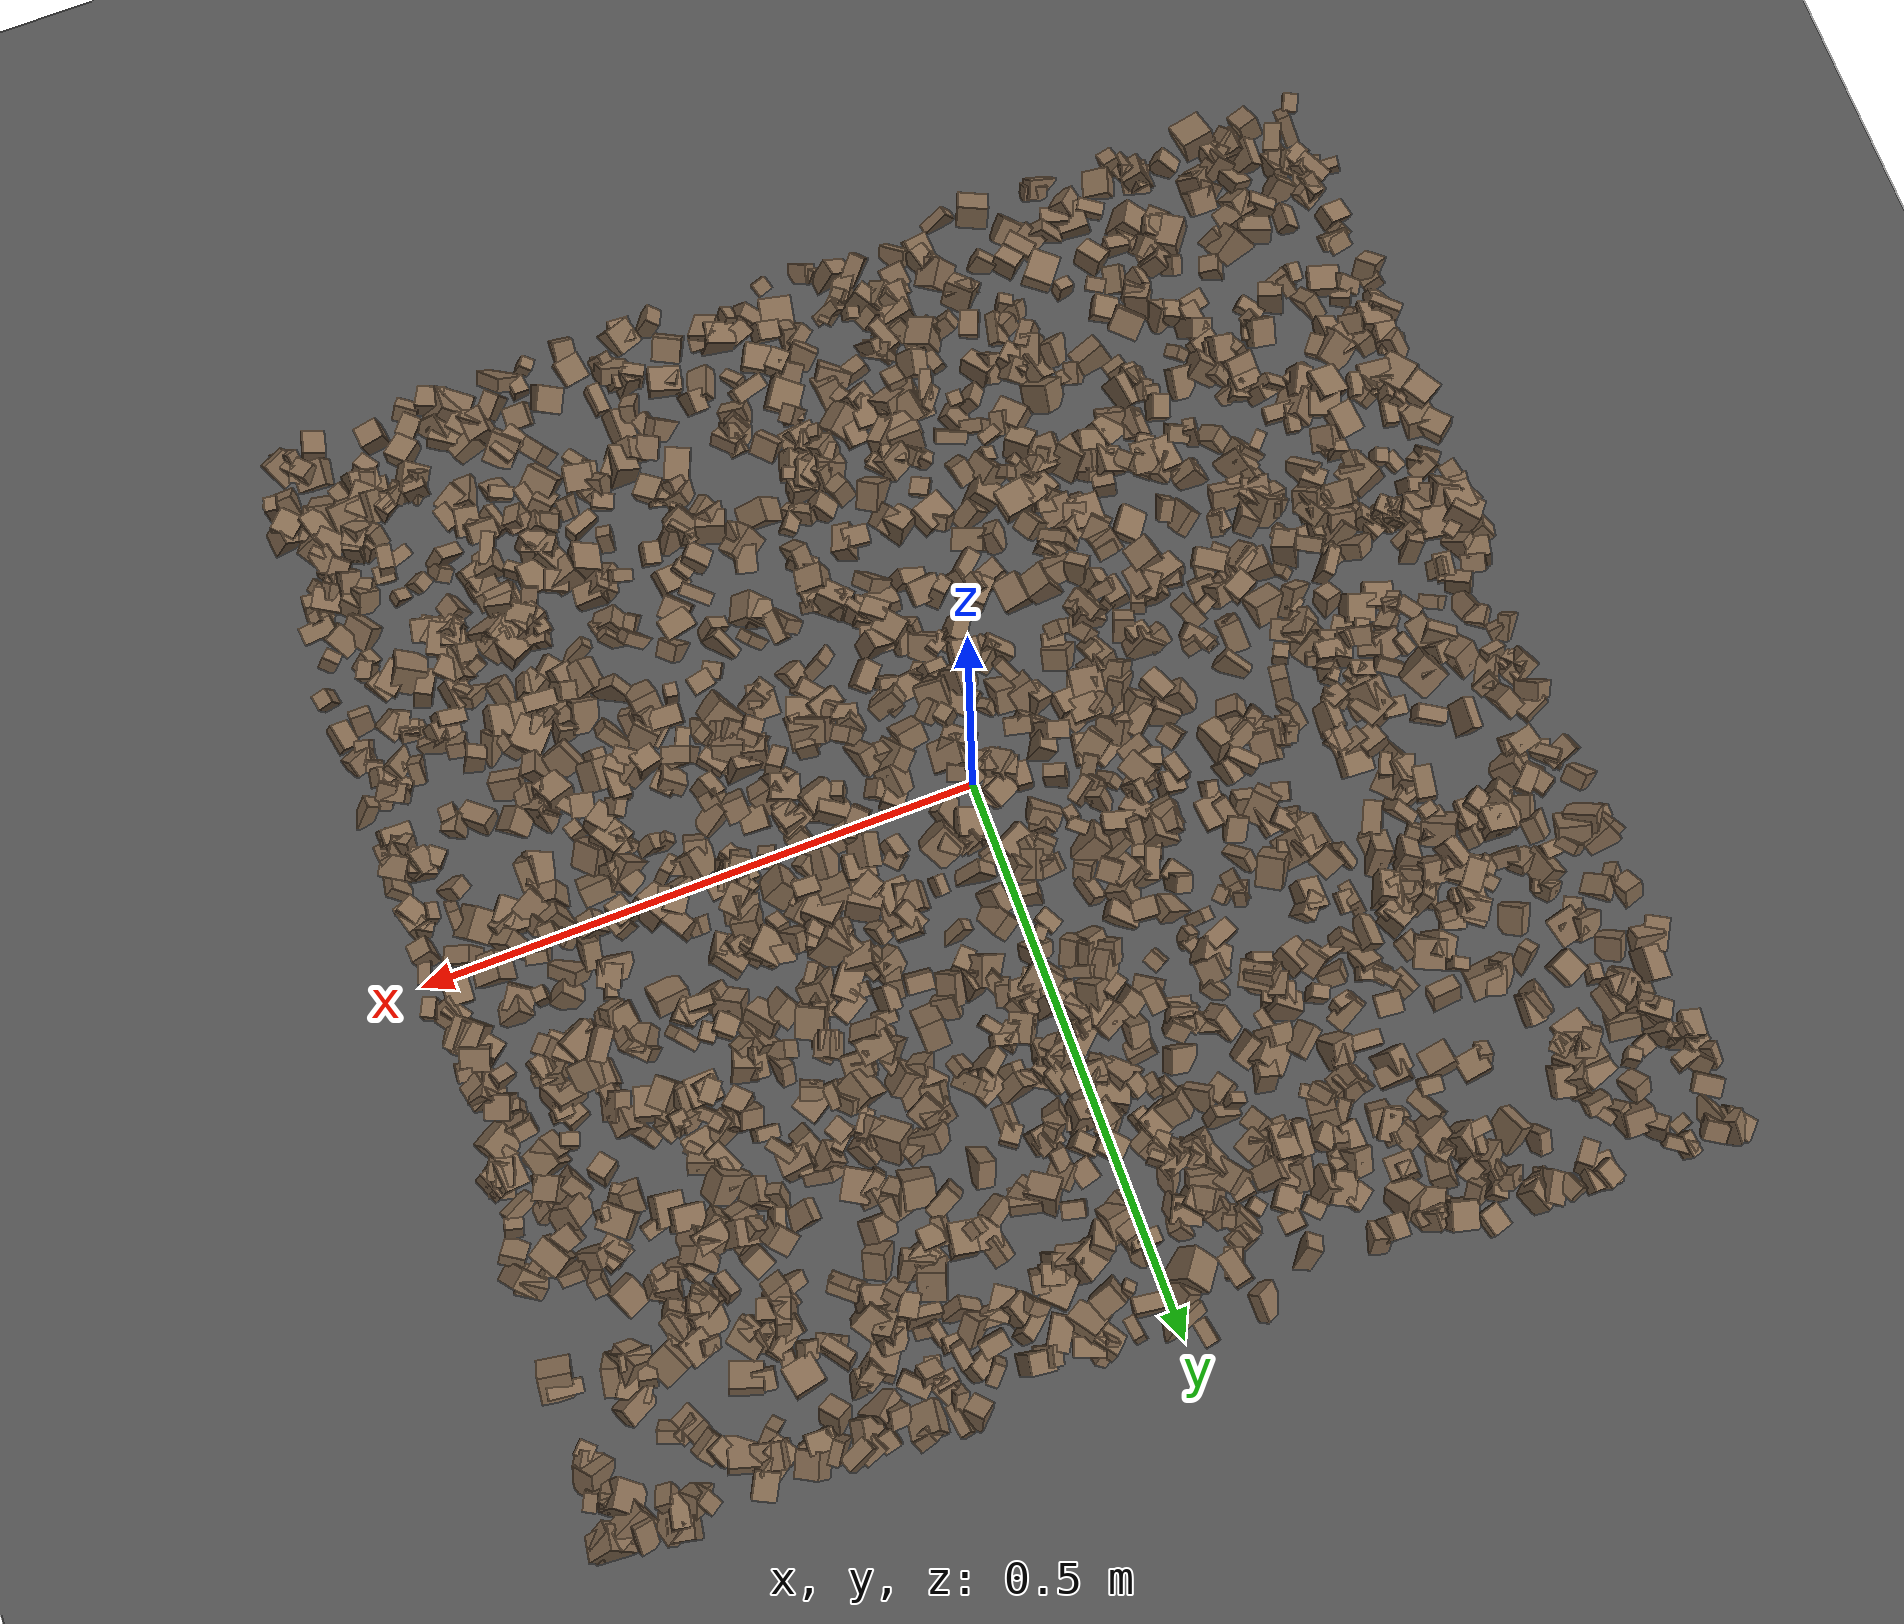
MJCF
<mujoco model="rocky_terrain_scene">
    <compiler angle="radian" inertiafromgeom="true" />
    <option timestep="0.002" gravity="0 0 -9.81" />

    <worldbody>
        <light name="sunlight" pos="5 5 5" dir="-1 -1 -1" diffuse="1 1 1" specular="0.5 0.5 0.5" ambient="0.5 0.5 0.5" />

        <geom name="ground_plane" type="plane" size="50 50 0.1" rgba="0.3 0.3 0.3 1" />

        <body name="rocky_terrain_body">

        </body>
    <body name="rock1" pos="-0.4844804550661397 -0.21005501530415116 0.0006751819280435765"><joint type="free" /><geom type="box" size="0.007815013142516796 0.008504301822924866 0.008568943283573287" quat="0.2043931016348419 0.37615976619251296 0.10363522373437613 0.31581190843826906" rgba="0.5 0.4 0.3 1" /></body><body name="rock2" pos="0.2709114100171707 -0.12809271084129736 6.735190737493402e-06"><joint type="free" /><geom type="box" size="0.010404575539799683 0.014236536685575438 0.006945795846274662" quat="0.09324539381306231 0.1510279470136413 0.39470497181967684 0.36102168735361945" rgba="0.5 0.4 0.3 1" /></body><body name="rock3" pos="0.16411592130728103 -0.11503072075549436 8.077667319736725e-05"><joint type="free" /><geom type="box" size="0.009004462475244534 0.010144576614511187 0.00843795259495167" quat="0.39452375606683604 0.2543024936220845 0.14026219677055407 0.21091155354052532" rgba="0.5 0.4 0.3 1" /></body><body name="rock4" pos="0.4597972900181756 0.21386730204946758 6.584062990720107e-05"><joint type="free" /><geom type="box" size="0.006700561899968288 0.00844490014704932 0.008640195761095152" quat="0.28922067548647773 0.032310813218135455 0.5212685298947756 0.1571999814006112" rgba="0.5 0.4 0.3 1" /></body><body name="rock5" pos="-0.4272442409593563 0.255466018669005 6.92363356603316e-05"><joint type="free" /><geom type="box" size="0.009909821013085967 0.007167935888582645 0.008603543453472714" quat="0.17404357231941447 0.2205250681497321 0.13868802405181155 0.46674333547904195" rgba="0.5 0.4 0.3 1" /></body><body name="rock6" pos="-0.13001058995614478 0.23742989902634504 0.0005066697477795655"><joint type="free" /><geom type="box" size="0.005243132365587523 0.010963901715674167 0.006734733226427642" quat="0.04554099023418267 0.4736974135765335 0.2262107125913255 0.25455088359795847" rgba="0.5 0.4 0.3 1" /></body><body name="rock7" pos="-0.42341227527301417 -0.4785863400976291 0.0008595116988252681"><joint type="free" /><geom type="box" size="0.010362023628588301 0.007918534335669344 0.010212631273398148" quat="0.2765615758007677 0.03694462114122754 0.4540820356166742 0.23241176744133057" rgba="0.5 0.4 0.3 1" /></body><body name="rock8" pos="-0.4783322973423799 -0.13576646700758066 0.0005101584195273899"><joint type="free" /><geom type="box" size="0.009375812346270409 0.00737586624246778 0.00977896536877981" quat="0.16186711682819635 0.05390021653552688 0.514503747324963 0.26972891931131376" rgba="0.5 0.4 0.3 1" /></body><body name="rock9" pos="-0.01670086604241927 0.011182188599411558 6.148155585055526e-05"><joint type="free" /><geom type="box" size="0.01053317291379536 0.01393431283700304 0.012235602239314382" quat="0.27059843055763905 0.11241719040568533 0.3080939332644567 0.30889044577221886" rgba="0.5 0.4 0.3 1" /></body><body name="rock10" pos="0.2675257752590363 0.4735539326968008 0.0007619939857501034"><joint type="free" /><geom type="box" size="0.009879904725778509 0.007360515127529346 0.014739407438200462" quat="0.399535017666749 0.13357536589911154 0.14570982224041856 0.3211797941937209" rgba="0.5 0.4 0.3 1" /></body><body name="rock11" pos="-0.4953834733481278 -0.27671124128013436 0.0009625734980520072"><joint type="free" /><geom type="box" size="0.0072835655485115345 0.011543150167486391 0.014353373230149999" quat="0.30000720081727017 0.3963609473760981 0.040623832842444085 0.26300801896418763" rgba="0.5 0.4 0.3 1" /></body><body name="rock12" pos="-0.14299296638582037 0.02324291964657421 0.00041015036139492133"><joint type="free" /><geom type="box" size="0.007844356866886362 0.012462492945301495 0.013000012839914234" quat="0.13870348138145222 0.29130700980419405 0.2751443651019361 0.2948451437124177" rgba="0.5 0.4 0.3 1" /></body><body name="rock13" pos="0.05257120421865902 -0.4610142062614 0.0009000309983630188"><joint type="free" /><geom type="box" size="0.007962226875351084 0.006743840048305467 0.009967857223799297" quat="0.23603511486188755 0.1695078203004463 0.3225143890125286 0.2719426758251376" rgba="0.5 0.4 0.3 1" /></body><body name="rock14" pos="0.46140396216424184 -0.3878445290446625 0.0008094307270371448"><joint type="free" /><geom type="box" size="0.00842131469662882 0.012261766930260161 0.009928348206430487" quat="0.022685249842425998 0.47513605295779066 0.11427427090049402 0.38790442629928945" rgba="0.5 0.4 0.3 1" /></body><body name="rock15" pos="-0.22082789794605207 -0.41982295415260074 0.0009937912070954531"><joint type="free" /><geom type="box" size="0.013055478447570372 0.013079835947805405 0.01464315964563772" quat="0.15587127315533858 0.10093877541553418 0.36135278433236245 0.3818371670967648" rgba="0.5 0.4 0.3 1" /></body><body name="rock16" pos="-0.30920981206981846 0.06411855280163392 0.0008195010507847073"><joint type="free" /><geom type="box" size="0.0054790355249872925 0.008758849495378883 0.00789031081573672" quat="0.2193097096078577 0.23715265333413932 0.08598748608795319 0.4575501509700498" rgba="0.5 0.4 0.3 1" /></body><body name="rock17" pos="0.03360279206944583 -0.3732178936910293 0.0002541576134058827"><joint type="free" /><geom type="box" size="0.009760105671254704 0.006194407246606157 0.007779902854418739" quat="0.3092761896319641 0.21561315951031587 0.16477058769070468 0.3103400631670154" rgba="0.5 0.4 0.3 1" /></body><body name="rock18" pos="0.20973028816522865 0.004654718674892533 8.0790260811905e-05"><joint type="free" /><geom type="box" size="0.009246038623640668 0.006587501040320696 0.00918638417421061" quat="0.22723298927822327 0.23755725225422855 0.21834690535842588 0.31686285310912227" rgba="0.5 0.4 0.3 1" /></body><body name="rock19" pos="-0.48525122622769445 -0.2584608507063474 0.0005902571663634298"><joint type="free" /><geom type="box" size="0.00837897576541806 0.014797842997562902 0.00992161465029176" quat="0.31611385972478234 0.21008751996018735 0.2351037412943338 0.23869487902069653" rgba="0.5 0.4 0.3 1" /></body><body name="rock20" pos="-0.11924841468597402 0.4000197699660637 0.000833536142762434"><joint type="free" /><geom type="box" size="0.009717301848769802 0.012755669780519164 0.013383457574416432" quat="0.3712160186722401 0.17718777122535007 0.05728529385280062 0.3943109162496092" rgba="0.5 0.4 0.3 1" /></body><body name="rock21" pos="0.3888178476638875 -0.015624791354183265 0.0009294247870598585"><joint type="free" /><geom type="box" size="0.010567008013661228 0.010179133908684811 0.007288244375399711" quat="0.017273034195536132 0.33020629605976476 0.3249878328018457 0.3275328369428534" rgba="0.5 0.4 0.3 1" /></body><body name="rock22" pos="0.04692021002798663 -0.17945872742539315 0.0005599659544387305"><joint type="free" /><geom type="box" size="0.005437285839848176 0.012941314013494312 0.011397822695364521" quat="0.37507033515691507 0.346794248314052 0.01842900199399945 0.2597064145350336" rgba="0.5 0.4 0.3 1" /></body><body name="rock23" pos="0.3510087690785494 0.29215494029397426 0.0006789912610651922"><joint type="free" /><geom type="box" size="0.013866619562970695 0.013544044767423897 0.010143316156024698" quat="0.1590763643048911 0.4506834122780114 0.2229137380115399 0.16732648540555758" rgba="0.5 0.4 0.3 1" /></body><body name="rock24" pos="0.20543938188441369 0.3242371211793681 0.0008825083425474507"><joint type="free" /><geom type="box" size="0.009205441797523 0.009951505554110417 0.012518888178343707" quat="0.03601527518646867 0.27223351689410785 0.05630460360391622 0.6354466043155073" rgba="0.5 0.4 0.3 1" /></body><body name="rock25" pos="-0.05389418297914683 0.17334147599350436 8.883758361109285e-05"><joint type="free" /><geom type="box" size="0.013690293325351648 0.010465376124420535 0.007078748742923747" quat="0.12419855174180008 0.1896938976230641 0.09382781741489893 0.592279733220237" rgba="0.5 0.4 0.3 1" /></body><body name="rock26" pos="0.1404634347604926 0.21814695895695813 2.5644431863115826e-05"><joint type="free" /><geom type="box" size="0.009640240633619152 0.012793707858119455 0.014030694158916928" quat="0.2835750793703341 0.25529681848025254 0.013512568864419289 0.4476155332849941" rgba="0.5 0.4 0.3 1" /></body><body name="rock27" pos="0.3620089311293433 0.1846770800281503 3.1730220524933685e-05"><joint type="free" /><geom type="box" size="0.007243711401788775 0.011430564339736611 0.005697658142379535" quat="0.33025669436329014 0.026574120744844762 0.3544810011840937 0.28868818370777144" rgba="0.5 0.4 0.3 1" /></body><body name="rock28" pos="0.19801364164805146 0.14248087320639524 0.0005475054557546175"><joint type="free" /><geom type="box" size="0.014265746066776646 0.012141273685858775 0.012758472084532964" quat="0.31340933737717713 0.2982781141406914 0.26813837559151193 0.12017417289061963" rgba="0.5 0.4 0.3 1" /></body><body name="rock29" pos="-0.35003040730699575 0.14050167839590555 0.00022069431511547566"><joint type="free" /><geom type="box" size="0.006789666121083017 0.007239956746079135 0.013157164680049648" quat="0.17705408384293034 0.2413754978323668 0.25073381977299636 0.3308365985517065" rgba="0.5 0.4 0.3 1" /></body><body name="rock30" pos="-0.2847432104290003 -0.1461807731598329 0.0007341114429115423"><joint type="free" /><geom type="box" size="0.010065183011831517 0.00986952792983087 0.005805140190952388" quat="0.14824363619877776 0.49025934141726796 0.07290034236636857 0.28859668001758576" rgba="0.5 0.4 0.3 1" /></body><body name="rock31" pos="0.4313068395317682 0.04639389446347897 0.00032811713139274456"><joint type="free" /><geom type="box" size="0.012170500477157835 0.009998965430200872 0.008501969472001146" quat="0.6471522128491582 0.14963704145775542 0.18771990802850208 0.015490837664584298" rgba="0.5 0.4 0.3 1" /></body><body name="rock32" pos="0.03928550007891207 0.1774143775982846 0.0006958813102097027"><joint type="free" /><geom type="box" size="0.00608823227861931 0.006242102819809697 0.011971352999659655" quat="0.014630888996248304 0.11262051006749381 0.5856134211945513 0.2871351797417066" rgba="0.5 0.4 0.3 1" /></body><body name="rock33" pos="0.19280968308916202 0.2604017472817922 0.00043921606634840396"><joint type="free" /><geom type="box" size="0.012025053855455098 0.00770182470463869 0.009521658983649445" quat="0.3178198877871932 0.03408956246609955 0.2621138566642814 0.38597669308242577" rgba="0.5 0.4 0.3 1" /></body><body name="rock34" pos="0.467262940365041 -0.16791926995431783 0.00018605918389910325"><joint type="free" /><geom type="box" size="0.008401765257624871 0.008371941048915671 0.010788052613917656" quat="0.2948788868565337 0.33489428036665786 0.22542436196057739 0.1448024708162311" rgba="0.5 0.4 0.3 1" /></body><body name="rock35" pos="-0.2610277248567401 -0.09364685424681707 0.0008604799076526918"><joint type="free" /><geom type="box" size="0.005949144989510003 0.012757987509919095 0.00861802717218708" quat="0.32203187478417766 0.042333766146639897 0.1913795119421304 0.4442548471270521" rgba="0.5 0.4 0.3 1" /></body><body name="rock36" pos="0.39959323855134243 -0.43507913849174984 9.408595705982881e-05"><joint type="free" /><geom type="box" size="0.009004161615808401 0.00544009544958431 0.00940800169411694" quat="0.20136981245045044 0.30737194736900747 0.19666738629131872 0.29459085388922346" rgba="0.5 0.4 0.3 1" /></body><body name="rock37" pos="-0.37235348999673523 -0.16190347933680127 0.00037540877133516494"><joint type="free" /><geom type="box" size="0.006089280423311825 0.010637889168518091 0.014399865562536765" quat="0.24014930653384867 0.5088716802178213 0.02885398822581782 0.2221250250225123" rgba="0.5 0.4 0.3 1" /></body><body name="rock38" pos="-0.4146313235989988 -0.14737565648069528 0.0002778549550810828"><joint type="free" /><geom type="box" size="0.008042095349360522 0.007704920698024531 0.01104170228945754" quat="0.14866818638382767 0.47088599922089264 0.07377879555581833 0.30666701883946135" rgba="0.5 0.4 0.3 1" /></body><body name="rock39" pos="0.3716112720421929 -0.30597827268659494 0.00034848237452851275"><joint type="free" /><geom type="box" size="0.01027410193661151 0.008836748032981316 0.008658766500604997" quat="0.11091480126089677 0.2894456958057334 0.31913392609001656 0.2805055768433532" rgba="0.5 0.4 0.3 1" /></body><body name="rock40" pos="-0.059781804613672995 0.39872557296827715 0.0009761434566640655"><joint type="free" /><geom type="box" size="0.011850696374908497 0.014608958390225555 0.009652668952931178" quat="0.011320042287012735 0.20477250936004848 0.37695909161050195 0.40694835674243685" rgba="0.5 0.4 0.3 1" /></body><body name="rock41" pos="-0.4283253075674498 0.29013585906928385 0.0009284162490522498"><joint type="free" /><geom type="box" size="0.005702142652897132 0.009308213806355905 0.006835845510251664" quat="0.3095520776709334 0.1335307053734621 0.33782225127849824 0.21909496567710623" rgba="0.5 0.4 0.3 1" /></body><body name="rock42" pos="-0.03608451207219099 0.3468559140998648 0.0004610880938380094"><joint type="free" /><geom type="box" size="0.013019295036280899 0.012234451032728133 0.006640349857186919" quat="0.3119712465003043 0.3635213528681047 0.11164724260739743 0.21286015802419359" rgba="0.5 0.4 0.3 1" /></body><body name="rock43" pos="-0.061477609675186895 0.38610662454395117 0.0005900495321486712"><joint type="free" /><geom type="box" size="0.005820972984127969 0.01364704267710157 0.014886763809298216" quat="0.1809667139591823 0.3531194932598518 0.08091151511637541 0.3850022776645905" rgba="0.5 0.4 0.3 1" /></body><body name="rock44" pos="0.36727309256740537 -0.4258913019932947 0.000996757608474836"><joint type="free" /><geom type="box" size="0.0149067803049752 0.006214657915739436 0.007937323834747823" quat="0.30752726882432896 0.3603778936371657 0.31807770448614286 0.014017133052362353" rgba="0.5 0.4 0.3 1" /></body><body name="rock45" pos="0.4309177228860154 -0.13036625028634807 0.0005038369473566185"><joint type="free" /><geom type="box" size="0.010311186971769165 0.0079818543725233 0.006965962864347109" quat="0.3905558186730648 0.080189473625362 0.4236792750297868 0.10557543267178623" rgba="0.5 0.4 0.3 1" /></body><body name="rock46" pos="-0.18504434672481362 -0.3364775017240712 0.0009787753272596292"><joint type="free" /><geom type="box" size="0.013537611578648263 0.010244712229839076 0.0075026388120978706" quat="0.13120212917653734 0.30548443813370985 0.4143774662803221 0.14893596640943063" rgba="0.5 0.4 0.3 1" /></body><body name="rock47" pos="-0.15537864458116868 -0.20629460153555035 0.000950528940355831"><joint type="free" /><geom type="box" size="0.012555815153288245 0.005316890895284941 0.014046520618433294" quat="0.28326493497182886 0.2156270253690481 0.31114508426155446 0.1899629553975685" rgba="0.5 0.4 0.3 1" /></body><body name="rock48" pos="-0.3621257762981328 0.2431189695376077 0.0004898877086981868"><joint type="free" /><geom type="box" size="0.011210325397030017 0.008444063315005716 0.013192604828822271" quat="0.29347730697218716 0.20192040060707633 0.15302151879055975 0.35158077363017665" rgba="0.5 0.4 0.3 1" /></body><body name="rock49" pos="0.41777511966868563 -0.03136134392834955 0.00029945197348297127"><joint type="free" /><geom type="box" size="0.009090593570034788 0.005782035916482453 0.014026850817877832" quat="0.10119455168637125 0.23981568423680813 0.20729590728257805 0.45169385679424245" rgba="0.5 0.4 0.3 1" /></body><body name="rock50" pos="0.4179243840617929 -0.00942308262851077 0.00065186507486594"><joint type="free" /><geom type="box" size="0.008002167111423385 0.013315757683340649 0.010472879730529" quat="0.20150825241920567 0.45659696746431316 0.17308528102881224 0.16880949908766898" rgba="0.5 0.4 0.3 1" /></body><body name="rock51" pos="0.47904053096324895 -0.19777369843238513 0.0007197254679968901"><joint type="free" /><geom type="box" size="0.007073661994101598 0.007522791461957043 0.005073786329207935" quat="0.13615684357753952 0.05693991125293858 0.49501205983307356 0.3118911853364484" rgba="0.5 0.4 0.3 1" /></body><body name="rock52" pos="-0.11025700573795338 0.004045688207387821 0.0008311216645758325"><joint type="free" /><geom type="box" size="0.011321940917279278 0.012590475485314763 0.013088486931790922" quat="0.27992759064013784 0.055465010921775304 0.11332124789015596 0.5512861505479308" rgba="0.5 0.4 0.3 1" /></body><body name="rock53" pos="0.46400805664418976 0.0683424639075062 0.00037778381856177703"><joint type="free" /><geom type="box" size="0.008914812160190138 0.0083077494113616 0.012162916782990557" quat="0.3454902371751372 0.3856834346508044 0.04636174260974056 0.22246458556431786" rgba="0.5 0.4 0.3 1" /></body><body name="rock54" pos="0.4064058799781173 0.24263299323966026 0.0003853132263060004"><joint type="free" /><geom type="box" size="0.011423064973182587 0.008449767902522498 0.014719296955471813" quat="0.31709041756408646 0.3611452282917574 0.19540198753008103 0.12636236661407516" rgba="0.5 0.4 0.3 1" /></body><body name="rock55" pos="0.2183781039011209 -0.011375525788343888 0.000898108331495707"><joint type="free" /><geom type="box" size="0.009031546930079539 0.009862312267186835 0.007500377500195929" quat="0.2404592041516304 0.13236693223847684 0.21242611791225613 0.4147477456976365" rgba="0.5 0.4 0.3 1" /></body><body name="rock56" pos="-0.2977217933846604 0.2351212169953013 0.0008633395802595712"><joint type="free" /><geom type="box" size="0.011048799392016927 0.011803729007550516 0.010988164200067659" quat="0.05798234290533862 0.3029005686906527 0.5027604013727274 0.13635668703128137" rgba="0.5 0.4 0.3 1" /></body><body name="rock57" pos="-0.007856370622609465 0.2707368108045155 0.00047393086694421895"><joint type="free" /><geom type="box" size="0.014428901856311072 0.010194640389635565 0.0130385148696932" quat="0.27068858237725546 0.20993115799760936 0.31405996679096976 0.20532029283416545" rgba="0.5 0.4 0.3 1" /></body><body name="rock58" pos="0.3751065533302751 -0.061897763589763066 0.00037039459591872183"><joint type="free" /><geom type="box" size="0.014931677751340196 0.012547380721703522 0.005452925077422707" quat="0.11907675246358096 0.4435395443609014 0.33138298373990716 0.10600071943561044" rgba="0.5 0.4 0.3 1" /></body><body name="rock59" pos="0.017474847670912785 0.462040641698072 0.0006689180600202078"><joint type="free" /><geom type="box" size="0.007323106910726593 0.005654960183770089 0.013745548442818018" quat="0.24170262985152863 0.28854439629361034 0.1696240273425171 0.30012894651234395" rgba="0.5 0.4 0.3 1" /></body><body name="rock60" pos="0.3461266562338996 0.08683518718609207 0.0009701863420016081"><joint type="free" /><geom type="box" size="0.0135092044535207 0.00743029826502115 0.009853738725878554" quat="0.27036679980611755 0.20010477190160372 0.31165952386296003 0.21786890442931872" rgba="0.5 0.4 0.3 1" /></body><body name="rock61" pos="0.42651554931121827 0.09982947814506793 0.0006403933363372238"><joint type="free" /><geom type="box" size="0.009894998317911186 0.011265271814725628 0.007897928544508112" quat="0.27272942610410056 0.15970579326666684 0.2451232133647931 0.3224415672644395" rgba="0.5 0.4 0.3 1" /></body><body name="rock62" pos="-0.13126990082503565 -0.0030862248452409036 0.0001983288738230765"><joint type="free" /><geom type="box" size="0.013668007998452414 0.00953019803545653 0.010681521858239063" quat="0.0038875586419060155 0.23723925876621535 0.42922910830403577 0.3296440742878429" rgba="0.5 0.4 0.3 1" /></body><body name="rock63" pos="0.056169436297719755 -0.12408637031296266 0.000490584397473972"><joint type="free" /><geom type="box" size="0.012669165041545298 0.008008783058921295 0.014276989450049966" quat="0.1144741036459165 0.5681962549069566 0.2594625363330628 0.057867105114064135" rgba="0.5 0.4 0.3 1" /></body><body name="rock64" pos="-0.34594137969266536 0.03706805007916392 0.0009006756678940222"><joint type="free" /><geom type="box" size="0.010631032918077855 0.005676748425445324 0.012408106113622051" quat="0.12189289848508582 0.3192437507252144 0.2560230451591081 0.30284030563059167" rgba="0.5 0.4 0.3 1" /></body><body name="rock65" pos="0.28420117226764663 -0.3284321314170089 0.0002429702975575011"><joint type="free" /><geom type="box" size="0.013144795288924215 0.011121741679482097 0.014382844948892817" quat="0.4018280948859665 0.18980988105676333 0.38542308222016003 0.02293894183711005" rgba="0.5 0.4 0.3 1" /></body><body name="rock66" pos="0.26480184972455567 -0.35686113651935547 0.0005325069533398771"><joint type="free" /><geom type="box" size="0.013949051840158797 0.0072002576005261295 0.008615336364111536" quat="0.19138444209882385 0.39917305835284983 0.028573700622863307 0.380868798925463" rgba="0.5 0.4 0.3 1" /></body><body name="rock67" pos="-0.13795780527981683 0.20929213063522112 0.0006072049814808701"><joint type="free" /><geom type="box" size="0.010311902949228506 0.01000232359845917 0.014098765952557265" quat="0.3899845127592072 0.264278970348987 0.0831288069028484 0.26260770998895744" rgba="0.5 0.4 0.3 1" /></body><body name="rock68" pos="-0.4212611667662096 0.16470747935491803 0.0001836665233471576"><joint type="free" /><geom type="box" size="0.008856697536396358 0.009061396178020294 0.012893407538789231" quat="0.281684594590561 0.04445047395996067 0.23285620405060087 0.44100872739887736" rgba="0.5 0.4 0.3 1" /></body><body name="rock69" pos="0.1994395421502867 -0.12560263339929312 0.000761831639458761"><joint type="free" /><geom type="box" size="0.010591346486345517 0.006750254302492266 0.014472967462420657" quat="0.256609819307887 0.36828858115717533 0.2996318698730107 0.07546972966192693" rgba="0.5 0.4 0.3 1" /></body><body name="rock70" pos="0.3435397182632055 -0.1957822439959752 0.0004609151285806399"><joint type="free" /><geom type="box" size="0.008345782582255193 0.01208828966239784 0.010432874612078025" quat="0.07385822869985814 0.4168504325422444 0.02901038017004087 0.4802809585878566" rgba="0.5 0.4 0.3 1" /></body><body name="rock71" pos="-0.3709333889384011 -0.22078647420600428 0.0002533979588058851"><joint type="free" /><geom type="box" size="0.012391047827674619 0.009993653194510576 0.006857925146068264" quat="0.014912183678100228 0.018539204574849796 0.49339174605298025 0.47315686569406973" rgba="0.5 0.4 0.3 1" /></body><body name="rock72" pos="0.1337155074403028 -0.18804941525704677 8.920823191959626e-05"><joint type="free" /><geom type="box" size="0.005055586010591111 0.007760866554745854 0.014552061111881856" quat="0.5527948576368725 0.12539759550454352 0.13185611844414047 0.18995142841444349" rgba="0.5 0.4 0.3 1" /></body><body name="rock73" pos="-0.12450929416611334 0.19255162340209386 0.0005614484358699797"><joint type="free" /><geom type="box" size="0.006093532517962873 0.005856537904849119 0.005290248761049744" quat="0.13962776248301953 0.6735717795827065 0.16258083495690723 0.024219622977366635" rgba="0.5 0.4 0.3 1" /></body><body name="rock74" pos="-0.4356607189923001 -0.30672651138434004 0.00012066513526240507"><joint type="free" /><geom type="box" size="0.011336740676000278 0.012420141774446464 0.007150511964583018" quat="0.0793971777594022 0.32449935852771306 0.2260570673027743 0.37004639641011033" rgba="0.5 0.4 0.3 1" /></body><body name="rock75" pos="-0.32235735174822333 -0.1552402397849978 0.0006015579929483933"><joint type="free" /><geom type="box" size="0.011345201163392476 0.011614949943745675 0.008817945367602113" quat="0.17031667625250968 0.18594394376159137 0.2792665535835967 0.3644728264023023" rgba="0.5 0.4 0.3 1" /></body><body name="rock76" pos="0.07777497870975736 -0.024247820003550635 3.1666370664254266e-05"><joint type="free" /><geom type="box" size="0.008386344983594892 0.007896623979484568 0.009794452274356606" quat="0.4327576967282189 0.1968598825561896 0.10621674642081959 0.26416567429477195" rgba="0.5 0.4 0.3 1" /></body><body name="rock77" pos="0.058973798901390984 -0.19640616396273647 0.0002189023800917771"><joint type="free" /><geom type="box" size="0.01047122017254078 0.01388001822189985 0.014660257123020447" quat="0.32572488033445823 0.3660064892191316 0.04805784809945086 0.2602107823469593" rgba="0.5 0.4 0.3 1" /></body><body name="rock78" pos="0.15559585986539426 -0.03505916753401195 0.0005303039878965984"><joint type="free" /><geom type="box" size="0.0065049902208703485 0.0075172619599017 0.009681625285964623" quat="0.2917971077636283 0.5557814572184083 0.09982231443583217 0.05259912058213119" rgba="0.5 0.4 0.3 1" /></body><body name="rock79" pos="0.35302510069575355 0.25988701350156285 6.212066826655316e-06"><joint type="free" /><geom type="box" size="0.012210809188122796 0.01029023745411434 0.013806275004670417" quat="0.06545432409690564 0.372186115125531 0.007255300343525855 0.5551042604340375" rgba="0.5 0.4 0.3 1" /></body><body name="rock80" pos="-0.3497953306438293 -0.2527200566816281 0.00046275275445366803"><joint type="free" /><geom type="box" size="0.009188265125899712 0.005275761550353756 0.012650155773019922" quat="0.32771814739026667 0.23935016674410273 0.15741137995278412 0.27552030591284654" rgba="0.5 0.4 0.3 1" /></body><body name="rock81" pos="0.3369178908044306 -0.25394469116008844 9.132182486037322e-05"><joint type="free" /><geom type="box" size="0.010465310035793485 0.01399345402017441 0.013300088185357176" quat="0.3859316016948636 0.404474907482646 0.024357170569694914 0.18523632025279554" rgba="0.5 0.4 0.3 1" /></body><body name="rock82" pos="-0.30950342300411904 0.21431893816528358 0.00076734645455573"><joint type="free" /><geom type="box" size="0.013191606698606157 0.007875040067311096 0.014800219444281493" quat="0.3118700632980862 0.1653305498442293 0.21241158376367641 0.31038780309400815" rgba="0.5 0.4 0.3 1" /></body><body name="rock83" pos="0.2901692614376413 0.27176580221331537 0.00019777508505748275"><joint type="free" /><geom type="box" size="0.005086957995847645 0.009443842252328825 0.011787261031508747" quat="0.39465541656853276 0.2155120205757435 0.06654672653672333 0.3232858363190003" rgba="0.5 0.4 0.3 1" /></body><body name="rock84" pos="0.34633498473117763 0.0004097584235407403 0.0004459039994980806"><joint type="free" /><geom type="box" size="0.010026431986341601 0.010314694783404056 0.008896451017593664" quat="0.3451861712469802 0.030804238448173957 0.5601825024828299 0.063827087822016" rgba="0.5 0.4 0.3 1" /></body><body name="rock85" pos="-0.35019563931408804 -0.008884272212649535 0.0009487163024881131"><joint type="free" /><geom type="box" size="0.010839849833603744 0.007826740704848501 0.008869448391330224" quat="0.01969329903743818 0.30008639916319496 0.11677349816352262 0.5634468036358443" rgba="0.5 0.4 0.3 1" /></body><body name="rock86" pos="-0.3001104142915134 0.260335868459064 0.00020869466191354347"><joint type="free" /><geom type="box" size="0.009601204428854168 0.005817019545242081 0.012145560013629642" quat="0.31565989970099634 0.10129963404708464 0.16913285862288954 0.41390760762902956" rgba="0.5 0.4 0.3 1" /></body><body name="rock87" pos="-0.09102958261573912 -0.3042521589221344 0.0005799895431718483"><joint type="free" /><geom type="box" size="0.014079166082919377 0.012178474892452709 0.005538062930018651" quat="0.09394014541525374 0.06419122746284169 0.5256527131740225 0.3162159139478821" rgba="0.5 0.4 0.3 1" /></body><body name="rock88" pos="-0.006240720447840298 0.31156728310665116 3.565137725897782e-05"><joint type="free" /><geom type="box" size="0.013175041939264366 0.00856039529923415 0.007965644938597074" quat="0.274310233025106 0.40554801767133464 0.1663443555579852 0.1537973937455742" rgba="0.5 0.4 0.3 1" /></body><body name="rock89" pos="0.26243404232550804 -0.455175376856106 6.237874229274653e-05"><joint type="free" /><geom type="box" size="0.010409054223289582 0.010834995920125354 0.007960565100845288" quat="0.4529504130815653 0.006660037951897125 0.10546770446940228 0.4349218444971353" rgba="0.5 0.4 0.3 1" /></body><body name="rock90" pos="0.3864907068933152 0.04968911127304221 0.0004906709542435964"><joint type="free" /><geom type="box" size="0.008230443027072877 0.010806284332094688 0.010212399066953967" quat="0.06246435163216205 0.44280704476434535 0.25623981429613923 0.2384887893073533" rgba="0.5 0.4 0.3 1" /></body><body name="rock91" pos="0.27763326248576636 -0.15111910181890043 0.0006334308848668132"><joint type="free" /><geom type="box" size="0.006313650411549647 0.008761830766065695 0.014097811799742586" quat="0.5373739401727872 0.232687017332622 0.1532206644355801 0.07671837805901069" rgba="0.5 0.4 0.3 1" /></body><body name="rock92" pos="0.41807591541716727 0.3038084812187243 0.0002972390608875605"><joint type="free" /><geom type="box" size="0.007503122152229034 0.013271428334869332 0.011931168810027357" quat="0.01479135493420921 0.3374283953846499 0.1775495643197514 0.47023068536138946" rgba="0.5 0.4 0.3 1" /></body><body name="rock93" pos="-0.06087879587900946 0.3183163808835049 0.00010654487295249027"><joint type="free" /><geom type="box" size="0.012118516075639331 0.010879219033271404 0.012964400048521434" quat="0.04782962444351959 0.5255306791737041 0.11669083864615742 0.3099488577366188" rgba="0.5 0.4 0.3 1" /></body><body name="rock94" pos="0.08068753986583344 -0.3897256759961436 0.00036835008097032065"><joint type="free" /><geom type="box" size="0.009278982118197249 0.00759115986874224 0.012508453662026232" quat="0.3117692153304869 0.2126442528242323 0.40792736979646493 0.06765916204881584" rgba="0.5 0.4 0.3 1" /></body><body name="rock95" pos="0.33346767620070394 -0.10518464449238629 0.000825487421489863"><joint type="free" /><geom type="box" size="0.0056903183964859974 0.014383218878361699 0.005084876868733498" quat="0.09659155320888992 0.6321980083992947 0.24903297698057125 0.022177461411244083" rgba="0.5 0.4 0.3 1" /></body><body name="rock96" pos="-0.006856798677654874 0.14065573809514087 0.0009405955333773739"><joint type="free" /><geom type="box" size="0.006023675673705172 0.012886401824787931 0.005126395127172639" quat="0.36601998753122356 0.30643402977060064 0.15664005743502382 0.17090592526315196" rgba="0.5 0.4 0.3 1" /></body><body name="rock97" pos="0.16793068600898198 -0.2461409758817772 0.00045120997916657334"><joint type="free" /><geom type="box" size="0.014559385710937081 0.007585846873989326 0.005533754446115864" quat="0.16401384760390683 0.10382960251519745 0.4350491449567546 0.29710740492414106" rgba="0.5 0.4 0.3 1" /></body><body name="rock98" pos="0.17312490709175654 0.3640107555763886 0.00040353998230467295"><joint type="free" /><geom type="box" size="0.00507001094946083 0.006936702303846925 0.0074269802241579645" quat="0.16675977087697136 0.14190097815602548 0.33235029017723416 0.35898896078976894" rgba="0.5 0.4 0.3 1" /></body><body name="rock99" pos="-0.1602827639954808 0.2765717715921997 0.00044578422396334663"><joint type="free" /><geom type="box" size="0.005084847215843771 0.011134163222013379 0.008592030741541261" quat="0.4423716656711236 0.45790867380752537 0.09646593338389076 0.0032537271374603115" rgba="0.5 0.4 0.3 1" /></body><body name="rock100" pos="-0.2079514289556733 -0.31914094122874126 0.000631323834166669"><joint type="free" /><geom type="box" size="0.006003916618812093 0.007163788688841739 0.0072725529407211345" quat="0.22291071359132653 0.2823012075366312 0.29382099330102646 0.20096708557101586" rgba="0.5 0.4 0.3 1" /></body><body name="rock101" pos="0.3762787545242632 -0.42645759943290584 0.0003467591886155134"><joint type="free" /><geom type="box" size="0.009900590573507867 0.006983064942015591 0.012753387388548193" quat="0.2804645514633065 0.15575760201194494 0.40837362773163566 0.15540421879311292" rgba="0.5 0.4 0.3 1" /></body><body name="rock102" pos="-0.030857812043918242 -0.45069829781324644 0.0008523699336945806"><joint type="free" /><geom type="box" size="0.005544453262445971 0.009816345458194327 0.012658779476158566" quat="0.16918346977561116 0.279037240057182 0.3827674819910925 0.16901180817611436" rgba="0.5 0.4 0.3 1" /></body><body name="rock103" pos="-0.1476634505934853 -0.17901123816765574 0.0003601311477631919"><joint type="free" /><geom type="box" size="0.013679651155544377 0.014546593596010814 0.005495210915833171" quat="0.020750365082957297 0.2185567454895475 0.3566203912027308 0.40407249822476426" rgba="0.5 0.4 0.3 1" /></body><body name="rock104" pos="0.43130969091085947 -0.3951624351556149 0.00038649153884844225"><joint type="free" /><geom type="box" size="0.009872395542702781 0.014512642808282617 0.00781671984749296" quat="0.10706726048308378 0.10886009597142281 0.39029205460677174 0.39378058893872164" rgba="0.5 0.4 0.3 1" /></body><body name="rock105" pos="0.38003657928661905 -0.17741166312613377 0.0007842411477701"><joint type="free" /><geom type="box" size="0.008019880760413288 0.01463744585408567 0.005125664809698453" quat="0.1772111517539992 0.21152788157876656 0.10511878041209886 0.5061421862551353" rgba="0.5 0.4 0.3 1" /></body><body name="rock106" pos="-0.14310947379546268 0.3164899657036989 0.0003842676138279796"><joint type="free" /><geom type="box" size="0.014263447854805732 0.013267570867265256 0.008343912352015034" quat="0.24205371639401274 0.3175870173320074 0.12866819093669388 0.31169107533728607" rgba="0.5 0.4 0.3 1" /></body><body name="rock107" pos="-0.429130121542892 -0.10129424410575705 0.0006047409222568755"><joint type="free" /><geom type="box" size="0.008373777078598318 0.011726866299441401 0.01200352918619594" quat="0.2863333709869947 0.2593162557790397 0.40329849959214287 0.0510518736418227" rgba="0.5 0.4 0.3 1" /></body><body name="rock108" pos="0.48290810398333106 0.44568183019108976 0.00012445604247850474"><joint type="free" /><geom type="box" size="0.006499770163824717 0.012241388686107798 0.007753969175730277" quat="0.39274496632041234 0.23677759440641896 0.26310936075736485 0.10736807851580381" rgba="0.5 0.4 0.3 1" /></body><body name="rock109" pos="-0.2601085896997434 0.16636481791157454 0.0009875122126461271"><joint type="free" /><geom type="box" size="0.01160537447418479 0.008717791482536423 0.010816550643076963" quat="0.22528651032890107 0.16126606241909763 0.41094226959613345 0.20250515765586774" rgba="0.5 0.4 0.3 1" /></body><body name="rock110" pos="-0.22211855870787234 0.43316575973584837 0.00010685417359654392"><joint type="free" /><geom type="box" size="0.010450866197925289 0.012530124345753214 0.011985358747599283" quat="0.18367509608557778 0.3216911175190469 0.23380442750368308 0.2608293588916923" rgba="0.5 0.4 0.3 1" /></body><body name="rock111" pos="-0.10249502734756433 -0.4812439331711962 7.313855255283552e-05"><joint type="free" /><geom type="box" size="0.008738153716310572 0.00532794002026271 0.012663954081161631" quat="0.3278778420704619 0.3392160008708559 0.32079407469422 0.012112082364462259" rgba="0.5 0.4 0.3 1" /></body><body name="rock112" pos="0.35024202666819304 0.10204979334326458 0.0009426220504948282"><joint type="free" /><geom type="box" size="0.009555850447513767 0.012408809185369789 0.006436232785069327" quat="0.29407904414622027 0.07287794016786109 0.46345063507709167 0.16959238060882703" rgba="0.5 0.4 0.3 1" /></body><body name="rock113" pos="0.40986584913153323 -0.12288432439603936 0.0005019434417603468"><joint type="free" /><geom type="box" size="0.009188829062902366 0.007618479390684128 0.014887186747286622" quat="0.2719972438004768 0.4284957813225253 0.100636754717942 0.1988702201590559" rgba="0.5 0.4 0.3 1" /></body><body name="rock114" pos="-0.02334110190848082 -0.12849771841137547 0.00038104282409990876"><joint type="free" /><geom type="box" size="0.006110761971156162 0.006975363266810043 0.007840954024920783" quat="0.01628731540166617 0.42499610470571597 0.25302887341230135 0.30568770648031646" rgba="0.5 0.4 0.3 1" /></body><body name="rock115" pos="0.14806257025309078 -0.1397288474052515 0.0003181608187245589"><joint type="free" /><geom type="box" size="0.006022615136289762 0.010098844413830443 0.011921803483143357" quat="0.07338962347124638 0.10748832841415457 0.04794050822193706 0.771181539892662" rgba="0.5 0.4 0.3 1" /></body><body name="rock116" pos="0.4589003870003161 -0.2860019914998383 0.00012885511156855744"><joint type="free" /><geom type="box" size="0.007209895495171939 0.006409479536813362 0.012548388432546251" quat="0.12530192811078708 0.27788003360206903 0.4345266249493498 0.16229141333779412" rgba="0.5 0.4 0.3 1" /></body><body name="rock117" pos="-0.15446869196011803 0.42312631079593255 0.00017436670803414901"><joint type="free" /><geom type="box" size="0.012860311048997593 0.007791381446437576 0.013073587533484546" quat="0.022417965266098558 0.41622445663624985 0.3247242838782545 0.2366332942193971" rgba="0.5 0.4 0.3 1" /></body><body name="rock118" pos="0.07200030866423912 -0.4211424688777108 0.0005038851742413441"><joint type="free" /><geom type="box" size="0.005227799969194326 0.005453122641891474 0.00997003884064928" quat="0.29373469510394473 0.45865731612000665 0.09885127315081788 0.1487567156252307" rgba="0.5 0.4 0.3 1" /></body><body name="rock119" pos="-0.3166256590726685 -0.015580802137631689 0.0008949178036519861"><joint type="free" /><geom type="box" size="0.014068095320151238 0.010559353253548159 0.010624110901759274" quat="0.5414828996567586 0.22183348978211023 0.1734276083207455 0.06325600224038583" rgba="0.5 0.4 0.3 1" /></body><body name="rock120" pos="-0.13120271591301447 -0.45102995003113866 0.0009368202511628106"><joint type="free" /><geom type="box" size="0.013291713906259914 0.012155664332395746 0.011200504943341016" quat="0.24412794615484845 0.4185518684567978 0.2530691105990487 0.08425107478930513" rgba="0.5 0.4 0.3 1" /></body><body name="rock121" pos="0.13129223283423752 0.41858471731504443 0.0005677356059368021"><joint type="free" /><geom type="box" size="0.014617723373855557 0.00745364033164142 0.009436665046559175" quat="0.31341070775407764 0.33794616815056455 0.17187074837094454 0.17677237572441332" rgba="0.5 0.4 0.3 1" /></body><body name="rock122" pos="-0.08485882363874675 0.10949906799585452 0.0004432651818517037"><joint type="free" /><geom type="box" size="0.009683585652221962 0.014754015168073769 0.009660544359965982" quat="0.09545112195754787 0.1605005613321371 0.43402472944204523 0.3100235872682699" rgba="0.5 0.4 0.3 1" /></body><body name="rock123" pos="-0.15917043343003456 0.05860196515235816 0.00020345532152007463"><joint type="free" /><geom type="box" size="0.009398790979519497 0.010250282776071429 0.009085228017302039" quat="0.07194928534555456 0.42966480313043415 0.3973906918739597 0.10099521965005158" rgba="0.5 0.4 0.3 1" /></body><body name="rock124" pos="0.42888116705157886 -0.3971188195086962 0.00012665491634254633"><joint type="free" /><geom type="box" size="0.01476521679798437 0.009129330338460098 0.013244393693650006" quat="0.5018545430571242 0.001971777873970356 0.26041267284223985 0.2357610062266656" rgba="0.5 0.4 0.3 1" /></body><body name="rock125" pos="-0.3812379523355087 -0.45490198392575676 0.0007284741571304198"><joint type="free" /><geom type="box" size="0.007269704874192002 0.006138085565929822 0.010778107929495441" quat="0.17273087612599414 0.41011114210854926 0.3958775504273953 0.021280431338061317" rgba="0.5 0.4 0.3 1" /></body><body name="rock126" pos="-0.22529372922480628 0.39430531454829154 0.0001981155787031378"><joint type="free" /><geom type="box" size="0.008431539396101046 0.009686718003203375 0.013986595415730337" quat="0.12272441435502764 0.08733384450224678 0.43250830290197156 0.35743343824075413" rgba="0.5 0.4 0.3 1" /></body><body name="rock127" pos="0.49648693171541514 0.34684650514283755 0.0006746261471209656"><joint type="free" /><geom type="box" size="0.010863227361162544 0.014952958962582294 0.013949184743588385" quat="0.179643672279609 0.35068070487231295 0.10490052117346778 0.3647751016746102" rgba="0.5 0.4 0.3 1" /></body><body name="rock128" pos="0.18649791715685082 0.30961307358108103 0.0006004268401835766"><joint type="free" /><geom type="box" size="0.013435325993078225 0.00811729276291568 0.01182136058395375" quat="0.3375046980351201 0.12618586242430999 0.3416995123564763 0.19460992718409365" rgba="0.5 0.4 0.3 1" /></body><body name="rock129" pos="0.39154011639565 -0.25550252932756556 0.00018618902939560223"><joint type="free" /><geom type="box" size="0.009020450116352061 0.01427153582655051 0.011833179834509894" quat="0.385010038622714 0.31186605316951854 0.13560692265488644 0.167516985552881" rgba="0.5 0.4 0.3 1" /></body><body name="rock130" pos="0.3619383706675705 0.33146902456009164 0.0006271392467797126"><joint type="free" /><geom type="box" size="0.013212091761436985 0.008305679906290291 0.012818324076651441" quat="0.375327001215597 0.3943304039077605 0.18642296440522624 0.04391963047141629" rgba="0.5 0.4 0.3 1" /></body><body name="rock131" pos="-0.2488863031044577 0.1489888774434558 0.0006243556370544626"><joint type="free" /><geom type="box" size="0.007288595245079639 0.007047600824747823 0.014314848929889185" quat="0.22858021739226034 0.179909656263688 0.1688023415002399 0.4227077848438119" rgba="0.5 0.4 0.3 1" /></body><body name="rock132" pos="0.47999037001148404 -0.05349450932479283 0.0004962757221095255"><joint type="free" /><geom type="box" size="0.012939358646610142 0.005560287458031273 0.007815638227553925" quat="0.30486068126073507 0.30031787799466386 0.09742463906219245 0.29739680168240873" rgba="0.5 0.4 0.3 1" /></body><body name="rock133" pos="0.444970928079079 -0.18097522150761924 0.00033490712933630464"><joint type="free" /><geom type="box" size="0.010361932991424527 0.008777258927320968 0.005871534794280969" quat="0.3310398495189208 0.20387628505009325 0.32981760324829695 0.13526626218268908" rgba="0.5 0.4 0.3 1" /></body><body name="rock134" pos="-0.4794636428616924 -0.3576432523942663 0.0008928581754102773"><joint type="free" /><geom type="box" size="0.006663186941061468 0.014548799709558503 0.011366190109823603" quat="0.29732787233985636 0.18600391875218864 0.3247696741091989 0.19189853479875613" rgba="0.5 0.4 0.3 1" /></body><body name="rock135" pos="0.2536009951283972 0.05690378799898521 0.0004971130837064926"><joint type="free" /><geom type="box" size="0.011861792705034398 0.008364567422219273 0.005102134032031581" quat="0.3130909153182162 0.29759008983753893 0.057299645261614345 0.3320193495826306" rgba="0.5 0.4 0.3 1" /></body><body name="rock136" pos="-0.317052438449002 0.43426225689224984 0.0007303755330736944"><joint type="free" /><geom type="box" size="0.013784454066539359 0.00720730752291346 0.014792451867445457" quat="0.029556457378299473 0.3351179412766049 0.385795227280199 0.24953037406489662" rgba="0.5 0.4 0.3 1" /></body><body name="rock137" pos="-0.25454320499404925 0.1447058845071607 0.0005385120715183098"><joint type="free" /><geom type="box" size="0.006986950575623298 0.01090393072117352 0.006631681594962056" quat="0.0285171243332467 0.2714527482044643 0.05310810580975258 0.6469220216525364" rgba="0.5 0.4 0.3 1" /></body><body name="rock138" pos="0.3575827415558903 0.019910038975853084 0.0001475947943804111"><joint type="free" /><geom type="box" size="0.014937876258937336 0.012496381593806121 0.007512063407980852" quat="0.12962767853058266 0.3331568314826214 0.07817093167449139 0.45904455831230456" rgba="0.5 0.4 0.3 1" /></body><body name="rock139" pos="0.2809140296653968 0.09735110410688064 0.0003295332642981539"><joint type="free" /><geom type="box" size="0.013410242160009321 0.006007887777252192 0.011196600662456112" quat="0.4459859198375071 0.048499865981469784 0.48623493664846595 0.019279277532557086" rgba="0.5 0.4 0.3 1" /></body><body name="rock140" pos="-0.24927648587897921 0.04513139491772644 0.00019714696120872965"><joint type="free" /><geom type="box" size="0.008342606967758459 0.007720160651684248 0.008508483855879838" quat="0.3670797753290804 0.1702676046218778 0.34762722306833616 0.11502539698070573" rgba="0.5 0.4 0.3 1" /></body><body name="rock141" pos="-0.4560633722752645 -0.441190636508048 0.0005739258416628137"><joint type="free" /><geom type="box" size="0.013597659305629006 0.0064415705831538704 0.008225947630192108" quat="0.23293517818998577 0.2657508657829725 0.1315539494936049 0.36976000653343677" rgba="0.5 0.4 0.3 1" /></body><body name="rock142" pos="0.11635956164654504 0.053903931864163535 0.0004169496857260959"><joint type="free" /><geom type="box" size="0.013084045109024445 0.011784282359951711 0.009146240875919524" quat="0.38934517047095624 0.4074527408052621 0.11661691142014277 0.08658517730363895" rgba="0.5 0.4 0.3 1" /></body><body name="rock143" pos="0.48688361487378995 0.17905200460082915 7.752922053759104e-06"><joint type="free" /><geom type="box" size="0.012854781323456292 0.005394314312295435 0.011132006143667793" quat="0.36069884362624016 0.24420639581394332 0.2676647483101512 0.12743001224966524" rgba="0.5 0.4 0.3 1" /></body><body name="rock144" pos="0.30927172130860914 0.3128372462987913 0.0007112002115383871"><joint type="free" /><geom type="box" size="0.009485608826781716 0.013889774931397567 0.010046395478794504" quat="0.2605676475114816 0.13005145564120013 0.3429646211222056 0.2664162757251127" rgba="0.5 0.4 0.3 1" /></body><body name="rock145" pos="0.47279713182550986 0.4772923153321236 0.00033797291184277123"><joint type="free" /><geom type="box" size="0.013644079373445177 0.008445308963092858 0.014973970506387192" quat="0.32221493586928035 0.05519119839486671 0.4060884363061602 0.2165054294296927" rgba="0.5 0.4 0.3 1" /></body><body name="rock146" pos="0.27767688514252065 0.27117107909628957 0.0004837673280155378"><joint type="free" /><geom type="box" size="0.012080108953494768 0.005936079453633677 0.01012794144047436" quat="0.310968478301618 0.21117476285617706 0.4163147577165795 0.061542001125625447" rgba="0.5 0.4 0.3 1" /></body><body name="rock147" pos="0.41957420137274226 -0.39733447536564603 0.0009726801581604363"><joint type="free" /><geom type="box" size="0.009790666878446812 0.014261586737541337 0.007308960621784604" quat="0.39674402430065553 0.004957119197716566 0.3468417547268299 0.251457101774798" rgba="0.5 0.4 0.3 1" /></body><body name="rock148" pos="-0.033116782632604425 -0.30087280415499174 0.0006925223884480051"><joint type="free" /><geom type="box" size="0.011651666472929614 0.013891974321056499 0.013664369957416853" quat="0.3312212646681026 0.0473383756773558 0.34308240808982443 0.27835795156471715" rgba="0.5 0.4 0.3 1" /></body><body name="rock149" pos="0.3309262113908692 -0.36938366980817106 0.0003462730119633506"><joint type="free" /><geom type="box" size="0.005476285433475547 0.01031814701394014 0.0050108733867179536" quat="0.06241015882887222 0.21444495622436904 0.3180468989033636 0.4050979860433952" rgba="0.5 0.4 0.3 1" /></body><body name="rock150" pos="-0.4255175427503939 -0.09296134141904888 7.771673732126028e-05"><joint type="free" /><geom type="box" size="0.007160216308892844 0.01454575530999427 0.007496636250113975" quat="0.2488973558194805 0.3191108644912899 0.14764571544266755 0.28434606424656206" rgba="0.5 0.4 0.3 1" /></body><body name="rock151" pos="-0.2462844890314757 -0.22297325801488344 0.0008508354763202472"><joint type="free" /><geom type="box" size="0.014331266182481723 0.011584236841123481 0.010427551653204949" quat="0.2541427968839861 0.28223216439388044 0.27174047457107636 0.19188456415105704" rgba="0.5 0.4 0.3 1" /></body><body name="rock152" pos="-0.07477890887404226 0.374378358027734 0.000696890660356913"><joint type="free" /><geom type="box" size="0.013536066923247866 0.010417047130887976 0.007776564235780872" quat="0.26477567479526876 0.15065770140984655 0.17179047403768813 0.4127761497571966" rgba="0.5 0.4 0.3 1" /></body><body name="rock153" pos="0.2364617141808999 0.1266461663254176 0.0006040125511807668"><joint type="free" /><geom type="box" size="0.014584464937534226 0.01093729775748105 0.009619127641762409" quat="0.061158056092780445 0.24240480820097607 0.4798126981875649 0.21662443751867863" rgba="0.5 0.4 0.3 1" /></body><body name="rock154" pos="0.3059307285070879 0.1186136182864791 0.0006037800660928098"><joint type="free" /><geom type="box" size="0.008172180933826118 0.013985059258943028 0.00519832290348216" quat="0.005810363508214514 0.29971810547862937 0.2763973417894512 0.4180741892237049" rgba="0.5 0.4 0.3 1" /></body><body name="rock155" pos="-0.3914482296196784 0.27037446513217767 0.0006932567687692117"><joint type="free" /><geom type="box" size="0.0126124838139548 0.008036134967283762 0.01085023696764128" quat="0.25994177753999265 0.35437982517605476 0.31996366969832 0.0657147275856325" rgba="0.5 0.4 0.3 1" /></body><body name="rock156" pos="0.189971052227777 0.4213149051091847 0.0003406531938972236"><joint type="free" /><geom type="box" size="0.010269408310552522 0.0062833863628270455 0.0051848878882913355" quat="0.3128784906002886 0.12064031233496447 0.29001356879296575 0.2764676282717811" rgba="0.5 0.4 0.3 1" /></body><body name="rock157" pos="0.17803740028550186 0.035172052089546546 0.0009274180339768725"><joint type="free" /><geom type="box" size="0.006420433231214682 0.010245851203585236 0.008714741037063248" quat="0.04140866951825112 0.5702582100634787 0.11620143569044693 0.27213168472782334" rgba="0.5 0.4 0.3 1" /></body><body name="rock158" pos="-0.0366139886958704 0.08930290490717252 0.00011851822941122781"><joint type="free" /><geom type="box" size="0.008116142393757197 0.006381646587656898 0.010063145346958107" quat="0.2060881675203835 0.280292418415094 0.33458099374195177 0.1790384203225707" rgba="0.5 0.4 0.3 1" /></body><body name="rock159" pos="-0.32625586251157945 0.18738472021348784 0.0007383257439569976"><joint type="free" /><geom type="box" size="0.00816668435962187 0.012804837727947736 0.010701722248002778" quat="0.13644757472788338 0.12291958888930202 0.5620408380749515 0.17859199830786301" rgba="0.5 0.4 0.3 1" /></body><body name="rock160" pos="-0.00870098375066708 0.236135962783107 0.000552363426025004"><joint type="free" /><geom type="box" size="0.007422417233606859 0.009349190638889771 0.013490776220118489" quat="0.2361045000645701 0.06721459576305719 0.3737305209914044 0.32295038318096836" rgba="0.5 0.4 0.3 1" /></body><body name="rock161" pos="-0.03211425206203755 0.22514179659432032 0.0006870879272569683"><joint type="free" /><geom type="box" size="0.01091254754506499 0.010573342818151145 0.010031917998648953" quat="0.26818134062060855 0.2872279781138584 0.1868692533247413 0.2577214279407917" rgba="0.5 0.4 0.3 1" /></body><body name="rock162" pos="0.44452601998244434 0.1706040627177563 0.00013462433949365337"><joint type="free" /><geom type="box" size="0.011826319464882374 0.014468629006980847 0.011202218821416591" quat="0.2926337177362695 0.08908269205804738 0.13265925578465937 0.48562433442102365" rgba="0.5 0.4 0.3 1" /></body><body name="rock163" pos="0.30659042019214033 0.35953910873214023 0.00027270343025180923"><joint type="free" /><geom type="box" size="0.014920853827442966 0.01402764077606973 0.009121735738358411" quat="0.02882559157360845 0.11015554453679782 0.3746250259423008 0.4863938379472929" rgba="0.5 0.4 0.3 1" /></body><body name="rock164" pos="0.3276170939942863 -0.05695411681585749 0.000613078779555219"><joint type="free" /><geom type="box" size="0.01245402477179525 0.010645145226267187 0.013379250789356631" quat="0.3096019552350291 0.3707778151887916 0.2856795795281097 0.03394065004806958" rgba="0.5 0.4 0.3 1" /></body><body name="rock165" pos="-0.14567006395142634 -0.10348260468922699 0.0006104808132374598"><joint type="free" /><geom type="box" size="0.006179919694495325 0.009653320631736087 0.012699342399724221" quat="0.30772403906443474 0.27053889891764865 0.07968102000744763 0.3420560420104689" rgba="0.5 0.4 0.3 1" /></body><body name="rock166" pos="-0.40119915312203935 0.04396014123864589 0.0006239971312603997"><joint type="free" /><geom type="box" size="0.010502098942823019 0.014705120027221227 0.01490074090811912" quat="0.005921094828622095 0.4501689371606448 0.2158375326875233 0.3280724353232098" rgba="0.5 0.4 0.3 1" /></body><body name="rock167" pos="0.010648642026318544 -0.4182771851893182 0.0006320595414827742"><joint type="free" /><geom type="box" size="0.005792413889124864 0.014973004495556583 0.011627031521517367" quat="0.3043344499049459 0.33349762615106854 0.006117762586300499 0.35605016135768497" rgba="0.5 0.4 0.3 1" /></body><body name="rock168" pos="0.01967748902566613 0.30230354984017993 0.0005148997881326128"><joint type="free" /><geom type="box" size="0.008574002111020055 0.006349195507564965 0.006282944010757241" quat="0.148077833696073 0.04774228524066673 0.026014936263051514 0.7781649448002087" rgba="0.5 0.4 0.3 1" /></body><body name="rock169" pos="-0.23558670956342942 0.4680511485689087 0.0005994868086384557"><joint type="free" /><geom type="box" size="0.010665619839002043 0.011236984152731444 0.010484092624291758" quat="0.24590967677046302 0.37729403387131427 0.18200298591366332 0.19479330344455933" rgba="0.5 0.4 0.3 1" /></body><body name="rock170" pos="0.4230168721645998 -0.3854787700140666 0.0003405391140402323"><joint type="free" /><geom type="box" size="0.008036427760039981 0.008260656551273806 0.008110918667405105" quat="0.06525657701200363 0.28561598340660904 0.4663643778887811 0.18276306169260617" rgba="0.5 0.4 0.3 1" /></body><body name="rock171" pos="0.010850294571735808 0.27083524678581816 0.0009089973747188318"><joint type="free" /><geom type="box" size="0.01059069394813511 0.013528497528006476 0.008277707949820964" quat="0.4045984013474066 0.0621307384736561 0.39837959826278285 0.13489126191615444" rgba="0.5 0.4 0.3 1" /></body><body name="rock172" pos="0.30000458783838413 -0.2037438041131877 0.0009085538975919989"><joint type="free" /><geom type="box" size="0.012128131482216507 0.007966576587941471 0.014450234362212187" quat="0.12412646935266076 0.28334600669215004 0.05658115346652215 0.535946370488667" rgba="0.5 0.4 0.3 1" /></body><body name="rock173" pos="0.3621552615636531 0.48448469430688057 0.0005755886111209371"><joint type="free" /><geom type="box" size="0.012350702901987799 0.010362517697032371 0.010218137902335937" quat="0.35844786571400716 0.26598449161673027 0.20483066865439994 0.17073697401486257" rgba="0.5 0.4 0.3 1" /></body><body name="rock174" pos="-0.2067247621604431 0.32203506394393855 9.254739464539919e-06"><joint type="free" /><geom type="box" size="0.010465867649194943 0.013381192155990922 0.01102372601049328" quat="0.1046795576576612 0.2904690572593419 0.10747814990956141 0.49737323517343546" rgba="0.5 0.4 0.3 1" /></body><body name="rock175" pos="-0.017868145806201552 -0.07308655654292784 0.0003552561472205834"><joint type="free" /><geom type="box" size="0.012227824596071087 0.00689224530662807 0.012493265713265849" quat="0.10696839626843667 0.1840739897369339 0.3619788304055671 0.3469787835890624" rgba="0.5 0.4 0.3 1" /></body><body name="rock176" pos="-0.22256615867559626 -0.2601783782081639 0.00018319008495923673"><joint type="free" /><geom type="box" size="0.01291937334119108 0.013116674564260935 0.008381816530243093" quat="0.12861334574343483 0.32207409275337057 0.4811213614386181 0.06819120006457653" rgba="0.5 0.4 0.3 1" /></body><body name="rock177" pos="0.23033621958968153 0.0015109154459752583 0.0006767745852015704"><joint type="free" /><geom type="box" size="0.008706992843039923 0.01371460473637286 0.006025414561551598" quat="0.39943194506319735 0.22596049858003736 0.18410944488131928 0.190498111475446" rgba="0.5 0.4 0.3 1" /></body><body name="rock178" pos="0.007726385802516056 0.2479993894543402 0.00010895724239077864"><joint type="free" /><geom type="box" size="0.007019338512914515 0.010847723972892867 0.009362880628906316" quat="0.27192785132507125 0.10680556494184995 0.5147166761594224 0.10654990757365648" rgba="0.5 0.4 0.3 1" /></body><body name="rock179" pos="-0.48010152966669084 -0.41589222862448283 0.0001438359217590083"><joint type="free" /><geom type="box" size="0.011797071575240126 0.010891986199788078 0.005539425003376142" quat="0.06493842074877139 0.3738333644111612 0.19097212824873588 0.3702560865913314" rgba="0.5 0.4 0.3 1" /></body><body name="rock180" pos="-0.22335422030873986 -0.1186482158017208 0.0008939034645322494"><joint type="free" /><geom type="box" size="0.01403088815949564 0.01114827586712732 0.010317229500755597" quat="0.3573365078600777 0.5035104996189004 0.047860524565356 0.09129246795566591" rgba="0.5 0.4 0.3 1" /></body><body name="rock181" pos="-0.26110609202488455 0.20653794813795234 0.00016153963359408907"><joint type="free" /><geom type="box" size="0.009350717616819035 0.010428477387819548 0.006191351056445202" quat="0.27893560513873894 0.22074686319721545 0.2527604420147696 0.24755708964927592" rgba="0.5 0.4 0.3 1" /></body><body name="rock182" pos="0.45851760415089693 0.1965023405825056 0.00043315543191992854"><joint type="free" /><geom type="box" size="0.00514145702112362 0.013435816669541148 0.005332709019474544" quat="0.07149237132420856 0.36608176940589443 0.023483056770930492 0.5389428024989665" rgba="0.5 0.4 0.3 1" /></body><body name="rock183" pos="-0.2465711202183648 -0.2318645947426764 0.0008521164395575775"><joint type="free" /><geom type="box" size="0.00757926802575145 0.009327385269112039 0.01086135236772877" quat="0.1499466496482715 0.06560988362738805 0.3426014382534401 0.4418420284709003" rgba="0.5 0.4 0.3 1" /></body><body name="rock184" pos="-0.02045263772310224 -0.2418768870583572 0.0007929884468778182"><joint type="free" /><geom type="box" size="0.010389362571416746 0.01165583907451433 0.012422038466653915" quat="0.1841441238817053 0.15475292884292088 0.2407810364407309 0.4203219108346429" rgba="0.5 0.4 0.3 1" /></body><body name="rock185" pos="-0.06803388890143591 -0.3405704291804209 0.0006572228657514843"><joint type="free" /><geom type="box" size="0.01336154866046941 0.011067469146474489 0.013806018780631906" quat="0.38070430176905024 0.03174359272823165 0.14517279992374793 0.4423793055789702" rgba="0.5 0.4 0.3 1" /></body><body name="rock186" pos="-0.2655428508211346 -0.47275329929233 0.0004945743627684945"><joint type="free" /><geom type="box" size="0.009883215914897433 0.007869114745842455 0.013755974261187052" quat="0.33595233494807003 0.004001311701898162 0.2896870068537394 0.3703593464962924" rgba="0.5 0.4 0.3 1" /></body><body name="rock187" pos="-0.4424980574735843 0.2912967528160648 5.620780636159129e-05"><joint type="free" /><geom type="box" size="0.011556561458281699 0.005891570586181893 0.008772886988575939" quat="0.3661661983408861 0.05224380672789945 0.2556313548554938 0.32595864007572056" rgba="0.5 0.4 0.3 1" /></body><body name="rock188" pos="-0.48160874651744556 -0.4738690406722923 0.00012590985381679066"><joint type="free" /><geom type="box" size="0.013945226087547422 0.012890724576727144 0.0060063675777781746" quat="0.30572543316690104 0.1805274001632188 0.3827757081265339 0.13097145854334621" rgba="0.5 0.4 0.3 1" /></body><body name="rock189" pos="-0.0651380872865065 0.1010524918463418 0.0004598767306036205"><joint type="free" /><geom type="box" size="0.008112792089763303 0.007315051688710836 0.010351702883775356" quat="0.1514166758867236 0.1285556413221458 0.15744913542418337 0.5625785473669472" rgba="0.5 0.4 0.3 1" /></body><body name="rock190" pos="0.07136789176489933 -0.21041238634529158 0.0008448002346085583"><joint type="free" /><geom type="box" size="0.007778461454897199 0.007559139806005102 0.007389390932265157" quat="0.010843941589573223 0.5161221045949809 0.4633621257095348 0.009671828105911003" rgba="0.5 0.4 0.3 1" /></body><body name="rock191" pos="0.24416290054596435 -0.14382358072597445 3.911341750437103e-05"><joint type="free" /><geom type="box" size="0.01159061914655346 0.0056099064302717805 0.013241372109674101" quat="0.39987166401848295 0.31718442416671955 0.16634884565598426 0.1165950661588131" rgba="0.5 0.4 0.3 1" /></body><body name="rock192" pos="0.3547205016114082 -0.22064613555435186 0.00030888086330175445"><joint type="free" /><geom type="box" size="0.007821625815955871 0.012347701783987912 0.007227710800720258" quat="0.11398190440442584 0.4907687521312995 0.12484011580950775 0.2704092276547669" rgba="0.5 0.4 0.3 1" /></body><body name="rock193" pos="0.27743698102503556 0.1976208519846019 0.0005750813475767067"><joint type="free" /><geom type="box" size="0.01072922331780012 0.008909665946050018 0.010379470174734489" quat="0.16416238764541835 0.2879595475154734 0.062897924629696 0.48498014020941216" rgba="0.5 0.4 0.3 1" /></body><body name="rock194" pos="-0.09657975595210311 -0.46287289723711433 0.00011694541698542549"><joint type="free" /><geom type="box" size="0.010740467388261291 0.007769727982258541 0.010993141681349709" quat="0.2791961915886916 0.18937057117598702 0.3298907770609462 0.20154246017437513" rgba="0.5 0.4 0.3 1" /></body><body name="rock195" pos="-0.06517784273422289 0.412431036412518 0.00020932348099933363"><joint type="free" /><geom type="box" size="0.009304329372943277 0.012097479702842103 0.010066482186517525" quat="0.08116957415164844 0.3947360879102756 0.22115383214087314 0.3029405057972028" rgba="0.5 0.4 0.3 1" /></body><body name="rock196" pos="-0.3797697157775969 -0.43484698940219224 0.0005666272152599074"><joint type="free" /><geom type="box" size="0.010667060301449673 0.014373063732835926 0.011572921863816008" quat="0.3220745083703355 0.17588778827280444 0.2989109879107373 0.20312671544612282" rgba="0.5 0.4 0.3 1" /></body><body name="rock197" pos="0.04594701876663021 0.44414177141958844 0.00028687145454645225"><joint type="free" /><geom type="box" size="0.012003688657565924 0.01335499352254289 0.010634444480615322" quat="0.47787343734477394 0.3753302155966807 0.14141845698588457 0.0053778900726606845" rgba="0.5 0.4 0.3 1" /></body><body name="rock198" pos="0.174031658618239 0.19131698304785283 0.0008204995922738942"><joint type="free" /><geom type="box" size="0.01092088088607479 0.006770532639027188 0.012842980247330313" quat="0.24403371699944507 0.273684082282436 0.31518271271796444 0.16709948800015445" rgba="0.5 0.4 0.3 1" /></body><body name="rock199" pos="-0.3866941434677511 0.30476195565010156 0.00045820008309163494"><joint type="free" /><geom type="box" size="0.00631467321426538 0.012997545969394377 0.007827373605817575" quat="0.20005175054998733 0.17292085327283774 0.15891951667520612 0.4681078795019688" rgba="0.5 0.4 0.3 1" /></body><body name="rock200" pos="0.3267720593606709 0.3753098947549588 0.00048622869121934745"><joint type="free" /><geom type="box" size="0.007348563870913293 0.010148607948803658 0.008942033519634685" quat="0.061652452156208994 0.5788177367681433 0.07763261233931504 0.2818971987363327" rgba="0.5 0.4 0.3 1" /></body><body name="rock201" pos="-0.1694554687859312 -0.11297216409375765 0.0008760913643212142"><joint type="free" /><geom type="box" size="0.009483394463179855 0.005277849884408624 0.005399648429146721" quat="0.014053506182007439 0.5727349218278317 0.19352808558568968 0.2196834864044711" rgba="0.5 0.4 0.3 1" /></body><body name="rock202" pos="0.31139476935906196 0.23817739294829932 0.0009288167130172462"><joint type="free" /><geom type="box" size="0.013845750347466428 0.005003833811757265 0.009068100796686917" quat="0.13591690105521897 0.3631464710749157 0.3961128114771844 0.10482381639268089" rgba="0.5 0.4 0.3 1" /></body><body name="rock203" pos="0.3308814311622341 -0.4949051168560321 0.0009476225341219525"><joint type="free" /><geom type="box" size="0.010560809925840263 0.010709653033546462 0.012432597220696898" quat="0.2792293584820959 0.32358945464026545 0.1549107040564104 0.2422704828212283" rgba="0.5 0.4 0.3 1" /></body><body name="rock204" pos="-0.3293689294388905 -0.19670706953178796 0.0003834165698688105"><joint type="free" /><geom type="box" size="0.013901757043860857 0.009801988131107182 0.008703287615849868" quat="0.26098751839677414 0.01742073515989646 0.5305201616302749 0.19107158481305442" rgba="0.5 0.4 0.3 1" /></body><body name="rock205" pos="0.31118506830688786 0.40068699803013974 0.0001400628007247997"><joint type="free" /><geom type="box" size="0.009670405498739671 0.00724125665823638 0.00616175578993347" quat="0.26670770300624785 0.23495909330238932 0.2825864687973254 0.21574673489403745" rgba="0.5 0.4 0.3 1" /></body><body name="rock206" pos="0.2979018282120327 -0.09027676902695136 0.00038851649943163916"><joint type="free" /><geom type="box" size="0.008094700917752464 0.011882212315387938 0.005655621743261826" quat="0.4262563039300128 0.2014797058460044 0.10651609038577231 0.2657478998382104" rgba="0.5 0.4 0.3 1" /></body><body name="rock207" pos="0.47329595011595416 -0.352763893201954 3.0415781163236177e-05"><joint type="free" /><geom type="box" size="0.012704271359153339 0.00939677136822862 0.009909578783001676" quat="0.149719741851989 0.04153652794729621 0.4174163306266578 0.3913273995740571" rgba="0.5 0.4 0.3 1" /></body><body name="rock208" pos="0.3090087403114242 0.2924162913785576 0.0009414124513770594"><joint type="free" /><geom type="box" size="0.008094591911811999 0.007737272330608857 0.014992143364348287" quat="0.07824674105489583 0.30915205746204283 0.3568908402348625 0.25571036124819885" rgba="0.5 0.4 0.3 1" /></body><body name="rock209" pos="0.4848011099055155 -0.10408530227143997 0.0004085996244432997"><joint type="free" /><geom type="box" size="0.01341842345551934 0.013615872418691478 0.009962292501969294" quat="0.0483066878731037 0.1752703952909604 0.39284246506317294 0.383580451772763" rgba="0.5 0.4 0.3 1" /></body><body name="rock210" pos="-0.43463789894510474 0.18368833331192247 0.0003477158725910582"><joint type="free" /><geom type="box" size="0.010355322596738537 0.010683397715735806 0.005061316103741455" quat="0.4462836283078124 0.12515477171829123 0.12545398253411136 0.30310761743978504" rgba="0.5 0.4 0.3 1" /></body><body name="rock211" pos="0.34296751064041064 0.4648178176002349 0.0006352354075190572"><joint type="free" /><geom type="box" size="0.00936612278341024 0.012801584644697758 0.007750219731776168" quat="0.10299079515166876 0.6118690024366196 0.1858640555230868 0.09927614688862482" rgba="0.5 0.4 0.3 1" /></body><body name="rock212" pos="-0.38389366511902256 0.22189685637519418 0.0008412506925891451"><joint type="free" /><geom type="box" size="0.009250256211793323 0.007809624433635009 0.006861517892134318" quat="0.07509188339248353 0.553093679242946 0.1995034545480856 0.17231098281648502" rgba="0.5 0.4 0.3 1" /></body><body name="rock213" pos="0.07440320701904712 0.2797790508718402 9.289767329110577e-05"><joint type="free" /><geom type="box" size="0.014504088514193967 0.00522361846757687 0.006922216346127497" quat="0.17032030425060368 0.32787904796506545 0.3382876380136399 0.1635130097706909" rgba="0.5 0.4 0.3 1" /></body><body name="rock214" pos="-0.41805728676260767 -0.3334196261668295 0.00045074536988553904"><joint type="free" /><geom type="box" size="0.010388467818592402 0.00523612968847508 0.012165368423258367" quat="0.3276992711099234 0.04911946396719962 0.4935836525555373 0.1295976123673397" rgba="0.5 0.4 0.3 1" /></body><body name="rock215" pos="-0.09791080877465486 -0.2416117652992158 0.0009177027576857317"><joint type="free" /><geom type="box" size="0.01133212029287253 0.011929683905600267 0.011860503788677585" quat="0.3729713643072511 0.290220243372225 0.05295012085826808 0.28385827146225584" rgba="0.5 0.4 0.3 1" /></body><body name="rock216" pos="-0.38448977527001205 0.1824828966827401 0.00043816713016853437"><joint type="free" /><geom type="box" size="0.007071610150081377 0.005981395887141911 0.006517601716245927" quat="0.020642374618954677 0.36571906132115367 0.48998021688252197 0.12365834717736968" rgba="0.5 0.4 0.3 1" /></body><body name="rock217" pos="-0.3904916800534781 -0.0830888997028949 0.00018973106334321254"><joint type="free" /><geom type="box" size="0.007269518058579399 0.014920289493047054 0.010681515935535414" quat="0.2594464924694153 0.3096051994357159 0.38137537670088884 0.049572931393979856" rgba="0.5 0.4 0.3 1" /></body><body name="rock218" pos="0.4935000564269335 -0.0118523162805384 0.0007363541948845364"><joint type="free" /><geom type="box" size="0.010085861041200813 0.006516559456651122 0.00532719818832893" quat="0.34255038459296605 0.25297660313266734 0.2294306408882023 0.17504237138616438" rgba="0.5 0.4 0.3 1" /></body><body name="rock219" pos="0.04655424974042832 0.336567227139534 0.0006463295436172358"><joint type="free" /><geom type="box" size="0.011417995486058215 0.005232065293052725 0.011152350767040482" quat="0.032730090492314734 0.26093536907448794 0.31973266646830845 0.38660187396488893" rgba="0.5 0.4 0.3 1" /></body><body name="rock220" pos="-0.02388753569518598 -0.4926671739448065 0.0006699180003661297"><joint type="free" /><geom type="box" size="0.006979847293053072 0.006205055640779983 0.00653756427390016" quat="0.08798102100965395 0.22180793124622988 0.44945703661897846 0.24075401112513778" rgba="0.5 0.4 0.3 1" /></body><body name="rock221" pos="0.296469989382936 -0.17732909467097924 0.0008756171376821444"><joint type="free" /><geom type="box" size="0.007545722517100551 0.014379082065756967 0.012075333983657503" quat="0.1472390291137622 0.2827660165353829 0.07828695648398688 0.4917079978668681" rgba="0.5 0.4 0.3 1" /></body><body name="rock222" pos="0.03430045211220534 0.2871313918356915 0.00032689312119772105"><joint type="free" /><geom type="box" size="0.013493672337979119 0.007209273213359863 0.008475816083144572" quat="0.059331231698670286 0.4583604865006262 0.13773923573947358 0.3445690460612299" rgba="0.5 0.4 0.3 1" /></body><body name="rock223" pos="-0.007049738113596216 0.30082637040361015 0.0006019639819847091"><joint type="free" /><geom type="box" size="0.011220799887830021 0.011036750567956903 0.014516026448184626" quat="0.36690092376007244 0.03962663088972836 0.0965162143880724 0.49695623096212677" rgba="0.5 0.4 0.3 1" /></body><body name="rock224" pos="-0.2554346675119644 0.2705789511530746 9.886920031412383e-05"><joint type="free" /><geom type="box" size="0.005701468443907608 0.007541162366596901 0.008846146582910693" quat="0.32436718950561855 0.2563363838823641 0.18121040774584404 0.2380860188661732" rgba="0.5 0.4 0.3 1" /></body><body name="rock225" pos="-0.03277426610398382 0.3228732753086295 0.0007232704451012185"><joint type="free" /><geom type="box" size="0.013439063832678764 0.006462344714287824 0.007933369363732123" quat="0.08054007759851786 0.3593752971412776 0.48408586333471054 0.07599876192549404" rgba="0.5 0.4 0.3 1" /></body><body name="rock226" pos="-0.13715939579424097 0.04412380983616526 0.00018398332004591412"><joint type="free" /><geom type="box" size="0.014843597635959126 0.005198762119596985 0.014720731703827233" quat="0.13254319807335 0.3830806961103511 0.21967387777603653 0.2647022280402623" rgba="0.5 0.4 0.3 1" /></body><body name="rock227" pos="0.038288775490357585 0.03704552913520953 0.00019680451965281443"><joint type="free" /><geom type="box" size="0.008461324097115305 0.013426063940846094 0.00930936106596288" quat="0.4317493572219312 0.23222485743679427 0.17596070372111147 0.16006508162016303" rgba="0.5 0.4 0.3 1" /></body><body name="rock228" pos="-0.36427933156686787 0.30890771683945006 0.0006494918723016962"><joint type="free" /><geom type="box" size="0.006502812305148806 0.01357320133225879 0.008371072845962243" quat="0.10546415968529568 0.2536928675582789 0.11812724511479575 0.5227157276416297" rgba="0.5 0.4 0.3 1" /></body><body name="rock229" pos="0.2668756059861135 -0.49379194605024335 0.0009234140883233409"><joint type="free" /><geom type="box" size="0.0063723144620232205 0.014877363666552797 0.014282689501144363" quat="0.2959637693458649 0.3878435558556311 0.31538931217348753 0.0008033626250164922" rgba="0.5 0.4 0.3 1" /></body><body name="rock230" pos="-0.49824538425890486 0.4964847471109527 0.000895282702669267"><joint type="free" /><geom type="box" size="0.010251015041759216 0.00632237860848134 0.014697392477946575" quat="0.41426066720289206 0.29429279370322053 0.10998957566526968 0.18145696342861772" rgba="0.5 0.4 0.3 1" /></body><body name="rock231" pos="0.3721510735812116 -0.3447437874644369 0.00042987738303222237"><joint type="free" /><geom type="box" size="0.011251928766261986 0.0069238848831251355 0.006620402361747881" quat="0.0017867153830066272 0.3292461995871147 0.3630540237947914 0.3059130612350872" rgba="0.5 0.4 0.3 1" /></body><body name="rock232" pos="0.26105179275953994 0.03280811867044797 0.000287368731424134"><joint type="free" /><geom type="box" size="0.0091315908804279 0.007449435099889765 0.005436477840602064" quat="0.061797923693582724 0.5874449265935963 0.02890515379549523 0.32185199591732566" rgba="0.5 0.4 0.3 1" /></body><body name="rock233" pos="-0.1950686607174591 -0.06659780453280095 0.0005777950084275994"><joint type="free" /><geom type="box" size="0.00597276846203609 0.009274133655318362 0.010081466567572882" quat="0.08815673203522545 0.3240146584905997 0.20634980580924686 0.381478803664928" rgba="0.5 0.4 0.3 1" /></body><body name="rock234" pos="-0.3104699728803817 0.37385775938900356 0.00046213815580205866"><joint type="free" /><geom type="box" size="0.012516149098015239 0.011183283719148885 0.008538167276556945" quat="0.811620011897531 0.07920299101715772 0.05247638983573172 0.056700607249579635" rgba="0.5 0.4 0.3 1" /></body><body name="rock235" pos="-0.3872023595501741 0.3832491084876616 6.902243039295186e-05"><joint type="free" /><geom type="box" size="0.005980122322354335 0.010907138025615472 0.007336519681621759" quat="0.24634148150592794 0.20670706151125465 0.27088649995850017 0.2760649570243172" rgba="0.5 0.4 0.3 1" /></body><body name="rock236" pos="0.018405628734242674 -0.29180015228082856 0.0009100139686098409"><joint type="free" /><geom type="box" size="0.010948692271095344 0.0109585395198918 0.008871733469087241" quat="0.11472264823767724 0.2851282314805404 0.24966851110378038 0.350480609178002" rgba="0.5 0.4 0.3 1" /></body><body name="rock237" pos="0.0900974382985208 0.24219076255815952 0.0009808738605592733"><joint type="free" /><geom type="box" size="0.014356076970066117 0.011387097876998098 0.00735908908874336" quat="0.017686003618033703 0.2729337195454729 0.3128254133665505 0.3965548634699428" rgba="0.5 0.4 0.3 1" /></body><body name="rock238" pos="0.01379450145942862 -0.44478829579511914 0.00042925336376757383"><joint type="free" /><geom type="box" size="0.011824859316076436 0.01292802547787568 0.006135867568062261" quat="0.4157635202260508 0.1221109308419406 0.3209652987975697 0.14116025013443906" rgba="0.5 0.4 0.3 1" /></body><body name="rock239" pos="0.38108334981334646 -0.008165956988635537 0.0007913595399147593"><joint type="free" /><geom type="box" size="0.008396787321779916 0.013933471667080078 0.007568684458068243" quat="0.2569086966703635 0.23934292982201932 0.3151087844017697 0.18863958910584744" rgba="0.5 0.4 0.3 1" /></body><body name="rock240" pos="-0.3195044292327629 0.26973499850384264 0.0009604404709447464"><joint type="free" /><geom type="box" size="0.010867570031935371 0.013618424900863624 0.010946191816276523" quat="0.41470314394624613 0.23816129201901676 0.09856062103623986 0.24857494299849714" rgba="0.5 0.4 0.3 1" /></body><body name="rock241" pos="0.07785370727204455 0.1581629222388765 0.00022405452867243459"><joint type="free" /><geom type="box" size="0.014382667527594935 0.010518161037898637 0.009901943936420032" quat="0.24374961765203323 0.3532957172159821 0.31657473253877666 0.08637993259320792" rgba="0.5 0.4 0.3 1" /></body><body name="rock242" pos="0.10369973678408351 0.08318421082771466 0.00010107830950560148"><joint type="free" /><geom type="box" size="0.012490560508273995 0.007935355529534314 0.0056867247384265966" quat="0.4159615944487256 0.14024739009035175 0.05795464010415929 0.3858363753567634" rgba="0.5 0.4 0.3 1" /></body><body name="rock243" pos="-0.33552392328687164 0.4485053416684812 0.0008074693172197784"><joint type="free" /><geom type="box" size="0.010044050696268438 0.01351542629817596 0.005920549498017208" quat="0.3757887359943622 0.14621264038643558 0.2539361652095965 0.22406245840960584" rgba="0.5 0.4 0.3 1" /></body><body name="rock244" pos="0.4711381301833355 -0.3139351577367554 0.0008796697659464826"><joint type="free" /><geom type="box" size="0.009602848328567273 0.012609372064617683 0.0065033759990518625" quat="0.17276988167411478 0.5966858290346598 0.16780565271009332 0.06273863658113214" rgba="0.5 0.4 0.3 1" /></body><body name="rock245" pos="-0.18437596378481358 -0.49846433666168444 0.00027698933695102714"><joint type="free" /><geom type="box" size="0.01317070839202196 0.010248878637641241 0.01389938650829279" quat="0.24534728949438994 0.34904065533854817 0.0992841410152688 0.3063279141517931" rgba="0.5 0.4 0.3 1" /></body><body name="rock246" pos="-0.03139898885737791 -0.13382626661196728 0.0007761417877650026"><joint type="free" /><geom type="box" size="0.012639142732104546 0.010992128469595179 0.008082458550217858" quat="0.3954851671755829 0.27141576179114174 0.06686384186682763 0.2662352291664477" rgba="0.5 0.4 0.3 1" /></body><body name="rock247" pos="-0.4615630033222774 -0.0181972271346994 0.00096093653030688"><joint type="free" /><geom type="box" size="0.007013009607016286 0.011964253645396656 0.010947050141519064" quat="0.2402209781209229 0.4175422790225453 0.12455063338229995 0.2176861094742319" rgba="0.5 0.4 0.3 1" /></body><body name="rock248" pos="-0.36220065997790807 0.1765934838367238 9.308736698058429e-05"><joint type="free" /><geom type="box" size="0.01464125447303467 0.01133841644835511 0.013303008051500507" quat="0.12212160510412177 0.11857921657141986 0.1673240072791824 0.5919751710452761" rgba="0.5 0.4 0.3 1" /></body><body name="rock249" pos="0.4500360730831833 -0.4302513097004401 0.0005399700458141977"><joint type="free" /><geom type="box" size="0.011856449228830973 0.012035902557578096 0.012730551348412916" quat="0.06752438763659453 0.02719931177183017 0.23161603529049363 0.6736602653010817" rgba="0.5 0.4 0.3 1" /></body><body name="rock250" pos="-0.37994928822999896 -0.21178257958822944 0.00018834044145882235"><joint type="free" /><geom type="box" size="0.012534060401238053 0.01232284485397303 0.005649334386565348" quat="0.29882745610975087 0.24184925870133198 0.2405801558106066 0.21874312937831053" rgba="0.5 0.4 0.3 1" /></body><body name="rock251" pos="0.05665530855905532 -0.31911116978577836 0.0009817045706942886"><joint type="free" /><geom type="box" size="0.005385534030367067 0.011435124215647473 0.0059335890459873706" quat="0.32943972881118766 0.2599613096245987 0.1871070965477351 0.22349186501647852" rgba="0.5 0.4 0.3 1" /></body><body name="rock252" pos="0.49873698144655243 0.49091204192017013 0.0003253937191301962"><joint type="free" /><geom type="box" size="0.006020313651024472 0.008565574113566695 0.009813158441858334" quat="0.08665273026965262 0.3582379205860781 0.32679651315649605 0.22831283598777322" rgba="0.5 0.4 0.3 1" /></body><body name="rock253" pos="-0.31948044365505124 -0.19008473467819043 0.00020840879709596927"><joint type="free" /><geom type="box" size="0.013103308824815564 0.014100397630215172 0.009176154105563855" quat="0.33148164065218955 0.06411739748901563 0.21231988031453158 0.39208108154426313" rgba="0.5 0.4 0.3 1" /></body><body name="rock254" pos="0.07702131741930207 -0.19937562998583258 0.00029404176527328895"><joint type="free" /><geom type="box" size="0.005206785932015919 0.006785309721928863 0.007277783884362166" quat="0.20573702687326678 0.36052693644003136 0.3442854620609743 0.08945057462572754" rgba="0.5 0.4 0.3 1" /></body><body name="rock255" pos="0.3801066009430454 -0.10796552033561779 0.0006536123823060643"><joint type="free" /><geom type="box" size="0.010968152032908983 0.011190119912362451 0.01015563639348487" quat="0.45337000989818904 0.21186401228613216 0.0937147576077789 0.2410512202078999" rgba="0.5 0.4 0.3 1" /></body><body name="rock256" pos="-0.41722338669931114 -0.44320077736621466 0.00016794862654851317"><joint type="free" /><geom type="box" size="0.012748124426243186 0.005762019298136835 0.010072150217296676" quat="0.2269050239121996 0.21244506054198067 0.1666215427000243 0.3940283728457954" rgba="0.5 0.4 0.3 1" /></body><body name="rock257" pos="-0.3103797472746944 0.07473116811370883 1.2572242557995717e-05"><joint type="free" /><geom type="box" size="0.013077894734165974 0.0090583223058829 0.009255791652733283" quat="0.23263463700898385 0.23757019113150665 0.2874669090671403 0.2423282627923693" rgba="0.5 0.4 0.3 1" /></body><body name="rock258" pos="0.23778017279812713 0.056997860394998434 0.0008665137030186863"><joint type="free" /><geom type="box" size="0.010013159438474178 0.005756942739369247 0.00863150628557596" quat="0.03744804550491052 0.330006085731964 0.14205874764551096 0.4904871211176145" rgba="0.5 0.4 0.3 1" /></body><body name="rock259" pos="0.06252355477993488 0.14123826306398513 0.0001251632166621657"><joint type="free" /><geom type="box" size="0.010044937911820087 0.012122942194368033 0.007179778587134047" quat="0.33704750300050634 0.3576352713378097 0.0979099135142065 0.20740731214747743" rgba="0.5 0.4 0.3 1" /></body><body name="rock260" pos="0.4981309243297225 -0.16033549621427945 0.0008150221493164946"><joint type="free" /><geom type="box" size="0.005837620381314673 0.007064435425305491 0.013251988966196518" quat="0.23077524190590665 0.0191748612541116 0.5729819792770778 0.177067917562904" rgba="0.5 0.4 0.3 1" /></body><body name="rock261" pos="0.3422777305289072 -0.11970474923580321 0.0005301132062798675"><joint type="free" /><geom type="box" size="0.011982453056472022 0.012753738762682352 0.01283439729730949" quat="0.18995947154563264 0.19761935032399625 0.22385865069653138 0.3885625274338397" rgba="0.5 0.4 0.3 1" /></body><body name="rock262" pos="-0.1159189612334609 0.08695668071755736 0.00032288751229910364"><joint type="free" /><geom type="box" size="0.0059865424334275795 0.011549700956892225 0.014997070859253638" quat="0.013093432556844229 0.005909034794855185 0.6296546081043174 0.3513429245439833" rgba="0.5 0.4 0.3 1" /></body><body name="rock263" pos="-0.04190232833819563 0.008307847525252043 0.00019276988130588046"><joint type="free" /><geom type="box" size="0.006870206354541733 0.011158478175377937 0.010807859517681657" quat="0.02559985875422004 0.011207484200646373 0.44107249889190686 0.5221201581532269" rgba="0.5 0.4 0.3 1" /></body><body name="rock264" pos="0.31261800753120994 -0.25950052984070016 0.0002471188668474699"><joint type="free" /><geom type="box" size="0.011940683946145711 0.006192351444318709 0.006022648125601902" quat="0.2775477115699096 0.2648698011145581 0.17997105434965555 0.2776114329658768" rgba="0.5 0.4 0.3 1" /></body><body name="rock265" pos="0.19773505812912473 0.17450702527954087 0.0004108889092303435"><joint type="free" /><geom type="box" size="0.005344119749667828 0.008810858101669422 0.0052987961706759245" quat="0.038029648419269 0.26446343476470724 0.3283602787317877 0.36914663808423614" rgba="0.5 0.4 0.3 1" /></body><body name="rock266" pos="0.029276959760184962 0.4438742568838906 0.0005399632140754412"><joint type="free" /><geom type="box" size="0.005750058510187971 0.00501136107007133 0.005173521479084195" quat="0.32875477077366777 0.35703094866715906 0.020582619175843562 0.2936316613833295" rgba="0.5 0.4 0.3 1" /></body><body name="rock267" pos="-0.2676708317546639 -0.4153445814870219 0.00024244772930880122"><joint type="free" /><geom type="box" size="0.00903450049366748 0.013609064045918325 0.011978755531152959" quat="0.34608493416673974 0.41704922431180946 0.05228120192397049 0.18458463959748025" rgba="0.5 0.4 0.3 1" /></body><body name="rock268" pos="0.4044906697735502 -0.45809740898656237 0.0009889986874741842"><joint type="free" /><geom type="box" size="0.008558070318741721 0.008034650090382017 0.007236775623207337" quat="0.21725479888715687 0.11461270173886895 0.2939615365854543 0.3741709627885198" rgba="0.5 0.4 0.3 1" /></body><body name="rock269" pos="0.4576069612952349 -0.40095776079793044 0.0002309885943808193"><joint type="free" /><geom type="box" size="0.012928623368802506 0.011671011622909025 0.012853765720917093" quat="0.41875352019847734 0.26277299432565937 0.13171960587080775 0.18675387960505552" rgba="0.5 0.4 0.3 1" /></body><body name="rock270" pos="-0.42264120360504387 -0.10241475876351624 0.00013528126591449497"><joint type="free" /><geom type="box" size="0.010437313491895011 0.01317913614936736 0.00811561245911838" quat="0.3286674394891731 0.3685741567417823 0.06863637870679044 0.23412202506225416" rgba="0.5 0.4 0.3 1" /></body><body name="rock271" pos="-0.04236047510164154 -0.4827499531961813 0.0007551935758463139"><joint type="free" /><geom type="box" size="0.014320657176609058 0.008249997913598175 0.011679666954117266" quat="0.6184467442688382 0.009269383581829202 0.2952537855825068 0.07703008656682585" rgba="0.5 0.4 0.3 1" /></body><body name="rock272" pos="0.3807235822498881 -0.2865971199098547 0.000830475170903213"><joint type="free" /><geom type="box" size="0.013484563201710053 0.011164795924737425 0.011371679707273968" quat="0.29486626984134773 0.19119372104566446 0.4419471966219945 0.07199281249099337" rgba="0.5 0.4 0.3 1" /></body><body name="rock273" pos="0.13500588190174734 0.1472936911856011 0.0006611981908183773"><joint type="free" /><geom type="box" size="0.011134131906274932 0.013001924091771918 0.0065138565797763425" quat="0.3348052131782166 0.16128024492916837 0.20401784676146578 0.29989669513114925" rgba="0.5 0.4 0.3 1" /></body><body name="rock274" pos="0.058528389643796364 0.0718700900218242 0.0008424299009884709"><joint type="free" /><geom type="box" size="0.008729580117984935 0.0050539297772549405 0.005796864339317302" quat="0.1412250151624919 0.37713421198465596 0.4060658292955971 0.07557494355725507" rgba="0.5 0.4 0.3 1" /></body><body name="rock275" pos="-0.44994065956182716 -0.20754226418096633 2.8922225806309654e-05"><joint type="free" /><geom type="box" size="0.0065611200481073195 0.009519527134925276 0.00674271011577102" quat="0.08388347528412655 0.29263671878852865 0.3141341692515665 0.3093456366757783" rgba="0.5 0.4 0.3 1" /></body><body name="rock276" pos="-0.12347550592202683 -0.05108890491390461 0.00013459735450002208"><joint type="free" /><geom type="box" size="0.011422873825230447 0.013774529345629002 0.013966488659425676" quat="0.08662564437609119 0.44572667143511946 0.025655046740499638 0.4419926374482897" rgba="0.5 0.4 0.3 1" /></body><body name="rock277" pos="0.27264581463418636 -0.352041055142316 0.00015973463458760574"><joint type="free" /><geom type="box" size="0.014815342662035842 0.008874489921015855 0.005520486642199184" quat="0.28074838946468 0.07770326789513342 0.5692911013131727 0.0722572413270139" rgba="0.5 0.4 0.3 1" /></body><body name="rock278" pos="0.3960398076450047 -0.1722625103580484 0.0005225537793053128"><joint type="free" /><geom type="box" size="0.00789203084162901 0.011730962480837465 0.00855335603454594" quat="0.28171697720117295 0.30545271223722 0.09383561707136615 0.3189946934902409" rgba="0.5 0.4 0.3 1" /></body><body name="rock279" pos="-0.4832676452686737 -0.3525579241142196 0.00017100741048108625"><joint type="free" /><geom type="box" size="0.007564959959460358 0.014949181262582115 0.009321380806798472" quat="0.24262987382182138 0.2131572596622978 0.3413475265186094 0.2028653399972714" rgba="0.5 0.4 0.3 1" /></body><body name="rock280" pos="0.2970944894120925 -0.3093571341811526 0.0004134205171504767"><joint type="free" /><geom type="box" size="0.013953075135256485 0.011231728231717978 0.012419138863048056" quat="0.2926876130968539 0.1767641297504991 0.25292637336449997 0.27762188378814706" rgba="0.5 0.4 0.3 1" /></body><body name="rock281" pos="-0.08284740648499633 -0.44124617200298655 0.0006783217466998733"><joint type="free" /><geom type="box" size="0.011638840407353423 0.01248911296826262 0.013477696604404815" quat="0.5684626883016536 0.21948734902076933 0.20807169825451416 0.003978264423062977" rgba="0.5 0.4 0.3 1" /></body><body name="rock282" pos="-0.06137907550324251 0.3995081056466361 0.00013862918087193766"><joint type="free" /><geom type="box" size="0.007784483766562577 0.013559595042986827 0.007915319417704625" quat="0.10297577882267754 0.31515242056808374 0.3182073080593044 0.26366449254993424" rgba="0.5 0.4 0.3 1" /></body><body name="rock283" pos="-0.20642981504863456 0.35491593464036475 0.0002452932170671631"><joint type="free" /><geom type="box" size="0.011718613384663753 0.014176911043587873 0.008721232822579764" quat="0.2942367308379882 0.586730129373201 0.018926379052954023 0.1001067607358568" rgba="0.5 0.4 0.3 1" /></body><body name="rock284" pos="-0.40391864075258654 0.21998215580092229 0.0003440194224422627"><joint type="free" /><geom type="box" size="0.0066620014909487 0.013552830390235714 0.005641306372314227" quat="0.4158666808687176 0.02806920311268908 0.16862378508268563 0.38744033093590763" rgba="0.5 0.4 0.3 1" /></body><body name="rock285" pos="-0.13333090705301387 -0.061930602302353255 0.0007881086750651841"><joint type="free" /><geom type="box" size="0.007211540210813437 0.008152244085438508 0.013325587765689158" quat="0.001153845313725144 0.6992001220249932 0.030637423659961426 0.26900860900132023" rgba="0.5 0.4 0.3 1" /></body><body name="rock286" pos="0.4922266261693353 0.4085935742559411 2.763921695279936e-05"><joint type="free" /><geom type="box" size="0.007444050259057744 0.01017526892461526 0.006524233148898814" quat="0.18842261009806277 0.09564346862579626 0.3385508345515796 0.3773830867245614" rgba="0.5 0.4 0.3 1" /></body><body name="rock287" pos="0.49635366639429024 0.17929564754225868 0.000576278488488867"><joint type="free" /><geom type="box" size="0.013007006761867945 0.005189013327618182 0.008635014666835916" quat="0.10906338233293172 0.30516364635176907 0.4583947213790194 0.12737824993627986" rgba="0.5 0.4 0.3 1" /></body><body name="rock288" pos="-0.14286426548963627 -0.11856076416348527 0.0008080067445748915"><joint type="free" /><geom type="box" size="0.01096222789361747 0.010122249378684015 0.005531950370498582" quat="0.21693180913303373 0.5071328273709065 0.1586750742938217 0.1172602892022381" rgba="0.5 0.4 0.3 1" /></body><body name="rock289" pos="-0.35006044507189393 0.17781024112278854 7.622110962577688e-05"><joint type="free" /><geom type="box" size="0.005320477862844876 0.00914520792791004 0.007629712935104314" quat="0.30428262540921985 0.23289541317403079 0.15236274817573037 0.310459213241019" rgba="0.5 0.4 0.3 1" /></body><body name="rock290" pos="0.061769279675321864 -0.028099094370803157 0.0009527493659933192"><joint type="free" /><geom type="box" size="0.013883999819145051 0.009597588021921746 0.011572263142526327" quat="0.367917309456284 0.06641757059895796 0.19120579301404053 0.3744593269307175" rgba="0.5 0.4 0.3 1" /></body><body name="rock291" pos="0.20249976983097706 0.2077598838974244 0.0006660788919346753"><joint type="free" /><geom type="box" size="0.010827934588080592 0.00856012480471005 0.005362015635734816" quat="0.23988176050676646 0.24721578032065095 0.3184364636386005 0.1944659955339821" rgba="0.5 0.4 0.3 1" /></body><body name="rock292" pos="-0.04982587533732141 -0.24118532581787144 0.0002615038959271142"><joint type="free" /><geom type="box" size="0.014968171183728316 0.011441732408256109 0.012634962668345835" quat="0.4255373832354053 0.4061798118093857 0.02025207784447684 0.14803072711073215" rgba="0.5 0.4 0.3 1" /></body><body name="rock293" pos="0.25716378896540326 0.23773965642036843 0.0007488250724150585"><joint type="free" /><geom type="box" size="0.005420492495722804 0.009790078016272498 0.01364085063475197" quat="0.3299157313913213 0.41416597903696584 0.169305196436802 0.08661309313491092" rgba="0.5 0.4 0.3 1" /></body><body name="rock294" pos="0.23989274360792412 0.4284471182359262 0.0003429736063860377"><joint type="free" /><geom type="box" size="0.012730418237007038 0.013515368498760921 0.006132367418056584" quat="0.0780400576916046 0.16968325896353603 0.5734037292794435 0.17887295406541587" rgba="0.5 0.4 0.3 1" /></body><body name="rock295" pos="-0.49961664467787503 -0.4244551495451476 1.3714265029253214e-05"><joint type="free" /><geom type="box" size="0.005258959210527519 0.01249368599379131 0.00564406779139486" quat="0.49104719113016754 0.09042704372185485 0.005056332284319845 0.41346943286365784" rgba="0.5 0.4 0.3 1" /></body><body name="rock296" pos="-0.2759944268101615 -0.19423906869437046 0.0006248472217531417"><joint type="free" /><geom type="box" size="0.0077904921116755035 0.011806851189947294 0.010812483869344032" quat="0.3799298644400529 0.19788205717284038 0.016819099655409314 0.4053689787316974" rgba="0.5 0.4 0.3 1" /></body><body name="rock297" pos="-0.1400168507430778 0.03722943972250237 0.0008912479868302223"><joint type="free" /><geom type="box" size="0.010681108511917775 0.013578093707979653 0.013449720298126598" quat="0.40061139617768665 0.40038303809931575 0.16764999576508505 0.03135556995791261" rgba="0.5 0.4 0.3 1" /></body><body name="rock298" pos="0.34538577727214326 -0.12155552874725273 0.00027808871585081375"><joint type="free" /><geom type="box" size="0.007203242846055339 0.009213881901304314 0.011745242613563214" quat="0.33966967374110374 0.28207419781557325 0.05285717444345452 0.32539895399986846" rgba="0.5 0.4 0.3 1" /></body><body name="rock299" pos="0.15899140870949868 0.05888922959169496 0.0008694905678278359"><joint type="free" /><geom type="box" size="0.014682274083105285 0.014560864082111099 0.013841794381229105" quat="0.02177480827950752 0.23840611229908207 0.604525250011041 0.1352938294103695" rgba="0.5 0.4 0.3 1" /></body><body name="rock300" pos="-0.4424959272310677 0.3855979395752285 0.0009746815926436233"><joint type="free" /><geom type="box" size="0.01000156201626862 0.008255649999504549 0.013969098369066693" quat="0.3426249524556846 0.18349949922187506 0.3506134625133945 0.1232620858090459" rgba="0.5 0.4 0.3 1" /></body><body name="rock301" pos="-0.28117078925510675 0.4378451966053156 0.0001665545161615758"><joint type="free" /><geom type="box" size="0.010022727855045276 0.013416091285594504 0.005927167980311259" quat="0.34156100016002516 0.22846715268173656 0.09261608584716328 0.33735576131107503" rgba="0.5 0.4 0.3 1" /></body><body name="rock302" pos="0.17105721809438246 0.26041091244448367 0.0008904009637417114"><joint type="free" /><geom type="box" size="0.012637706774531719 0.012405267126560541 0.014421887029304113" quat="0.34405491583518893 0.29277137696926125 0.35045806723641726 0.012715639959132545" rgba="0.5 0.4 0.3 1" /></body><body name="rock303" pos="-0.47283201082154824 -0.20133315945343344 0.0005478509689547773"><joint type="free" /><geom type="box" size="0.009904628912483492 0.011031817753609362 0.006018071816758099" quat="0.06808183402746197 0.45968124231779445 0.2740396712958047 0.19819725235893895" rgba="0.5 0.4 0.3 1" /></body><body name="rock304" pos="-0.4671294822929005 -0.2821503754817477 0.0007702177534136364"><joint type="free" /><geom type="box" size="0.005255289205074906 0.005933400158102524 0.007494805383178554" quat="0.01680038321582378 0.3086095019061805 0.28394460560831547 0.3906455092696804" rgba="0.5 0.4 0.3 1" /></body><body name="rock305" pos="-0.2136981374061726 -0.46134668901973575 0.00011663412946508023"><joint type="free" /><geom type="box" size="0.008510725036242464 0.0077029455655051125 0.009239087127264282" quat="0.12557978187073537 0.09544767010738964 0.35517960326320996 0.4237929447586651" rgba="0.5 0.4 0.3 1" /></body><body name="rock306" pos="-0.2273446526754821 0.29390333448857897 0.0007851570684988853"><joint type="free" /><geom type="box" size="0.01469201222124298 0.006648078961405502 0.008545802525916055" quat="0.42248207592585496 0.36883173603271063 0.1920900392167307 0.016596148824703637" rgba="0.5 0.4 0.3 1" /></body><body name="rock307" pos="-0.24439419593881306 -0.1754955348823728 2.1735461775337028e-05"><joint type="free" /><geom type="box" size="0.010020022370977677 0.010750304239351825 0.005879758092697437" quat="0.4074259201807036 0.2042554007702936 0.24327255933884406 0.14504611971015866" rgba="0.5 0.4 0.3 1" /></body><body name="rock308" pos="0.30919046440644915 -0.31868098671525 0.0003197787282342082"><joint type="free" /><geom type="box" size="0.010525430384530684 0.008371910218311181 0.005298038111233193" quat="0.14231473491631075 0.11508231597290411 0.29011913277137663 0.4524838163394085" rgba="0.5 0.4 0.3 1" /></body><body name="rock309" pos="0.31195540181133163 -0.27134230230984446 0.0006376706911394243"><joint type="free" /><geom type="box" size="0.00846754259156139 0.01319195534573887 0.012624793396624687" quat="0.17467145473055606 0.1874670150831925 0.2767878040514542 0.36107372613479727" rgba="0.5 0.4 0.3 1" /></body><body name="rock310" pos="-0.06167437855973712 0.4567132689579706 0.0008028069326768607"><joint type="free" /><geom type="box" size="0.012515140891837662 0.011401460773691346 0.0077482993561837545" quat="0.24215570836854236 0.345128827513881 0.2009892903947278 0.21172617372284888" rgba="0.5 0.4 0.3 1" /></body><body name="rock311" pos="-0.13097690491656921 -0.4580920415740394 0.00011004078308817599"><joint type="free" /><geom type="box" size="0.006576265549456751 0.010990436469611595 0.010115639976027196" quat="0.3651628551991437 0.25866434837704333 0.010876240300652885 0.36529655612316" rgba="0.5 0.4 0.3 1" /></body><body name="rock312" pos="-0.1946254790544395 0.09737215561010504 0.0006649921758059358"><joint type="free" /><geom type="box" size="0.013159355514025375 0.010674627992065694 0.006652306936762803" quat="0.2665173523482274 0.17188025096401574 0.33185117852650536 0.22975121816125146" rgba="0.5 0.4 0.3 1" /></body><body name="rock313" pos="-0.331376601576305 -0.3308167963836123 0.0009236112993175706"><joint type="free" /><geom type="box" size="0.013608144859449597 0.013515660342345075 0.007766843774794476" quat="0.2677719850806321 0.18739846474956615 0.2955832276196236 0.24924632255017806" rgba="0.5 0.4 0.3 1" /></body><body name="rock314" pos="-0.4433298430825354 0.2952404093629847 9.817598380225024e-05"><joint type="free" /><geom type="box" size="0.010414857294257366 0.010498679572160835 0.013963948440301997" quat="0.12704729452140803 0.2689167608787639 0.08829810903723294 0.5157378355625951" rgba="0.5 0.4 0.3 1" /></body><body name="rock315" pos="0.38946787068267386 0.11860370084159233 0.0009644126785871469"><joint type="free" /><geom type="box" size="0.013213687200244621 0.01143593739903441 0.01201450771647248" quat="0.3845816613175203 0.05623611780365645 0.14886591888340073 0.4103163019954225" rgba="0.5 0.4 0.3 1" /></body><body name="rock316" pos="0.16799844528954966 -0.05265747392985132 0.0008846846360522704"><joint type="free" /><geom type="box" size="0.013162509185797922 0.010250411019756538 0.013983487513975917" quat="0.3017973906304577 0.13021694795015798 0.41507381258652404 0.15291184883286038" rgba="0.5 0.4 0.3 1" /></body><body name="rock317" pos="0.2143655510156608 0.3493691841916823 0.0005899212381428667"><joint type="free" /><geom type="box" size="0.012697556696096318 0.011018980546136495 0.010043035148377219" quat="0.3018133856653113 0.2941755241042398 0.32194573365108475 0.0820653565793642" rgba="0.5 0.4 0.3 1" /></body><body name="rock318" pos="-0.062130304311093565 0.3021935928329921 0.0006736849815584389"><joint type="free" /><geom type="box" size="0.010172034922528536 0.005114317147644998 0.005121797209380103" quat="0.19202940673787436 0.21746316805342286 0.4495994533105136 0.14090797189818915" rgba="0.5 0.4 0.3 1" /></body><body name="rock319" pos="0.48146285111910503 -0.13459218611265245 0.0006530160943551414"><joint type="free" /><geom type="box" size="0.013129096638790312 0.00663465160795758 0.01309781123329885" quat="0.042329899610626665 0.36780442660590007 0.059564666815299525 0.5303010069681737" rgba="0.5 0.4 0.3 1" /></body><body name="rock320" pos="-0.2798401660150046 -0.08267326987705959 0.0005730099810799679"><joint type="free" /><geom type="box" size="0.009064168889485682 0.014910608948987845 0.011374274823254807" quat="0.18550739408390668 0.19365210744058758 0.310893015211671 0.30994748326383464" rgba="0.5 0.4 0.3 1" /></body><body name="rock321" pos="0.11109196227010454 -0.19201240638313188 0.00041349205675805757"><joint type="free" /><geom type="box" size="0.012672136921337906 0.01381994750703144 0.006223733735835786" quat="0.010564621230984667 0.5304601808461454 0.05644640397042929 0.4025287939524406" rgba="0.5 0.4 0.3 1" /></body><body name="rock322" pos="-0.2926180277410243 -0.22858873710102334 0.0007679340008265444"><joint type="free" /><geom type="box" size="0.014660422328536961 0.007301077181262938 0.005402574325363906" quat="0.35246350827130596 0.16901540697396622 0.4388355624979006 0.03968552225682715" rgba="0.5 0.4 0.3 1" /></body><body name="rock323" pos="0.2950565635407352 0.48113221603698986 0.0008914075963122008"><joint type="free" /><geom type="box" size="0.005201195004611342 0.013463855751690752 0.01076173853073536" quat="0.06512152715047205 0.18065079261115724 0.4184127563112309 0.33581492392713974" rgba="0.5 0.4 0.3 1" /></body><body name="rock324" pos="-0.1833707757075448 0.4104534109790514 0.000553737331727081"><joint type="free" /><geom type="box" size="0.011500380084824829 0.011296002499573913 0.014658023627347718" quat="0.2149080791491403 0.3869943686386973 0.3483996318814744 0.049697920330688095" rgba="0.5 0.4 0.3 1" /></body><body name="rock325" pos="0.22937666519833488 0.3788385162493493 0.0007846380917173678"><joint type="free" /><geom type="box" size="0.009879395082623043 0.013804083873421927 0.008699319170844239" quat="0.012902640765900551 0.4296097456589936 0.3565780695608676 0.20090954401423827" rgba="0.5 0.4 0.3 1" /></body><body name="rock326" pos="-0.40933664072937415 0.390003923820743 0.00028108445067277863"><joint type="free" /><geom type="box" size="0.014220642419774013 0.0133922790936277 0.008213265757621529" quat="0.3389923565486373 0.3161891577408872 0.23837306443495426 0.10644542127552122" rgba="0.5 0.4 0.3 1" /></body><body name="rock327" pos="0.15106255281110215 0.082874699419753 7.174793391844504e-05"><joint type="free" /><geom type="box" size="0.0072880323776979925 0.0072012950285510295 0.008777786188432342" quat="0.1664161442357905 0.1625663316638868 0.30401903867594965 0.366998485424373" rgba="0.5 0.4 0.3 1" /></body><body name="rock328" pos="0.43760034834763717 0.2834285061586663 0.0006680274353784473"><joint type="free" /><geom type="box" size="0.012162684339669494 0.008126091459672458 0.006409583101721104" quat="0.0986608405271611 0.40238508860634153 0.13427762700579982 0.3646764438606975" rgba="0.5 0.4 0.3 1" /></body><body name="rock329" pos="0.1961061815913404 -0.3809294981203696 0.0009353780745435626"><joint type="free" /><geom type="box" size="0.010921871733978177 0.01096978644810762 0.0072473852777932045" quat="0.08703125885944851 0.615018258158829 0.28808734403486436 0.009863138946858129" rgba="0.5 0.4 0.3 1" /></body><body name="rock330" pos="0.05919694506878259 0.116144460856907 0.0005874736680022693"><joint type="free" /><geom type="box" size="0.00555914783083013 0.01492861893040999 0.005498059932602074" quat="0.3341405295555522 0.19488201219489615 0.08157231056227884 0.3894051476872728" rgba="0.5 0.4 0.3 1" /></body><body name="rock331" pos="-0.3893070993602482 -0.008782891871544019 0.0002853624973611921"><joint type="free" /><geom type="box" size="0.007927187825115109 0.006189960351906767 0.008904613491593737" quat="0.06956532230488716 0.2125051964692508 0.2682395020085012 0.44968997921736087" rgba="0.5 0.4 0.3 1" /></body><body name="rock332" pos="-0.3691275878595597 -0.030545267640587737 3.5497201380399914e-05"><joint type="free" /><geom type="box" size="0.012386878432354196 0.010756718829712181 0.013714710732728303" quat="0.35614314672859404 0.21669013132316897 0.20498528791761325 0.22218143403062376" rgba="0.5 0.4 0.3 1" /></body><body name="rock333" pos="0.05563627027989071 -0.20286708666172937 0.0009108536925552187"><joint type="free" /><geom type="box" size="0.011571982923714752 0.006981964908100073 0.006116520667563424" quat="0.16504303687615524 0.11181288838198358 0.20474942432986748 0.5183946504119937" rgba="0.5 0.4 0.3 1" /></body><body name="rock334" pos="0.385953445216188 0.29870622788920265 0.00033677735471952574"><joint type="free" /><geom type="box" size="0.00557101670564268 0.009946542565442067 0.005682742052527645" quat="0.15844402717572764 0.2736684787006327 0.2424965217328873 0.3253909723907523" rgba="0.5 0.4 0.3 1" /></body><body name="rock335" pos="0.0916550750693822 -0.29441509406251976 0.00018525725327563493"><joint type="free" /><geom type="box" size="0.01103634408211241 0.013753790703276831 0.014688443451101155" quat="0.18879557200397873 0.32754212744179323 0.32911640340556 0.15454589714866804" rgba="0.5 0.4 0.3 1" /></body><body name="rock336" pos="0.16190289507202305 0.08546517147897947 0.00025692844154872387"><joint type="free" /><geom type="box" size="0.014177768737822196 0.01427033989078966 0.013111076589393318" quat="0.5396878972959114 0.23412664035002548 0.22283714067881075 0.0033483216752523267" rgba="0.5 0.4 0.3 1" /></body><body name="rock337" pos="-0.04290614449826058 0.32463416492022734 5.9752025648820876e-05"><joint type="free" /><geom type="box" size="0.01249846869316753 0.007675682782495696 0.014034737031571168" quat="0.261585176281555 0.14681969692866156 0.2696341560872713 0.32196097070251223" rgba="0.5 0.4 0.3 1" /></body><body name="rock338" pos="-0.3086918696036721 -0.21952513139631413 0.00030442776852671874"><joint type="free" /><geom type="box" size="0.008607342483006132 0.009051239687806367 0.011061320779058519" quat="0.20689196462307885 0.506295542417437 0.17840104714568658 0.10841144581379754" rgba="0.5 0.4 0.3 1" /></body><body name="rock339" pos="-0.12171240072717238 0.3541542803551879 0.00019002463118315295"><joint type="free" /><geom type="box" size="0.006605674043817072 0.009095400184971184 0.009014318424480111" quat="0.33686450541107377 0.003125133688665768 0.44863465435636274 0.2113757065438977" rgba="0.5 0.4 0.3 1" /></body><body name="rock340" pos="0.017730000360369202 -0.18065581401465114 0.0005043261697608495"><joint type="free" /><geom type="box" size="0.009438366732437174 0.006720562590106969 0.01439590214288284" quat="0.20771007956630919 0.2974006884775145 0.17172479565068083 0.3231644363054956" rgba="0.5 0.4 0.3 1" /></body><body name="rock341" pos="0.4543581306521476 -0.10220720018497731 0.0008896059404398435"><joint type="free" /><geom type="box" size="0.007942873335332779 0.005747622797666763 0.008128273875913083" quat="0.14954324030753383 0.10361665266832099 0.33999991006209485 0.4068401969620504" rgba="0.5 0.4 0.3 1" /></body><body name="rock342" pos="-0.29861848505536714 -0.3823360262614277 0.00041906205223285177"><joint type="free" /><geom type="box" size="0.009001618283738601 0.009819695167602921 0.005403923139695189" quat="0.3121756402785087 0.16576790053996635 0.14789501520267495 0.37416144397885004" rgba="0.5 0.4 0.3 1" /></body><body name="rock343" pos="-0.43188305734182153 0.23864974496039892 0.0002280529950368817"><joint type="free" /><geom type="box" size="0.01044229999223364 0.014501454674708324 0.01050507178634653" quat="0.2752649251066492 0.00742780699008838 0.5740183084021454 0.1432889595011171" rgba="0.5 0.4 0.3 1" /></body><body name="rock344" pos="-0.34345770846520063 -0.20139748409166347 7.513294635137946e-05"><joint type="free" /><geom type="box" size="0.010181549336143701 0.0075495103387898665 0.005065113606619075" quat="0.3306299142580756 0.3646118088214697 0.10474434067967187 0.20001393624078295" rgba="0.5 0.4 0.3 1" /></body><body name="rock345" pos="0.10977921464017959 -0.09528151906462135 0.0005445560591224327"><joint type="free" /><geom type="box" size="0.010750924776118357 0.014694146304579079 0.014420474410967239" quat="0.2855612599161621 0.3136657335074253 0.29760568777091845 0.10316731880549418" rgba="0.5 0.4 0.3 1" /></body><body name="rock346" pos="-0.4258601078203573 0.2525110810761191 0.0002709534369677534"><joint type="free" /><geom type="box" size="0.005372105644528913 0.007166492532257097 0.01009808544689575" quat="0.3407455435168893 0.2516007572397321 0.23802992809171755 0.16962377115166108" rgba="0.5 0.4 0.3 1" /></body><body name="rock347" pos="-0.05048064720612955 -0.4692214507415644 0.0006988660420835939"><joint type="free" /><geom type="box" size="0.014213079005425438 0.009298641296069611 0.008655689423642893" quat="0.31153483661531084 0.3422528127810643 0.20282241611419838 0.14338993448942647" rgba="0.5 0.4 0.3 1" /></body><body name="rock348" pos="0.1548811204929822 0.172972967115691 0.0008444151224449356"><joint type="free" /><geom type="box" size="0.008470767598303171 0.014413825973150968 0.014217431190853624" quat="0.14559027811932904 0.4253834499388608 0.2243848081270423 0.2046414638147678" rgba="0.5 0.4 0.3 1" /></body><body name="rock349" pos="0.057333942046997044 -0.19286442992031338 0.00030674188264365545"><joint type="free" /><geom type="box" size="0.0053907755083122235 0.007986406032908136 0.013568683840365338" quat="0.12929411587975206 0.5322744636472615 0.07092301613576138 0.2675084043372251" rgba="0.5 0.4 0.3 1" /></body><body name="rock350" pos="0.18381984418632402 0.10901300882960696 0.0007130416133048522"><joint type="free" /><geom type="box" size="0.009706705333974816 0.011910621886202347 0.005231973715407925" quat="0.25206177479522424 0.3878322980965494 0.18101178472650475 0.1790941423817216" rgba="0.5 0.4 0.3 1" /></body><body name="rock351" pos="0.08176992843126507 -0.3844863671329749 0.0007314283403906212"><joint type="free" /><geom type="box" size="0.006415064460613691 0.013519087973904931 0.009322785777510306" quat="0.5554799572223681 0.24458865096326707 0.17426775607100797 0.025663635743356773" rgba="0.5 0.4 0.3 1" /></body><body name="rock352" pos="-0.2517401730573303 -0.21286757376171705 0.0004786109343867524"><joint type="free" /><geom type="box" size="0.011661312091651136 0.008538448675460698 0.013202053451420972" quat="0.21348673124850787 0.45858293706901837 0.20811400447643993 0.11981632720603382" rgba="0.5 0.4 0.3 1" /></body><body name="rock353" pos="-0.30827196506112 0.07235796814579676 0.0005035540160155999"><joint type="free" /><geom type="box" size="0.0069636910032418314 0.00800956269476034 0.008835881315036919" quat="0.20605299144311154 0.1331828710466481 0.328797704641321 0.33196643286891936" rgba="0.5 0.4 0.3 1" /></body><body name="rock354" pos="-0.3465384989907334 0.11555186176772969 0.0003805574112493398"><joint type="free" /><geom type="box" size="0.011148355360006868 0.010625715662866141 0.014565088991170299" quat="0.2687635358139904 0.34650364221166063 0.15122990265900904 0.23350291931533984" rgba="0.5 0.4 0.3 1" /></body><body name="rock355" pos="0.3586985115499508 0.2988004273024809 0.0002296321512794074"><joint type="free" /><geom type="box" size="0.009687961670703432 0.0052228414210851995 0.009567289150086663" quat="0.32710102866255036 0.24384473545621085 0.3391529110801663 0.08990132480107253" rgba="0.5 0.4 0.3 1" /></body><body name="rock356" pos="-0.39324828172399084 0.013341425995351486 2.513245253926999e-05"><joint type="free" /><geom type="box" size="0.008892320522492265 0.013756122201730687 0.00541429753281362" quat="0.2428943823065703 0.1565256363166354 0.3245033622109687 0.27607661916582565" rgba="0.5 0.4 0.3 1" /></body><body name="rock357" pos="-0.4238032990752003 -0.1945682589860298 0.0009071170753100332"><joint type="free" /><geom type="box" size="0.007952686040271861 0.014454151827090693 0.011433596229007846" quat="0.007777915955870408 0.4033348219870414 0.09138878933147729 0.497498472725611" rgba="0.5 0.4 0.3 1" /></body><body name="rock358" pos="0.33359255492615303 -0.4044510710745486 0.0003088711559890742"><joint type="free" /><geom type="box" size="0.005765314131459571 0.01484184401625015 0.01323971002444168" quat="0.3420943037285093 0.13088771945341077 0.47674165310187516 0.05027632371620471" rgba="0.5 0.4 0.3 1" /></body><body name="rock359" pos="0.060193361863907 0.19940204947267204 0.00021481746043097773"><joint type="free" /><geom type="box" size="0.005258062002299046 0.01283992697803581 0.008496862084682505" quat="0.40399786349651134 0.33616304472230685 0.11208459832240494 0.14775449345877695" rgba="0.5 0.4 0.3 1" /></body><body name="rock360" pos="0.3354360303602738 0.4068953771121866 2.1961323105736396e-05"><joint type="free" /><geom type="box" size="0.008584942399286328 0.0052998794596480145 0.009569359444915078" quat="0.30234138933451643 0.2356440969477888 0.2669689219250547 0.19504559179264014" rgba="0.5 0.4 0.3 1" /></body><body name="rock361" pos="-0.009266318356000003 -0.27781962215324996 0.0002944207194416482"><joint type="free" /><geom type="box" size="0.012697177579814641 0.013048841902687364 0.010287799918212402" quat="0.3142513929583494 0.323334524741937 0.30795957472388097 0.05445450757583257" rgba="0.5 0.4 0.3 1" /></body><body name="rock362" pos="-0.08451212572304578 -0.41366623986551365 0.00036267808254217927"><joint type="free" /><geom type="box" size="0.008551008127370911 0.010801206075802669 0.007177040046887418" quat="0.07813318365679174 0.385640934918791 0.21672036426081853 0.31950551716359865" rgba="0.5 0.4 0.3 1" /></body><body name="rock363" pos="0.46615279053691616 -0.18601165141299136 0.000853989887594865"><joint type="free" /><geom type="box" size="0.011136363114582683 0.008416529332825162 0.006983656418738056" quat="0.40916368191880625 0.39066374968409673 0.04606339424097708 0.1541091741561199" rgba="0.5 0.4 0.3 1" /></body><body name="rock364" pos="-0.49850253544164347 -0.09076588755687431 0.0007799792394372809"><joint type="free" /><geom type="box" size="0.005968080737444613 0.0076555937969668055 0.012499637763081162" quat="0.3885719966359573 0.30798878159542703 0.00985311752696233 0.2935861042416533" rgba="0.5 0.4 0.3 1" /></body><body name="rock365" pos="-0.4310432526973901 0.43738406495484383 0.00035165708361675497"><joint type="free" /><geom type="box" size="0.008684516082455369 0.009850734677454913 0.009052435289486327" quat="0.383318285184536 0.07324263750226499 0.32158103870948457 0.2218580386037144" rgba="0.5 0.4 0.3 1" /></body><body name="rock366" pos="0.11502313321854551 -0.2731792291382822 0.000980255497878247"><joint type="free" /><geom type="box" size="0.014947566247860186 0.013048661440709507 0.009589394184631658" quat="0.24864477105495855 0.49805962033864853 0.17344696486664724 0.07984864373974568" rgba="0.5 0.4 0.3 1" /></body><body name="rock367" pos="-0.36603702360509405 -0.2442604134441394 7.610888977896047e-05"><joint type="free" /><geom type="box" size="0.006980571163152307 0.011358325229596915 0.009465952249872133" quat="0.16730118210792042 0.3247923135835878 0.4246314181270748 0.0832750861814171" rgba="0.5 0.4 0.3 1" /></body><body name="rock368" pos="0.24256016533132418 -0.03579953567464922 0.000793768207707326"><joint type="free" /><geom type="box" size="0.006850707423219899 0.010569664868945346 0.00947599582213526" quat="0.3522340257576448 0.20950049185448455 0.27766936286825883 0.16059611951961186" rgba="0.5 0.4 0.3 1" /></body><body name="rock369" pos="-0.4877287897312683 0.23306345418100416 0.0006575157383256935"><joint type="free" /><geom type="box" size="0.01197696415149561 0.006269411199069578 0.014162436285150438" quat="0.2906380841732896 0.08071954801229507 0.4559469435062975 0.1726954243081178" rgba="0.5 0.4 0.3 1" /></body><body name="rock370" pos="-0.3711916669666978 -0.13636012879194614 0.0007336789063118571"><joint type="free" /><geom type="box" size="0.010196260398159202 0.013223569488906153 0.007947815239525308" quat="0.07944452633861722 0.3549273118887255 0.4892221959031 0.07640596586955728" rgba="0.5 0.4 0.3 1" /></body><body name="rock371" pos="-0.4806330926481407 0.43208191138057195 0.0003910668496822117"><joint type="free" /><geom type="box" size="0.0062926048468128605 0.009042938860212246 0.010752833012364169" quat="0.18375215548413376 0.2530124596406049 0.2455991239740516 0.3176362609012097" rgba="0.5 0.4 0.3 1" /></body><body name="rock372" pos="-0.20756173046615234 0.3513652974753755 0.00019250656076257367"><joint type="free" /><geom type="box" size="0.01031121761965876 0.014836923752925668 0.012012504490177614" quat="0.0800834368886049 0.3468877437259951 0.2794340100675639 0.2935948093178361" rgba="0.5 0.4 0.3 1" /></body><body name="rock373" pos="0.30027857969509997 -0.20865540573689667 0.0008409088162479875"><joint type="free" /><geom type="box" size="0.010040812070000772 0.00850518877127381 0.009098061243782648" quat="0.2778732101989328 0.2779417029739129 0.17940310242592977 0.26478198440122447" rgba="0.5 0.4 0.3 1" /></body><body name="rock374" pos="0.36884336251414496 -0.4582207009982876 0.00020832232343874612"><joint type="free" /><geom type="box" size="0.011679242455405334 0.011964637974993132 0.010804371257656768" quat="0.3207619594423408 0.38903855880121085 0.1134934772325743 0.17670600452387394" rgba="0.5 0.4 0.3 1" /></body><body name="rock375" pos="-0.41898176412187704 -0.15679211284264905 0.0006919365506976904"><joint type="free" /><geom type="box" size="0.005424638398192143 0.0072984447934967365 0.011325854682181363" quat="0.01336420186082466 0.25275296988935525 0.012250422433204749 0.7216324058166153" rgba="0.5 0.4 0.3 1" /></body><body name="rock376" pos="0.1761169511615578 -0.3881997201747238 0.00034860654517058923"><joint type="free" /><geom type="box" size="0.009732904192626908 0.00763516501585494 0.014257318202296015" quat="0.40371681711701307 0.14313254585388807 0.11058283264915003 0.3425678043799489" rgba="0.5 0.4 0.3 1" /></body><body name="rock377" pos="0.18408626656992466 -0.265871726227934 0.0008267830981313418"><joint type="free" /><geom type="box" size="0.010801477032102992 0.005878957201897863 0.012961820177216626" quat="0.3029818883143065 0.14989601996473897 0.22612000843358507 0.3210020832873694" rgba="0.5 0.4 0.3 1" /></body><body name="rock378" pos="-0.43917838646824003 -0.0731825765585975 0.0002752605402724664"><joint type="free" /><geom type="box" size="0.005270940659518156 0.013362040371499934 0.012921460494877409" quat="0.10675409514526024 0.3197389098712391 0.329989406699233 0.24351758828426756" rgba="0.5 0.4 0.3 1" /></body><body name="rock379" pos="-0.3216654034347395 0.4894756899291085 0.0007324679875278294"><joint type="free" /><geom type="box" size="0.014706122193338812 0.012118511786938452 0.009198664617117833" quat="0.06042627303537879 0.5840372993162525 0.15292007321940587 0.2026163544289628" rgba="0.5 0.4 0.3 1" /></body><body name="rock380" pos="0.45196110075101237 -0.2620763985792508 0.0008347845719432502"><joint type="free" /><geom type="box" size="0.011554735053027579 0.007791717463997219 0.0075807276674913285" quat="0.2631750477864486 0.09850773394058795 0.3305551760216591 0.3077620422513043" rgba="0.5 0.4 0.3 1" /></body><body name="rock381" pos="-0.15195549259952912 -0.11476521402729067 0.0005805682170843929"><joint type="free" /><geom type="box" size="0.006894962181558876 0.014630263038122527 0.014365691819975646" quat="0.6576798460206776 0.03667790262861401 0.15451674720651806 0.15112550414419024" rgba="0.5 0.4 0.3 1" /></body><body name="rock382" pos="-0.1691868777315877 0.42835009275219504 0.0003043053596199152"><joint type="free" /><geom type="box" size="0.009602111325433378 0.012243797865245935 0.014571552844110647" quat="0.11117719095843631 0.08585331151777009 0.4444247232983733 0.35854477422542025" rgba="0.5 0.4 0.3 1" /></body><body name="rock383" pos="-0.23335320051431674 -0.3970419535412544 0.0008172955012429105"><joint type="free" /><geom type="box" size="0.0057309368556979845 0.007209778963473919 0.011362423946793534" quat="0.007078810939138309 0.4015900487667241 0.4964072835875441 0.09492385670659347" rgba="0.5 0.4 0.3 1" /></body><body name="rock384" pos="-0.09450732794402605 -0.20211084660659484 0.0009373741255138365"><joint type="free" /><geom type="box" size="0.0107712217673948 0.010469709043338842 0.007319659550138609" quat="0.2637643504222328 0.22599415781551008 0.43615536027662016 0.07408613148563689" rgba="0.5 0.4 0.3 1" /></body><body name="rock385" pos="0.4759603370746839 -0.055949194328413165 0.0006096682699167522"><joint type="free" /><geom type="box" size="0.007974097900178563 0.005351432125083608 0.01108796521710456" quat="0.07641804454733721 0.3952371354511041 0.3497178805976501 0.1786269394039086" rgba="0.5 0.4 0.3 1" /></body><body name="rock386" pos="0.16564995994328913 -0.3423945220934955 0.0008100375635999361"><joint type="free" /><geom type="box" size="0.009438176095393231 0.0055783591470059245 0.0065142674442840946" quat="0.2727353191712131 0.3250207510138162 0.14611655396865453 0.2561273758463162" rgba="0.5 0.4 0.3 1" /></body><body name="rock387" pos="0.2681419745096545 0.09755554107129671 0.0005802159999659271"><joint type="free" /><geom type="box" size="0.012599569399091886 0.00769596163952759 0.009929469087789985" quat="0.21204467847742253 0.26347320007571395 0.39977194563338 0.12471017581348356" rgba="0.5 0.4 0.3 1" /></body><body name="rock388" pos="0.32665240731987844 -0.347523871106007 0.0009287380857743613"><joint type="free" /><geom type="box" size="0.014585117395676757 0.012267097430621259 0.005862015533612989" quat="0.3228664210301392 0.2803065984879611 0.19756386850249702 0.1992631119794027" rgba="0.5 0.4 0.3 1" /></body><body name="rock389" pos="-0.0671033625885874 -0.011443149854815093 0.000157364244197575"><joint type="free" /><geom type="box" size="0.008611785120982183 0.010369188758260279 0.012307673560135965" quat="0.17412918889768808 0.13591602625192126 0.6015294472647813 0.08842533758560926" rgba="0.5 0.4 0.3 1" /></body><body name="rock390" pos="0.0649249703679079 0.48148840011713834 0.0008258646246332622"><joint type="free" /><geom type="box" size="0.012652346343076222 0.008387392192024515 0.005988875952992627" quat="0.5003956537683827 0.19659060508390644 0.17848961091562912 0.1245241302320818" rgba="0.5 0.4 0.3 1" /></body><body name="rock391" pos="0.24479143593814 0.13994459798822234 0.0005556477801565396"><joint type="free" /><geom type="box" size="0.01498119573518776 0.005242422477433733 0.0122379596037894" quat="0.2833229366247081 0.16692480476546628 0.08644854775661702 0.46330371085320865" rgba="0.5 0.4 0.3 1" /></body><body name="rock392" pos="-0.018561351175717555 -0.4957532692106824 9.361021431076155e-05"><joint type="free" /><geom type="box" size="0.008508537658213798 0.010294781983362068 0.00583600851382295" quat="0.45697314101381065 0.07121595576616688 0.20044016732296746 0.27137073589705507" rgba="0.5 0.4 0.3 1" /></body><body name="rock393" pos="0.48237956063983745 0.1754444134664681 0.00022208084301490318"><joint type="free" /><geom type="box" size="0.013340575516409436 0.011227875142654501 0.011886621827638607" quat="0.3212382375097004 0.14873841336193813 0.18218662471186567 0.34783672441649593" rgba="0.5 0.4 0.3 1" /></body><body name="rock394" pos="-0.11736527510981032 0.37565266312569023 0.0008697086790195883"><joint type="free" /><geom type="box" size="0.013962377047234902 0.007148863735375481 0.007285038802360991" quat="0.3049217988965951 0.2633683120051338 0.36671196656500765 0.06499792253326346" rgba="0.5 0.4 0.3 1" /></body><body name="rock395" pos="-0.03561123888221529 0.3713447824823105 0.00020712182316211526"><joint type="free" /><geom type="box" size="0.011534730885826967 0.00618081395546774 0.0073632487909931835" quat="0.2723311566701889 0.34606026727750655 0.34533710872518686 0.036271467327117654" rgba="0.5 0.4 0.3 1" /></body><body name="rock396" pos="-0.44841970872023595 0.1349118427207986 0.0002720132380264211"><joint type="free" /><geom type="box" size="0.012580269385262775 0.007800773704111274 0.009109108553929119" quat="0.3111385744367354 0.19789253777099017 0.2907818486743187 0.2001870391179557" rgba="0.5 0.4 0.3 1" /></body><body name="rock397" pos="0.36554320315398237 -0.1239796411088695 0.000537456993621162"><joint type="free" /><geom type="box" size="0.012598392271981434 0.006497039661161712 0.007082423853574935" quat="0.22106355873196185 0.3081707118007343 0.3005680023733396 0.1701977270939643" rgba="0.5 0.4 0.3 1" /></body><body name="rock398" pos="-0.09751837759853033 0.0520667990125121 0.00029815196616596676"><joint type="free" /><geom type="box" size="0.006083697859134335 0.014153188464221873 0.007708696681226309" quat="0.19644967968407717 0.4695682795749247 0.14285244062867153 0.1911296001123266" rgba="0.5 0.4 0.3 1" /></body><body name="rock399" pos="-0.0505319635914101 -0.3467780049993513 3.3772440311701794e-05"><joint type="free" /><geom type="box" size="0.014164803492138073 0.011460275236235742 0.01288082016198341" quat="0.4046642192276532 0.029073834951373494 0.2978505333623116 0.26841141245866174" rgba="0.5 0.4 0.3 1" /></body><body name="rock400" pos="-0.21538244382180716 0.15770862592425028 0.0004488999170645395"><joint type="free" /><geom type="box" size="0.014314836079678608 0.01243174637236022 0.011841759975913932" quat="0.3215597151519082 0.30539767822008534 0.3074579155212056 0.06558469110680086" rgba="0.5 0.4 0.3 1" /></body><body name="rock401" pos="0.18420917609312892 -0.13626040740551104 5.840808550033228e-05"><joint type="free" /><geom type="box" size="0.012531505123293192 0.013303727384171782 0.014426135194399142" quat="0.529595430481106 0.23586586052743275 0.12905943210216342 0.10547927688929776" rgba="0.5 0.4 0.3 1" /></body><body name="rock402" pos="-0.029567797576173782 0.4126160227145358 0.0009403042802142619"><joint type="free" /><geom type="box" size="0.007771508831684945 0.0100196160378855 0.006592333634975021" quat="0.10769424204291594 0.4009171583807055 0.22965682132398696 0.2617317782523916" rgba="0.5 0.4 0.3 1" /></body><body name="rock403" pos="-0.36061456365438405 0.06284265530192445 2.0481795284829852e-05"><joint type="free" /><geom type="box" size="0.00804411011686062 0.014716419472484789 0.011209802316326133" quat="0.320887104395194 0.20209828639751795 0.21992123570407043 0.25709337350321754" rgba="0.5 0.4 0.3 1" /></body><body name="rock404" pos="0.29244421768940765 0.0034380356932953715 0.0004558766194635783"><joint type="free" /><geom type="box" size="0.014656055138839292 0.012263263284095214 0.013719248562487862" quat="0.253514445589013 0.12709406687630118 0.2231312522926334 0.39626023524205256" rgba="0.5 0.4 0.3 1" /></body><body name="rock405" pos="-0.03352727091123975 -0.061598608938223776 0.0002510094579366784"><joint type="free" /><geom type="box" size="0.005038180022622649 0.008558334982740435 0.006957204191054631" quat="0.5349182776490892 0.19920548950977807 0.029961457322490722 0.2359147755186421" rgba="0.5 0.4 0.3 1" /></body><body name="rock406" pos="0.14420759875552547 0.3586563819661711 0.0005576017815478414"><joint type="free" /><geom type="box" size="0.011024321589368481 0.013967667892293048 0.010481633430051396" quat="0.09576677065934912 0.061831364289194245 0.7655508365765531 0.07685102847490352" rgba="0.5 0.4 0.3 1" /></body><body name="rock407" pos="-0.21332948492204495 -0.13780105143378163 0.0007256470344515156"><joint type="free" /><geom type="box" size="0.012866007992311121 0.012032137224862512 0.012294683847583934" quat="0.13453501998500408 0.3135842248262251 0.2746653241841995 0.27721543100457136" rgba="0.5 0.4 0.3 1" /></body><body name="rock408" pos="-0.1838315470568922 -0.16496735666703588 0.0005753983622789297"><joint type="free" /><geom type="box" size="0.011139319399135879 0.012523110068512065 0.008932148976542372" quat="0.27469220586384413 0.610593396845839 0.11097049673353665 0.003743900556780169" rgba="0.5 0.4 0.3 1" /></body><body name="rock409" pos="0.4533966714698766 0.26853915103803083 0.00026988478131736613"><joint type="free" /><geom type="box" size="0.014188515475920316 0.005372541213641673 0.010759465649022755" quat="0.09146174194276521 0.4445206599896178 0.10535158856459377 0.35866600950302324" rgba="0.5 0.4 0.3 1" /></body><body name="rock410" pos="-0.3543515396154784 -0.2592782727603111 0.000892116019291588"><joint type="free" /><geom type="box" size="0.0064881818207077075 0.010338588155847189 0.01298875060565078" quat="0.28123102714625864 0.19316352347265592 0.2624502137235748 0.2631552356575106" rgba="0.5 0.4 0.3 1" /></body><body name="rock411" pos="-0.4757478717316389 -0.44096360150071157 0.00021864224637882957"><joint type="free" /><geom type="box" size="0.006998306082949119 0.012368325751693374 0.010298815142835996" quat="0.19910905537879345 0.18613072019914484 0.27449828040974533 0.34026194401231646" rgba="0.5 0.4 0.3 1" /></body><body name="rock412" pos="-0.1757804575206693 -0.0010710477102501281 0.0008430058380775807"><joint type="free" /><geom type="box" size="0.006690135996770872 0.01044709339274454 0.012424193329749738" quat="0.3161905336139603 0.2979613296350615 0.0580865605878093 0.32776157616316887" rgba="0.5 0.4 0.3 1" /></body><body name="rock413" pos="0.04355173332623574 -0.0948099803270751 0.00023677358537756832"><joint type="free" /><geom type="box" size="0.011891601977393591 0.0062960996654167324 0.006502571909341861" quat="0.11117748030127178 0.26849754275285787 0.29385712296233724 0.3264678539835331" rgba="0.5 0.4 0.3 1" /></body><body name="rock414" pos="-0.36686041584218076 -0.3693517192048521 0.0005060927913213768"><joint type="free" /><geom type="box" size="0.008651570160148309 0.009987438843617824 0.008989365265749616" quat="0.21227550650769314 0.37752061475179294 0.21634206195828853 0.19386181678222536" rgba="0.5 0.4 0.3 1" /></body><body name="rock415" pos="-0.39720620753779834 -0.4925503679052289 0.000685205900938044"><joint type="free" /><geom type="box" size="0.013241609805658534 0.014824008735753805 0.014657125355065442" quat="0.3933509343329747 0.05459129516640869 0.43882491989260203 0.11323285060801465" rgba="0.5 0.4 0.3 1" /></body><body name="rock416" pos="0.17179812018173746 -0.4684250458221967 0.0009886207010867088"><joint type="free" /><geom type="box" size="0.01488266957102143 0.00789881948646552 0.014283315550447668" quat="0.19707249787649167 0.28206014395274637 0.10595749523422877 0.4149098629365332" rgba="0.5 0.4 0.3 1" /></body><body name="rock417" pos="-0.48795409445947546 -0.42720152903027997 0.0009501509834891001"><joint type="free" /><geom type="box" size="0.005914883714844062 0.013266489601629159 0.014964793269095032" quat="0.430986550637891 0.3597640777011985 0.12905444123084492 0.08019493043006556" rgba="0.5 0.4 0.3 1" /></body><body name="rock418" pos="-0.40117050112471464 -0.17832215048673472 0.0003604949992222891"><joint type="free" /><geom type="box" size="0.006149358105431856 0.006256976210009952 0.007846998971762505" quat="0.13163775646690873 0.26361985148426453 0.24385817186194333 0.3608842201868835" rgba="0.5 0.4 0.3 1" /></body><body name="rock419" pos="0.38029660072804905 0.36042710310178816 1.3925413580828438e-05"><joint type="free" /><geom type="box" size="0.011884135167193747 0.012079652827952246 0.012504246161054727" quat="0.5159974055512007 0.3519465426195729 0.001881905404297906 0.13017414642492844" rgba="0.5 0.4 0.3 1" /></body><body name="rock420" pos="0.4264808473615517 -0.26666607155154687 0.000550484171249518"><joint type="free" /><geom type="box" size="0.013722303554430163 0.013042294043468135 0.014000468583603456" quat="0.271201121197322 0.2948488072052636 0.0577438469506776 0.3762062246467368" rgba="0.5 0.4 0.3 1" /></body><body name="rock421" pos="-0.47743749852398365 0.06534363771955098 0.0006307935843889756"><joint type="free" /><geom type="box" size="0.009152602643682825 0.005660795894084477 0.0108697074996353" quat="0.414874220067841 0.4046619409012801 0.06290333124628993 0.11756050778458887" rgba="0.5 0.4 0.3 1" /></body><body name="rock422" pos="-0.02093008852773326 -0.007461628278873533 0.0005395950276585176"><joint type="free" /><geom type="box" size="0.007411782617693594 0.012465021785447308 0.013865345521062746" quat="0.08158322887596453 0.0420404096890203 0.2962195647578488 0.5801567966771664" rgba="0.5 0.4 0.3 1" /></body><body name="rock423" pos="-0.2732549419188366 -0.11753430827323363 0.0006841631321604182"><joint type="free" /><geom type="box" size="0.0073722967098062185 0.011104579729778371 0.008015582899141414" quat="0.40805286729636614 0.28465584745012024 0.2803440112683234 0.02694727398519019" rgba="0.5 0.4 0.3 1" /></body><body name="rock424" pos="0.07340444237602395 -0.46197303264780754 0.0007591773808462887"><joint type="free" /><geom type="box" size="0.010968210907605715 0.01313560193603968 0.013324229457654064" quat="0.3086197749578457 0.23909038526529414 0.16097694605378002 0.29131289372308006" rgba="0.5 0.4 0.3 1" /></body><body name="rock425" pos="-0.0597134908871817 -0.4014592455619108 0.0007012645952921213"><joint type="free" /><geom type="box" size="0.007839414282232036 0.013768842144198476 0.008053745243349578" quat="0.5045430999017928 0.0760972507537584 0.14466380658676384 0.274695842757685" rgba="0.5 0.4 0.3 1" /></body><body name="rock426" pos="0.3821026358215376 -0.28330194559100375 0.00013575596724501904"><joint type="free" /><geom type="box" size="0.013954673278772024 0.011414282137842797 0.0106728240387889" quat="0.30229670113511065 0.2615285357981573 0.13434505201453403 0.3018297110521981" rgba="0.5 0.4 0.3 1" /></body><body name="rock427" pos="-0.15249500694534668 0.3050065914362018 0.000782589176559025"><joint type="free" /><geom type="box" size="0.014630844804471181 0.014382161340638275 0.009433381593931376" quat="0.1949865811458616 0.239154457707917 0.5462270970468773 0.019631864099344067" rgba="0.5 0.4 0.3 1" /></body><body name="rock428" pos="0.010408090160090921 0.3761178294595934 0.0009866466480147845"><joint type="free" /><geom type="box" size="0.007781971183579947 0.006030170523547147 0.008082115602240356" quat="0.09351426383766177 0.29879193475421234 0.3537476185143191 0.2539461828938069" rgba="0.5 0.4 0.3 1" /></body><body name="rock429" pos="0.19131895089459472 -0.09804371222663189 0.0002390407904215628"><joint type="free" /><geom type="box" size="0.01081021482490982 0.007593844292780025 0.01429838752283192" quat="0.16751668826382843 0.0938846898277245 0.43842669702650766 0.3001719248819395" rgba="0.5 0.4 0.3 1" /></body><body name="rock430" pos="0.29967648437266226 0.34654689798060556 0.00088952632269144"><joint type="free" /><geom type="box" size="0.009704623414450973 0.01412423823517608 0.009600449579025012" quat="0.08872817332777057 0.3301849804137637 0.18829797822571712 0.3927888680327487" rgba="0.5 0.4 0.3 1" /></body><body name="rock431" pos="-0.2921763135824509 0.47290939624503847 1.1919815864639416e-05"><joint type="free" /><geom type="box" size="0.005557021798463484 0.013775535945014756 0.013466151605165507" quat="0.0032561687424779023 0.4180432203271517 0.35100977837675573 0.22769083255361472" rgba="0.5 0.4 0.3 1" /></body><body name="rock432" pos="-0.10125777565256311 0.017725184686763096 7.948416741979603e-05"><joint type="free" /><geom type="box" size="0.0111668415550977 0.008575378089186285 0.006401170387232144" quat="0.3580037135725632 0.2820677120793683 0.27415884222986037 0.0857697321182082" rgba="0.5 0.4 0.3 1" /></body><body name="rock433" pos="-0.11734383421275185 0.2628381459681911 0.0001216975274945461"><joint type="free" /><geom type="box" size="0.008866146866204119 0.009907716397327612 0.006536260986968358" quat="0.4795157441853501 0.12231810410496967 0.055842895307315114 0.3423232564023651" rgba="0.5 0.4 0.3 1" /></body><body name="rock434" pos="-0.2634429946179354 -0.11672366940273082 0.0001279155150853004"><joint type="free" /><geom type="box" size="0.008499436426958646 0.014680670904924933 0.013843270657450307" quat="0.35474037594272395 0.2837491452011902 0.1976162868192934 0.16389419203679245" rgba="0.5 0.4 0.3 1" /></body><body name="rock435" pos="0.23132855563782384 -0.38242430071724776 0.0003264960538946464"><joint type="free" /><geom type="box" size="0.014525819379439343 0.011810848806674532 0.012194852498123004" quat="0.08958538876342712 0.4158902067123688 0.025948053168120582 0.46857635135608344" rgba="0.5 0.4 0.3 1" /></body><body name="rock436" pos="-0.019432472200003104 0.49980961100605503 0.00037295892030119994"><joint type="free" /><geom type="box" size="0.011107332226808377 0.008240258803899066 0.005983321448675574" quat="0.18786439226474977 0.2673606672198182 0.283679868983063 0.26109507153236894" rgba="0.5 0.4 0.3 1" /></body><body name="rock437" pos="-0.24899211449825676 -0.49773893027505534 0.00017809687116047225"><joint type="free" /><geom type="box" size="0.005122856341580117 0.008745652306071945 0.014824748197431247" quat="0.17443671295900276 0.2534510760363117 0.10839558489355162 0.46371662611113385" rgba="0.5 0.4 0.3 1" /></body><body name="rock438" pos="0.2644043487985912 -0.1875067417176901 0.0008774890342981747"><joint type="free" /><geom type="box" size="0.013975053069629696 0.006250670189386756 0.012946742812085424" quat="0.2752525185102199 0.17195168131856414 0.5137155442611105 0.03908025591010533" rgba="0.5 0.4 0.3 1" /></body><body name="rock439" pos="0.05849924826307218 0.24695407814472192 0.000171926610549632"><joint type="free" /><geom type="box" size="0.011579730002597714 0.0063891996096396494 0.013318707681507416" quat="0.14619968980288967 0.3550419163690618 0.3704593058500792 0.12829908797796938" rgba="0.5 0.4 0.3 1" /></body><body name="rock440" pos="-0.13140621546189835 0.08647631104245268 0.0003260539179810347"><joint type="free" /><geom type="box" size="0.013787057908784053 0.0050586685175425285 0.007468028517242053" quat="0.09734959878789937 0.4269334127194416 0.39796864748915667 0.07774834100350235" rgba="0.5 0.4 0.3 1" /></body><body name="rock441" pos="-0.01278774542907024 0.07939800242073025 0.0004882187997827745"><joint type="free" /><geom type="box" size="0.013691964651221283 0.012554354596182335 0.009434152867140177" quat="0.016619786571634713 0.39394531056154586 0.3287359897826405 0.260698913084179" rgba="0.5 0.4 0.3 1" /></body><body name="rock442" pos="0.3245751877780081 0.006347776791450932 0.0008410516431936307"><joint type="free" /><geom type="box" size="0.008633918729937339 0.011850006280030669 0.00807844880975351" quat="0.6995925659785777 0.0961774508042771 0.06841723517926984 0.13581274803787546" rgba="0.5 0.4 0.3 1" /></body><body name="rock443" pos="-0.25153121907912657 0.44616959976646775 0.0005257934233011607"><joint type="free" /><geom type="box" size="0.010203161865695736 0.012207328355952597 0.009313283958610294" quat="0.31277540854827773 0.14581689512487722 0.4573557852085488 0.0840519111182963" rgba="0.5 0.4 0.3 1" /></body><body name="rock444" pos="-0.18196867826957097 0.16838086383906126 0.0005279890738397871"><joint type="free" /><geom type="box" size="0.009315474681715102 0.007395802977424301 0.005331491710616485" quat="0.19030743441654538 0.4413279130965539 0.09525415424990837 0.27311049823699224" rgba="0.5 0.4 0.3 1" /></body><body name="rock445" pos="-0.1386730398703545 -0.2990978442740878 0.0006775873066073387"><joint type="free" /><geom type="box" size="0.010989964550937729 0.012639797281268753 0.006322035207413586" quat="0.259522785329197 0.30549727073659716 0.31495714026943605 0.12002280366476988" rgba="0.5 0.4 0.3 1" /></body><body name="rock446" pos="-0.3479207966899178 0.12534469667302695 0.0004905377416229206"><joint type="free" /><geom type="box" size="0.011157483999396674 0.01145507378286641 0.01452580420352809" quat="0.3098206054065962 0.23363649788018664 0.08333938938989272 0.37320350732332447" rgba="0.5 0.4 0.3 1" /></body><body name="rock447" pos="-0.256703427997945 -0.10713760827287255 0.000282034488847159"><joint type="free" /><geom type="box" size="0.012905678835393713 0.005446422862096742 0.00831755676696868" quat="0.3295669641922997 0.18808295829860758 0.32860199876793833 0.1537480787411544" rgba="0.5 0.4 0.3 1" /></body><body name="rock448" pos="-0.3508976588368462 0.10209885780795258 0.00041959407775600576"><joint type="free" /><geom type="box" size="0.006670707533139284 0.00992463228435556 0.00566874976535214" quat="0.24832450698727412 0.07308157971193378 0.4817799118742457 0.19681400142654634" rgba="0.5 0.4 0.3 1" /></body><body name="rock449" pos="0.4346502416100926 0.3557362413757227 0.0009456184718751026"><joint type="free" /><geom type="box" size="0.01372838951474993 0.011677874920561037 0.013248209093582916" quat="0.039430266459305266 0.3035178052860109 0.3978949783548245 0.2591569498998594" rgba="0.5 0.4 0.3 1" /></body><body name="rock450" pos="-0.12128646789885156 0.4688365123123548 0.0004223235270903818"><joint type="free" /><geom type="box" size="0.0073043196189787225 0.008996209744802242 0.014592117483456964" quat="0.13404146182024343 0.1494258494520439 0.5248848824592578 0.19164780626845493" rgba="0.5 0.4 0.3 1" /></body><body name="rock451" pos="0.15899862312688973 0.01699042635102499 0.0004937640641975156"><joint type="free" /><geom type="box" size="0.00664531943220153 0.009639242775171784 0.006943489106540117" quat="0.021071032205688674 0.2751876914280284 0.2270422721150039 0.476699004251279" rgba="0.5 0.4 0.3 1" /></body><body name="rock452" pos="0.39308836565617 -0.339959756985163 0.0004906987727474278"><joint type="free" /><geom type="box" size="0.0071500102680463785 0.010991650098175262 0.006201706642241699" quat="0.47808739354061663 0.2866535062286339 0.018609764897918293 0.21664933533283123" rgba="0.5 0.4 0.3 1" /></body><body name="rock453" pos="-0.1666116904214855 0.3833990658147992 0.0004630195718416462"><joint type="free" /><geom type="box" size="0.010403075956855395 0.008379187641297954 0.012170158822397704" quat="0.09460471462472891 0.553744443252967 0.21920635955176368 0.13244448257054053" rgba="0.5 0.4 0.3 1" /></body><body name="rock454" pos="-0.3022820055155796 0.22026720611554274 0.0008176126990046709"><joint type="free" /><geom type="box" size="0.008858241089243865 0.014951904073760198 0.00583336555416499" quat="0.01635796500515233 0.4625518687854382 0.24903679593551165 0.2720533702738978" rgba="0.5 0.4 0.3 1" /></body><body name="rock455" pos="0.37961892705581946 -0.22810721372937615 0.00022760080824200336"><joint type="free" /><geom type="box" size="0.014241166754390275 0.005412498648947609 0.00898828443818122" quat="0.21167129555576109 0.4800775789880136 0.05682571887279778 0.2514254065834276" rgba="0.5 0.4 0.3 1" /></body><body name="rock456" pos="0.12647093289390743 0.25745659513666674 0.0003222442366632806"><joint type="free" /><geom type="box" size="0.014317956824240703 0.005352079231480133 0.013568673767588583" quat="0.3736793247918531 0.07859538976441872 0.3761614737366394 0.1715638117070888" rgba="0.5 0.4 0.3 1" /></body><body name="rock457" pos="0.17270590996355428 0.042189000810071486 0.0003422857674062133"><joint type="free" /><geom type="box" size="0.007632499001427897 0.008848600618230194 0.0064322463689797885" quat="0.0938635102342437 0.6421081429613495 0.25987865193742515 0.0041496948669816755" rgba="0.5 0.4 0.3 1" /></body><body name="rock458" pos="-0.03923521439983568 0.06936092487862155 0.0007428102941019295"><joint type="free" /><geom type="box" size="0.006366044658181032 0.009860688840343437 0.008565010166103029" quat="0.4221922617538691 0.2950268620819809 0.24349144304929063 0.03928943311485945" rgba="0.5 0.4 0.3 1" /></body><body name="rock459" pos="0.022869457006355676 0.1961585430140167 0.00017009387287953359"><joint type="free" /><geom type="box" size="0.007685682490806086 0.009271949712176441 0.0074816138164611416" quat="0.15053832330033326 0.3529518801781883 0.40859759325675776 0.08791220326472064" rgba="0.5 0.4 0.3 1" /></body><body name="rock460" pos="-0.3855986595722548 0.4114833859673185 0.0005238170442261096"><joint type="free" /><geom type="box" size="0.010067036420437301 0.012922712587543267 0.013378609834802858" quat="0.2755354688789875 0.21523978417028602 0.4491467221988208 0.06007802475190571" rgba="0.5 0.4 0.3 1" /></body><body name="rock461" pos="0.036489955749352654 0.39967679461340966 0.0002534416540539211"><joint type="free" /><geom type="box" size="0.010124039109473654 0.009540620328579365 0.013529604598949443" quat="0.21578563643624052 0.014071597172526082 0.26601199762024624 0.5041307687709873" rgba="0.5 0.4 0.3 1" /></body><body name="rock462" pos="0.4624645935906063 -0.41968791169902997 0.00024256732372168754"><joint type="free" /><geom type="box" size="0.009553079834574646 0.014890441561200379 0.013868217946658237" quat="0.4816439263005349 0.3839691122055057 0.00804783561261678 0.1263391258813426" rgba="0.5 0.4 0.3 1" /></body><body name="rock463" pos="0.21346103103263292 -0.0674611017911304 0.00022461899863043488"><joint type="free" /><geom type="box" size="0.008138076946911061 0.010804890165848442 0.008917763765101078" quat="0.20634227900819316 0.2531822312783349 0.3674738041223059 0.17300168559116605" rgba="0.5 0.4 0.3 1" /></body><body name="rock464" pos="-0.32794572995637616 -0.4862209498155289 0.00029265877196566625"><joint type="free" /><geom type="box" size="0.010636398163454179 0.01095118805726954 0.008250756280161885" quat="0.1437313096785984 0.3055596966568434 0.30347380447511996 0.24723518918943818" rgba="0.5 0.4 0.3 1" /></body><body name="rock465" pos="-0.4923051499637402 -0.49374971278103996 8.238952282691703e-05"><joint type="free" /><geom type="box" size="0.0081793039852643 0.009266028527012467 0.006433541479534662" quat="0.32963971852979634 0.27662237278696705 0.2289697518286501 0.1647681568545865" rgba="0.5 0.4 0.3 1" /></body><body name="rock466" pos="0.2363220182250636 0.06294272613536889 0.0006407927006006885"><joint type="free" /><geom type="box" size="0.005035827619009168 0.00736337382419819 0.012932983898114616" quat="0.2420881439108259 0.22907244175568645 0.33343445400759975 0.19540496032588794" rgba="0.5 0.4 0.3 1" /></body><body name="rock467" pos="-0.4893291632851463 0.4947785182289597 0.0008244982753389729"><joint type="free" /><geom type="box" size="0.01317621888244419 0.014644213429745187 0.008929949669785192" quat="0.3800012990437306 0.03038562494997755 0.274969123669477 0.31464395233681486" rgba="0.5 0.4 0.3 1" /></body><body name="rock468" pos="0.08321578078381353 0.3462720633118248 0.0006947618059777517"><joint type="free" /><geom type="box" size="0.009722136790035994 0.006614523887345177 0.013767392268258665" quat="0.20344202650988633 0.3590351592974865 0.13389489544644886 0.3036279187461783" rgba="0.5 0.4 0.3 1" /></body><body name="rock469" pos="0.4742550650424088 0.10188259050474058 0.0008559229954951265"><joint type="free" /><geom type="box" size="0.014896612988774094 0.011781112274749693 0.00951244557163064" quat="0.09938012065311522 0.439513201701205 0.2415211246246752 0.2195855530210046" rgba="0.5 0.4 0.3 1" /></body><body name="rock470" pos="0.1501809005357837 -0.13914579876722988 0.000948971111047012"><joint type="free" /><geom type="box" size="0.010287157657692995 0.0080045268733964 0.013247140894198501" quat="0.02266075992206335 0.5165435503422069 0.21284622124274138 0.2479494684929884" rgba="0.5 0.4 0.3 1" /></body><body name="rock471" pos="-0.23785442370795484 0.40952900431701655 0.000852109132258589"><joint type="free" /><geom type="box" size="0.00939724167885812 0.010733280257489545 0.01013014829949014" quat="0.40009929880459133 0.39119655655830043 0.1983827068769503 0.010321437760157835" rgba="0.5 0.4 0.3 1" /></body><body name="rock472" pos="0.15197139230499856 -0.49689539590310616 0.0007760716162715746"><joint type="free" /><geom type="box" size="0.011092382063744258 0.009592814649331469 0.010939933741835193" quat="0.04775309639227789 0.46736399184161176 0.4652796845595935 0.019603227206516777" rgba="0.5 0.4 0.3 1" /></body><body name="rock473" pos="-0.11953519900416831 0.4413448770231546 0.00032322976826447"><joint type="free" /><geom type="box" size="0.008047309942934937 0.008104906825837758 0.009428426105275455" quat="0.19039641824112188 0.28865254415364566 0.2620485742892235 0.25890246331600897" rgba="0.5 0.4 0.3 1" /></body><body name="rock474" pos="-0.08825749005787942 -0.2701606828262294 0.0007004316877820337"><joint type="free" /><geom type="box" size="0.010642300909766296 0.011570459669657213 0.007992253547717846" quat="0.2973520838624046 0.1347045335165116 0.3519709227703785 0.21597245985070543" rgba="0.5 0.4 0.3 1" /></body><body name="rock475" pos="0.1655883658991738 -0.3040529913092763 0.0003008549498934684"><joint type="free" /><geom type="box" size="0.011817699554779616 0.014200685589061977 0.00894911712920041" quat="0.24725627288001042 0.016004997771037633 0.2952160995609979 0.441522629787954" rgba="0.5 0.4 0.3 1" /></body><body name="rock476" pos="-0.2533646506043773 0.15180075281266625 0.0009413570293872711"><joint type="free" /><geom type="box" size="0.0076606089225493 0.013026266500373716 0.01250924825545423" quat="0.25199939216875505 0.19042312568252162 0.2541286666369526 0.3034488155117708" rgba="0.5 0.4 0.3 1" /></body><body name="rock477" pos="-0.48679194807047077 -0.1714895482855383 0.00045422016418542125"><joint type="free" /><geom type="box" size="0.012878831491929574 0.008373799636680458 0.014154116517767552" quat="0.19588866432002913 0.32478196203154264 0.158567670838516 0.32076170280991223" rgba="0.5 0.4 0.3 1" /></body><body name="rock478" pos="0.0753124113456155 0.2919470752699562 0.0008987811349405743"><joint type="free" /><geom type="box" size="0.008868417830582911 0.007675964035137702 0.008283582042946838" quat="0.3071553397494743 0.3515279924457035 0.1251433263832633 0.21617334142155897" rgba="0.5 0.4 0.3 1" /></body><body name="rock479" pos="-0.039189395017945716 0.40032425559404206 0.00012860995091356752"><joint type="free" /><geom type="box" size="0.011449661825090142 0.00928909948935471 0.013616638752833601" quat="0.35326915685613214 0.26434719565408077 0.19540885808240618 0.18697478940738096" rgba="0.5 0.4 0.3 1" /></body><body name="rock480" pos="0.03490109206369696 0.4773726234687161 0.0005513137016143184"><joint type="free" /><geom type="box" size="0.008751357915526368 0.00988782476187456 0.005199310030853816" quat="0.3979151103121568 0.04589916989947285 0.44841218169928815 0.10777353808908227" rgba="0.5 0.4 0.3 1" /></body><body name="rock481" pos="-0.48504790897061023 0.09038409350464471 0.0006232445443685106"><joint type="free" /><geom type="box" size="0.008008913959363548 0.011656268244124243 0.010841243852947092" quat="0.44259467097213334 0.10322253369718688 0.19549199483978347 0.25869080049089627" rgba="0.5 0.4 0.3 1" /></body><body name="rock482" pos="-0.45073623715315847 0.4977544399094572 0.0007564431476111028"><joint type="free" /><geom type="box" size="0.010152522831925644 0.010209115872644538 0.005646435279091965" quat="0.3013114460153485 0.1563332535978293 0.23038169103444053 0.31197360935238166" rgba="0.5 0.4 0.3 1" /></body><body name="rock483" pos="0.05278233499925378 -0.32884321899344826 0.0008193636930895139"><joint type="free" /><geom type="box" size="0.012515956447869063 0.0053236176268718835 0.010033650817402574" quat="0.14569150602711992 0.43276165613322776 0.3194660130965581 0.10208082474309424" rgba="0.5 0.4 0.3 1" /></body><body name="rock484" pos="-0.395358450565902 0.3835064959141573 0.0006648310192109552"><joint type="free" /><geom type="box" size="0.006177332606287006 0.013542378987313499 0.006203401874821637" quat="0.311886977134206 0.5497265681011693 0.019565864004317694 0.11882059076030718" rgba="0.5 0.4 0.3 1" /></body><body name="rock485" pos="0.4833354711582536 -0.21154190111526816 0.0006005935642430551"><joint type="free" /><geom type="box" size="0.006915952966952926 0.0055677470956774135 0.010649153224161828" quat="0.005041169569324856 0.10549098612578738 0.4662657892805839 0.4232020550243039" rgba="0.5 0.4 0.3 1" /></body><body name="rock486" pos="0.16307331090310573 -0.1937445198984703 0.0003136648496554078"><joint type="free" /><geom type="box" size="0.014078020061907188 0.010074694865029878 0.0050172384366468925" quat="0.29970805249126187 0.034101195768303574 0.29904639180447573 0.3671443599359588" rgba="0.5 0.4 0.3 1" /></body><body name="rock487" pos="-0.3630537817300543 -0.012096523421071814 0.0004982107310660211"><joint type="free" /><geom type="box" size="0.00745213128897613 0.006628058566727331 0.011027410432665925" quat="0.05774855486349414 0.5311727680606624 0.3538538131562152 0.057224863919628194" rgba="0.5 0.4 0.3 1" /></body><body name="rock488" pos="0.3773036469606328 0.030441855940228635 0.000377392241741214"><joint type="free" /><geom type="box" size="0.006407183544975397 0.014881861490774341 0.011476946757329737" quat="0.49245693738833335 0.035012068960202314 0.20906334539777519 0.2634676482536891" rgba="0.5 0.4 0.3 1" /></body><body name="rock489" pos="-0.17252799939545038 0.24237253535228287 0.00040858866531516883"><joint type="free" /><geom type="box" size="0.010525438984264498 0.013061056599210776 0.011729657093621861" quat="0.4535189212098887 0.003838645894860822 0.2441276684513798 0.2985147644438707" rgba="0.5 0.4 0.3 1" /></body><body name="rock490" pos="0.022819896069736667 -0.14772880609522443 0.0002368811499957837"><joint type="free" /><geom type="box" size="0.006115402075157086 0.008228353769017191 0.008217386702896392" quat="0.10935748282833534 0.38732963329082687 0.10512334942785677 0.398189534452981" rgba="0.5 0.4 0.3 1" /></body><body name="rock491" pos="-0.3063541926613558 0.21329511006964375 0.0008337395093976679"><joint type="free" /><geom type="box" size="0.01446525378473821 0.00844497498586987 0.006408132943162434" quat="0.2536012733168246 0.32930979968071034 0.2207423677383361 0.1963465592641289" rgba="0.5 0.4 0.3 1" /></body><body name="rock492" pos="0.02450605057836963 -0.34559808573492723 0.0009196386227310156"><joint type="free" /><geom type="box" size="0.009376045552530132 0.00676745989435982 0.009736149839925736" quat="0.3642308301980821 0.12455218009846548 0.48972743406261876 0.021489555640833685" rgba="0.5 0.4 0.3 1" /></body><body name="rock493" pos="-0.34947540369454844 -0.10633402055031682 0.00016401563602616877"><joint type="free" /><geom type="box" size="0.008575702690618497 0.0051034468388284635 0.013182355048606448" quat="0.22516316676644357 0.2582595399533021 0.1995939986390386 0.3169832946412158" rgba="0.5 0.4 0.3 1" /></body><body name="rock494" pos="-0.36376168017210697 0.13636503779996312 0.0009602659680659414"><joint type="free" /><geom type="box" size="0.008128917887253655 0.014841350682782271 0.014367303995710241" quat="0.02122586117734549 0.0685186803468873 0.44037145794294835 0.46988400053281887" rgba="0.5 0.4 0.3 1" /></body><body name="rock495" pos="-0.23315776235379315 0.24251698821686962 0.0008515524977598406"><joint type="free" /><geom type="box" size="0.005452258782877714 0.005716922319976208 0.010194423804527869" quat="0.21660722613741626 0.21868586797229594 0.22675430746555628 0.3379525984247315" rgba="0.5 0.4 0.3 1" /></body><body name="rock496" pos="-0.09406631541653487 0.25036049252731374 0.0006819976301538229"><joint type="free" /><geom type="box" size="0.005101804445105 0.013049225419524899 0.012844709036423131" quat="0.19950168471642155 0.351189770257863 0.029150320084047106 0.4201582249416683" rgba="0.5 0.4 0.3 1" /></body><body name="rock497" pos="-0.2632706605953169 -0.28413314135794854 0.0006230151705774531"><joint type="free" /><geom type="box" size="0.009682412685594147 0.010384133240841358 0.008644367254944222" quat="0.4316569114367665 0.11348002564558769 0.15630083852709795 0.29856222439054786" rgba="0.5 0.4 0.3 1" /></body><body name="rock498" pos="0.03754079273666211 -0.06225539883873643 0.0007193639542093178"><joint type="free" /><geom type="box" size="0.009429276973868132 0.01150481510417645 0.012219537640255906" quat="0.34200931872263096 0.12089900402053047 0.3298766290369353 0.2072150482199032" rgba="0.5 0.4 0.3 1" /></body><body name="rock499" pos="0.17753927790424473 0.3788851188697627 0.00041249656715277916"><joint type="free" /><geom type="box" size="0.012049478336274032 0.012547493611580926 0.014703144973306506" quat="0.03179440252571373 0.10767991899034954 0.568783792996456 0.2917418854874806" rgba="0.5 0.4 0.3 1" /></body><body name="rock500" pos="0.30932379826666234 0.2746654786454633 0.0007116156902059291"><joint type="free" /><geom type="box" size="0.009036558208963255 0.007375740957980062 0.011747950419525373" quat="0.3799832173436815 0.092923625153392 0.2953357417976645 0.23175741570526207" rgba="0.5 0.4 0.3 1" /></body><body name="rock501" pos="0.3908634319863107 0.3538880483956014 0.00044744757166046334"><joint type="free" /><geom type="box" size="0.009782295513465449 0.010639350774685544 0.009229633070261607" quat="0.23023131930275523 0.3348795649931941 0.11927835578781652 0.3156107599162342" rgba="0.5 0.4 0.3 1" /></body><body name="rock502" pos="0.2979804650544705 0.20120388714222814 0.0004560618066957546"><joint type="free" /><geom type="box" size="0.009329927109676554 0.012594395577318455 0.009186202943607311" quat="0.3044543676677303 0.18179287739156322 0.0032252997830228736 0.5105274551576836" rgba="0.5 0.4 0.3 1" /></body><body name="rock503" pos="0.22724293771128978 -0.11328330478244952 0.0006702326789080949"><joint type="free" /><geom type="box" size="0.007376210009314923 0.014615605211122925 0.013366568888740053" quat="0.27057214180573885 0.3241239055606221 0.2559229807743093 0.1493809718593297" rgba="0.5 0.4 0.3 1" /></body><body name="rock504" pos="-0.21983682207284727 0.3869933646011503 2.8033013650096028e-05"><joint type="free" /><geom type="box" size="0.006703736555380549 0.012572167619944955 0.009165260069310987" quat="0.1307738541171163 0.3930107106854524 0.08921348732276052 0.3870019478746707" rgba="0.5 0.4 0.3 1" /></body><body name="rock505" pos="-0.45960073265450385 0.32076306966254964 0.000793695222742222"><joint type="free" /><geom type="box" size="0.010793098132993045 0.011001873668304542 0.008124690572645685" quat="0.44749226257448044 0.03506445318497476 0.21566244879174212 0.3017808354488027" rgba="0.5 0.4 0.3 1" /></body><body name="rock506" pos="0.32779475164503014 -0.4968135648814467 0.00038396206024371394"><joint type="free" /><geom type="box" size="0.011954292413461017 0.006792401649075567 0.006949831185520598" quat="0.14386981335361781 0.27899345179950447 0.20745024227290898 0.36968649257396874" rgba="0.5 0.4 0.3 1" /></body><body name="rock507" pos="0.3952677013760647 -0.41715645873699536 0.0003939926692933492"><joint type="free" /><geom type="box" size="0.014081803661854329 0.006528465656425089 0.0064327282046982934" quat="0.3673821645446027 0.3755311055904918 0.014867847605670358 0.24221888225923519" rgba="0.5 0.4 0.3 1" /></body><body name="rock508" pos="-0.1631608721049954 0.2920329642256916 0.0005600722982477166"><joint type="free" /><geom type="box" size="0.008579630109459295 0.014249538753314087 0.009745407525886603" quat="0.15294409186727403 0.3709793111902754 0.3482166766937602 0.12785992024869045" rgba="0.5 0.4 0.3 1" /></body><body name="rock509" pos="-0.4987749998168395 -0.3195419532708009 0.0009735952421821413"><joint type="free" /><geom type="box" size="0.009779792542950898 0.013263091231241877 0.011192646174080717" quat="0.027245671249135205 0.24473689795536707 0.5016672821240152 0.22635014867148254" rgba="0.5 0.4 0.3 1" /></body><body name="rock510" pos="0.144730281611686 -0.13033612209400003 0.0006831712799171078"><joint type="free" /><geom type="box" size="0.010601594158551896 0.006492334959747664 0.011156126781725215" quat="0.3044230813665381 0.2068033379099511 0.2904860664498094 0.19828751427370142" rgba="0.5 0.4 0.3 1" /></body><body name="rock511" pos="0.28827989606980753 -0.10677399436343904 0.0006899463588773264"><joint type="free" /><geom type="box" size="0.01442591997362452 0.0107977895616566 0.008091316536638861" quat="0.26234817900978635 0.23233041304857904 0.20135985517755692 0.3039615527640777" rgba="0.5 0.4 0.3 1" /></body><body name="rock512" pos="-0.2491947208731773 0.05782135915763875 0.0009889915056766063"><joint type="free" /><geom type="box" size="0.010765518651488077 0.012831317596454648 0.01042016531085585" quat="0.048396304962079764 0.18296765098265086 0.031944936448044824 0.7366911076072246" rgba="0.5 0.4 0.3 1" /></body><body name="rock513" pos="0.03707738746932476 -0.3466862292494187 0.00025599265554444617"><joint type="free" /><geom type="box" size="0.013248575543873972 0.005486336503686221 0.011263305193302554" quat="0.12305389037123655 0.4571584762695187 0.27111060863602415 0.1486770247232205" rgba="0.5 0.4 0.3 1" /></body><body name="rock514" pos="0.32022388320843576 -0.03731515096129001 5.9685346679267727e-05"><joint type="free" /><geom type="box" size="0.009470860319070223 0.014373392738295382 0.007911171452695362" quat="0.36400901820183945 0.11363206134061854 0.20586975753371978 0.3164891629238223" rgba="0.5 0.4 0.3 1" /></body><body name="rock515" pos="0.4290260064802851 -0.421513612526196 0.0001931996528454104"><joint type="free" /><geom type="box" size="0.013662455414148893 0.008195217479652666 0.011917003835709246" quat="0.27676736685619474 0.18720907273952803 0.2743312539859973 0.26169230641828" rgba="0.5 0.4 0.3 1" /></body><body name="rock516" pos="0.31534890231836 -0.2786473885994035 0.00045821624876368164"><joint type="free" /><geom type="box" size="0.008764315633249382 0.01462112739021423 0.012503677167535669" quat="0.3164233940733521 0.3316595887028011 0.1904352374100309 0.16148177981381587" rgba="0.5 0.4 0.3 1" /></body><body name="rock517" pos="0.06834077208058775 -0.27797941721732466 0.0009833475941000256"><joint type="free" /><geom type="box" size="0.0063373189742112705 0.01125319828850887 0.007432570237045846" quat="0.14200846967533703 0.20512583065126822 0.6342417912523769 0.01862390842101785" rgba="0.5 0.4 0.3 1" /></body><body name="rock518" pos="0.09614519442742664 0.06733654084250185 0.0004660117152100558"><joint type="free" /><geom type="box" size="0.014081443964213361 0.012499992722080383 0.006665714234750225" quat="0.03892262710570419 0.46237412049640864 0.4830555109534858 0.015647741444401314" rgba="0.5 0.4 0.3 1" /></body><body name="rock519" pos="-0.17044305607535248 -0.12527038582397676 0.000548651111017052"><joint type="free" /><geom type="box" size="0.0058916485430174125 0.012549685109333159 0.009702374955741298" quat="0.21293220134441065 0.2660710060746804 0.3630479149568631 0.15794887762404577" rgba="0.5 0.4 0.3 1" /></body><body name="rock520" pos="0.4133566667650709 -0.20568392277045155 0.0008644253818623313"><joint type="free" /><geom type="box" size="0.009022831027722292 0.007684734441190062 0.013986710736596818" quat="0.3299686912930522 0.12108831802661356 0.2000106550230455 0.3489323356572887" rgba="0.5 0.4 0.3 1" /></body><body name="rock521" pos="-0.480625732905948 -0.10403047227924145 0.00066605014906558"><joint type="free" /><geom type="box" size="0.01432783061670425 0.009937109738509455 0.010300904575136657" quat="0.21724614877284754 0.3533018440629042 0.04315553975042186 0.3862964674138264" rgba="0.5 0.4 0.3 1" /></body><body name="rock522" pos="0.3772641846226935 0.14697922498935911 0.000263273650110184"><joint type="free" /><geom type="box" size="0.006659169184057357 0.005709968149239113 0.006700460451202618" quat="0.17774115117553663 0.11166243233423326 0.533140194999146 0.177456221491084" rgba="0.5 0.4 0.3 1" /></body><body name="rock523" pos="0.27830843496648117 -0.047487046106496233 0.0009932929608482645"><joint type="free" /><geom type="box" size="0.0069077554902495526 0.01020325133627228 0.006633867424915504" quat="0.3350827127836605 0.14736993159986733 0.14299037255522395 0.3745569830612482" rgba="0.5 0.4 0.3 1" /></body><body name="rock524" pos="-0.3552319765556584 0.13071270810392666 0.0008904389651344939"><joint type="free" /><geom type="box" size="0.005827078650569074 0.007812490816866255 0.01019841476392331" quat="0.13382216292692325 0.07944926557790329 0.4386219980952904 0.348106573399883" rgba="0.5 0.4 0.3 1" /></body><body name="rock525" pos="0.031253511795427014 0.20667589114400653 0.00029812711702282223"><joint type="free" /><geom type="box" size="0.00940809187695435 0.006093480896905391 0.005827434318708309" quat="0.08570536718928033 0.06534908200996908 0.246918512479645 0.6020270383211056" rgba="0.5 0.4 0.3 1" /></body><body name="rock526" pos="-0.05448679856776295 -0.3249962074869487 0.0006933890073391379"><joint type="free" /><geom type="box" size="0.012707872361008548 0.009963362101863814 0.013154054631294685" quat="0.25969309573857163 0.21758931321122998 0.2700376369382597 0.2526799541119387" rgba="0.5 0.4 0.3 1" /></body><body name="rock527" pos="-0.3971733778589669 0.16623120653181755 0.0005708176297613392"><joint type="free" /><geom type="box" size="0.0072535901735164415 0.009527911285634265 0.012904611972203793" quat="0.08228272189329816 0.2989009282373841 0.5614975216577344 0.057318828211583406" rgba="0.5 0.4 0.3 1" /></body><body name="rock528" pos="-0.2763728875765644 0.49836258671872236 0.0007004705487482641"><joint type="free" /><geom type="box" size="0.01074168661509143 0.00693812054929494 0.009438673678625081" quat="0.2541885365523458 0.18025205934917105 0.25705126397023653 0.3085081401282466" rgba="0.5 0.4 0.3 1" /></body><body name="rock529" pos="0.4848945460586349 0.032295194077568756 0.0006426470213356128"><joint type="free" /><geom type="box" size="0.014975752254141318 0.005109462292986205 0.012283945991651094" quat="0.18638296067277815 0.25101120602106913 0.4035816750252056 0.1590241582809471" rgba="0.5 0.4 0.3 1" /></body><body name="rock530" pos="0.06673324338539344 0.34699507200541946 0.00012322505384298744"><joint type="free" /><geom type="box" size="0.011671407522649915 0.012747782820702429 0.013991848167143932" quat="0.2498864866171493 0.4173390223793422 0.09337104452777883 0.2394034464757297" rgba="0.5 0.4 0.3 1" /></body><body name="rock531" pos="-0.056236289828555996 -0.03625854094034475 8.520428429859051e-05"><joint type="free" /><geom type="box" size="0.007463412508954843 0.00923527741189718 0.012172125970496257" quat="0.27654078508256275 0.28684297738652575 0.2838732959354997 0.15274294159541174" rgba="0.5 0.4 0.3 1" /></body><body name="rock532" pos="-0.35538879129738266 -0.2744874425891801 0.00010989976233749977"><joint type="free" /><geom type="box" size="0.013701211304871744 0.010038554766518272 0.007330555919067744" quat="0.1586888191934863 0.6884461424543783 0.04915323050757694 0.10371180784455845" rgba="0.5 0.4 0.3 1" /></body><body name="rock533" pos="-0.33585007930392985 -0.47051732796802337 0.0007157107851938375"><joint type="free" /><geom type="box" size="0.006738020022502383 0.00854203483318056 0.007419669363630795" quat="0.13308720360333257 0.3611510274372768 0.4260105541025409 0.07975121485684972" rgba="0.5 0.4 0.3 1" /></body><body name="rock534" pos="-0.16551914451203908 -0.38306648106481334 0.0009445844703812901"><joint type="free" /><geom type="box" size="0.01448877778667082 0.005797251083995563 0.007544510658564197" quat="0.40222542378668036 0.15129118094526725 0.12896206055969692 0.3175213347083555" rgba="0.5 0.4 0.3 1" /></body><body name="rock535" pos="-0.28417776742719913 -0.46151710331559026 0.0006486575933312493"><joint type="free" /><geom type="box" size="0.012032621196269716 0.006968319379371351 0.00550302408277578" quat="0.0759915637332458 0.18308672142844212 0.6688136385003477 0.07210807633796447" rgba="0.5 0.4 0.3 1" /></body><body name="rock536" pos="0.42481251422775557 0.37111216599720176 0.0003840407751314612"><joint type="free" /><geom type="box" size="0.011912594180957355 0.008442200747831119 0.007878272555468562" quat="0.4461286987205371 0.12866747639183146 0.36915696541706766 0.05604685947056384" rgba="0.5 0.4 0.3 1" /></body><body name="rock537" pos="0.40095887996847834 0.2234318641205313 0.0009449369617829763"><joint type="free" /><geom type="box" size="0.005331323179921101 0.010271648245447039 0.007002336994948037" quat="0.29231769053729406 0.34015810487167525 0.06334812666388114 0.3041760779271495" rgba="0.5 0.4 0.3 1" /></body><body name="rock538" pos="0.19524830080196487 0.16094503343900102 0.00036105478093597634"><joint type="free" /><geom type="box" size="0.008204521930508416 0.008462605891352056 0.013204305200494551" quat="0.12543193794200644 0.48846254733136585 0.33649420958503595 0.04961130514159182" rgba="0.5 0.4 0.3 1" /></body><body name="rock539" pos="0.43763104343232184 -0.03368192025658534 0.0005130593893193474"><joint type="free" /><geom type="box" size="0.014446808926006891 0.012203008575504427 0.014800807661084311" quat="0.4561241327252459 0.19708787286558166 0.11305300207471897 0.23373499233445358" rgba="0.5 0.4 0.3 1" /></body><body name="rock540" pos="-0.4706630894344792 -0.3145400473661556 0.0009236797408581215"><joint type="free" /><geom type="box" size="0.006771445919658235 0.012098687574801257 0.011607341366443771" quat="0.1967445826499722 0.4799302100812766 0.2805692603062989 0.0427559469624522" rgba="0.5 0.4 0.3 1" /></body><body name="rock541" pos="0.08220033125693571 0.42479208926174594 1.7696188487565935e-06"><joint type="free" /><geom type="box" size="0.013946790060529825 0.006275308939156308 0.012559384308274718" quat="0.3270657054752584 0.37428509884303907 0.12241899465957039 0.17623020102213222" rgba="0.5 0.4 0.3 1" /></body><body name="rock542" pos="0.43132559135403437 0.26374093015895783 0.0006674412211988363"><joint type="free" /><geom type="box" size="0.007748312910166486 0.01236728338841274 0.011711128458874571" quat="0.39597606446482975 0.07540560613596659 0.1979234283985812 0.3306949010006225" rgba="0.5 0.4 0.3 1" /></body><body name="rock543" pos="-0.02594772239747367 -0.3618438392777521 0.0004973016669798441"><joint type="free" /><geom type="box" size="0.012175179736174041 0.00768495687584803 0.013350279758288147" quat="0.3193345051865978 0.06099861659709204 0.28095928796683045 0.3387075902494797" rgba="0.5 0.4 0.3 1" /></body><body name="rock544" pos="0.1401295169961042 0.1605288868957595 0.00024363948525465208"><joint type="free" /><geom type="box" size="0.005642072792330133 0.009585776630023968 0.01060639623024095" quat="0.2879452948780046 0.21458122779244082 0.3004361453626136 0.19703733196694095" rgba="0.5 0.4 0.3 1" /></body><body name="rock545" pos="-0.011348486517393508 -0.3774733483141385 0.0003212951675729965"><joint type="free" /><geom type="box" size="0.012805173697407624 0.011226656053831342 0.006662561988313051" quat="0.17859237627989924 0.17428151217880802 0.38806391238903926 0.25906219915225354" rgba="0.5 0.4 0.3 1" /></body><body name="rock546" pos="-0.33037319842942403 -0.14716667134723094 0.0003585433794975609"><joint type="free" /><geom type="box" size="0.009734189511501876 0.0073741782575597395 0.01493933892469404" quat="0.22506914634122185 0.42872130706962175 0.08138236440546269 0.2648271821836937" rgba="0.5 0.4 0.3 1" /></body><body name="rock547" pos="-0.4028371625627405 -0.11172200830246282 0.0005602725820609147"><joint type="free" /><geom type="box" size="0.008922435350816691 0.009308061320206168 0.006958081604402565" quat="0.20179636183637123 0.20765334556149914 0.38343927651837345 0.20711101608375618" rgba="0.5 0.4 0.3 1" /></body><body name="rock548" pos="-0.4798489304494714 -0.20298927980894022 2.488310093655266e-05"><joint type="free" /><geom type="box" size="0.006374017900346062 0.006109341201846836 0.008548306831255074" quat="0.042102714579154404 0.42490790663654465 0.33203909720940306 0.200950281574898" rgba="0.5 0.4 0.3 1" /></body><body name="rock549" pos="-0.11063015898867568 0.03677519090353587 0.0006789517368396711"><joint type="free" /><geom type="box" size="0.0051869572117362915 0.0068839550813093175 0.009427282080625252" quat="0.20183862794984234 0.49809643376508267 0.19360903887162975 0.1064558994134452" rgba="0.5 0.4 0.3 1" /></body><body name="rock550" pos="0.16765768070456188 0.03813119940560605 0.0008414069572484439"><joint type="free" /><geom type="box" size="0.007558500353139517 0.014901456140076968 0.010856735024103014" quat="0.2443536372171084 0.25266268797091185 0.1983339558758119 0.30464971893616793" rgba="0.5 0.4 0.3 1" /></body><body name="rock551" pos="0.17191441838969368 -0.4561440563301008 0.0008954268369772132"><joint type="free" /><geom type="box" size="0.008113726105171857 0.005669169560298412 0.010466492547105133" quat="0.13552189255323988 0.409918935929022 0.3812243116226503 0.07333485989508781" rgba="0.5 0.4 0.3 1" /></body><body name="rock552" pos="-0.4130710953977692 -0.41527383894853487 9.405016848128578e-05"><joint type="free" /><geom type="box" size="0.011094549175553567 0.008801502414016595 0.013279833704915107" quat="0.19355417729636082 0.2979191526479924 0.3064627788816116 0.20206389117403514" rgba="0.5 0.4 0.3 1" /></body><body name="rock553" pos="-0.09326273089661963 -0.3928633205595399 0.0006926366258501581"><joint type="free" /><geom type="box" size="0.0055549757842329964 0.006239926031096127 0.010344629915225355" quat="0.2308831348589429 0.27063786281827346 0.2451010818231948 0.25337792049958874" rgba="0.5 0.4 0.3 1" /></body><body name="rock554" pos="0.11676168898867001 -0.4702775362897099 0.0005935993515479234"><joint type="free" /><geom type="box" size="0.012681880768334498 0.010770154336707569 0.012666501047120249" quat="0.19974724261498883 0.4088827528360131 0.01433153741558629 0.3770384671334118" rgba="0.5 0.4 0.3 1" /></body><body name="rock555" pos="0.2944250234756576 -0.36528818496808435 0.0009033931905401584"><joint type="free" /><geom type="box" size="0.008654014382407248 0.010702861372360966 0.007867652251109775" quat="0.32374098813025276 0.15578916137422344 0.4744007584337552 0.046069092061768596" rgba="0.5 0.4 0.3 1" /></body><body name="rock556" pos="-0.03327534460809012 -0.3016246147425131 1.4097118528205943e-05"><joint type="free" /><geom type="box" size="0.00856050546086001 0.013657372486327004 0.010723214353029042" quat="0.2866527826367055 0.2648644123027269 0.15752033696968343 0.29096246809088416" rgba="0.5 0.4 0.3 1" /></body><body name="rock557" pos="0.4984618280439397 0.020412266079764096 0.0007943792180451006"><joint type="free" /><geom type="box" size="0.008728276170570506 0.011153893442236947 0.006056685537433808" quat="0.2934862552845182 0.31251677983125303 0.1807835514442154 0.21321341344001332" rgba="0.5 0.4 0.3 1" /></body><body name="rock558" pos="-0.2296920919391291 -0.26929468092738607 0.0005408996834656384"><joint type="free" /><geom type="box" size="0.012739837066680752 0.006420163911513722 0.008109798129073403" quat="0.04751174743486958 0.05860061714355137 0.609143546770946 0.28474408865063316" rgba="0.5 0.4 0.3 1" /></body><body name="rock559" pos="-0.11988618285946107 0.15954923848082792 0.0007380106782330799"><joint type="free" /><geom type="box" size="0.0100114216167973 0.0075480384671064195 0.014614944864650453" quat="0.3017152512712018 0.18989168143006457 0.08893784398730266 0.419455223311431" rgba="0.5 0.4 0.3 1" /></body><body name="rock560" pos="0.37649153832835114 0.14778234784988176 0.0004907374351795319"><joint type="free" /><geom type="box" size="0.01474175623956384 0.0070487679610286985 0.006646371201838194" quat="0.22201590541755356 0.2574856391170947 0.31183460202393803 0.20866385344141375" rgba="0.5 0.4 0.3 1" /></body><body name="rock561" pos="-0.3094784480170131 0.0525244834857711 0.0009768347090251357"><joint type="free" /><geom type="box" size="0.012737916824751703 0.007496884640044435 0.009180386755979094" quat="0.10589084011287629 0.38704635662122033 0.36492974437892456 0.14213305888697883" rgba="0.5 0.4 0.3 1" /></body><body name="rock562" pos="-0.11353691301385638 0.3743333124906256 0.00011886194546293028"><joint type="free" /><geom type="box" size="0.011859855846953607 0.012517264632368953 0.01016478324827215" quat="0.2968408981688769 0.5205994544881507 0.14903032642987094 0.033529320913101526" rgba="0.5 0.4 0.3 1" /></body><body name="rock563" pos="-0.2730177761602406 0.04781289777314013 0.0002834929158807681"><joint type="free" /><geom type="box" size="0.008222414828700052 0.011757737679737174 0.0063065580352071465" quat="0.2274888445824845 0.37435588764559663 0.23699153058360886 0.16116373718830998" rgba="0.5 0.4 0.3 1" /></body><body name="rock564" pos="0.04737337975780376 0.3095037096666108 0.0008819091793965885"><joint type="free" /><geom type="box" size="0.00874733867630495 0.006086771874399946 0.014505279285877117" quat="0.33409198924324407 0.11479800801757215 0.08011134638540059 0.47099865635378324" rgba="0.5 0.4 0.3 1" /></body><body name="rock565" pos="0.4544816934815059 -0.05049592348267007 0.0009297401794406291"><joint type="free" /><geom type="box" size="0.01193924672942848 0.008814334336974195 0.00530423238705186" quat="0.13068177793488275 0.3449631791745933 0.12353351378945147 0.40082152910107244" rgba="0.5 0.4 0.3 1" /></body><body name="rock566" pos="0.055444947272258904 0.4097441552656823 0.0008199582067608003"><joint type="free" /><geom type="box" size="0.01306099003353597 0.014140056234086252 0.013119854862618949" quat="0.15293237460341375 0.3074815472142632 0.4605269398350226 0.07905913834730052" rgba="0.5 0.4 0.3 1" /></body><body name="rock567" pos="0.21692141191732195 0.019354374930518503 0.00039129950941551895"><joint type="free" /><geom type="box" size="0.012109088899596368 0.008731997623097495 0.007614546792906495" quat="0.3699546732882191 0.4123098199681809 0.08051365424058905 0.13722185250301092" rgba="0.5 0.4 0.3 1" /></body><body name="rock568" pos="-0.00931789882863332 0.22563672195582818 0.0008394697513318211"><joint type="free" /><geom type="box" size="0.00819954018035405 0.009342884054264044 0.012765375754379589" quat="0.36786981115698497 0.01889172533029237 0.21212424114105802 0.40111422237166466" rgba="0.5 0.4 0.3 1" /></body><body name="rock569" pos="-0.2227085885543738 -0.05410455058393282 0.0007127329921151153"><joint type="free" /><geom type="box" size="0.012846553491604396 0.005803190712161045 0.00692056723608022" quat="0.0913399890419122 0.42713957250895046 0.19779796637180408 0.2837224720773333" rgba="0.5 0.4 0.3 1" /></body><body name="rock570" pos="0.2089100561881141 0.45426669258139096 4.270592884939839e-05"><joint type="free" /><geom type="box" size="0.014642994171041541 0.007783508207389224 0.009480025520777223" quat="0.46887648938224336 0.0833994687218576 0.3043407480341495 0.14338329386174947" rgba="0.5 0.4 0.3 1" /></body><body name="rock571" pos="-0.44979976066621374 0.13468606035965947 0.0008935020878959321"><joint type="free" /><geom type="box" size="0.009154677352368766 0.00789708413067395 0.00635005190661935" quat="0.08405139816533568 0.37376086326855756 0.22310054029249032 0.3190871982736165" rgba="0.5 0.4 0.3 1" /></body><body name="rock572" pos="0.12267859767763789 0.06362640120725671 0.0008652787194651532"><joint type="free" /><geom type="box" size="0.011109104353947467 0.012198540777425394 0.01493821087927126" quat="0.43088225818597437 0.2179132469053233 0.34543867796081257 0.005765816947889794" rgba="0.5 0.4 0.3 1" /></body><body name="rock573" pos="0.3786038823678004 0.12537319864452012 0.00026438686739329984"><joint type="free" /><geom type="box" size="0.011952562780857798 0.0052267564736954075 0.010312940666052855" quat="0.18276748893402728 0.29508314649092865 0.27186754399133534 0.25028182058370874" rgba="0.5 0.4 0.3 1" /></body><body name="rock574" pos="0.16751345828982822 -0.10048067207089462 0.00020009073963786706"><joint type="free" /><geom type="box" size="0.010083967905889975 0.013197777849319012 0.011949218883982926" quat="0.06611248598108439 0.2198374798124706 0.3913572791851667 0.32269275502127825" rgba="0.5 0.4 0.3 1" /></body><body name="rock575" pos="0.1801911250673527 0.493842084548881 0.0004443309845644785"><joint type="free" /><geom type="box" size="0.009351781200079614 0.009830556917242914 0.009249975593793359" quat="0.2750936435917142 0.45958975983173905 0.03211968308324715 0.23319691349329963" rgba="0.5 0.4 0.3 1" /></body><body name="rock576" pos="-0.13400574693127199 0.3779976636082728 0.0005957741720775081"><joint type="free" /><geom type="box" size="0.014961108901245891 0.013945210999163852 0.010368018657963957" quat="0.27819493549959806 0.2446314579683288 0.18573880276341398 0.2914348037686591" rgba="0.5 0.4 0.3 1" /></body><body name="rock577" pos="-0.07764442294880414 0.21604043006136742 0.0008561855920535193"><joint type="free" /><geom type="box" size="0.010454651630688865 0.008900071838101774 0.00905256524776024" quat="0.012069926448610805 0.22530728296800773 0.3838326381947812 0.3787901523886003" rgba="0.5 0.4 0.3 1" /></body><body name="rock578" pos="-0.3001207456261976 -0.16586974856459202 0.0008679205437731711"><joint type="free" /><geom type="box" size="0.00740593343992248 0.01042441319798177 0.014389872783297605" quat="0.17873900958594938 0.34040044386811896 0.1249800421848652 0.35588050436106644" rgba="0.5 0.4 0.3 1" /></body><body name="rock579" pos="0.23570915624886601 0.39164232549713973 0.0009232643636050206"><joint type="free" /><geom type="box" size="0.012641155594746163 0.011662746678197175 0.01293189768920314" quat="0.21494464346139142 0.15213994586565457 0.3949336636453026 0.23798174702765149" rgba="0.5 0.4 0.3 1" /></body><body name="rock580" pos="-0.24992837958434 -0.0929211212792751 3.81497066236669e-06"><joint type="free" /><geom type="box" size="0.011387087100882105 0.010138728543127161 0.010612809035656692" quat="0.28229287769109224 0.2086779837103206 0.329115289724624 0.1799138488739632" rgba="0.5 0.4 0.3 1" /></body><body name="rock581" pos="-0.11994431801659766 0.013591408551790973 0.0009640840266800457"><joint type="free" /><geom type="box" size="0.01413081022022502 0.005690699025564768 0.005181378896581669" quat="0.09357994250383361 0.6679821895063436 0.1677652283235504 0.07067263966627238" rgba="0.5 0.4 0.3 1" /></body><body name="rock582" pos="0.15831510326059284 0.42829681271054654 0.0009440595350054686"><joint type="free" /><geom type="box" size="0.013805423571670725 0.012336564441400761 0.008038019912079853" quat="0.31820132424949865 0.38630624330885055 0.2683352727078936 0.027157159733757305" rgba="0.5 0.4 0.3 1" /></body><body name="rock583" pos="-0.01085770688465204 0.2111268801812689 0.0007793416771319575"><joint type="free" /><geom type="box" size="0.0106646014476861 0.007538819354557207 0.009516903713517462" quat="0.18977158455751666 0.19820715393084867 0.33870647377175794 0.27331478773987666" rgba="0.5 0.4 0.3 1" /></body><body name="rock584" pos="0.2306274850094845 -0.23869781594848394 0.0007133358513820945"><joint type="free" /><geom type="box" size="0.005489359610890944 0.00689040786643017 0.009754830079448846" quat="0.074530376420166 0.1600100702028273 0.43891904290670036 0.3265405104703063" rgba="0.5 0.4 0.3 1" /></body><body name="rock585" pos="0.02802222119561748 -0.17271325232540413 0.0009618349645816352"><joint type="free" /><geom type="box" size="0.009310487385514774 0.012779665040911149 0.011702393964951928" quat="0.30575682463464576 0.369568278479323 0.1121176424307674 0.2125572544552638" rgba="0.5 0.4 0.3 1" /></body><body name="rock586" pos="0.49558418269899673 0.486317330809122 0.000512608358530664"><joint type="free" /><geom type="box" size="0.011251284706390259 0.013441255220900807 0.014855485943563378" quat="0.3741552505306561 0.1958371405613644 0.03648195094820743 0.3935256579597722" rgba="0.5 0.4 0.3 1" /></body><body name="rock587" pos="0.0065422733341808925 -0.01855698540767703 0.0007590446718744022"><joint type="free" /><geom type="box" size="0.011105358369500853 0.007660587864307919 0.009789094451999738" quat="0.19032313476592766 0.41016286319474166 0.04967198897666103 0.34984201306266965" rgba="0.5 0.4 0.3 1" /></body><body name="rock588" pos="-0.09590272522859344 0.24351638271810871 0.00020329858112364964"><joint type="free" /><geom type="box" size="0.010276163815795467 0.006054854296230596 0.009893306551709615" quat="0.06084254370494966 0.05066488810725422 0.3524950410821132 0.5359975271056829" rgba="0.5 0.4 0.3 1" /></body><body name="rock589" pos="0.46889607907330455 -0.1015157967499919 0.0009315227704818696"><joint type="free" /><geom type="box" size="0.012804063557050577 0.008160924448558624 0.012610717219514605" quat="0.31348265987534396 0.239530077305885 0.12308296282089308 0.323904299997878" rgba="0.5 0.4 0.3 1" /></body><body name="rock590" pos="0.35479062664593897 -0.4956190472845735 0.00044250917405413883"><joint type="free" /><geom type="box" size="0.010192535890547272 0.007902181045777543 0.0068209638306691855" quat="0.18597856031884816 0.013650710026341351 0.2663460367215177 0.5340246929332928" rgba="0.5 0.4 0.3 1" /></body><body name="rock591" pos="-0.026581549800162807 0.06363977383222841 0.0009387552898585775"><joint type="free" /><geom type="box" size="0.005812978354906328 0.013925638146691809 0.007852238015830515" quat="0.18671331327869145 0.287540095487117 0.375285543769639 0.1504610474645525" rgba="0.5 0.4 0.3 1" /></body><body name="rock592" pos="0.2632178097304294 0.43754976265428724 0.0008845548038794978"><joint type="free" /><geom type="box" size="0.008712060023477776 0.009775558028173197 0.005871041063899986" quat="0.26912636000882184 0.25280850224831025 0.10661174876917409 0.3714533889736939" rgba="0.5 0.4 0.3 1" /></body><body name="rock593" pos="0.04992051339153525 -0.19724828250211124 7.330025522961714e-05"><joint type="free" /><geom type="box" size="0.005609363201692331 0.00793678406594094 0.010270218156565186" quat="0.07185831898219754 0.09664392463308946 0.08346239769813733 0.7480353586865757" rgba="0.5 0.4 0.3 1" /></body><body name="rock594" pos="0.29158991206166773 0.0991470276138714 9.686254591015498e-05"><joint type="free" /><geom type="box" size="0.00972729825953251 0.006664111097499667 0.010257438315539224" quat="0.2756485550182171 0.16749749514984472 0.22708781922922305 0.3297661306027152" rgba="0.5 0.4 0.3 1" /></body><body name="rock595" pos="0.4512125110971086 0.3594595285038076 0.00024555552419941305"><joint type="free" /><geom type="box" size="0.011637385961472714 0.014287051632278072 0.007239800490982805" quat="0.16793012705156643 0.4057120036137717 0.060605609568431855 0.36575225976623" rgba="0.5 0.4 0.3 1" /></body><body name="rock596" pos="-0.1134360392321554 -0.30426902378467646 1.3994171499727926e-05"><joint type="free" /><geom type="box" size="0.005891861024359086 0.012989801722554813 0.011626466376347237" quat="0.46911774651340854 0.06987997071227692 0.12283758494091865 0.3381646978333958" rgba="0.5 0.4 0.3 1" /></body><body name="rock597" pos="-0.3509235608320771 0.05836235054090355 0.000630454849032102"><joint type="free" /><geom type="box" size="0.01439377254849376 0.014343686577980061 0.013992280533674361" quat="0.3644588043059137 0.460831772303271 0.1439784821071837 0.03073094128363153" rgba="0.5 0.4 0.3 1" /></body><body name="rock598" pos="0.2498188633706001 0.2509302270836672 0.0007830386792588019"><joint type="free" /><geom type="box" size="0.010780523802945235 0.012961800876741973 0.013600283182633455" quat="0.17720461497338044 0.30037038778610725 0.24530972467137943 0.2771152725691329" rgba="0.5 0.4 0.3 1" /></body><body name="rock599" pos="-0.18548662636818858 -0.24659347842198664 0.000582081481100801"><joint type="free" /><geom type="box" size="0.012572324783256806 0.01465695082989087 0.0146563679326237" quat="0.06102255688171508 0.25277556756937875 0.47958666389774407 0.20661521165116212" rgba="0.5 0.4 0.3 1" /></body><body name="rock600" pos="0.011500075252520836 0.044639884236379546 0.0004589950541771286"><joint type="free" /><geom type="box" size="0.007001561006850739 0.010302475472219842 0.005264317881650647" quat="0.3116856781949037 0.3242892224482266 0.10233726329005949 0.2616878360668102" rgba="0.5 0.4 0.3 1" /></body><body name="rock601" pos="0.08674427147759034 -0.37308947396435677 0.00046482089935398485"><joint type="free" /><geom type="box" size="0.010446078496277865 0.011806956133033043 0.008218743168738739" quat="0.20808442697154994 0.424357619334353 0.3548990519153137 0.012658901778783416" rgba="0.5 0.4 0.3 1" /></body><body name="rock602" pos="-0.41016102584860314 0.4592276497106309 0.0006675978552506767"><joint type="free" /><geom type="box" size="0.014765080343382787 0.007131908905728079 0.006287021767005356" quat="0.36257418869016966 0.08462434993465753 0.28247579761921104 0.2703256637559617" rgba="0.5 0.4 0.3 1" /></body><body name="rock603" pos="0.3390091390991661 -0.31223404340902816 0.0005713152544678807"><joint type="free" /><geom type="box" size="0.012812797705669478 0.009312161009374965 0.012654352176993004" quat="0.1502036533234496 0.3026271775693919 0.1965278529981542 0.3506413161090044" rgba="0.5 0.4 0.3 1" /></body><body name="rock604" pos="0.0053280103363347875 0.48486336725964463 0.0004271712256125264"><joint type="free" /><geom type="box" size="0.008353716035696837 0.01057317886006211 0.005686907715364135" quat="0.26823442598627606 0.23879500260451358 0.09684016347018955 0.3961304079390208" rgba="0.5 0.4 0.3 1" /></body><body name="rock605" pos="-0.16040593955392746 -0.2541889871104904 0.0005397075808839603"><joint type="free" /><geom type="box" size="0.013432613447599284 0.006383356716203109 0.013583544423217256" quat="0.2330559632537157 0.24045866681859776 0.215657904805187 0.3108274651224996" rgba="0.5 0.4 0.3 1" /></body><body name="rock606" pos="-0.17451794534868126 -0.44669721150864605 0.0005905291950773638"><joint type="free" /><geom type="box" size="0.00623721610898318 0.00907239473852662 0.00978430709327896" quat="0.3423263762806137 0.2939859951064292 0.044175659962626006 0.31951196865033105" rgba="0.5 0.4 0.3 1" /></body><body name="rock607" pos="-0.14462329410274655 -0.24969526972374267 0.0004340249883782822"><joint type="free" /><geom type="box" size="0.01088052724040104 0.013865045301601785 0.009038053453985982" quat="0.5061340471774175 0.20482668972349227 0.0516014316550296 0.23743783144406058" rgba="0.5 0.4 0.3 1" /></body><body name="rock608" pos="-0.26347380635243056 0.3004644919569823 0.0005039194832096744"><joint type="free" /><geom type="box" size="0.006453336509691956 0.00932535475211691 0.011020560181702315" quat="0.05718225579667725 0.4796158564939196 0.012991817863690342 0.4502100698457129" rgba="0.5 0.4 0.3 1" /></body><body name="rock609" pos="-0.29211560532626646 -0.37475046295852377 0.0003335832639525961"><joint type="free" /><geom type="box" size="0.013388071220758035 0.008027576625400212 0.008635326474088104" quat="0.22907744938849556 0.3807287159380685 0.023700276097905086 0.36649355857553073" rgba="0.5 0.4 0.3 1" /></body><body name="rock610" pos="0.06726872297267983 -0.21892369089985986 0.00042527852980887425"><joint type="free" /><geom type="box" size="0.011254532651549805 0.012602283341709885 0.013273278208630883" quat="0.4574765714697118 0.1150036082158124 0.03628603492777668 0.3912337853866991" rgba="0.5 0.4 0.3 1" /></body><body name="rock611" pos="0.3656020807827389 -0.19532618196642026 0.0001200520477321847"><joint type="free" /><geom type="box" size="0.01475923608160929 0.011120979197520683 0.00844427116795849" quat="0.08967303860460765 0.4176840157448994 0.36156852992563415 0.13107441572485878" rgba="0.5 0.4 0.3 1" /></body><body name="rock612" pos="0.3269718497479158 0.2743908249313589 0.00033443279636364144"><joint type="free" /><geom type="box" size="0.013645808788454662 0.00709635356192807 0.008698244589402406" quat="0.23498684883553564 0.07976562280947302 0.4575633035007074 0.22768422485428394" rgba="0.5 0.4 0.3 1" /></body><body name="rock613" pos="0.19066354233251515 -0.38808876696678785 0.0005006357866984999"><joint type="free" /><geom type="box" size="0.00815960196037175 0.006650744190572135 0.0072190071961659615" quat="0.3680291555627713 0.22588256467406365 0.29677105338322113 0.10931722637994386" rgba="0.5 0.4 0.3 1" /></body><body name="rock614" pos="-0.4663143394159345 0.013477383990128877 0.00048163998633473694"><joint type="free" /><geom type="box" size="0.008797170001555693 0.007806334234711245 0.008862010698579649" quat="0.03975705325688751 0.19734400383117365 0.35216910933898105 0.41072983357295784" rgba="0.5 0.4 0.3 1" /></body><body name="rock615" pos="0.15086674739781625 -0.05812598582882911 0.0009372689809670755"><joint type="free" /><geom type="box" size="0.0055572408431747555 0.011985100282679316 0.0056244817421173465" quat="0.1810976473848879 0.1763812352828805 0.17732552990747727 0.46519558742475425" rgba="0.5 0.4 0.3 1" /></body><body name="rock616" pos="-0.1491235783240782 -0.036140495281116736 0.0003275363318583028"><joint type="free" /><geom type="box" size="0.00709403097863744 0.012548898114045803 0.01231576683571751" quat="0.14953252113407242 0.14886853203438682 0.1702315946264761 0.5313673522050647" rgba="0.5 0.4 0.3 1" /></body><body name="rock617" pos="-0.3474695568060423 0.3093319747805633 4.271659973580433e-05"><joint type="free" /><geom type="box" size="0.01129749857326929 0.010305930528873661 0.014756568655888029" quat="0.3045190851649015 0.17987865160027594 0.34313003076918075 0.1724722324656418" rgba="0.5 0.4 0.3 1" /></body><body name="rock618" pos="-0.19054116082838612 -0.010214475243289112 0.0008112257979538977"><joint type="free" /><geom type="box" size="0.009105955966357528 0.012917314966475819 0.013979788791714225" quat="0.12911804606408708 0.4583965307676057 0.19037121348093233 0.2221142096873748" rgba="0.5 0.4 0.3 1" /></body><body name="rock619" pos="0.10291958186698436 0.142303488924446 0.0005035396444521068"><joint type="free" /><geom type="box" size="0.007572977982897794 0.012723309884506834 0.011709073931123052" quat="0.31053663829881056 0.2109588009489283 0.2715545550565341 0.20695000569572705" rgba="0.5 0.4 0.3 1" /></body><body name="rock620" pos="-0.18160199985220582 0.3684370882641935 0.0006644805357813233"><joint type="free" /><geom type="box" size="0.006940461721231806 0.005716812494242535 0.006323947222631096" quat="0.3208702483450973 0.09489693185738478 0.3985063896237308 0.18572643017378718" rgba="0.5 0.4 0.3 1" /></body><body name="rock621" pos="0.2189546871966228 -0.1665909534397656 0.0006627371430402487"><joint type="free" /><geom type="box" size="0.0065495826706214256 0.01155506640131709 0.0055334277087494" quat="0.2588429688211512 0.26059367643087067 0.18839742690449982 0.2921659278434783" rgba="0.5 0.4 0.3 1" /></body><body name="rock622" pos="0.35268090368044536 0.012016413642760182 0.0002542565558311486"><joint type="free" /><geom type="box" size="0.005410605325506131 0.005036912756421963 0.005771817400085694" quat="0.12936449648705892 0.43113397328669484 0.2687002020846193 0.17080132814162707" rgba="0.5 0.4 0.3 1" /></body><body name="rock623" pos="-0.4972348166235806 -0.19692530194170477 0.00032071641732187673"><joint type="free" /><geom type="box" size="0.013489102564457255 0.009781817102308951 0.012953005873891869" quat="0.19526054939532222 0.1686670717094542 0.28433505280328936 0.3517373260919343" rgba="0.5 0.4 0.3 1" /></body><body name="rock624" pos="-0.4710140471156733 0.14086818466836726 0.0004984643450351969"><joint type="free" /><geom type="box" size="0.005761033950876697 0.01059769549649486 0.005712469561707668" quat="0.305448474647921 0.2935960524972429 0.2057295927481723 0.19522588010666375" rgba="0.5 0.4 0.3 1" /></body><body name="rock625" pos="0.4139677970014948 -0.03704848749745049 0.0002036886370728652"><joint type="free" /><geom type="box" size="0.012121968156545978 0.008559914632745665 0.008550571468416084" quat="0.08162945124240416 0.5525971618595551 0.28203979640352383 0.08373359049451688" rgba="0.5 0.4 0.3 1" /></body><body name="rock626" pos="-0.44692659693134673 0.4938379147417429 0.0003202453912090387"><joint type="free" /><geom type="box" size="0.013473651956301864 0.005537901978524272 0.010952444086990719" quat="0.21523114322621656 0.0035645615368254014 0.09641369516349178 0.6847906000734663" rgba="0.5 0.4 0.3 1" /></body><body name="rock627" pos="0.3488501595849909 -0.27766028422227695 0.0006036050911817673"><joint type="free" /><geom type="box" size="0.007454979452829337 0.01212947399538556 0.014002816736890314" quat="0.25625668949373503 0.25802166845081215 0.45718799455331516 0.028533647502137535" rgba="0.5 0.4 0.3 1" /></body><body name="rock628" pos="0.467675152626314 0.11850358373158487 0.0001577137820816059"><joint type="free" /><geom type="box" size="0.011554235540523344 0.010784029792372361 0.012352079414398417" quat="0.14193952459432022 0.07713211974950229 0.05505985330436159 0.7258685023518159" rgba="0.5 0.4 0.3 1" /></body><body name="rock629" pos="-0.334705605307249 -0.2987969434912233 0.000625280639016234"><joint type="free" /><geom type="box" size="0.01447609967571704 0.006028469013955626 0.012685318115917102" quat="0.28375803162897656 0.13440160283185829 0.2889573283793499 0.2928830371598151" rgba="0.5 0.4 0.3 1" /></body><body name="rock630" pos="0.11730065966097747 -0.2611099252051967 0.0008339858999026243"><joint type="free" /><geom type="box" size="0.007733601515162701 0.0121800634132244 0.009140030354713637" quat="0.13084838547129218 0.3742932107500489 0.040127269289301985 0.45473113448935687" rgba="0.5 0.4 0.3 1" /></body><body name="rock631" pos="0.3289235968268035 -0.21487528110684928 0.0003121349363467888"><joint type="free" /><geom type="box" size="0.010234000856922294 0.012794797390585358 0.007281661447144561" quat="0.09631186135774862 0.42110877274701747 0.30734258756854516 0.17523677832668885" rgba="0.5 0.4 0.3 1" /></body><body name="rock632" pos="-0.4046388866408247 0.4157824509563993 0.0001762382113980664"><joint type="free" /><geom type="box" size="0.009604736817821213 0.008862183183134224 0.014854981133873055" quat="0.22034658861881407 0.19600762016801893 0.26245978292020294 0.32118600829296406" rgba="0.5 0.4 0.3 1" /></body><body name="rock633" pos="-0.47581249827345284 -0.42928185050775525 0.0001151402965525784"><joint type="free" /><geom type="box" size="0.005436026002555548 0.012546338211024317 0.01089578044589103" quat="0.19298080977904572 0.509621688423704 0.1718138475766886 0.1255836542205616" rgba="0.5 0.4 0.3 1" /></body><body name="rock634" pos="0.3640252853954693 0.3313248671946092 0.0007720665637899987"><joint type="free" /><geom type="box" size="0.005081053800594046 0.01386781404058127 0.011521362749577749" quat="0.25024576020266226 0.3487809351124068 0.01919971560104301 0.3817735890838878" rgba="0.5 0.4 0.3 1" /></body><body name="rock635" pos="-0.44847720018230053 0.16300410077053584 0.00042777750338266385"><joint type="free" /><geom type="box" size="0.01179020546152549 0.012333257073701986 0.006888688453041039" quat="0.36255816124063633 0.34482474921466133 0.15685705683060122 0.13576003271410106" rgba="0.5 0.4 0.3 1" /></body><body name="rock636" pos="0.07565783556055938 0.4763371327543535 0.00044669108814547235"><joint type="free" /><geom type="box" size="0.008298990909286923 0.011037950004619747 0.013699585732710788" quat="0.3017179758314504 0.29487776934715565 0.19840762711369445 0.20499662770769947" rgba="0.5 0.4 0.3 1" /></body><body name="rock637" pos="0.2719989879317847 0.40991549816959805 0.00019629670561448033"><joint type="free" /><geom type="box" size="0.01427513100560594 0.01437474449047027 0.005410450866012857" quat="0.169937201452298 0.15998108363033345 0.26163512953275747 0.4084465853846111" rgba="0.5 0.4 0.3 1" /></body><body name="rock638" pos="0.04714290811797761 0.21433853172684925 0.0008151125569190577"><joint type="free" /><geom type="box" size="0.0067457520451911475 0.00973778290090628 0.009425845122369336" quat="0.10177249047107953 0.19527536553307967 0.2468350326097998 0.45611711138604105" rgba="0.5 0.4 0.3 1" /></body><body name="rock639" pos="-0.25423835866110545 0.4153578844967878 0.0005247382532437286"><joint type="free" /><geom type="box" size="0.014059909566625287 0.014928969834546429 0.012707455914945976" quat="0.2887390442916138 0.12532682272658016 0.3302874080618111 0.25564672491999496" rgba="0.5 0.4 0.3 1" /></body><body name="rock640" pos="0.11496932358457956 0.05409326499479605 0.0005389811931246867"><joint type="free" /><geom type="box" size="0.008721857204817874 0.008766944096807231 0.011266073164405074" quat="0.37706164916452595 0.39672979397187874 0.17009340678330198 0.056115150080293316" rgba="0.5 0.4 0.3 1" /></body><body name="rock641" pos="-0.4653668202097786 -0.4662024249085245 0.00026311721371682505"><joint type="free" /><geom type="box" size="0.012257705401788412 0.014463100669542976 0.0073955006536935" quat="0.30048053589039503 0.309996946589851 0.24514236106260032 0.14438015645715363" rgba="0.5 0.4 0.3 1" /></body><body name="rock642" pos="-0.13992797438554716 0.37173376103170774 0.0004753796332974164"><joint type="free" /><geom type="box" size="0.012679354722900882 0.0099385775783117 0.005719713481216957" quat="0.34444126991607116 0.13617903852027782 0.39382838785387253 0.12555130370977852" rgba="0.5 0.4 0.3 1" /></body><body name="rock643" pos="-0.4809129990600791 0.4808414424596008 0.00027690396454964263"><joint type="free" /><geom type="box" size="0.014421917075087002 0.006074982024536456 0.008478918641281304" quat="0.05143254538376567 0.35291928168031567 0.32975038231737214 0.26589779061854657" rgba="0.5 0.4 0.3 1" /></body><body name="rock644" pos="0.04541770053068184 -0.31216480018011816 0.0009159648636737934"><joint type="free" /><geom type="box" size="0.01337050726855055 0.010340887947200797 0.010415314000915828" quat="0.10853546926353544 0.44632222416642575 0.3111024641932876 0.1340398423767512" rgba="0.5 0.4 0.3 1" /></body><body name="rock645" pos="0.1144705738175601 -0.14807141506520116 8.626926754415665e-05"><joint type="free" /><geom type="box" size="0.007836332777811645 0.011780470338405222 0.008876676987041563" quat="0.3117788103205482 0.08275595235367758 0.310421012457676 0.2950442248680981" rgba="0.5 0.4 0.3 1" /></body><body name="rock646" pos="-0.39466633343424484 0.43849730198597037 0.0006057044728674481"><joint type="free" /><geom type="box" size="0.006090795559993994 0.009620551603629669 0.010890613362683332" quat="0.31504929810361815 0.16406880264736046 0.3150900028115418 0.2057918964374795" rgba="0.5 0.4 0.3 1" /></body><body name="rock647" pos="-0.4069136302931353 0.40546583842906514 0.00041063576309024053"><joint type="free" /><geom type="box" size="0.00966851083423623 0.007885911122150684 0.012035255925283601" quat="0.3842494406866838 0.09558178598562178 0.4000935276985629 0.12007524562913155" rgba="0.5 0.4 0.3 1" /></body><body name="rock648" pos="-0.4926103544252881 0.1758659094948709 0.0007821736620657029"><joint type="free" /><geom type="box" size="0.009986310050990922 0.007520555642847659 0.010980414036833381" quat="0.22316615839715817 0.17989454303456992 0.10485453752620676 0.4920847610420652" rgba="0.5 0.4 0.3 1" /></body><body name="rock649" pos="0.41630616963277456 0.12832597878023322 0.00021284519140175274"><joint type="free" /><geom type="box" size="0.007640292338102353 0.014495703350793462 0.014044810340112505" quat="0.4995250810367133 0.03324027883995487 0.28696268741135966 0.18027195271197213" rgba="0.5 0.4 0.3 1" /></body><body name="rock650" pos="-0.036909187437089264 0.1663863089281591 0.00020953386540213702"><joint type="free" /><geom type="box" size="0.009885814059076105 0.00842049267969723 0.011417454640161754" quat="0.27739585941696304 0.3587720374152629 0.32667979654914975 0.03715230661862423" rgba="0.5 0.4 0.3 1" /></body><body name="rock651" pos="-0.3957541271699814 0.1863813176700756 4.845594666073938e-05"><joint type="free" /><geom type="box" size="0.007301171044430782 0.007116456461550859 0.011018414094002046" quat="0.275225984823645 0.17009449482958214 0.5434501120098949 0.011229408336877822" rgba="0.5 0.4 0.3 1" /></body><body name="rock652" pos="-0.4654029354645738 -0.07833861570284706 0.0007481845788724971"><joint type="free" /><geom type="box" size="0.01431679058786707 0.005739666367769181 0.013839379172489029" quat="0.25773432487717873 0.28615652615885057 0.24082012267474756 0.2152890262892232" rgba="0.5 0.4 0.3 1" /></body><body name="rock653" pos="-0.38183616207420235 0.3417085484422181 8.855774976155828e-05"><joint type="free" /><geom type="box" size="0.013687119575737306 0.008978651219739245 0.007932295663117466" quat="0.21293682381789453 0.2130982486616674 0.4203113057218898 0.15365362179854825" rgba="0.5 0.4 0.3 1" /></body><body name="rock654" pos="0.16604313722317388 0.45892011433917346 0.0007638488359712713"><joint type="free" /><geom type="box" size="0.00809944062641126 0.01095403654502055 0.008232078515467655" quat="0.15099407310891955 0.3006681727645979 0.46618065422280125 0.08215709990368135" rgba="0.5 0.4 0.3 1" /></body><body name="rock655" pos="0.21259922313869128 0.38109914714484106 6.385399718396833e-05"><joint type="free" /><geom type="box" size="0.007510782308427843 0.010761149989665934 0.010850601945020053" quat="0.2199382323361887 0.10112960914914627 0.15230408920601188 0.5266280693086531" rgba="0.5 0.4 0.3 1" /></body><body name="rock656" pos="-0.04956764032628724 0.3989827780834365 0.0004724120386980464"><joint type="free" /><geom type="box" size="0.009712543602027848 0.008652798078642474 0.013923628207477678" quat="0.3993202369350282 0.3169254853098107 0.04871248565080028 0.23504179210436085" rgba="0.5 0.4 0.3 1" /></body><body name="rock657" pos="0.22389262659256748 0.49532162893354714 2.6289149013382087e-05"><joint type="free" /><geom type="box" size="0.007501521242010566 0.010404497915762893 0.009931946640268433" quat="0.15718962166159706 0.25522124743940566 0.4048639737192594 0.1827251571797379" rgba="0.5 0.4 0.3 1" /></body><body name="rock658" pos="0.013055711976305284 0.3974503897556916 0.0002859039270185494"><joint type="free" /><geom type="box" size="0.008013488568842533 0.009408630268747033 0.008774063678683903" quat="0.4651309513334885 0.017154024854031107 0.5072532971769123 0.010461726635568184" rgba="0.5 0.4 0.3 1" /></body><body name="rock659" pos="0.4811198172978124 -0.12118325884267434 0.000493396214604613"><joint type="free" /><geom type="box" size="0.006482731369675876 0.013918660652105962 0.013608583612527033" quat="0.24321950530421224 0.42736199959111454 0.08245698832094578 0.24696150678372744" rgba="0.5 0.4 0.3 1" /></body><body name="rock660" pos="0.01419611242120955 -0.14081270492888998 0.0006460805462167506"><joint type="free" /><geom type="box" size="0.010272293341530594 0.00597326871600647 0.006791485521310987" quat="0.40054719171320413 0.11742645068048324 0.23916150379672618 0.2428648538095865" rgba="0.5 0.4 0.3 1" /></body><body name="rock661" pos="-0.22971457510103999 -0.05530545924314023 0.0006118995715947688"><joint type="free" /><geom type="box" size="0.014353488674204447 0.007893765697369924 0.007362017270642103" quat="0.1831556380719066 0.11213185629251547 0.41859814282572294 0.286114362809855" rgba="0.5 0.4 0.3 1" /></body><body name="rock662" pos="0.34296058085662895 -0.26427966623655386 0.000655121906244097"><joint type="free" /><geom type="box" size="0.006050356788271697 0.011851560982754417 0.011189702686813267" quat="0.2141420397363135 0.2504949169475897 0.25291590532478064 0.28244713799131616" rgba="0.5 0.4 0.3 1" /></body><body name="rock663" pos="-0.48392080900679024 -0.21723330606530722 0.0002491614813443274"><joint type="free" /><geom type="box" size="0.01452604565932335 0.011052888255184617 0.014501256739112824" quat="0.13462795443008774 0.21229397338446682 0.30724540843447967 0.3458326637509658" rgba="0.5 0.4 0.3 1" /></body><body name="rock664" pos="-0.33786881522121204 -0.3444013223914477 0.00037181817466502853"><joint type="free" /><geom type="box" size="0.012486260199772137 0.008382244232080146 0.010601069141364812" quat="0.009362662303426146 0.4437972251839967 0.0985602530568119 0.4482798594557652" rgba="0.5 0.4 0.3 1" /></body><body name="rock665" pos="-0.4180211273239496 -0.14228264728759177 0.000709325943681985"><joint type="free" /><geom type="box" size="0.014641042926458913 0.014719991702806422 0.009752528196089565" quat="0.3456933902923288 0.12228785713884352 0.005889315610825741 0.526129436958002" rgba="0.5 0.4 0.3 1" /></body><body name="rock666" pos="-0.05357526478461627 -0.17134868270306092 0.0006350394865771055"><joint type="free" /><geom type="box" size="0.005166965077662769 0.014519991198834924 0.007496570265113831" quat="0.06422345208552044 0.5777004070852373 0.11354558018288274 0.24453056064635956" rgba="0.5 0.4 0.3 1" /></body><body name="rock667" pos="-0.1488621157693124 -0.30228530238852036 0.00010770831174053342"><joint type="free" /><geom type="box" size="0.014224498187141398 0.010030972176719128 0.010876497030797195" quat="0.11059982305439613 0.20424527271199466 0.32481595545971986 0.3603389487738894" rgba="0.5 0.4 0.3 1" /></body><body name="rock668" pos="-0.47497245479380634 -0.195835322357639 9.960142131703697e-05"><joint type="free" /><geom type="box" size="0.012628114954734107 0.005200160873461208 0.005419600620547138" quat="0.1922264120326171 0.21932773914331047 0.31857268079756423 0.2698731680265082" rgba="0.5 0.4 0.3 1" /></body><body name="rock669" pos="0.19112108558717977 0.16835993324775822 0.00044674480488231206"><joint type="free" /><geom type="box" size="0.011484860109250199 0.008025987842144233 0.01471576576850734" quat="0.4758710023400469 0.1310512067575641 0.07284633127394767 0.32023145962844135" rgba="0.5 0.4 0.3 1" /></body><body name="rock670" pos="0.23099177967105178 -0.22544392634608867 0.0005777411304071972"><joint type="free" /><geom type="box" size="0.0056780513332775045 0.0070801939440106884 0.014639320073753792" quat="0.5049961130511521 0.1529200852781332 0.1607659975217409 0.1813178041489739" rgba="0.5 0.4 0.3 1" /></body><body name="rock671" pos="-0.24638447045243317 0.12662926092602766 0.00031724837295613175"><joint type="free" /><geom type="box" size="0.011051214180627104 0.008634911060360033 0.006385047094160875" quat="0.28538923718237685 0.26201308829625486 0.3381402362132832 0.11445743830808514" rgba="0.5 0.4 0.3 1" /></body><body name="rock672" pos="0.08243725743758257 -0.46317555676566224 0.0006344972682088267"><joint type="free" /><geom type="box" size="0.006333295990858802 0.010419939851357814 0.01299522547310352" quat="0.25458552713986526 0.2741458151169962 0.3041160565671971 0.1671526011759414" rgba="0.5 0.4 0.3 1" /></body><body name="rock673" pos="-0.28091856096770673 -0.39011064854218525 0.0008543582099758587"><joint type="free" /><geom type="box" size="0.012320475112270229 0.008114776508679237 0.0073568127195479255" quat="0.4637758158656534 0.051874159431897576 0.13347218631899463 0.35087783838345443" rgba="0.5 0.4 0.3 1" /></body><body name="rock674" pos="0.07116911319152863 0.4574991604327159 0.0007771244223094376"><joint type="free" /><geom type="box" size="0.014576058436906292 0.009109717384181662 0.014259520658653008" quat="0.21556936351526743 0.14074106958109708 0.18166104714679338 0.46202851975684217" rgba="0.5 0.4 0.3 1" /></body><body name="rock675" pos="0.4342789101494342 0.3508339223567628 0.0004674332478217934"><joint type="free" /><geom type="box" size="0.006827598615545291 0.01478357957095917 0.012908215765870635" quat="0.16908458778811467 0.4129738268781711 0.3658950096090276 0.05204657572468663" rgba="0.5 0.4 0.3 1" /></body><body name="rock676" pos="0.49129187309976485 0.4845940868250356 0.0006731101321364105"><joint type="free" /><geom type="box" size="0.008472101797216691 0.00882648666809115 0.012202847804735097" quat="0.14396638017915636 0.2695312031425805 0.451796773705533 0.13470564297273022" rgba="0.5 0.4 0.3 1" /></body><body name="rock677" pos="0.2572620827816646 0.1579940653421169 0.00033107768522011295"><joint type="free" /><geom type="box" size="0.013670968219963352 0.01136803909407284 0.006687400061883666" quat="0.382307595227878 0.1345518713670645 0.19165712928257408 0.29148340412248336" rgba="0.5 0.4 0.3 1" /></body><body name="rock678" pos="-0.006275395476216805 0.2752676021043381 0.0002334570196728295"><joint type="free" /><geom type="box" size="0.01336035407379962 0.01055460369134514 0.0074891838469798196" quat="0.07806448968915988 0.11444720216501056 0.263952479682394 0.5435358284634356" rgba="0.5 0.4 0.3 1" /></body><body name="rock679" pos="-0.050135566076243254 -0.10413856975850999 0.0001410101014515034"><joint type="free" /><geom type="box" size="0.009633613239262262 0.011234096306695356 0.014727384066512965" quat="0.07946986652407993 0.2515029313243735 0.3361937004087621 0.3328335017427844" rgba="0.5 0.4 0.3 1" /></body><body name="rock680" pos="0.12203988756184503 0.1228414713694489 0.00039214355141565393"><joint type="free" /><geom type="box" size="0.013817721285758165 0.007091155039050779 0.012643201535582405" quat="0.35175871715606216 0.06964389650762184 0.30989427287394034 0.2687031134623758" rgba="0.5 0.4 0.3 1" /></body><body name="rock681" pos="-0.30962887895377644 -0.4310871146151134 0.00022773068538555307"><joint type="free" /><geom type="box" size="0.009626227230305581 0.00525457033926837 0.011206503553339261" quat="0.43444750178642794 0.3323571493118724 0.0726378731666832 0.16055747573501655" rgba="0.5 0.4 0.3 1" /></body><body name="rock682" pos="-0.06135011502007315 -0.29184247848814604 0.0005385235733196238"><joint type="free" /><geom type="box" size="0.006726479694211355 0.006062796728464333 0.006312991507695614" quat="0.0838059512235417 0.45597751321388585 0.2613036949327145 0.19891284062985787" rgba="0.5 0.4 0.3 1" /></body><body name="rock683" pos="0.31375712600329086 -0.4432473480642878 7.612968194719038e-05"><joint type="free" /><geom type="box" size="0.013120951012474333 0.010159066125873214 0.007402823783924604" quat="0.33855092824596134 0.5054175006473638 0.1351304866267112 0.020901084479963764" rgba="0.5 0.4 0.3 1" /></body><body name="rock684" pos="0.480972450107233 0.20336044516082652 0.0003914417235026986"><joint type="free" /><geom type="box" size="0.005946016075415441 0.005602695484625974 0.013987283967511487" quat="0.3453315277361673 0.05177284260033419 0.3348043032968645 0.26809132636663413" rgba="0.5 0.4 0.3 1" /></body><body name="rock685" pos="0.03928084668587617 -0.4716730452991035 0.0002640688832465223"><joint type="free" /><geom type="box" size="0.006721175901707428 0.011851949494272068 0.013624181901744421" quat="0.44637152716244644 0.24039862389319314 0.10483677577044978 0.2083930731739107" rgba="0.5 0.4 0.3 1" /></body><body name="rock686" pos="0.34671489887467377 -0.33110485999795836 0.0007805827360909268"><joint type="free" /><geom type="box" size="0.008402856848577016 0.005686210011918173 0.010137761980133646" quat="0.3134453656494629 0.08955315778973666 0.27440776145391554 0.32259371510688495" rgba="0.5 0.4 0.3 1" /></body><body name="rock687" pos="0.4178920048516601 -0.3583797212154728 0.0003879138213582059"><joint type="free" /><geom type="box" size="0.007471829109686358 0.009283379758478108 0.00884385361733044" quat="0.29676310124015604 0.22028948595992826 0.27324374641493065 0.209703666384985" rgba="0.5 0.4 0.3 1" /></body><body name="rock688" pos="0.0152297776791247 0.032630184426370334 2.2744096081731226e-05"><joint type="free" /><geom type="box" size="0.014298761496490231 0.013133408217450734 0.01187875327701311" quat="0.1353049611943307 0.0964565365013842 0.7250922486504741 0.043146253653811105" rgba="0.5 0.4 0.3 1" /></body><body name="rock689" pos="-0.25920864819697287 -0.046689128537573676 0.00018535009691475913"><joint type="free" /><geom type="box" size="0.014592155692916744 0.008376152767205606 0.0094428156066227" quat="0.31196387482097376 0.16549511933987276 0.35449081961030976 0.16805018622884368" rgba="0.5 0.4 0.3 1" /></body><body name="rock690" pos="0.092568924522199 0.08781494497817122 0.0008992972401522712"><joint type="free" /><geom type="box" size="0.013231812457551232 0.010309779730771428 0.007506649790884478" quat="0.2665326989554076 0.10191311431249288 0.3255887712757207 0.3059654154563789" rgba="0.5 0.4 0.3 1" /></body><body name="rock691" pos="-0.014655407546171784 0.2921881682113776 0.0006308607605431638"><joint type="free" /><geom type="box" size="0.014729435039228349 0.013519064300953065 0.010973267599913168" quat="0.12664023743172131 0.062333851609995064 0.3280917941564978 0.4829341168017859" rgba="0.5 0.4 0.3 1" /></body><body name="rock692" pos="0.39225703851087357 -0.22761325129264576 0.00010550439514623744"><joint type="free" /><geom type="box" size="0.007234088550072003 0.005529420700699606 0.013820049150648078" quat="0.10455406248558932 0.19336731795338816 0.5045674505661052 0.19751116899491722" rgba="0.5 0.4 0.3 1" /></body><body name="rock693" pos="-0.4119785715836405 -0.21473805017502245 0.0004072462964120891"><joint type="free" /><geom type="box" size="0.01401787941883234 0.011426479080707375 0.010766594391787405" quat="0.08316153975922855 0.055588774717693926 0.4704355514741484 0.3908141340489291" rgba="0.5 0.4 0.3 1" /></body><body name="rock694" pos="-0.08401016735532674 0.31770348706515894 0.0008325326026850877"><joint type="free" /><geom type="box" size="0.005087643198242022 0.010837970133984305 0.012119282676631385" quat="0.190512310392658 0.5134328176060757 0.04158568509033112 0.25446918691093523" rgba="0.5 0.4 0.3 1" /></body><body name="rock695" pos="-0.1680909161209332 -0.1945383868927526 0.000814125857168498"><joint type="free" /><geom type="box" size="0.012946370628174265 0.01049476114760897 0.010012678243491776" quat="0.3124109822446919 0.26625085396883114 0.2632015172490914 0.15813664653738546" rgba="0.5 0.4 0.3 1" /></body><body name="rock696" pos="-0.3316480271864455 -0.38683509245612824 1.99028744219355e-05"><joint type="free" /><geom type="box" size="0.008702487121591156 0.00642385604528339 0.010478573819826854" quat="0.24214580054722137 0.3872084312198908 0.35016507193518887 0.020480696297698907" rgba="0.5 0.4 0.3 1" /></body><body name="rock697" pos="0.48153616966021295 0.17333226609155494 0.00059159717471885"><joint type="free" /><geom type="box" size="0.012131898229005643 0.013018269517145378 0.007590107967881637" quat="0.2844352013841039 0.28364734297694266 0.20531882167267426 0.2265986339662793" rgba="0.5 0.4 0.3 1" /></body><body name="rock698" pos="0.24150357345272355 -0.09830667199745757 0.00023510333182256217"><joint type="free" /><geom type="box" size="0.01456661517087824 0.006245667000117859 0.011265040715972525" quat="0.2996000932850603 0.29970605336889644 0.03483147975233841 0.3658623735937047" rgba="0.5 0.4 0.3 1" /></body><body name="rock699" pos="0.20288986919465535 0.4496768122949836 0.0008596703563924667"><joint type="free" /><geom type="box" size="0.010323991202318285 0.007236356608626418 0.007011885956487399" quat="0.22993717200505412 0.31837557685007506 0.1456394268572654 0.3060478242876055" rgba="0.5 0.4 0.3 1" /></body><body name="rock700" pos="0.1224518973345402 0.13627760717610748 0.00020019328149823134"><joint type="free" /><geom type="box" size="0.011263838753499698 0.010002047182528881 0.007361899480109461" quat="0.17071162603476328 0.36927177744527945 0.12145789350732522 0.3385587030126321" rgba="0.5 0.4 0.3 1" /></body><body name="rock701" pos="-0.20793388325753082 -0.4661223460716647 0.00020736698237619356"><joint type="free" /><geom type="box" size="0.013663868727740822 0.009532919139121908 0.011795980096147123" quat="0.19142299898755846 0.08492139828048488 0.4848204716466439 0.2388351310853128" rgba="0.5 0.4 0.3 1" /></body><body name="rock702" pos="0.22312809752794194 -0.38371281806996527 0.00024284042072179258"><joint type="free" /><geom type="box" size="0.010965244308724652 0.00676892267816641 0.007237333399530206" quat="0.3744814842393098 0.17802330078645767 0.1361022821292121 0.31139293284502045" rgba="0.5 0.4 0.3 1" /></body><body name="rock703" pos="-0.2907272781948008 -0.10762396151220965 0.0007942968878663981"><joint type="free" /><geom type="box" size="0.010592766576981456 0.007892766216482865 0.01382190472784597" quat="0.04707497359648179 0.30603968982057994 0.23352202587263204 0.41336331071030624" rgba="0.5 0.4 0.3 1" /></body><body name="rock704" pos="-0.33292123674076424 -0.4841124835069731 0.0002482675342517931"><joint type="free" /><geom type="box" size="0.0059803983665560525 0.010083164495935291 0.014426248984178217" quat="0.4133235138370302 0.1616108709373899 0.2486904518004362 0.17637516342514362" rgba="0.5 0.4 0.3 1" /></body><body name="rock705" pos="0.06456510619398426 0.4088085050875585 0.0004247733362685897"><joint type="free" /><geom type="box" size="0.013626770167111293 0.010525536800796018 0.012016935088499919" quat="0.34190567397595784 0.1916032645188115 0.39337153712744594 0.07311952437778467" rgba="0.5 0.4 0.3 1" /></body><body name="rock706" pos="-0.4803157653978133 0.491094570206666 0.00029163249320004114"><joint type="free" /><geom type="box" size="0.009129644635827596 0.01370055938354204 0.010074735665689283" quat="0.3753023256698791 0.27056369660070645 0.25439365450650453 0.09974032322290985" rgba="0.5 0.4 0.3 1" /></body><body name="rock707" pos="0.4497940896575616 0.19980647590898648 0.0008635612409270084"><joint type="free" /><geom type="box" size="0.010941594709257107 0.01219782057656032 0.011699624274920174" quat="0.24347642931291114 0.3713934024019218 0.21618055257866892 0.16894961570649808" rgba="0.5 0.4 0.3 1" /></body><body name="rock708" pos="0.4881142324502086 -0.024653100118735005 4.861772593225644e-05"><joint type="free" /><geom type="box" size="0.008867945148854608 0.014882597519505554 0.009200671567001517" quat="0.16089786778133075 0.2969246768222337 0.2376074544272721 0.3045700009691634" rgba="0.5 0.4 0.3 1" /></body><body name="rock709" pos="0.4862483227683899 -0.06095949919817756 0.0008381923886871394"><joint type="free" /><geom type="box" size="0.014314146972176929 0.011255946948468156 0.008802186239815796" quat="0.23513337304515264 0.12012458770651321 0.2934870702600475 0.35125496898828673" rgba="0.5 0.4 0.3 1" /></body><body name="rock710" pos="0.08363766861386268 0.33824221553618206 0.0002142289626021775"><joint type="free" /><geom type="box" size="0.010018702543886739 0.009294387423713335 0.0072429395703771625" quat="0.4028023867502136 0.3599948651427711 0.22839285458039704 0.008809893526618132" rgba="0.5 0.4 0.3 1" /></body><body name="rock711" pos="0.31263137220724835 0.24598748834563156 0.0003751446965228954"><joint type="free" /><geom type="box" size="0.01033474458162267 0.014342151910551 0.014997185732934171" quat="0.2327814776709012 0.23918317028729566 0.036044679001145566 0.49199067304065763" rgba="0.5 0.4 0.3 1" /></body><body name="rock712" pos="0.27028328559252035 0.12143841036783398 0.00030440390889860126"><joint type="free" /><geom type="box" size="0.008967292892071932 0.009944016315358982 0.009872088971787138" quat="0.046945105276385554 0.5616908216868806 0.2761038125537272 0.11526026048300667" rgba="0.5 0.4 0.3 1" /></body><body name="rock713" pos="0.13235485051299345 -0.30828921366525097 0.0008419842531709899"><joint type="free" /><geom type="box" size="0.007831293882957877 0.007187004914796574 0.013758491386346983" quat="0.3768290811779512 0.02582137335409211 0.22128617474726311 0.37606337072069357" rgba="0.5 0.4 0.3 1" /></body><body name="rock714" pos="-0.33387472019348097 -0.42774918856885324 0.0009822710067827975"><joint type="free" /><geom type="box" size="0.009890913017136033 0.0050294998577036796 0.013981845441016133" quat="0.08575966960251187 0.22409114029098132 0.36826593494648396 0.3218832551600229" rgba="0.5 0.4 0.3 1" /></body><body name="rock715" pos="0.05950141614232718 0.47571831931869957 0.0005947019148690305"><joint type="free" /><geom type="box" size="0.013075680695068283 0.013462765351504834 0.005718395118815763" quat="0.10494524059283404 0.23636852075953102 0.49184452914406934 0.16684170950356564" rgba="0.5 0.4 0.3 1" /></body><body name="rock716" pos="0.43962548389386724 0.47024712437456473 0.0003644394925277189"><joint type="free" /><geom type="box" size="0.009560356977879342 0.011491488586030062 0.007378177791788637" quat="0.15067684567700354 0.3948177264522857 0.19053980257510883 0.26396562529560186" rgba="0.5 0.4 0.3 1" /></body><body name="rock717" pos="-0.06181994890638731 -0.446623763580991 0.0006112190243267985"><joint type="free" /><geom type="box" size="0.014202189064184505 0.013742234720573995 0.009029637871570524" quat="0.2569453549775067 0.049894902787215596 0.27576964601554405 0.4173900962197336" rgba="0.5 0.4 0.3 1" /></body><body name="rock718" pos="0.19164277493845505 0.4791890183687184 0.0009303704948319454"><joint type="free" /><geom type="box" size="0.006339812187945524 0.010761526099789932 0.0060146887694821315" quat="0.16946762979227706 0.299836958659699 0.06897536080060197 0.46172005074742195" rgba="0.5 0.4 0.3 1" /></body><body name="rock719" pos="0.267558955312707 -0.04587462861992864 0.0005038112613843749"><joint type="free" /><geom type="box" size="0.005107877259045195 0.005380470797996224 0.009543396418045197" quat="0.09183027579298451 0.38840742495397906 0.2841406716008695 0.2356216276521669" rgba="0.5 0.4 0.3 1" /></body><body name="rock720" pos="0.38414479271438295 0.08475169542076988 0.00028450823784336777"><joint type="free" /><geom type="box" size="0.0052465920219790145 0.007487154865926132 0.012259389953529112" quat="0.16949525310349722 0.31225267337956275 0.21856687388291662 0.29968519963402335" rgba="0.5 0.4 0.3 1" /></body><body name="rock721" pos="0.197834067513738 0.41671236073415596 0.0008141097098105927"><joint type="free" /><geom type="box" size="0.005300065841579781 0.005523588022124682 0.008584268748122816" quat="0.20727405645697927 0.30729675072086965 0.34351274905632073 0.1419164437658304" rgba="0.5 0.4 0.3 1" /></body><body name="rock722" pos="-0.23539560083783995 -0.4530263585601636 0.0004453803617319866"><joint type="free" /><geom type="box" size="0.005543916132676365 0.012262214323955373 0.014695077859521458" quat="0.4243124057685316 0.18684404218192602 0.08198030015141966 0.3068632518981228" rgba="0.5 0.4 0.3 1" /></body><body name="rock723" pos="-0.36238750163178146 0.20061050382655554 0.0005687753683354133"><joint type="free" /><geom type="box" size="0.012681598168321111 0.006494593985694502 0.014097608686554967" quat="0.09370517109520693 0.3478597014865284 0.49875648978213555 0.05967863763612918" rgba="0.5 0.4 0.3 1" /></body><body name="rock724" pos="0.3467827311778182 0.04589984476740605 0.00024438637127154083"><joint type="free" /><geom type="box" size="0.010841961378406543 0.011518140284187333 0.010102844455521526" quat="0.336768820137557 0.274788075345484 0.20784159354875606 0.18060151096820296" rgba="0.5 0.4 0.3 1" /></body><body name="rock725" pos="-0.3296125505194092 -0.32299900761074163 0.0009555095722423392"><joint type="free" /><geom type="box" size="0.00882860947862273 0.011411240929335428 0.013901711105437493" quat="0.193999974170619 0.438111735317777 0.3542387160075554 0.013649574504048518" rgba="0.5 0.4 0.3 1" /></body><body name="rock726" pos="0.36223083741427775 -0.1718264749888705 0.0002458797590991636"><joint type="free" /><geom type="box" size="0.010280924931171248 0.014142778146840146 0.0051596024474204125" quat="0.12747164672837133 0.2980921596976085 0.2789812249213162 0.29545496865270404" rgba="0.5 0.4 0.3 1" /></body><body name="rock727" pos="-0.06792088304077892 0.35699216075644025 0.0002717003795582017"><joint type="free" /><geom type="box" size="0.011405897171693354 0.012715586208856466 0.0054210194998494474" quat="0.30351222145988516 0.27989070345841194 0.24120574412084836 0.17539133096085463" rgba="0.5 0.4 0.3 1" /></body><body name="rock728" pos="-0.16226260404883008 -0.13365147660922205 0.0006688352333233996"><joint type="free" /><geom type="box" size="0.009760485381048373 0.007896929553825018 0.008101717038429613" quat="0.5998292908317328 0.07606465871573291 0.26594974341676786 0.058156307035766304" rgba="0.5 0.4 0.3 1" /></body><body name="rock729" pos="-0.445872383836571 0.35257288422619615 7.003301627511583e-05"><joint type="free" /><geom type="box" size="0.008004982851060397 0.014056060790909295 0.007052916076592029" quat="0.30479270015550225 0.19916592765110402 0.22992406596320322 0.26611730623019053" rgba="0.5 0.4 0.3 1" /></body><body name="rock730" pos="0.4287815777584645 -0.12164045916742194 0.00026217399896892655"><joint type="free" /><geom type="box" size="0.008903294890887389 0.012982718755459637 0.007193539004617661" quat="0.2210829688712495 0.38494369184694127 0.20218431901356398 0.19178902026824515" rgba="0.5 0.4 0.3 1" /></body><body name="rock731" pos="0.4500668064633274 0.24117290910571165 0.0006218349875821922"><joint type="free" /><geom type="box" size="0.00964512696210456 0.009705783998718173 0.01061178696792044" quat="0.20496527585110721 0.21678987806707026 0.3410655279954513 0.23717931808637124" rgba="0.5 0.4 0.3 1" /></body><body name="rock732" pos="-0.27663107604203474 0.43028002951440725 0.000835249386653357"><joint type="free" /><geom type="box" size="0.013856942483473668 0.014364650885429556 0.011113462829861297" quat="0.3164729450476922 0.07646889003165334 0.25647897088081695 0.35057919403983756" rgba="0.5 0.4 0.3 1" /></body><body name="rock733" pos="0.43529096143197044 0.3719801067001274 0.0004189086645752633"><joint type="free" /><geom type="box" size="0.014970074340059657 0.005692525745431511 0.014371707137912842" quat="0.33981709891073936 0.2915723124261725 0.14656683841578141 0.2220437502473068" rgba="0.5 0.4 0.3 1" /></body><body name="rock734" pos="-0.47605290311666026 -0.050431141468441965 0.0006633058987357117"><joint type="free" /><geom type="box" size="0.007208639427443084 0.010920056633557794 0.012450196471134198" quat="0.1855724963920346 0.5511520444123886 0.11337113708920997 0.1499043221063669" rgba="0.5 0.4 0.3 1" /></body><body name="rock735" pos="0.4181384565424192 0.26520534853040023 0.0007712148923869515"><joint type="free" /><geom type="box" size="0.011688929963929033 0.008546011151402884 0.006743916373972175" quat="0.10766532401602173 0.21336627774840164 0.5016047120909087 0.17736368614466788" rgba="0.5 0.4 0.3 1" /></body><body name="rock736" pos="-0.16659308281377283 0.41978046034978855 0.00037826665681367136"><joint type="free" /><geom type="box" size="0.0076429731768365315 0.010738656247433054 0.006085023400352384" quat="0.22078967495592602 0.20599405276295676 0.4611130891133285 0.11210318316778867" rgba="0.5 0.4 0.3 1" /></body><body name="rock737" pos="0.05790701473093496 -0.046358084804010935 0.00025452934398336304"><joint type="free" /><geom type="box" size="0.014676406657778817 0.014757261433083951 0.009015591722063072" quat="0.5049062294530954 0.17700431319966423 0.13616779353626732 0.18192166381097294" rgba="0.5 0.4 0.3 1" /></body><body name="rock738" pos="-0.08623044827369908 -0.42754392472308445 0.000481197200453781"><joint type="free" /><geom type="box" size="0.010004529497529495 0.01378588685599396 0.012578315523262468" quat="0.42173775826120996 0.09651690196600618 0.012291932183583012 0.4694534075892009" rgba="0.5 0.4 0.3 1" /></body><body name="rock739" pos="-0.47804850707198143 0.06589588665973267 0.0003375900823975917"><joint type="free" /><geom type="box" size="0.006320458724961989 0.010307323431125767 0.010246339725325293" quat="0.2891338994253618 0.4775203610676292 0.05394300406889065 0.17940273543811844" rgba="0.5 0.4 0.3 1" /></body><body name="rock740" pos="-0.3633732561097678 -0.4783981653289996 0.0007937858174410528"><joint type="free" /><geom type="box" size="0.01043947622755827 0.008562013867077006 0.008152823374076993" quat="0.17521753054031788 0.21718852323854948 0.5441029951218637 0.06349095109926897" rgba="0.5 0.4 0.3 1" /></body><body name="rock741" pos="0.15448136857741157 0.46685731794867324 0.00025774471083417274"><joint type="free" /><geom type="box" size="0.010239945199364092 0.010096219276542522 0.005263468259388923" quat="0.39988609752858384 0.2833058400435222 0.21181537641783246 0.10499268601006147" rgba="0.5 0.4 0.3 1" /></body><body name="rock742" pos="-0.2950014405941114 -0.061118844044744214 0.00044761056550146605"><joint type="free" /><geom type="box" size="0.011073866398184844 0.010905649008416951 0.014495468151153351" quat="0.3788891608322396 0.08928704415796654 0.3500837588683811 0.18174003614141274" rgba="0.5 0.4 0.3 1" /></body><body name="rock743" pos="-0.1830011321458591 0.3024115404305505 0.0007563472972256907"><joint type="free" /><geom type="box" size="0.014276752050674427 0.011230203540182122 0.005600338899477585" quat="0.5100350133751567 0.2218074928550868 0.08249266208694417 0.18566483168281236" rgba="0.5 0.4 0.3 1" /></body><body name="rock744" pos="-0.4698443229620105 -0.21440174939445622 6.478885148125546e-05"><joint type="free" /><geom type="box" size="0.009288903567469396 0.006959358655314263 0.010016211483880004" quat="0.3233023575074064 0.2414429436961667 0.3351596192404539 0.10009507955597305" rgba="0.5 0.4 0.3 1" /></body><body name="rock745" pos="0.3074729749700562 -0.03006426187349953 0.00019643621592540917"><joint type="free" /><geom type="box" size="0.013413622879199838 0.007833977173327043 0.009932210546972197" quat="0.29701646883542426 0.07250928256047667 0.32328665054521744 0.3071875980588816" rgba="0.5 0.4 0.3 1" /></body><body name="rock746" pos="-0.3468130100155933 0.024449341238675815 0.0007703224208847205"><joint type="free" /><geom type="box" size="0.00540328596898582 0.006196264957688242 0.009467629202694238" quat="0.09599840724001746 0.2980486977578034 0.22586358730044379 0.38008930770173527" rgba="0.5 0.4 0.3 1" /></body><body name="rock747" pos="-0.4614027803912071 -0.44682541490058203 0.0008208676133156976"><joint type="free" /><geom type="box" size="0.006001673495258517 0.009467833357667418 0.012288790046641613" quat="0.0010215743894591834 0.15590002928282193 0.44085184216738293 0.402226554160336" rgba="0.5 0.4 0.3 1" /></body><body name="rock748" pos="-0.46782832383955264 -0.3071871320676357 0.0005461430614511648"><joint type="free" /><geom type="box" size="0.008941706202008473 0.00652929545862528 0.011254302784315641" quat="0.0871830993893826 0.12046691432780163 0.325545187823643 0.4668047984591728" rgba="0.5 0.4 0.3 1" /></body><body name="rock749" pos="0.35248289005801514 0.27936860339467684 0.00021513740057712118"><joint type="free" /><geom type="box" size="0.011562378268233371 0.008705675377738982 0.011779478888660391" quat="0.08982003005886871 0.3442595788869604 0.3207653342887342 0.24515505676543675" rgba="0.5 0.4 0.3 1" /></body><body name="rock750" pos="0.3981154328606923 -0.02317295861566515 0.0007633068178725458"><joint type="free" /><geom type="box" size="0.00856707174813974 0.0056647235598655706 0.014577426407451459" quat="0.22557007138064816 0.2958727602044092 0.2152250582002176 0.2633321102147251" rgba="0.5 0.4 0.3 1" /></body><body name="rock751" pos="-0.4866842806032885 0.1511205345280383 0.0003460537800203047"><joint type="free" /><geom type="box" size="0.008400058629327543 0.014305730019135144 0.013495302151095574" quat="0.14489106016048148 0.26333646062398786 0.3460313773318358 0.24574110188369477" rgba="0.5 0.4 0.3 1" /></body><body name="rock752" pos="-0.05170070440887897 0.29501890974393297 0.0007155822705508511"><joint type="free" /><geom type="box" size="0.008642648252546724 0.00547205577007142 0.006095541875914399" quat="0.12433294987017693 0.34087976221290683 0.23036799893463294 0.3044192889822832" rgba="0.5 0.4 0.3 1" /></body><body name="rock753" pos="-0.013688207315813217 0.009453460145023795 0.0001162026984203668"><joint type="free" /><geom type="box" size="0.012820628517008163 0.009306619837635682 0.008679327015163822" quat="0.35943161471646495 0.3088284423246309 0.20789425536120318 0.12384568759770091" rgba="0.5 0.4 0.3 1" /></body><body name="rock754" pos="-0.06696584142219375 -0.035722853649102326 0.0004914914563040031"><joint type="free" /><geom type="box" size="0.0061143801467494615 0.005623054685099328 0.014267955066360971" quat="0.2550043824339852 0.32382557392934996 0.010738959342966942 0.41043108429369785" rgba="0.5 0.4 0.3 1" /></body><body name="rock755" pos="-0.30136705750977977 -0.27851828044215055 0.0007610446441210052"><joint type="free" /><geom type="box" size="0.014139337197575916 0.00528464445517386 0.011222267429446684" quat="0.3640717765177831 0.14473108198545964 0.24639908612414468 0.24479805537261268" rgba="0.5 0.4 0.3 1" /></body><body name="rock756" pos="-0.05917665038423647 -0.23262922353411708 0.00033031397095843816"><joint type="free" /><geom type="box" size="0.006448239994392287 0.013875639636296955 0.00687449450764873" quat="0.341124476620833 0.3158465658592478 0.2840754160924475 0.058953541427471653" rgba="0.5 0.4 0.3 1" /></body><body name="rock757" pos="-0.12602197556523975 -0.4801550243405881 0.000592707870230785"><joint type="free" /><geom type="box" size="0.0106569198323808 0.007291392230637839 0.011421881802446587" quat="0.5626037187692907 0.37435639559959094 0.007188686672333336 0.05585119895878493" rgba="0.5 0.4 0.3 1" /></body><body name="rock758" pos="-0.4509207952990547 -0.2186491086310457 0.0005092231365567646"><joint type="free" /><geom type="box" size="0.011038375536713465 0.01177436255075757 0.008318846688113399" quat="0.040996414121748474 0.5171922943432813 0.4045861375251682 0.037225154009801975" rgba="0.5 0.4 0.3 1" /></body><body name="rock759" pos="0.12199413414882099 0.2271061459285305 0.0006485427355998895"><joint type="free" /><geom type="box" size="0.00920843750659733 0.006349234732679884 0.011812417015275418" quat="0.43304733192455186 0.2513273585284703 0.0726398931382768 0.2429854164087011" rgba="0.5 0.4 0.3 1" /></body><body name="rock760" pos="0.4895638510692072 -0.20655715928950347 0.00011733956566065152"><joint type="free" /><geom type="box" size="0.007630156748156253 0.008486762990900646 0.011605749994901963" quat="0.06433221060771542 0.2711286583770798 0.19806458634414348 0.4664745446710613" rgba="0.5 0.4 0.3 1" /></body><body name="rock761" pos="0.2777294591453985 0.009193116886638819 0.0008775284284043772"><joint type="free" /><geom type="box" size="0.007792495234520764 0.014886993442390164 0.009597006721322125" quat="0.356236365368293 0.2865970756249649 0.13175532902001197 0.22541122998673005" rgba="0.5 0.4 0.3 1" /></body><body name="rock762" pos="0.35581483896382327 0.08180939400211973 0.0005375561390376131"><joint type="free" /><geom type="box" size="0.01446121555507357 0.010504205816560332 0.005175876780265892" quat="0.28093113411990783 0.3340061170880031 0.3599659750595272 0.025096773732561792" rgba="0.5 0.4 0.3 1" /></body><body name="rock763" pos="0.19890931154514147 0.29809186233832574 0.00036142556102191015"><joint type="free" /><geom type="box" size="0.00677530607002483 0.009253862232078188 0.011120486500981007" quat="0.3405678380589977 0.09419763298826911 0.18435545199782405 0.38087907695490913" rgba="0.5 0.4 0.3 1" /></body><body name="rock764" pos="0.1226758819881798 -0.08659286236116548 0.000501100891725341"><joint type="free" /><geom type="box" size="0.008767310161769942 0.008323780988578328 0.011669590003456496" quat="0.008273828213733372 0.051333059614158114 0.3583569533015849 0.5820361588705236" rgba="0.5 0.4 0.3 1" /></body><body name="rock765" pos="0.09057645732445307 -0.10606537639329827 0.0004762228199449984"><joint type="free" /><geom type="box" size="0.005727901085908494 0.014506288689461973 0.008732247953833079" quat="0.0718757588922942 0.20588129114279521 0.4523694877880506 0.26987346217686004" rgba="0.5 0.4 0.3 1" /></body><body name="rock766" pos="0.2640598713794913 0.15858070189785844 0.00011084614163781826"><joint type="free" /><geom type="box" size="0.012003009690884968 0.010949720148291129 0.010665499690078985" quat="0.0967499024901324 0.09564864758359824 0.6249039321498302 0.18269751777643917" rgba="0.5 0.4 0.3 1" /></body><body name="rock767" pos="0.0445275785074255 0.3210416492187652 0.000845178388273038"><joint type="free" /><geom type="box" size="0.009830104432963779 0.01265839445691816 0.006823385297853002" quat="0.30293815648132705 0.1708474910964933 0.30340951630569163 0.2228048361164881" rgba="0.5 0.4 0.3 1" /></body><body name="rock768" pos="-0.2449426922594209 0.358309079088007 0.0005788035723186081"><joint type="free" /><geom type="box" size="0.011784965556153798 0.00815337798396988 0.013519528411444215" quat="0.38429357691609123 0.03707546431244572 0.5286218197953709 0.050009138976092146" rgba="0.5 0.4 0.3 1" /></body><body name="rock769" pos="-0.06881014338283642 -0.05991890422620805 0.0006454407868403776"><joint type="free" /><geom type="box" size="0.014612540923816971 0.010313735818975052 0.011998130359224788" quat="0.3132392087262738 0.1182739748164013 0.3828807564328284 0.18560606002449645" rgba="0.5 0.4 0.3 1" /></body><body name="rock770" pos="-0.455563428137294 -0.3217758541558524 0.0009804887625651795"><joint type="free" /><geom type="box" size="0.011671341007338597 0.011664197968815727 0.013719946684474484" quat="0.27758846387089026 0.2946262918067106 0.20442807108984914 0.22335717323255005" rgba="0.5 0.4 0.3 1" /></body><body name="rock771" pos="0.18747116267192343 0.13279429752410465 0.000488627885237515"><joint type="free" /><geom type="box" size="0.011339311904777202 0.008083983961339747 0.011911122725882623" quat="0.3950113074682337 0.1527947399543332 0.14334613616050598 0.30884781641692705" rgba="0.5 0.4 0.3 1" /></body><body name="rock772" pos="-0.11044218541177431 -0.09740526943908201 0.00015040413580316315"><joint type="free" /><geom type="box" size="0.010005977514375985 0.0061735182464615675 0.005548177081636081" quat="0.062284143613037746 0.048384411813338545 0.5022653120733703 0.3870661325002533" rgba="0.5 0.4 0.3 1" /></body><body name="rock773" pos="-0.1255625251467143 -0.25513576955564765 0.0006721335773145723"><joint type="free" /><geom type="box" size="0.005474177328957916 0.01328252651352109 0.013864493094783319" quat="0.4524827028746948 0.12248435739807673 0.16252467978765164 0.2625082599395769" rgba="0.5 0.4 0.3 1" /></body><body name="rock774" pos="0.44253326814560034 -0.49144751822272004 0.0006567557318725644"><joint type="free" /><geom type="box" size="0.013463858581133109 0.009768667732723496 0.008936315073596487" quat="0.002303430298847213 0.4596219907505542 0.38183485478923446 0.1562397241613641" rgba="0.5 0.4 0.3 1" /></body><body name="rock775" pos="-0.31170632880692195 0.14831012333549187 0.0002327250236238446"><joint type="free" /><geom type="box" size="0.014873747397607173 0.00700434133981473 0.008084569762497244" quat="0.26314250966908653 0.3524508950935514 0.20812487873985205 0.17628171649751012" rgba="0.5 0.4 0.3 1" /></body><body name="rock776" pos="-0.052848540337872896 -0.31649822549075857 0.0002429785704967924"><joint type="free" /><geom type="box" size="0.013475306076244396 0.01109342005073911 0.0149268728060259" quat="0.3926801188708261 0.10353035329167037 0.4060936281958525 0.09769589964165104" rgba="0.5 0.4 0.3 1" /></body><body name="rock777" pos="-0.288061830808909 0.4460521061597228 0.000335468987700374"><joint type="free" /><geom type="box" size="0.00696357074233177 0.013563962529967399 0.013868463810800626" quat="0.38946440516537145 0.031004646415768004 0.26345523812313953 0.316075710295721" rgba="0.5 0.4 0.3 1" /></body><body name="rock778" pos="-0.13506963198125266 0.1327346870140711 0.0008566410075010061"><joint type="free" /><geom type="box" size="0.010462558007881435 0.0060754910661944385 0.00834358275179789" quat="0.20070827859013946 0.13370918740457913 0.361747629013777 0.3038349049915044" rgba="0.5 0.4 0.3 1" /></body><body name="rock779" pos="-0.43357818278161764 0.0450166115315892 0.00023553268832986052"><joint type="free" /><geom type="box" size="0.00833401996637891 0.007431082555724718 0.00613146713762759" quat="0.23687637884627644 0.18662414310901737 0.3232066887747984 0.25329278926990784" rgba="0.5 0.4 0.3 1" /></body><body name="rock780" pos="-0.33592462623551456 -0.47641034885491007 0.0002556793336880839"><joint type="free" /><geom type="box" size="0.014439690542650534 0.011584992921911185 0.010177009920208613" quat="0.32347779706953245 0.09394191559994718 0.5171672698212653 0.06541301750925518" rgba="0.5 0.4 0.3 1" /></body><body name="rock781" pos="0.30118295619310853 -0.39275095148426353 0.0005967739889488928"><joint type="free" /><geom type="box" size="0.005525180973681487 0.014589499841112193 0.010475053265457552" quat="0.3565892502519594 0.23635254887073479 0.188657346709988 0.21840085416731783" rgba="0.5 0.4 0.3 1" /></body><body name="rock782" pos="0.12099954451417005 -0.09781443815421742 0.0001539987143658581"><joint type="free" /><geom type="box" size="0.014576343222069466 0.011284601459276542 0.012559390941703528" quat="0.18393824345182458 0.35366424979792455 0.13237818655327346 0.3300193201969775" rgba="0.5 0.4 0.3 1" /></body><body name="rock783" pos="0.28753461812637704 -0.20725859464506946 0.0002648970869139625"><joint type="free" /><geom type="box" size="0.014474474191485686 0.014238077159437926 0.012099388591832544" quat="0.3621257232787922 0.07251258700625592 0.13665969339114065 0.42870199632381123" rgba="0.5 0.4 0.3 1" /></body><body name="rock784" pos="0.1567396076901173 0.1333733665509429 0.0007770575059832423"><joint type="free" /><geom type="box" size="0.013429365208971589 0.006249796205966787 0.00739487455984871" quat="0.009532413763012925 0.0667877849600829 0.0511814547543578 0.8724983465225463" rgba="0.5 0.4 0.3 1" /></body><body name="rock785" pos="-0.01016251341788077 0.10707206307918682 0.000747987568961465"><joint type="free" /><geom type="box" size="0.006083625266597937 0.010137188024002416 0.010956867194407546" quat="0.18832130729030871 0.36543977079459583 0.18629677491725036 0.2599421469978451" rgba="0.5 0.4 0.3 1" /></body><body name="rock786" pos="-0.46353944546709136 0.38122562815496785 0.0002831640111348032"><joint type="free" /><geom type="box" size="0.014016696639040729 0.005669980299913498 0.01098189035668082" quat="0.29640111983288187 0.03144769742302285 0.25989402773524933 0.412257155008846" rgba="0.5 0.4 0.3 1" /></body><body name="rock787" pos="-0.14689727925778095 -0.4267727692395168 0.0005433982115514224"><joint type="free" /><geom type="box" size="0.010964689687723305 0.011688539402022795 0.01311072266962612" quat="0.29368100717011775 0.41997042591029954 0.01973481718059423 0.2666137497389885" rgba="0.5 0.4 0.3 1" /></body><body name="rock788" pos="0.4865277260411721 0.07976529592305193 3.495116788586861e-05"><joint type="free" /><geom type="box" size="0.01140796235811779 0.005746454637257985 0.00909877691812905" quat="0.1337747214660609 0.3510132522482207 0.06699586103806406 0.4482161652476544" rgba="0.5 0.4 0.3 1" /></body><body name="rock789" pos="0.18728698349956252 0.23984654109142223 0.0006274258598871126"><joint type="free" /><geom type="box" size="0.006043773713052452 0.011356951308438796 0.007526682338248616" quat="0.04886987416002408 0.20196468002321696 0.651831771380374 0.09733367443638508" rgba="0.5 0.4 0.3 1" /></body><body name="rock790" pos="-0.06106771455437454 0.4603646210795034 0.000855371000597847"><joint type="free" /><geom type="box" size="0.014472140943929387 0.013250588215716008 0.008139353381732741" quat="0.18030818262270487 0.26590375927473947 0.2723595437628173 0.28142851433973837" rgba="0.5 0.4 0.3 1" /></body><body name="rock791" pos="0.43867900285522954 -0.21499887054474365 0.0004946958367235033"><joint type="free" /><geom type="box" size="0.005594832048274125 0.006396565138826654 0.01118058573216922" quat="0.18608008328987174 0.2859212210685909 0.13242411303248972 0.3955745826090476" rgba="0.5 0.4 0.3 1" /></body><body name="rock792" pos="-0.2355282784911511 -0.04917524254278993 0.0007291982865316741"><joint type="free" /><geom type="box" size="0.00825658721396438 0.0061777682276633735 0.00566884639475272" quat="0.1396824840638528 0.265591011108243 0.2864323872592004 0.30829411756870384" rgba="0.5 0.4 0.3 1" /></body><body name="rock793" pos="0.4737739270506941 0.25350696317597565 0.00045668300682492994"><joint type="free" /><geom type="box" size="0.00590898796251366 0.01451424431039099 0.00921034544124678" quat="0.2996290917053303 0.1391903736396258 0.011291686176286234 0.5498888484787577" rgba="0.5 0.4 0.3 1" /></body><body name="rock794" pos="0.1785408749431151 0.21179630622118562 0.0006776624855356902"><joint type="free" /><geom type="box" size="0.013977035979194408 0.014906430884466932 0.010977032167105048" quat="0.1254575112079798 0.2879413057348699 0.3724367489394491 0.2141644341177012" rgba="0.5 0.4 0.3 1" /></body><body name="rock795" pos="-0.3645784972011342 0.25169696462179647 0.0006101502455734896"><joint type="free" /><geom type="box" size="0.008415263565831528 0.013766722012207501 0.011685845734244702" quat="0.3175801114066141 0.3260878514887491 0.22558616284125266 0.13074587426338427" rgba="0.5 0.4 0.3 1" /></body><body name="rock796" pos="0.4141895333125033 0.47803675289704073 0.0005275153533919002"><joint type="free" /><geom type="box" size="0.009553670185311159 0.012703932853739715 0.006949078409246325" quat="0.3139953002845309 0.05416722617210339 0.3394841474660696 0.29235332607729614" rgba="0.5 0.4 0.3 1" /></body><body name="rock797" pos="0.3063153916904159 0.07956233926266876 0.000593160945017693"><joint type="free" /><geom type="box" size="0.009008685870597562 0.011672587256317164 0.014961241749252799" quat="0.409764466336091 0.09008145877849197 0.3273362923093502 0.17281778257606698" rgba="0.5 0.4 0.3 1" /></body><body name="rock798" pos="-0.11065251132782905 0.12407367873775033 0.0005088938795156344"><joint type="free" /><geom type="box" size="0.008865403603408597 0.011673773710284097 0.008512075210404276" quat="0.07391707427042744 0.3622659393868569 0.3306836113571664 0.23313337498554917" rgba="0.5 0.4 0.3 1" /></body><body name="rock799" pos="-0.2749472188393032 -0.20070422462460547 2.2045100215189906e-05"><joint type="free" /><geom type="box" size="0.005462041059934344 0.005593806184675516 0.012316284903672238" quat="0.29178017270987805 0.17255814492811342 0.3389950887241269 0.1966665936378816" rgba="0.5 0.4 0.3 1" /></body><body name="rock800" pos="0.44552166767610124 0.17367113549574997 0.0009035354739843144"><joint type="free" /><geom type="box" size="0.012587106975619825 0.01325793669656064 0.011118399317950485" quat="0.7167885135832928 0.019884710371474677 0.1485463065701031 0.11478046947512931" rgba="0.5 0.4 0.3 1" /></body><body name="rock801" pos="-0.025220791220989414 -0.3489929016038342 0.0008847598156840701"><joint type="free" /><geom type="box" size="0.013772483807384876 0.008973586104231143 0.010038086169673156" quat="0.2689261314415299 0.2175121228955667 0.2337989413464357 0.2797628043164678" rgba="0.5 0.4 0.3 1" /></body><body name="rock802" pos="-0.06829614960403418 0.3571035812427612 0.0006931964523324377"><joint type="free" /><geom type="box" size="0.012445024547581628 0.010169169132701666 0.01046316236798292" quat="0.2113403048689412 0.2626010819354423 0.37433051883812984 0.15172809435748671" rgba="0.5 0.4 0.3 1" /></body><body name="rock803" pos="0.4414479039965358 0.2213582584872632 0.0009286485919387875"><joint type="free" /><geom type="box" size="0.011186730914972253 0.012860614276736071 0.013222137790460227" quat="0.2314313494509144 0.27062632557880517 0.4010183112854151 0.09692401368486532" rgba="0.5 0.4 0.3 1" /></body><body name="rock804" pos="-0.2271317985817689 0.4768057767377879 0.0005820306565264126"><joint type="free" /><geom type="box" size="0.008590593912488882 0.009290035745653822 0.013628950821777275" quat="0.1356542365273607 0.5585642708266793 0.0673140722255442 0.23846742042041585" rgba="0.5 0.4 0.3 1" /></body><body name="rock805" pos="0.295567722811955 0.2615973334784547 0.0009489975481720912"><joint type="free" /><geom type="box" size="0.011492240803501544 0.014370336375012983 0.005950784944927975" quat="0.370982592345917 0.18738949330531723 0.08478045696681363 0.35684745738195217" rgba="0.5 0.4 0.3 1" /></body><body name="rock806" pos="-0.43151045964033663 0.2925735241895018 0.0008209180171504662"><joint type="free" /><geom type="box" size="0.013429583380841919 0.01079289889462913 0.012728376637349832" quat="0.20250917666736434 0.23818924005787362 0.32772067172633346 0.23158091154842853" rgba="0.5 0.4 0.3 1" /></body><body name="rock807" pos="0.12811545095358434 -0.21327072700275707 0.00044138377535248973"><joint type="free" /><geom type="box" size="0.012942890179870478 0.011491907870592623 0.01486768968123537" quat="0.4310924504005609 0.19024155889442373 0.07995972631775473 0.29870626438726067" rgba="0.5 0.4 0.3 1" /></body><body name="rock808" pos="-0.028693404102439923 -0.3909400915736354 0.0005424569205076806"><joint type="free" /><geom type="box" size="0.007741429818160591 0.0055161571809849135 0.014616339458103738" quat="0.15545113257847148 0.27178961554603054 0.26359780691986123 0.3091614449556367" rgba="0.5 0.4 0.3 1" /></body><body name="rock809" pos="-0.3487518822695538 0.4965228292006857 0.0008891484284554419"><joint type="free" /><geom type="box" size="0.009116361359287376 0.008944575516921833 0.007932655586840653" quat="0.10486694225326142 0.28602580186898957 0.3239847502109795 0.2851225056667695" rgba="0.5 0.4 0.3 1" /></body><body name="rock810" pos="-0.047173167708130515 0.36215302599767574 0.00031382066609311754"><joint type="free" /><geom type="box" size="0.006136207626389454 0.011466122103425404 0.013615845585369935" quat="0.20466398766942454 0.21795341779090538 0.31047755764884694 0.26690503689082323" rgba="0.5 0.4 0.3 1" /></body><body name="rock811" pos="-0.04752228027315353 0.18493278899448073 0.00015188129733747745"><joint type="free" /><geom type="box" size="0.012580228071440457 0.011693292998562678 0.008369876004479736" quat="0.47770358852149286 0.16452765122707194 0.08256130505058051 0.27520745520085477" rgba="0.5 0.4 0.3 1" /></body><body name="rock812" pos="-0.3234984540756698 0.01901411459509783 0.0008721676823634919"><joint type="free" /><geom type="box" size="0.005992262834907614 0.0108306748000213 0.005181424172585563" quat="0.3709433389300216 0.3047779123434597 0.11325999724091923 0.21101875148559945" rgba="0.5 0.4 0.3 1" /></body><body name="rock813" pos="0.06160484979901393 -0.05344251830906788 0.0008951542184855976"><joint type="free" /><geom type="box" size="0.00895347818519129 0.007340143836518731 0.014123280759740418" quat="0.1670397277078798 0.34330570134958466 0.15384251589340975 0.3358120550491257" rgba="0.5 0.4 0.3 1" /></body><body name="rock814" pos="0.34417230015160394 -0.3186385180207175 4.938003650868195e-05"><joint type="free" /><geom type="box" size="0.010532305335683128 0.0076416416580222845 0.009534077256453218" quat="0.24451098216336478 0.20111156287983095 0.1742589968493053 0.380118458107499" rgba="0.5 0.4 0.3 1" /></body><body name="rock815" pos="0.22060166601269748 0.4533995371702829 0.00025164820260675493"><joint type="free" /><geom type="box" size="0.006806308072514779 0.010139661619519283 0.013536987081422393" quat="0.3857132605676594 0.3184149448952296 0.16261061689361267 0.1332611776434983" rgba="0.5 0.4 0.3 1" /></body><body name="rock816" pos="-0.2558336355541555 0.1341621308734383 0.0003497129489505743"><joint type="free" /><geom type="box" size="0.010713913566849139 0.009112471915893242 0.006229922052578729" quat="0.30929497264365485 0.3584766012680721 0.21424384846349095 0.11798457762478208" rgba="0.5 0.4 0.3 1" /></body><body name="rock817" pos="-0.1778844748821794 -0.19379605177219417 7.267633716860889e-05"><joint type="free" /><geom type="box" size="0.014438817057765306 0.01190368745363093 0.013150314035135672" quat="0.26129714932141584 0.24737918152969135 0.23446677120679427 0.25685689794209854" rgba="0.5 0.4 0.3 1" /></body><body name="rock818" pos="-0.10252580100425845 -0.022555265760637377 0.0001320792364183595"><joint type="free" /><geom type="box" size="0.006667566986765216 0.005526237383684788 0.0083659195062539" quat="0.49008046069733185 0.34303878463771575 0.1551078653502512 0.011772889314701178" rgba="0.5 0.4 0.3 1" /></body><body name="rock819" pos="0.18715137995640718 -0.10225643929717865 0.0006245004578783997"><joint type="free" /><geom type="box" size="0.013139421543566145 0.014632568358259754 0.013714936694616542" quat="0.3600316802166097 0.22225072351949238 0.3142812745488591 0.10343632171503878" rgba="0.5 0.4 0.3 1" /></body><body name="rock820" pos="0.30060110380712834 -0.12298999109823372 0.000495924437325113"><joint type="free" /><geom type="box" size="0.013600926775161885 0.012722473263193042 0.010971707272335774" quat="0.20630637125977722 0.3342100233150047 0.3574005493029991 0.10208305612221887" rgba="0.5 0.4 0.3 1" /></body><body name="rock821" pos="0.22052383032239387 0.20760965648966667 5.212562795391262e-05"><joint type="free" /><geom type="box" size="0.012199076361697592 0.005012825643387204 0.014349355631221" quat="0.16272480378220683 0.1910016997900911 0.3228529862216171 0.32342051020608487" rgba="0.5 0.4 0.3 1" /></body><body name="rock822" pos="-0.41195269078173957 -0.4699114846332173 0.00025238602993322637"><joint type="free" /><geom type="box" size="0.013330123260157749 0.009234139528249627 0.014081229873881138" quat="0.227238350801485 0.23162731735423897 0.20548605847045537 0.3356482733738207" rgba="0.5 0.4 0.3 1" /></body><body name="rock823" pos="0.157730147654488 -0.31124731083542445 0.0004170850354618756"><joint type="free" /><geom type="box" size="0.010667479046246226 0.013238773604673303 0.014445082427426193" quat="0.4993560575766938 0.2852877360987848 0.13809181226526457 0.07726439405925681" rgba="0.5 0.4 0.3 1" /></body><body name="rock824" pos="-0.013036280395401167 -0.1283465759415009 0.0005739213703665099"><joint type="free" /><geom type="box" size="0.006320519709320039 0.008945688917918759 0.00989493221448428" quat="0.2254215491526734 0.11783991728090631 0.29804185526811644 0.35869667829830393" rgba="0.5 0.4 0.3 1" /></body><body name="rock825" pos="-0.34660652839960493 0.1743737032780388 0.00010154153930456888"><joint type="free" /><geom type="box" size="0.013720536341651268 0.005363503795996522 0.005323361887347732" quat="0.10713747876193411 0.1490192898127606 0.48949756403196804 0.25434566739333725" rgba="0.5 0.4 0.3 1" /></body><body name="rock826" pos="-0.0720778869079407 0.41605292710944486 0.0006580504878194691"><joint type="free" /><geom type="box" size="0.013764577419710843 0.006333218592437642 0.005601939502612399" quat="0.19357888446595345 0.4326118345609636 0.008942298901996425 0.36486698207108664" rgba="0.5 0.4 0.3 1" /></body><body name="rock827" pos="-0.22868713865031753 0.19881348674018995 0.0007748696127085293"><joint type="free" /><geom type="box" size="0.011735735672008276 0.00714823700774701 0.011313899670347894" quat="0.106602798857827 0.5523827608038714 0.23532624917250766 0.10568819116579387" rgba="0.5 0.4 0.3 1" /></body><body name="rock828" pos="0.014782732898019013 0.38872605485183864 0.0004528039190685952"><joint type="free" /><geom type="box" size="0.014036708440766158 0.010401321294027717 0.014516627598148726" quat="0.35673460573292454 0.11904191846530364 0.3086095818986077 0.21561389390316418" rgba="0.5 0.4 0.3 1" /></body><body name="rock829" pos="0.19568374106668374 0.4630980486665014 0.0002476013299703073"><joint type="free" /><geom type="box" size="0.0060417168025683945 0.011231873634052342 0.009704246697208211" quat="0.19309993617794202 0.26646439349130197 0.21434557961577036 0.3260900907149857" rgba="0.5 0.4 0.3 1" /></body><body name="rock830" pos="0.47326960366976656 -0.48264095941433205 0.0006975764991179294"><joint type="free" /><geom type="box" size="0.011635678238641783 0.006460100551653964 0.013670984381951166" quat="0.5443146099424605 0.26915963069774257 0.04230649222892271 0.14421926713087418" rgba="0.5 0.4 0.3 1" /></body><body name="rock831" pos="0.08301846444881422 0.02831339282904166 0.0006903591212311875"><joint type="free" /><geom type="box" size="0.009514893735704223 0.0067081338326208315 0.007643131875833709" quat="0.28603859254711306 0.14724252864664555 0.19676707902972507 0.3699517997765164" rgba="0.5 0.4 0.3 1" /></body><body name="rock832" pos="0.31232875478523314 -0.26984141140533147 0.0009745866152955488"><joint type="free" /><geom type="box" size="0.01295231787865139 0.011676587005178384 0.011011292215541625" quat="0.1024334765818179 0.342018400211116 0.2893911602500651 0.26615696295700086" rgba="0.5 0.4 0.3 1" /></body><body name="rock833" pos="-0.12783057244341645 0.05492697803046176 0.0003710294406506254"><joint type="free" /><geom type="box" size="0.010410414607477665 0.014685767355223825 0.005267362469907613" quat="0.30883933522901963 0.12493880420577505 0.26282540614176136 0.303396454423444" rgba="0.5 0.4 0.3 1" /></body><body name="rock834" pos="-0.10498920303846304 0.25737173486118214 0.00010933978619613782"><joint type="free" /><geom type="box" size="0.005322429154120393 0.006270214123846714 0.008359960079975023" quat="0.18818126278802744 0.14414684667972785 0.411824541488963 0.25584734904328177" rgba="0.5 0.4 0.3 1" /></body><body name="rock835" pos="-0.17903964506554104 0.27055453575901933 0.0006372962561190604"><joint type="free" /><geom type="box" size="0.009992236546459154 0.01211011237908427 0.013026023687939658" quat="0.32081457007241193 0.304790609162729 0.06348459917058888 0.31091022159427023" rgba="0.5 0.4 0.3 1" /></body><body name="rock836" pos="0.15564903015212883 -0.4542490309305356 0.00025677053274420614"><joint type="free" /><geom type="box" size="0.007059972340593657 0.01203075568913657 0.009907909096728916" quat="0.28406099078752395 0.3218526909478481 0.12004637984921022 0.2740399384154178" rgba="0.5 0.4 0.3 1" /></body><body name="rock837" pos="0.35128644454545466 0.05886965148651324 0.00042521041270636754"><joint type="free" /><geom type="box" size="0.00709257485039494 0.009797200505697351 0.0050158102064710944" quat="0.3272960114047378 0.2519051807751996 0.16126907877440358 0.2595297290456591" rgba="0.5 0.4 0.3 1" /></body><body name="rock838" pos="-0.12433180299384905 0.4192135845781092 0.0009343374462749505"><joint type="free" /><geom type="box" size="0.01076300137166329 0.005761807344230461 0.014521400379541066" quat="0.17172875570768525 0.07920450821646421 0.34722700658906996 0.4018397294867806" rgba="0.5 0.4 0.3 1" /></body><body name="rock839" pos="0.17713441596671553 -0.17546654944886708 0.0001982870301885893"><joint type="free" /><geom type="box" size="0.007110109090145784 0.007322445397683491 0.008419036424219307" quat="0.31904627591086343 0.30533401153253253 0.21802989174230689 0.15758982081429712" rgba="0.5 0.4 0.3 1" /></body><body name="rock840" pos="-0.07423955803848492 -0.3354376220396019 0.0009955422084136022"><joint type="free" /><geom type="box" size="0.010839367386557925 0.007318859849475934 0.007280733793448399" quat="0.14403791835066918 0.6755037028499353 0.02935733086173806 0.15110104793765738" rgba="0.5 0.4 0.3 1" /></body><body name="rock841" pos="-0.18839186230726912 -0.36501011621949453 0.00040273723329610126"><joint type="free" /><geom type="box" size="0.01234329436805819 0.014310141372521457 0.006419497315317328" quat="0.2808984489819713 0.3833591578372823 0.1927593775615399 0.14298301561920648" rgba="0.5 0.4 0.3 1" /></body><body name="rock842" pos="-0.36826342579100035 -0.12252833638698912 0.0006329130433473701"><joint type="free" /><geom type="box" size="0.013650865036506966 0.013022483985332376 0.008157446204586284" quat="0.0805700500123988 0.2920276155051719 0.3462403621292765 0.2811619723531528" rgba="0.5 0.4 0.3 1" /></body><body name="rock843" pos="-0.3362815372559853 0.08507380109352702 0.0007214680919978834"><joint type="free" /><geom type="box" size="0.010178924449732282 0.010977199306971122 0.010990509409213313" quat="0.15729202747573565 0.2717278014530078 0.259716027847571 0.31126414322368556" rgba="0.5 0.4 0.3 1" /></body><body name="rock844" pos="-0.4825562328695827 -0.4265159404939285 0.0007611629583539594"><joint type="free" /><geom type="box" size="0.007198264357191838 0.014198527771799672 0.012614814350244209" quat="0.15212350505495853 0.45728186824470757 0.026184217039510353 0.36441040966082355" rgba="0.5 0.4 0.3 1" /></body><body name="rock845" pos="-0.1677198540501873 0.16481591509227234 0.00018409900900069297"><joint type="free" /><geom type="box" size="0.007044264951942547 0.0058136911001582595 0.011290075124785224" quat="0.5946449825124014 0.04839880754976146 0.11694371931270943 0.24001249062512778" rgba="0.5 0.4 0.3 1" /></body><body name="rock846" pos="0.38899245221211365 -0.48058206694792993 0.00012027311150101683"><joint type="free" /><geom type="box" size="0.011020463641110343 0.014368455818893549 0.010243387951845179" quat="0.42868981718732313 0.5059608435089137 0.06005956283019247 0.005289776473570771" rgba="0.5 0.4 0.3 1" /></body><body name="rock847" pos="-0.11899379959897938 0.10780211029791364 0.0005790065220277004"><joint type="free" /><geom type="box" size="0.005746133937229616 0.00771355603735898 0.013072396765837716" quat="0.2630968694773509 0.3239058054865434 0.19357870492878895 0.21941862010731675" rgba="0.5 0.4 0.3 1" /></body><body name="rock848" pos="0.18696038214176247 -0.03818168064055405 8.801313026447678e-05"><joint type="free" /><geom type="box" size="0.010704130201417743 0.006422860323865916 0.011717640362716851" quat="0.24477353817672434 0.26885529962464744 0.269325926620665 0.21704523557796324" rgba="0.5 0.4 0.3 1" /></body><body name="rock849" pos="-0.17811745524853606 0.26066039312789613 0.000805638511770891"><joint type="free" /><geom type="box" size="0.010318011864809472 0.008107472883631051 0.014168887240458682" quat="0.276426252770217 0.31890601721997897 0.15428247230902228 0.2503852577007818" rgba="0.5 0.4 0.3 1" /></body><body name="rock850" pos="-0.4766970282419021 -0.06884911763685875 0.0009624010932349991"><joint type="free" /><geom type="box" size="0.005684421601291319 0.008975520242828348 0.010822551092070413" quat="0.17552282021703364 0.16291762856030348 0.33174488419319886 0.329814667029464" rgba="0.5 0.4 0.3 1" /></body><body name="rock851" pos="0.21893574309204555 0.01468728784222284 0.00039455172385351666"><joint type="free" /><geom type="box" size="0.012238253955658977 0.01018416795953048 0.0053716374207802165" quat="0.38479139884719127 0.1027087296393725 0.2475306630177628 0.2649692084956734" rgba="0.5 0.4 0.3 1" /></body><body name="rock852" pos="0.1563314054723044 -0.29915059067942307 0.00028005238438258493"><joint type="free" /><geom type="box" size="0.005649401735792824 0.009991531620037693 0.00975358678253308" quat="0.37429353783440367 0.08940692045740518 0.25254114518157333 0.28375839652661783" rgba="0.5 0.4 0.3 1" /></body><body name="rock853" pos="0.416969494635015 -0.2475805471853607 0.00019745174619952366"><joint type="free" /><geom type="box" size="0.007632708695486812 0.011539306454327115 0.014168604268167517" quat="0.14088810445046454 0.031004576772099366 0.32724765232068953 0.5008596664567465" rgba="0.5 0.4 0.3 1" /></body><body name="rock854" pos="0.3560081171991686 0.47540278570053696 0.0006545323113687955"><joint type="free" /><geom type="box" size="0.008436612275255993 0.010410297604014549 0.008631549820995538" quat="0.18417679084430863 0.5514706668166759 0.16132994013277777 0.10302260220623764" rgba="0.5 0.4 0.3 1" /></body><body name="rock855" pos="0.49713379824422166 0.26038473129900774 0.000977890026875352"><joint type="free" /><geom type="box" size="0.01240298014995744 0.014523810479316099 0.00907076793965577" quat="0.28300661382060643 0.019571953844969084 0.39838348562436354 0.299037946710061" rgba="0.5 0.4 0.3 1" /></body><body name="rock856" pos="-0.04619012360561303 -0.46010673285626935 0.0007034536905184373"><joint type="free" /><geom type="box" size="0.005305004981609026 0.006115458555040186 0.01246810925884666" quat="0.5716361599240554 0.07619863767244633 0.10093165378359006 0.2512335486199082" rgba="0.5 0.4 0.3 1" /></body><body name="rock857" pos="-0.3767641838614605 0.4961084699571956 0.0007835858087708681"><joint type="free" /><geom type="box" size="0.009888823015582977 0.014306887508872757 0.008642333443450854" quat="0.25848294389949444 0.1496547652789934 0.27136699377109896 0.3204952970504131" rgba="0.5 0.4 0.3 1" /></body><body name="rock858" pos="-0.3309398176860361 -0.3214209862581541 0.0006872067943777303"><joint type="free" /><geom type="box" size="0.00587169363714589 0.010790737608958417 0.009004821980875743" quat="0.28616863191197206 0.11696275608773721 0.36572205223275456 0.2311465597675363" rgba="0.5 0.4 0.3 1" /></body><body name="rock859" pos="-0.2347966265782484 0.19142667814819392 0.0003242487055704756"><joint type="free" /><geom type="box" size="0.010940000688287932 0.013841556974493397 0.007983954421660135" quat="0.19363300250705034 0.011840835875490521 0.7442575770427864 0.05026858457467272" rgba="0.5 0.4 0.3 1" /></body><body name="rock860" pos="-0.4058704002261263 -0.3229529175331657 0.0001471427896483617"><joint type="free" /><geom type="box" size="0.00945978223695099 0.013686073851356825 0.010886401561545366" quat="0.2294440620401055 0.3766394793741765 0.14101546739438908 0.2529009911913289" rgba="0.5 0.4 0.3 1" /></body><body name="rock861" pos="0.4966577140325299 -0.23099060833023577 0.0009361796610406659"><joint type="free" /><geom type="box" size="0.012508332520154 0.008505881968237351 0.005668387712563734" quat="0.12103406956395742 0.3354562872192189 0.4165145803739172 0.12699506284290651" rgba="0.5 0.4 0.3 1" /></body><body name="rock862" pos="-0.25041694990923513 -0.46274943761714527 0.00029208778610045893"><joint type="free" /><geom type="box" size="0.008492417425616135 0.008926204337998737 0.012499457729536515" quat="0.2568885474936937 0.31617946016608023 0.16790850855161482 0.2590234837886113" rgba="0.5 0.4 0.3 1" /></body><body name="rock863" pos="-0.48959216048739396 0.4364909347383814 0.0005374231349652383"><joint type="free" /><geom type="box" size="0.013059411694388887 0.005039349918710702 0.009206530415917654" quat="0.04883122850035176 0.24350062864882677 0.475212624125711 0.23245551872511036" rgba="0.5 0.4 0.3 1" /></body><body name="rock864" pos="-0.1504453993025323 -0.008254102647091144 0.0008154416224602425"><joint type="free" /><geom type="box" size="0.014931182881943745 0.006572031782503501 0.014831066492275564" quat="0.12031620737669901 0.18828592500683744 0.35340467343255677 0.33799319418390683" rgba="0.5 0.4 0.3 1" /></body><body name="rock865" pos="0.14426213997728088 0.046901332951235664 0.0007186081022243062"><joint type="free" /><geom type="box" size="0.010429565020139888 0.014488732316315034 0.013610501763208167" quat="0.3540835208976699 0.1429352352867786 0.34666855903210253 0.15631268478344895" rgba="0.5 0.4 0.3 1" /></body><body name="rock866" pos="-0.3978222528560639 -0.02169389418387202 0.00010259620844481377"><joint type="free" /><geom type="box" size="0.005476976522849813 0.009537327870682958 0.00726342959589642" quat="0.1629999449175072 0.36398859941805856 0.13116701682086634 0.34184443884356797" rgba="0.5 0.4 0.3 1" /></body><body name="rock867" pos="-0.23833859781632794 0.1484777389335975 0.0006422754075587764"><joint type="free" /><geom type="box" size="0.014931990516742075 0.0074310593210194075 0.013561698275924693" quat="0.1619073450436589 0.3121970772685529 0.3679269430059065 0.1579686346818818" rgba="0.5 0.4 0.3 1" /></body><body name="rock868" pos="0.1642574887506778 0.4118027378831801 0.0007254005237844176"><joint type="free" /><geom type="box" size="0.011985554980148553 0.0060958496283418885 0.012215875713058148" quat="0.5997441488848887 0.14719580589206144 0.22713238644811745 0.025927658774932433" rgba="0.5 0.4 0.3 1" /></body><body name="rock869" pos="-0.04977633428174277 -0.26813771197155845 0.00039583608174256215"><joint type="free" /><geom type="box" size="0.008028051351033313 0.005132436421966793 0.008501999211763442" quat="0.2866565556886654 0.3431263592385245 0.1894037190819586 0.18081336599085154" rgba="0.5 0.4 0.3 1" /></body><body name="rock870" pos="-0.4898746983352391 0.3262842279670136 0.00030768480132534935"><joint type="free" /><geom type="box" size="0.007187921921643489 0.009863371379651053 0.013744079611044596" quat="0.20306162877323192 0.31895730670987976 0.11486070929825849 0.36312035521862984" rgba="0.5 0.4 0.3 1" /></body><body name="rock871" pos="-0.4581335083134713 -0.2162492625393333 0.00036082015618903483"><joint type="free" /><geom type="box" size="0.0091079749812969 0.005407736231819626 0.01035045706262965" quat="0.3098731609906092 0.1646123692823696 0.11443054035501292 0.41108392937200816" rgba="0.5 0.4 0.3 1" /></body><body name="rock872" pos="-0.3904026551568953 -0.38294774449114444 8.039950527825068e-05"><joint type="free" /><geom type="box" size="0.009210695941605476 0.014945260882266026 0.014844124859582461" quat="0.055749430372708984 0.3379697522781655 0.2940889695918855 0.31219184775724" rgba="0.5 0.4 0.3 1" /></body><body name="rock873" pos="-0.04530139526933552 -0.443056812491076 0.000494364987243666"><joint type="free" /><geom type="box" size="0.005422160003819189 0.014775143111640646 0.005493136497487924" quat="0.34090259688851626 0.20220265203953547 0.22439956942462724 0.23249518164732103" rgba="0.5 0.4 0.3 1" /></body><body name="rock874" pos="0.16479062406139666 -0.21019768775595837 0.0007313481009525104"><joint type="free" /><geom type="box" size="0.0059393311266073435 0.009465663784398209 0.010568721471456124" quat="0.0807190056254039 0.36743687510805395 0.37174907416019753 0.18009504510634458" rgba="0.5 0.4 0.3 1" /></body><body name="rock875" pos="0.3158051660446969 -0.17073551248304175 0.0005392558154769005"><joint type="free" /><geom type="box" size="0.009534868476818894 0.00842510649270367 0.00959868137684726" quat="0.011832062793549267 0.3940314097238714 0.40584890346799407 0.18828762401458518" rgba="0.5 0.4 0.3 1" /></body><body name="rock876" pos="-0.04875542828307211 0.20639161872584155 0.0006179425495606047"><joint type="free" /><geom type="box" size="0.011099867542210633 0.007789024790693934 0.007369313042452924" quat="0.3258967402371994 0.44153850316445414 0.041143863309883184 0.19142089328846318" rgba="0.5 0.4 0.3 1" /></body><body name="rock877" pos="0.22270498863660515 0.023861303179471438 0.0006234621896465471"><joint type="free" /><geom type="box" size="0.009385054871689195 0.01419552054919624 0.012960696437319546" quat="0.10740017919453643 0.1900595590567767 0.36338111605058787 0.33915914569809885" rgba="0.5 0.4 0.3 1" /></body><body name="rock878" pos="0.09420996917269897 0.22255733300998837 0.0009194062554647534"><joint type="free" /><geom type="box" size="0.007587025101500328 0.009796993068404768 0.005516338116690652" quat="0.10349892518511125 0.29656942752896553 0.36112886032171765 0.2388027869642055" rgba="0.5 0.4 0.3 1" /></body><body name="rock879" pos="0.04278920293143951 -0.09830353442408479 0.0007729404044230033"><joint type="free" /><geom type="box" size="0.007688536380236882 0.014552575116099413 0.014069527998380009" quat="0.23321338603470418 0.18957502276628907 0.4322564319493618 0.14495515924964494" rgba="0.5 0.4 0.3 1" /></body><body name="rock880" pos="-0.18160740791929253 0.40871430608962045 0.00019841254217573757"><joint type="free" /><geom type="box" size="0.006756554679701078 0.01193053861618076 0.010727253524379542" quat="0.7435476581458859 0.013625903849114048 0.06448048513744314 0.17834595286755694" rgba="0.5 0.4 0.3 1" /></body><body name="rock881" pos="0.10906011113108027 0.3448312444183609 0.0003068461885161501"><joint type="free" /><geom type="box" size="0.006734681515671511 0.009087653069168153 0.011143275079781842" quat="0.29707922107690987 0.0565651383669514 0.3553434283797519 0.2910122121763869" rgba="0.5 0.4 0.3 1" /></body><body name="rock882" pos="0.2792509505532943 -0.31734997118633246 0.00033732868520608287"><joint type="free" /><geom type="box" size="0.01407595352193329 0.010477362455268036 0.012164530381781627" quat="0.17902767185387275 0.24062223681780034 0.48685948742324575 0.09349060390508108" rgba="0.5 0.4 0.3 1" /></body><body name="rock883" pos="0.4205797983554199 0.41888392375273975 0.0001701209452684771"><joint type="free" /><geom type="box" size="0.011104209841174068 0.008556472919528867 0.0063511967973297586" quat="0.05301675837808224 0.10933655229258708 0.534517833242653 0.3031288560866777" rgba="0.5 0.4 0.3 1" /></body><body name="rock884" pos="-0.09654018545147824 -0.4501454607890023 0.0003482151523366914"><joint type="free" /><geom type="box" size="0.007102762484275932 0.00719484719621062 0.005369347559824908" quat="0.36464840941187143 0.09312909058232041 0.1762508484958324 0.36597165150997574" rgba="0.5 0.4 0.3 1" /></body><body name="rock885" pos="0.20508053727804743 -0.4803564289935679 0.0006367503277623058"><joint type="free" /><geom type="box" size="0.011640606627253993 0.007566814391943292 0.011514039436674131" quat="0.28620432482842234 0.16050116162583739 0.2962179502597232 0.2570765632860171" rgba="0.5 0.4 0.3 1" /></body><body name="rock886" pos="-0.3753870343056277 0.026986094976343855 0.000702271654598859"><joint type="free" /><geom type="box" size="0.0054242369680158765 0.006353974592383513 0.012197349772829769" quat="0.24209613023070697 0.33519199802658933 0.00032106794769872014 0.422390803795005" rgba="0.5 0.4 0.3 1" /></body><body name="rock887" pos="-0.2694205981595382 0.23814392810401597 0.0005280559916843707"><joint type="free" /><geom type="box" size="0.006672565825348805 0.014642387272530678 0.007689810448274955" quat="0.5861237978953892 0.1015854560165697 0.2814048535192226 0.030885892568818425" rgba="0.5 0.4 0.3 1" /></body><body name="rock888" pos="0.060051591915135094 -0.47577224675547347 0.00024799526859489295"><joint type="free" /><geom type="box" size="0.008220312457159035 0.005301808787870064 0.010443149382904852" quat="0.022205648002268017 0.38532404032636325 0.39120854323001447 0.2012617684413542" rgba="0.5 0.4 0.3 1" /></body><body name="rock889" pos="0.480312673834988 -0.12639066755489792 0.00048301491734524516"><joint type="free" /><geom type="box" size="0.008833933369732037 0.010724187924660226 0.010667965556943356" quat="0.4569122927193695 0.16480110354110325 0.20937097137964028 0.16891563235988685" rgba="0.5 0.4 0.3 1" /></body><body name="rock890" pos="-0.3741537687978006 0.4111670515121929 0.00011838449943052165"><joint type="free" /><geom type="box" size="0.01291302300536121 0.012661040007550587 0.009063619506381827" quat="0.3194932391278767 0.23591056522939033 0.24100584163120597 0.20359035401152703" rgba="0.5 0.4 0.3 1" /></body><body name="rock891" pos="-0.14988034212381585 0.07771116827594904 0.0005474824086355039"><joint type="free" /><geom type="box" size="0.00520375024813342 0.006907188917013881 0.0053588934015299005" quat="0.24541017731272197 0.29863676573991166 0.27218100268492756 0.18377205426243876" rgba="0.5 0.4 0.3 1" /></body><body name="rock892" pos="0.30279727410441726 0.37478407687939663 0.0003733512737371427"><joint type="free" /><geom type="box" size="0.009974338001432522 0.011070466811934828 0.008441243925232147" quat="0.4279983831939038 0.028298173428245293 0.040560306336184196 0.5031431370416667" rgba="0.5 0.4 0.3 1" /></body><body name="rock893" pos="-0.008918221694750317 -0.013447101032016073 0.0007711091340481879"><joint type="free" /><geom type="box" size="0.008387838835808323 0.009468774061305842 0.013640196963217246" quat="0.3366964783187416 0.08170190694603809 0.3009883311608798 0.2806132835743405" rgba="0.5 0.4 0.3 1" /></body><body name="rock894" pos="-0.4067010901799809 0.18875017116367387 0.0006442623276005139"><joint type="free" /><geom type="box" size="0.014423434724821865 0.011837979613050616 0.012910262420053047" quat="0.5144281857976981 0.06605487339024248 0.39325331553934234 0.026263625272717032" rgba="0.5 0.4 0.3 1" /></body><body name="rock895" pos="0.023204760070946184 0.23750262302443814 0.000516211766206218"><joint type="free" /><geom type="box" size="0.013997395490273522 0.007421964609175218 0.011299124010688692" quat="0.2194183818425912 0.32146247060488936 0.07832230881304464 0.3807968387394748" rgba="0.5 0.4 0.3 1" /></body><body name="rock896" pos="0.25565039399425427 0.144397658399271 0.0009479556402388152"><joint type="free" /><geom type="box" size="0.01237350355217063 0.00805413710922625 0.00942847323159619" quat="0.589813390335203 0.2643192198664292 0.009166979781662614 0.13670041001670524" rgba="0.5 0.4 0.3 1" /></body><body name="rock897" pos="0.2886694361861325 -0.3399238207767079 0.0008869880385662479"><joint type="free" /><geom type="box" size="0.014850379605252883 0.00598764461122241 0.00896199841991649" quat="0.015245623197152813 0.456549509334554 0.2986161400319788 0.22958872743631437" rgba="0.5 0.4 0.3 1" /></body><body name="rock898" pos="0.09241670958255821 -0.3709079202781108 0.00017471913630307"><joint type="free" /><geom type="box" size="0.012359596168546365 0.006169094006439033 0.013053414172051369" quat="0.18767653348991714 0.12993938624919432 0.21111070548482527 0.4712733747760632" rgba="0.5 0.4 0.3 1" /></body><body name="rock899" pos="-0.049133086273824844 -0.346307605745913 0.00013599621434257647"><joint type="free" /><geom type="box" size="0.012438272935674555 0.007331392446735271 0.008947445854437117" quat="0.24614792805898414 0.315524588868902 0.14104559341118095 0.29728188966093283" rgba="0.5 0.4 0.3 1" /></body><body name="rock900" pos="0.10532622611785947 -0.1281301489422515 0.0004756442356205545"><joint type="free" /><geom type="box" size="0.013173667052094613 0.007930670524093547 0.007371909936008798" quat="0.24280416776601887 0.045027854109682 0.3897349380810185 0.3224330400432806" rgba="0.5 0.4 0.3 1" /></body><body name="rock901" pos="-0.11480362845616676 -0.27541908160212036 0.00029268832425589876"><joint type="free" /><geom type="box" size="0.006410054570029397 0.005779579984544529 0.0063482470647443535" quat="0.3181154923587871 0.1961616079850018 0.15842783286658457 0.3272950667896266" rgba="0.5 0.4 0.3 1" /></body><body name="rock902" pos="0.4581342273997655 -0.19107318806158802 0.0009705724185368384"><joint type="free" /><geom type="box" size="0.008737654186931258 0.014735853588689674 0.005782054621341498" quat="0.21120735305283858 0.23108700916964903 0.4524319460795222 0.10527369169799025" rgba="0.5 0.4 0.3 1" /></body><body name="rock903" pos="0.4731775024396758 0.07016129587378617 0.00038169980963214"><joint type="free" /><geom type="box" size="0.010153171819124299 0.014913029421550296 0.012830633343492642" quat="0.33960455933988853 0.2469665430585257 0.26807371164699306 0.1453551859545927" rgba="0.5 0.4 0.3 1" /></body><body name="rock904" pos="-0.18507447350751627 -0.3944707167694983 0.0005459669827724585"><joint type="free" /><geom type="box" size="0.009231581518139586 0.007279043516109055 0.008797328351224026" quat="0.15135741115435142 0.5131811860695772 0.06904966132022212 0.2664117414558493" rgba="0.5 0.4 0.3 1" /></body><body name="rock905" pos="-0.03276081792838936 -0.4500914972761837 0.00037537400688130107"><joint type="free" /><geom type="box" size="0.0055491392070648035 0.009526705182563756 0.011835291352222513" quat="0.09760612904089642 0.21823766537844835 0.37132101900977027 0.3128351865708849" rgba="0.5 0.4 0.3 1" /></body><body name="rock906" pos="-0.388725541961517 0.4008697113038865 0.0002771136787940288"><joint type="free" /><geom type="box" size="0.01207311565678508 0.0068937103481458125 0.010424742368481694" quat="0.12187130333054784 0.25426365455624295 0.145478885172683 0.4783861569405262" rgba="0.5 0.4 0.3 1" /></body><body name="rock907" pos="0.32898165440010807 -0.2961279063886878 0.0004952227786157923"><joint type="free" /><geom type="box" size="0.014011535253401788 0.012695304026290235 0.011947023609142498" quat="0.3855772628443171 0.15978975444624138 0.42303418722890235 0.031598795480539246" rgba="0.5 0.4 0.3 1" /></body><body name="rock908" pos="0.3689724811171997 -0.43337948071865684 0.0009688650607266716"><joint type="free" /><geom type="box" size="0.01352960041070908 0.012246322826848696 0.007047847658981953" quat="0.17603210200049 0.4683968127420706 0.2911177163526628 0.06445336890477656" rgba="0.5 0.4 0.3 1" /></body><body name="rock909" pos="0.01906408039860663 -0.49589719275768285 0.0008776535502024419"><joint type="free" /><geom type="box" size="0.006350505269247631 0.0076230908606233685 0.0070763638269297335" quat="0.26950938233423494 0.15094080053607237 0.34982848423529006 0.22972133289440266" rgba="0.5 0.4 0.3 1" /></body><body name="rock910" pos="-0.4058287990646726 0.043856365979928036 0.0004676163736195881"><joint type="free" /><geom type="box" size="0.007713203459436971 0.010264104658779033 0.008917905309910115" quat="0.1881740220262212 0.2752283964321517 0.23079892518670325 0.30579865635492387" rgba="0.5 0.4 0.3 1" /></body><body name="rock911" pos="-0.27111301808485555 0.047501363219460746 0.00031097605815986107"><joint type="free" /><geom type="box" size="0.005786926917008756 0.013948163109050032 0.008284352821179015" quat="0.10546655760698227 0.013805111679188256 0.5993550647602247 0.28137326595360473" rgba="0.5 0.4 0.3 1" /></body><body name="rock912" pos="-0.048118248166540645 0.04306232309305413 0.00022341794121363923"><joint type="free" /><geom type="box" size="0.007247917144830205 0.013386223999889164 0.014100059528531887" quat="0.4206359780143243 0.23134919579456928 0.24483855901328871 0.10317626717781771" rgba="0.5 0.4 0.3 1" /></body><body name="rock913" pos="-0.259938715618504 -0.29617435917324786 3.495150209881137e-05"><joint type="free" /><geom type="box" size="0.01087509580938006 0.011801256747770106 0.006829211441942905" quat="0.25379226095417196 0.19684057184791434 0.20523655087911777 0.3441306163187959" rgba="0.5 0.4 0.3 1" /></body><body name="rock914" pos="-0.22225768533500323 -0.11722702790707085 0.0009901525001754586"><joint type="free" /><geom type="box" size="0.011752350572880647 0.005271132425008413 0.014905495721970578" quat="0.2271030518881473 0.3286983565688412 0.2465605460135416 0.19763804552946984" rgba="0.5 0.4 0.3 1" /></body><body name="rock915" pos="-0.4413207656745529 0.36571752539382374 0.0008996760998738789"><joint type="free" /><geom type="box" size="0.014291311390992958 0.012502024235761064 0.006493230493720842" quat="0.11101943179007223 0.33325102999332534 0.35221643853681395 0.20351309967978856" rgba="0.5 0.4 0.3 1" /></body><body name="rock916" pos="0.25917807975672313 0.10499092919561714 0.000755297682282719"><joint type="free" /><geom type="box" size="0.010744397930953381 0.009616851411159302 0.013568904345614745" quat="0.3450507529474269 0.26489292207897036 0.33941884153272367 0.050637483440879136" rgba="0.5 0.4 0.3 1" /></body><body name="rock917" pos="0.1880210892570212 -0.0036954931146472303 8.692945975074173e-05"><joint type="free" /><geom type="box" size="0.007332667056930212 0.008695293787048277 0.0070794257534174485" quat="0.041987394378349745 0.0981522978371888 0.5789171615563717 0.28094314622808964" rgba="0.5 0.4 0.3 1" /></body><body name="rock918" pos="0.2289587051767401 -0.28568211284828915 1.551377519026176e-05"><joint type="free" /><geom type="box" size="0.005451009532697953 0.010126808507901297 0.011917496653875391" quat="0.1823075066082427 0.4076565437708947 0.3475867812327407 0.06244916838812191" rgba="0.5 0.4 0.3 1" /></body><body name="rock919" pos="0.004702346387362555 -0.10632404281840913 3.7812668203702774e-05"><joint type="free" /><geom type="box" size="0.007162668393050616 0.00857404811483141 0.012872573700962786" quat="0.37030350733509215 0.2387913555725429 0.3724603806890252 0.018444756403339705" rgba="0.5 0.4 0.3 1" /></body><body name="rock920" pos="-0.43654975044813393 0.416092163301783 0.0009841545539887495"><joint type="free" /><geom type="box" size="0.006152707367472278 0.014436350986011565 0.005731252393563423" quat="0.13122727716947866 0.1007377716474209 0.3263285638944049 0.44170638728869555" rgba="0.5 0.4 0.3 1" /></body><body name="rock921" pos="0.037042706476075216 0.29859662320368885 0.0009429030733294518"><joint type="free" /><geom type="box" size="0.006277870589540408 0.006603688626349854 0.014659689376145157" quat="0.19502245936339505 0.13786077623436033 0.1366316858180351 0.5304850785842096" rgba="0.5 0.4 0.3 1" /></body><body name="rock922" pos="-0.1773014627779821 -0.3999786731562287 0.000385818683685368"><joint type="free" /><geom type="box" size="0.007642093599331665 0.011461942539854568 0.006603629644761344" quat="0.2814794070744831 0.3201724994646105 0.09032119505400762 0.3080268984068988" rgba="0.5 0.4 0.3 1" /></body><body name="rock923" pos="0.10692218508381879 0.18346036417473255 0.0006697596115507155"><joint type="free" /><geom type="box" size="0.011206029939027631 0.01454211298582584 0.013493222534663323" quat="0.27329987437849634 0.695524776614216 0.01177864821766687 0.01939670078962081" rgba="0.5 0.4 0.3 1" /></body><body name="rock924" pos="0.46094943492552765 0.0971013372008509 0.0004424410118006472"><joint type="free" /><geom type="box" size="0.0064430828572916 0.008754458844257702 0.009226017471135588" quat="0.22879828540744337 0.1700371839351273 0.18647226389798233 0.4146922667594469" rgba="0.5 0.4 0.3 1" /></body><body name="rock925" pos="-0.018084700208926052 0.13319257853069866 4.434321194563107e-05"><joint type="free" /><geom type="box" size="0.006868056481081818 0.00595348467564813 0.009811512562184804" quat="0.4147043903352955 0.371393172922249 0.06914044153839495 0.14476199520406052" rgba="0.5 0.4 0.3 1" /></body><body name="rock926" pos="0.4644524024416057 0.13895351196253225 0.0005102291980832416"><joint type="free" /><geom type="box" size="0.007163976434572504 0.007128863220411766 0.0147213430584116" quat="0.11127852552037544 0.3920987510015715 0.19446272787560695 0.3021599956024462" rgba="0.5 0.4 0.3 1" /></body><body name="rock927" pos="0.47090862845525483 -0.185016778734569 2.4869526425514544e-05"><joint type="free" /><geom type="box" size="0.007318285680097675 0.008033619051283337 0.01407199715611063" quat="0.07313713110286657 0.2754764248940015 0.021939906297428112 0.6294465377057038" rgba="0.5 0.4 0.3 1" /></body><body name="rock928" pos="-0.3608439969668479 0.23919662612569792 7.998760819818174e-05"><joint type="free" /><geom type="box" size="0.014749069886646867 0.00759979691609312 0.006490777848547617" quat="0.10352972184074201 0.001680356150176247 0.4181919749003342 0.4765979471087476" rgba="0.5 0.4 0.3 1" /></body><body name="rock929" pos="0.03183172014386271 -0.4533336915339399 0.000958542718907117"><joint type="free" /><geom type="box" size="0.008136141375379094 0.01010740182281908 0.014888558157697528" quat="0.13303685314026248 0.4389474276306861 0.40256985510889753 0.02544586412015387" rgba="0.5 0.4 0.3 1" /></body><body name="rock930" pos="-0.13040560041752902 0.4026081254564382 0.0005051891646315617"><joint type="free" /><geom type="box" size="0.010304233206627482 0.010298510084258316 0.010504059545898475" quat="0.11469350021703739 0.11593556802955132 0.37149165708105264 0.39787927467235856" rgba="0.5 0.4 0.3 1" /></body><body name="rock931" pos="-0.27780444964226547 -0.0986277527247803 0.0004111033972886385"><joint type="free" /><geom type="box" size="0.012492170383129463 0.0063632771330758885 0.005368012156668742" quat="0.14082973681405422 0.37348662746229905 0.35022585457000627 0.1354577811536405" rgba="0.5 0.4 0.3 1" /></body><body name="rock932" pos="-0.06868836041689186 -0.4108274535601786 0.0002708868620422362"><joint type="free" /><geom type="box" size="0.005840968676788089 0.013654627764279809 0.014511334267541653" quat="0.436330290138993 0.4122044681817897 0.08779891181549325 0.0636663298637241" rgba="0.5 0.4 0.3 1" /></body><body name="rock933" pos="0.25707994409749146 -0.24545249438514583 0.0008668622627583933"><joint type="free" /><geom type="box" size="0.007200017941581542 0.007516703042746065 0.006695281783069473" quat="0.3246829368900442 0.11818380625381704 0.35038606433888936 0.20674719251724946" rgba="0.5 0.4 0.3 1" /></body><body name="rock934" pos="0.3487158781031867 0.40037572312057634 0.0002828172398742966"><joint type="free" /><geom type="box" size="0.005809934136471221 0.01303833457785657 0.014501197135629168" quat="0.4159507573135953 0.17032351082138505 0.36233780858848813 0.05138792327653152" rgba="0.5 0.4 0.3 1" /></body><body name="rock935" pos="-0.3738887185888756 -0.24752676582956423 0.00022584662518350575"><joint type="free" /><geom type="box" size="0.013763386912815003 0.005513823539300905 0.010851067968855748" quat="0.2636367313903434 0.053717846361107456 0.6415656667325417 0.04107975551600759" rgba="0.5 0.4 0.3 1" /></body><body name="rock936" pos="0.3228810541798186 -0.18679560033022258 0.0009010739946492254"><joint type="free" /><geom type="box" size="0.00919646831073706 0.006038068064648438 0.009246230107124142" quat="0.09982226279288615 0.3191007701487208 0.2991720813413453 0.28190488571704775" rgba="0.5 0.4 0.3 1" /></body><body name="rock937" pos="0.16776096505263183 0.34822014794740985 2.2022469918705602e-05"><joint type="free" /><geom type="box" size="0.009335839828703688 0.011150200602143095 0.009809092169272499" quat="0.2379865562597308 0.24572109109420126 0.22030331103003442 0.29598904161603345" rgba="0.5 0.4 0.3 1" /></body><body name="rock938" pos="-0.3887254802583978 0.1735475414091867 0.0005860260151176838"><joint type="free" /><geom type="box" size="0.013367202293230563 0.006066640272367555 0.007352775755662135" quat="0.26630603312635215 0.24315862919757528 0.2051965793264687 0.2853387583496039" rgba="0.5 0.4 0.3 1" /></body><body name="rock939" pos="0.07157230237086654 -0.23927195010282754 0.00030598626268532456"><joint type="free" /><geom type="box" size="0.006494741529134366 0.006719694081783808 0.01263856138274145" quat="0.3308509244578349 0.3146716472490546 0.07149915418546025 0.2829782741076502" rgba="0.5 0.4 0.3 1" /></body><body name="rock940" pos="0.08103233281023559 0.24447667317257638 0.00012760393766752588"><joint type="free" /><geom type="box" size="0.014017016986012446 0.01264259562100745 0.007233320598600618" quat="0.036473337582034734 0.3604151380485122 0.579229897856975 0.023881626512477952" rgba="0.5 0.4 0.3 1" /></body><body name="rock941" pos="0.15828650866725746 -0.27599111669558896 0.00022233012202684622"><joint type="free" /><geom type="box" size="0.009690732218853255 0.008572229422564531 0.011326681856703836" quat="0.35347187777945066 0.3127798785215257 0.05259441158140421 0.28115383211761946" rgba="0.5 0.4 0.3 1" /></body><body name="rock942" pos="-0.306332599948138 -0.3437262218343048 0.0006836298402932968"><joint type="free" /><geom type="box" size="0.009538998837168165 0.012051262625598028 0.008536893969389276" quat="0.21471623749503974 0.23543494888658892 0.12182615428020363 0.4280226593381677" rgba="0.5 0.4 0.3 1" /></body><body name="rock943" pos="-0.359006580010105 -0.10792743772893176 0.00018586081760313766"><joint type="free" /><geom type="box" size="0.010726290444614352 0.014423101418193765 0.005009656046054202" quat="0.48481068623392204 0.1532290953005719 0.3167394014968071 0.045220816968698944" rgba="0.5 0.4 0.3 1" /></body><body name="rock944" pos="-0.0025056440245153633 -0.13103301518613575 0.00017472821423624674"><joint type="free" /><geom type="box" size="0.005845926017647099 0.012266068026403912 0.012830485603313159" quat="0.18873527738569132 0.45814694314578136 0.015280414894449318 0.337837364574078" rgba="0.5 0.4 0.3 1" /></body><body name="rock945" pos="0.3500661382749112 -0.2672496750362374 0.0009534074656661933"><joint type="free" /><geom type="box" size="0.0068406467940273635 0.010956651695354199 0.007340689923131512" quat="0.3034072108413032 0.370064036985578 0.04427192039598308 0.28225683177713573" rgba="0.5 0.4 0.3 1" /></body><body name="rock946" pos="0.19291525405076926 -0.22553914007720244 0.0007604106174427863"><joint type="free" /><geom type="box" size="0.009752351607573997 0.011910405581130119 0.014214415036349536" quat="0.25229874256384976 0.19169066642027838 0.2958082412568869 0.26020234975898493" rgba="0.5 0.4 0.3 1" /></body><body name="rock947" pos="-0.11718340741893207 -0.32987729661129195 0.0002587857857299558"><joint type="free" /><geom type="box" size="0.011557499803089004 0.012213299928101436 0.00635165419697345" quat="0.42115079295195285 0.2826990420187533 0.00045635541691524774 0.2956938096123787" rgba="0.5 0.4 0.3 1" /></body><body name="rock948" pos="0.020006501069075533 -0.24451370199085087 0.0004941211851735341"><joint type="free" /><geom type="box" size="0.008364520256060068 0.013203616959270786 0.011362739587376151" quat="0.28537300300075624 0.23872603243034807 0.24460356649067305 0.2312973980782226" rgba="0.5 0.4 0.3 1" /></body><body name="rock949" pos="0.3726463558317977 -0.00012063668639028524 0.0006387880654299488"><joint type="free" /><geom type="box" size="0.012594786231828161 0.005455678680010704 0.005862118833963431" quat="0.042625758762743576 0.3181315229293638 0.34222100940449524 0.29702170890339735" rgba="0.5 0.4 0.3 1" /></body><body name="rock950" pos="-0.4178058659521241 -0.22922754355315433 0.00017449197197056443"><joint type="free" /><geom type="box" size="0.014019973732893917 0.013268403578466252 0.014583917163547417" quat="0.2737170941982052 0.19283596108012244 0.1994302956199458 0.3340166491017264" rgba="0.5 0.4 0.3 1" /></body><body name="rock951" pos="-0.14534235614436042 -0.22846613966195928 0.00022331032470834957"><joint type="free" /><geom type="box" size="0.014488858274201006 0.011555478885700793 0.012943083872987902" quat="0.3807057591505093 0.46833125914458573 0.04967566908691735 0.10128731261798768" rgba="0.5 0.4 0.3 1" /></body><body name="rock952" pos="0.37214759463848956 0.29664353401247756 0.0007734136054536475"><joint type="free" /><geom type="box" size="0.00883651286981996 0.0062992035742441355 0.008781626141435782" quat="0.05538723882918322 0.14931602987824288 0.16319531999392084 0.632101411298653" rgba="0.5 0.4 0.3 1" /></body><body name="rock953" pos="0.018707997480786998 -0.3302134389033029 0.0009385556329762354"><joint type="free" /><geom type="box" size="0.007141002553518516 0.011990401793345293 0.01108175017518014" quat="0.07581421284428769 0.22723091740620663 0.2322639900847074 0.4646908796647984" rgba="0.5 0.4 0.3 1" /></body><body name="rock954" pos="-0.06248913161023706 -0.36841271437523104 0.0004544013322068432"><joint type="free" /><geom type="box" size="0.010975461902688093 0.008559349740978089 0.008153018008546445" quat="0.16313933959736715 0.30679022743309026 0.19624141132065073 0.3338290216488919" rgba="0.5 0.4 0.3 1" /></body><body name="rock955" pos="-0.013277068082579668 -0.39521551826043666 0.000852508991386776"><joint type="free" /><geom type="box" size="0.012237028298618724 0.006871739826517783 0.014824005030642226" quat="0.24240802965601008 0.35634852086233865 0.010416329868672277 0.3908271196129789" rgba="0.5 0.4 0.3 1" /></body><body name="rock956" pos="0.28519013096621315 0.12131392467150237 0.0003929908183078318"><joint type="free" /><geom type="box" size="0.0069003256261478425 0.008206031338487059 0.008145617036042281" quat="0.1616654884225148 0.07062614389216991 0.3780292232823304 0.38967914440298485" rgba="0.5 0.4 0.3 1" /></body><body name="rock957" pos="-0.46401553668968776 -0.10874147690656133 0.0005085731882074708"><joint type="free" /><geom type="box" size="0.007774412371338715 0.010564567779674594 0.010756234909820077" quat="0.48641589246262085 0.06357416519156862 0.14122817987760286 0.30878176246820765" rgba="0.5 0.4 0.3 1" /></body><body name="rock958" pos="-0.14047294944243616 0.17577149401804681 0.00031371259356408597"><joint type="free" /><geom type="box" size="0.005614082144547747 0.009036814888299303 0.007343828907929782" quat="0.34581349999848804 0.12923163503634885 0.1671628062270535 0.3577920587381096" rgba="0.5 0.4 0.3 1" /></body><body name="rock959" pos="-0.22695724044104082 0.10428304696029245 0.00038315327974194457"><joint type="free" /><geom type="box" size="0.011796954766226414 0.013760634354241779 0.01251878898370599" quat="0.2265961877585131 0.08559653732584743 0.15154105108210048 0.536266223833539" rgba="0.5 0.4 0.3 1" /></body><body name="rock960" pos="0.42161126725533193 0.47936346521682516 0.0007211457015480125"><joint type="free" /><geom type="box" size="0.005378881491832548 0.006724034164387502 0.006617341367444751" quat="0.1452818228207619 0.1111194845597687 0.45199368401206236 0.291605008607407" rgba="0.5 0.4 0.3 1" /></body><body name="rock961" pos="0.001906748438148198 -0.10865629562695533 0.0007297512308720619"><joint type="free" /><geom type="box" size="0.005135458371492624 0.010918760860813254 0.013858289889035577" quat="0.12146576213396978 0.3551187578396417 0.416496740877136 0.10691873914925247" rgba="0.5 0.4 0.3 1" /></body><body name="rock962" pos="0.3360400683098238 0.37103822779786044 0.0007466085732647105"><joint type="free" /><geom type="box" size="0.012467801531990935 0.005477322712185753 0.01486030319590308" quat="0.38735091882311085 0.35683840629772734 0.20041119856833922 0.0553994763108226" rgba="0.5 0.4 0.3 1" /></body><body name="rock963" pos="0.1874965568364757 0.36568266144379447 1.6038242104676748e-05"><joint type="free" /><geom type="box" size="0.00714708897560505 0.014342625862993938 0.014223191524996869" quat="0.2436081901349859 0.3393268399579153 0.06461171504040532 0.35245325486669354" rgba="0.5 0.4 0.3 1" /></body><body name="rock964" pos="0.09556822461211245 0.41114639014428733 0.0008032052275414946"><joint type="free" /><geom type="box" size="0.00878543764445328 0.011435618639986508 0.0070758998568551616" quat="0.31105131429499133 0.2278869183037709 0.2701072396600025 0.19095452774123528" rgba="0.5 0.4 0.3 1" /></body><body name="rock965" pos="-0.35748869344614487 0.15932405771551383 0.0001589707045787696"><joint type="free" /><geom type="box" size="0.0056374724544598145 0.006863214875613262 0.013469262164432016" quat="0.42560395484044855 0.01845200567178065 0.0004373180001474151 0.5555067214876235" rgba="0.5 0.4 0.3 1" /></body><body name="rock966" pos="-0.18807427692710244 -0.35244822114349084 0.0007244496278585768"><joint type="free" /><geom type="box" size="0.014070076732441279 0.008318364875324565 0.013483399673552759" quat="0.5210368393204784 0.029049942645077514 0.09564842469196823 0.3542647933424759" rgba="0.5 0.4 0.3 1" /></body><body name="rock967" pos="-0.48833256103464096 -0.25879445352660346 0.0009037552796183327"><joint type="free" /><geom type="box" size="0.010282397227843722 0.007220783165937146 0.0067203989481515744" quat="0.5755234598767117 0.039280057272273836 0.1382624460416493 0.24693403680936518" rgba="0.5 0.4 0.3 1" /></body><body name="rock968" pos="0.38048109387439166 -0.2564139734787062 0.00045636613808521523"><joint type="free" /><geom type="box" size="0.014896536277521393 0.014235077922709474 0.006547441012233417" quat="0.18300217870899416 0.29809364036321123 0.31604082943466216 0.20286335149313245" rgba="0.5 0.4 0.3 1" /></body><body name="rock969" pos="-0.13528498754562535 0.09435590779672798 0.00012194149022639289"><joint type="free" /><geom type="box" size="0.01188757310744186 0.014018326102679352 0.008084896682806658" quat="0.07938814877818798 0.40616493558929023 0.3014099940236614 0.21303692160886045" rgba="0.5 0.4 0.3 1" /></body><body name="rock970" pos="0.23724116036250653 0.17048913164902657 0.0008768005638387824"><joint type="free" /><geom type="box" size="0.009821942146013198 0.014837784178094431 0.0058625452025752945" quat="0.4062780298190152 0.11153358829697833 0.2861020727378272 0.19608630914617925" rgba="0.5 0.4 0.3 1" /></body><body name="rock971" pos="0.16962039990857092 -0.3405642962861448 0.0006749491918663682"><joint type="free" /><geom type="box" size="0.008212126745098428 0.008921635003911523 0.005044907493192846" quat="0.15253824318340728 0.4387187492699097 0.38135798870041115 0.02738501884627184" rgba="0.5 0.4 0.3 1" /></body><body name="rock972" pos="0.2865876413522713 -0.33377144443039153 0.00030943780743251584"><joint type="free" /><geom type="box" size="0.014403004334845471 0.012847017139806044 0.011031686263443016" quat="0.2539347818775315 0.14253960351634892 0.23267167002246067 0.37085394458365883" rgba="0.5 0.4 0.3 1" /></body><body name="rock973" pos="0.283241339329356 -0.23215654170571343 0.0004152329393889088"><joint type="free" /><geom type="box" size="0.005347835416694547 0.005431521937015928 0.013885694739467925" quat="0.2726555478235493 0.07361280829128633 0.5195231734919322 0.1342084703932322" rgba="0.5 0.4 0.3 1" /></body><body name="rock974" pos="-0.05228246454047336 0.26239358594340234 0.0007001177352891435"><joint type="free" /><geom type="box" size="0.008510823698002578 0.005957550850854313 0.012165404643996791" quat="0.13650061884461828 0.354789461295571 0.21914193017918585 0.28956798968062497" rgba="0.5 0.4 0.3 1" /></body><body name="rock975" pos="-0.053625509636951674 0.24493731794464468 0.00029412960928865763"><joint type="free" /><geom type="box" size="0.014628258826692227 0.010510651925713044 0.008681267041431032" quat="0.1324415083846632 0.352021499342766 0.08869043907385182 0.426846553198719" rgba="0.5 0.4 0.3 1" /></body><body name="rock976" pos="-0.27479649077630486 0.16960070445502062 0.0003822256835494281"><joint type="free" /><geom type="box" size="0.011935697077502028 0.0066731190454130136 0.00513049026158105" quat="0.3126830194655348 0.04919990826236356 0.3053276137187037 0.3327894585533979" rgba="0.5 0.4 0.3 1" /></body><body name="rock977" pos="0.1701796426508676 0.19446242501322342 0.0005010542439613751"><joint type="free" /><geom type="box" size="0.008329304172009094 0.005158659021256378 0.009003151433650927" quat="0.3145247789447183 0.21760654566477147 0.3765606547359714 0.09130802065453875" rgba="0.5 0.4 0.3 1" /></body><body name="rock978" pos="0.4233033497952443 0.14318842890738837 0.0004665373935257352"><joint type="free" /><geom type="box" size="0.005468547776152438 0.013101150912213793 0.008065024477516405" quat="0.28273208678003375 0.1957504393367583 0.20786472675843284 0.31365274712477503" rgba="0.5 0.4 0.3 1" /></body><body name="rock979" pos="0.16610963272398194 0.1422525842536536 0.0008934119211096986"><joint type="free" /><geom type="box" size="0.008461533046536025 0.01031079673924283 0.012852656219639488" quat="0.21475562542762547 0.1461130196421891 0.3284976956056203 0.3106336593245652" rgba="0.5 0.4 0.3 1" /></body><body name="rock980" pos="0.4727120363566367 -0.1020127723639691 0.0004965647302449897"><joint type="free" /><geom type="box" size="0.0109043052904319 0.014817621582126825 0.00932697800270682" quat="0.3205039951746237 0.09948988863925741 0.20721873827420725 0.3727873779119117" rgba="0.5 0.4 0.3 1" /></body><body name="rock981" pos="0.28026465430331493 -0.47253298752048734 0.00032170023137101123"><joint type="free" /><geom type="box" size="0.011430395120787883 0.014931958254380071 0.007496439626692598" quat="0.3549172980622799 0.3495331802960742 0.2064693099975957 0.0890802116440503" rgba="0.5 0.4 0.3 1" /></body><body name="rock982" pos="0.40616132906989477 0.04374040016839886 0.0008678628112168611"><joint type="free" /><geom type="box" size="0.005647240712909369 0.011951652983728557 0.006423572492884413" quat="0.4384423797355173 0.5238421093944462 0.0336518120893641 0.00406369878067244" rgba="0.5 0.4 0.3 1" /></body><body name="rock983" pos="-0.42723759451799026 -0.4082448617970026 0.00048007135300426606"><joint type="free" /><geom type="box" size="0.007722253230223526 0.012245657413174904 0.011405804147906757" quat="0.0006236319924414726 0.5278838668719515 0.30139735997241623 0.17009514116319085" rgba="0.5 0.4 0.3 1" /></body><body name="rock984" pos="0.4535321745488172 -0.3155086484874041 0.000604622186853174"><joint type="free" /><geom type="box" size="0.011652979147915583 0.0067449088512690596 0.01436193584877133" quat="0.36024519422514273 0.3785004386120367 0.24392623752636405 0.017328129636456576" rgba="0.5 0.4 0.3 1" /></body><body name="rock985" pos="0.3127320372668405 -0.22588085309826655 0.000989393961317573"><joint type="free" /><geom type="box" size="0.007359547064459335 0.007583648912618172 0.012007543654625148" quat="0.2420439674005669 0.055006180229030865 0.38187130672716085 0.3210785456432414" rgba="0.5 0.4 0.3 1" /></body><body name="rock986" pos="-0.35225918050664484 0.02365944160003075 0.00031156903052765363"><joint type="free" /><geom type="box" size="0.007481958669203896 0.006243196424545223 0.011017777863062806" quat="0.2831596533217498 0.2844801898689505 0.15068972787283194 0.2816704289364677" rgba="0.5 0.4 0.3 1" /></body><body name="rock987" pos="0.41493830574440504 -0.4287403185221651 0.0007710500386631569"><joint type="free" /><geom type="box" size="0.014497195935552584 0.011245334623803317 0.014695629493764014" quat="0.41957628657203616 0.24650866674054472 0.14675089801449703 0.1871641486729221" rgba="0.5 0.4 0.3 1" /></body><body name="rock988" pos="0.3115598589901859 -0.08320150544687743 0.0005004620863251858"><joint type="free" /><geom type="box" size="0.01009188267075133 0.00905489230418779 0.012499781354671351" quat="0.2071519703266466 0.10333694525882066 0.2634174526579899 0.4260936317565428" rgba="0.5 0.4 0.3 1" /></body><body name="rock989" pos="-0.45061497391660865 -0.14279645870715862 7.864927314300219e-05"><joint type="free" /><geom type="box" size="0.008730198886725016 0.00542138703874236 0.005828723604484352" quat="0.24148313240376024 0.15995797226477998 0.29090543161381294 0.3076534637176469" rgba="0.5 0.4 0.3 1" /></body><body name="rock990" pos="0.36876487711879846 -0.4217111634106897 0.00012559337846294738"><joint type="free" /><geom type="box" size="0.006765078615820521 0.01286045607298025 0.010089040553802484" quat="0.21260942660858062 0.2814695092525605 0.2246114191673266 0.2813096449715323" rgba="0.5 0.4 0.3 1" /></body><body name="rock991" pos="-0.28468209184993054 0.3597123535844502 0.0004318344034117391"><joint type="free" /><geom type="box" size="0.01143095435605285 0.007473875180342356 0.013177466052710321" quat="0.15037928996047717 0.3243291090742468 0.24474760736585854 0.28054399359941745" rgba="0.5 0.4 0.3 1" /></body><body name="rock992" pos="-0.3242391786276597 -0.32687565290858445 0.0007209849364333185"><joint type="free" /><geom type="box" size="0.006000178596936665 0.006842028325300982 0.005446862904022211" quat="0.296160077855054 0.19784881121619577 0.15609678147340988 0.34989432945534044" rgba="0.5 0.4 0.3 1" /></body><body name="rock993" pos="0.23451480104325317 -0.46281490432673966 0.00010616444053426999"><joint type="free" /><geom type="box" size="0.011606830956792647 0.012796355303403898 0.011744360422294596" quat="0.40633410303316153 0.19856496582460018 0.19898987273194899 0.19611105841028934" rgba="0.5 0.4 0.3 1" /></body><body name="rock994" pos="0.02485047711818844 0.18109013064024448 0.0009355472450919225"><joint type="free" /><geom type="box" size="0.012297650474231037 0.009281547071905604 0.006312281008950269" quat="0.05416677371081625 0.006754614006022318 0.7422689939613725 0.196809618321789" rgba="0.5 0.4 0.3 1" /></body><body name="rock995" pos="0.43339848071277365 -0.3911603082821231 0.00023081696350907632"><joint type="free" /><geom type="box" size="0.008172209143929045 0.011896692556639039 0.013101598310692412" quat="0.09094509495191784 0.08747325338490239 0.32959622564249047 0.49198542602068934" rgba="0.5 0.4 0.3 1" /></body><body name="rock996" pos="0.16757418569049787 0.0636313761511621 0.00018601666654476245"><joint type="free" /><geom type="box" size="0.01473764340333494 0.0061730381146829225 0.005908041201370302" quat="0.32454590294223395 0.4549756345176187 0.19107901425388601 0.029399448286261353" rgba="0.5 0.4 0.3 1" /></body><body name="rock997" pos="0.2810385141074945 0.18837139673409886 0.0006453493231342284"><joint type="free" /><geom type="box" size="0.00946348693534988 0.012720488961592913 0.010352095174678513" quat="0.1498518652883289 0.14550435859407515 0.2729297697241913 0.4317140063934046" rgba="0.5 0.4 0.3 1" /></body><body name="rock998" pos="-0.1507903477799094 0.37785494289099286 0.0005900876015421765"><joint type="free" /><geom type="box" size="0.014768665778280614 0.012683860698701768 0.0058834851403283695" quat="0.30654928754246324 0.20683738733119458 0.25275757734594023 0.23385574778040202" rgba="0.5 0.4 0.3 1" /></body><body name="rock999" pos="-0.33165348771179437 -0.10209539431571146 0.0008006430875498715"><joint type="free" /><geom type="box" size="0.013847745259371668 0.011711822502982003 0.01004054454968041" quat="0.3532606997488431 0.2131673258632348 0.4220580606119522 0.011513913775969857" rgba="0.5 0.4 0.3 1" /></body><body name="rock1000" pos="0.31383793671687155 -0.46710032922020506 0.000688400789790275"><joint type="free" /><geom type="box" size="0.010422214384791543 0.009069031263585124 0.008178280073608251" quat="0.20010244355863224 0.10182348483307542 0.38807596919270093 0.30999810241559134" rgba="0.5 0.4 0.3 1" /></body><body name="rock1001" pos="-0.027614801654098797 -0.0017692265521430661 0.0009592317821255584"><joint type="free" /><geom type="box" size="0.012236389259903082 0.010579578273965358 0.012496145058405406" quat="0.41515270123106923 0.1917369777280814 0.3823486243301212 0.010761696710728146" rgba="0.5 0.4 0.3 1" /></body><body name="rock1002" pos="0.14612764276373236 0.4240308653493363 0.0006677091186871833"><joint type="free" /><geom type="box" size="0.007139152519794729 0.006857169183213516 0.013049311194339358" quat="0.33357621176905 0.1908022845386001 0.2812726224319515 0.19434888126039845" rgba="0.5 0.4 0.3 1" /></body><body name="rock1003" pos="0.23325620767090283 0.26696788450110687 0.0002027699585872539"><joint type="free" /><geom type="box" size="0.005650277165205959 0.009956463966992398 0.014625590966401949" quat="0.21756581046789278 0.3159538401582719 0.3422939629022855 0.12418638647154988" rgba="0.5 0.4 0.3 1" /></body><body name="rock1004" pos="-0.38519313907266417 -0.45240393804226187 9.520433831693543e-05"><joint type="free" /><geom type="box" size="0.01032745005400243 0.010963717261812582 0.014752725413469413" quat="0.3820900953128075 0.013140351068006876 0.2818947070727779 0.32287484654640775" rgba="0.5 0.4 0.3 1" /></body><body name="rock1005" pos="-0.4130810261114114 -0.013866385350989274 5.990300252830116e-05"><joint type="free" /><geom type="box" size="0.006762296467960596 0.006602704969552263 0.010417926908129694" quat="0.38448332601001134 0.3784270068971279 0.16327923706850003 0.07381043002436079" rgba="0.5 0.4 0.3 1" /></body><body name="rock1006" pos="0.4435491586839888 0.48765282845085145 8.034405802207756e-05"><joint type="free" /><geom type="box" size="0.012328965156653996 0.014212230362267986 0.006297006914404048" quat="0.5795812796180736 0.12257189692389348 0.15496171926205346 0.14288510419597944" rgba="0.5 0.4 0.3 1" /></body><body name="rock1007" pos="-0.20967796663170413 -0.11137605026187025 0.0007434880652714347"><joint type="free" /><geom type="box" size="0.008014431002392818 0.011309743803229763 0.014809136509347683" quat="0.21683281673970478 0.08344812348137925 0.03491528561925312 0.6648037741596629" rgba="0.5 0.4 0.3 1" /></body><body name="rock1008" pos="0.3499147916640224 -0.38818125586082564 0.000932226980764798"><joint type="free" /><geom type="box" size="0.010933058973372111 0.010698443194405365 0.0069633114554510725" quat="0.23168811259557517 0.19066209862110822 0.3232810497705246 0.25436873901279206" rgba="0.5 0.4 0.3 1" /></body><body name="rock1009" pos="-0.13576193802107128 -0.09588179545223074 0.0007406585975539986"><joint type="free" /><geom type="box" size="0.013504639614346704 0.006573068012937731 0.007102525360891197" quat="0.06211706829091593 0.28558190374043263 0.3104574062600236 0.34184362170862787" rgba="0.5 0.4 0.3 1" /></body><body name="rock1010" pos="-0.46829280690191266 0.40483338244504874 0.0007786217318288644"><joint type="free" /><geom type="box" size="0.008862083640771224 0.007020613183617295 0.013235600620663278" quat="0.19513511425842286 0.25610034317895364 0.48094690815777336 0.06781763440485006" rgba="0.5 0.4 0.3 1" /></body><body name="rock1011" pos="0.20943066469797222 0.2858113823886488 0.0007487662308420619"><joint type="free" /><geom type="box" size="0.01412171468017339 0.008808033257579676 0.012528435109990212" quat="0.31188581260876885 0.32205044150399403 0.20160997776727418 0.16445376811996287" rgba="0.5 0.4 0.3 1" /></body><body name="rock1012" pos="0.23348445946688723 -0.111453850483341 0.0008984351643101636"><joint type="free" /><geom type="box" size="0.007538038042721247 0.01030625621562589 0.0071497944400322954" quat="0.395624851673667 0.09287210335293292 0.1282478231667277 0.3832552218066723" rgba="0.5 0.4 0.3 1" /></body><body name="rock1013" pos="0.30590416785188723 -0.03297305464824374 5.387968640065199e-05"><joint type="free" /><geom type="box" size="0.014863698143743272 0.01378646035255221 0.007119057432531516" quat="0.32140105630292576 0.43314086948834263 0.23895344881727973 0.006504625391451962" rgba="0.5 0.4 0.3 1" /></body><body name="rock1014" pos="0.20456267342872003 0.07971552242170532 0.0006061632763906174"><joint type="free" /><geom type="box" size="0.008779957907883537 0.007997582010885271 0.012076561019758816" quat="0.07653372459540664 0.44998423952395833 0.0011350703774906689 0.4723469655031443" rgba="0.5 0.4 0.3 1" /></body><body name="rock1015" pos="-0.3408957061260406 -0.4124480640662608 0.0009231712458914718"><joint type="free" /><geom type="box" size="0.01487008721211764 0.013520561110105245 0.013124736892128126" quat="0.6126046102206562 0.07561285618108107 0.010130972184436962 0.3016515614138258" rgba="0.5 0.4 0.3 1" /></body><body name="rock1016" pos="0.06386683629338108 -0.4080794034414098 0.0009569054941821294"><joint type="free" /><geom type="box" size="0.014377242482859993 0.006615430264766301 0.014838660849812533" quat="0.018680691503277672 0.38177247981346507 0.14139099425225385 0.4581558344310034" rgba="0.5 0.4 0.3 1" /></body><body name="rock1017" pos="-0.33194956981587886 -0.11223798130148632 0.000751585233361476"><joint type="free" /><geom type="box" size="0.012675356471331473 0.005683363155452286 0.005238400215942982" quat="0.3523062300079383 0.21063082008169812 0.05911833975206682 0.3779446101582968" rgba="0.5 0.4 0.3 1" /></body><body name="rock1018" pos="-0.2922646362141522 0.22582497145364433 0.0003377682583064433"><joint type="free" /><geom type="box" size="0.005396087673181885 0.013242273534892466 0.008481272512447032" quat="0.2079443129172096 0.17062798052559514 0.32229349743433533 0.29913420912285993" rgba="0.5 0.4 0.3 1" /></body><body name="rock1019" pos="-0.3177729158467786 -0.4096469121394156 0.00017012209118949772"><joint type="free" /><geom type="box" size="0.011062804871104674 0.013917299641692294 0.009719657321786524" quat="0.2095194310244371 0.05276111305826903 0.4722012695893196 0.26551818632797425" rgba="0.5 0.4 0.3 1" /></body><body name="rock1020" pos="0.053678593305975686 0.21495301683484058 0.0007904194685271567"><joint type="free" /><geom type="box" size="0.005063515642884394 0.012432268733839433 0.010736106989451866" quat="0.3126032973388627 0.24472721945609688 0.19722959172643986 0.24543989147860057" rgba="0.5 0.4 0.3 1" /></body><body name="rock1021" pos="0.050277376401701934 -0.30225689815928647 0.0005725814112094141"><joint type="free" /><geom type="box" size="0.008337405811072954 0.00926690837903962 0.011015911774241247" quat="0.23999332330026865 0.24644608183463762 0.16348886633557266 0.3500717285295211" rgba="0.5 0.4 0.3 1" /></body><body name="rock1022" pos="0.41729445246907326 0.2707333834195146 0.00045114304859628963"><joint type="free" /><geom type="box" size="0.012033947860795702 0.005961846987334117 0.0070372160882347465" quat="0.39443699905637813 0.4211215545193267 0.009697197076510993 0.17474424934778424" rgba="0.5 0.4 0.3 1" /></body><body name="rock1023" pos="0.11863731777421738 0.37625485282100235 0.0003144927835880443"><joint type="free" /><geom type="box" size="0.011566490188288956 0.007134111400090881 0.0076846032123996846" quat="0.334177372024953 0.08506389860280343 0.15826473660370433 0.4224939927685392" rgba="0.5 0.4 0.3 1" /></body><body name="rock1024" pos="0.18567809322821816 0.21923044548529025 0.000727861282009579"><joint type="free" /><geom type="box" size="0.007502387038450277 0.006193543381796499 0.010991152972593034" quat="0.09168106593241818 0.05050030162038829 0.44491860816015333 0.4129000242870402" rgba="0.5 0.4 0.3 1" /></body><body name="rock1025" pos="-0.2922750577695795 0.46845679842082566 0.0004409645839114612"><joint type="free" /><geom type="box" size="0.011820169442814978 0.008450674783615832 0.012142698532272678" quat="0.6116598989802985 0.20040019996776387 0.15795858061631204 0.02998132043562565" rgba="0.5 0.4 0.3 1" /></body><body name="rock1026" pos="-0.17633349814271548 0.019520310979401212 0.0006841546591024784"><joint type="free" /><geom type="box" size="0.008424177941604771 0.011969380191495871 0.00858347484147203" quat="0.3881445046098395 0.3718198864342969 0.20387010523692914 0.03616550371893447" rgba="0.5 0.4 0.3 1" /></body><body name="rock1027" pos="0.33446242334464216 0.18021243103567075 0.0003951374853907945"><joint type="free" /><geom type="box" size="0.012908149033874466 0.012646129951820156 0.005590332570121464" quat="0.034895491728697756 0.2328328600938178 0.5035310059978495 0.22874064217963486" rgba="0.5 0.4 0.3 1" /></body><body name="rock1028" pos="-0.25568950308387817 -0.16152345109420985 0.0005323926796814344"><joint type="free" /><geom type="box" size="0.012294552703714146 0.006049623984162713 0.012120566345870377" quat="0.0423387509302153 0.33689005293986 0.3187027119032339 0.30206848422669075" rgba="0.5 0.4 0.3 1" /></body><body name="rock1029" pos="0.2782625476980597 -0.0023552977753409365 0.00041381055397197286"><joint type="free" /><geom type="box" size="0.005579682168102486 0.010657699319245118 0.0059428019976318" quat="0.04853256561420457 0.13162512013948374 0.39641703939037504 0.42342527485593673" rgba="0.5 0.4 0.3 1" /></body><body name="rock1030" pos="-0.19476291071418295 -0.24188666407559745 0.0002646493669620935"><joint type="free" /><geom type="box" size="0.009523506238314317 0.014931164373256811 0.014472032062924849" quat="0.45678571954260827 0.05248694478009367 0.17953909200905346 0.31118824366824466" rgba="0.5 0.4 0.3 1" /></body><body name="rock1031" pos="-0.3220769138199072 -0.39563829914015636 0.00045578652517055376"><joint type="free" /><geom type="box" size="0.008086560771778661 0.013208340214248541 0.011123658889172838" quat="0.22592588962547216 0.20122254385435936 0.4891114062743087 0.08374016024585976" rgba="0.5 0.4 0.3 1" /></body><body name="rock1032" pos="0.24705555154934977 0.36072001153653865 0.0005295552298302939"><joint type="free" /><geom type="box" size="0.014781705608665683 0.006290465825788647 0.007581874737663604" quat="0.029539122888287254 0.2118572569196951 0.4340729612643276 0.32453065892769006" rgba="0.5 0.4 0.3 1" /></body><body name="rock1033" pos="-0.08717386350253209 0.039461481439054924 0.0007208707914829288"><joint type="free" /><geom type="box" size="0.005151225332923352 0.014422221011837079 0.012298446689579495" quat="0.11532773955950099 0.2305360817611749 0.3256888644884054 0.3284473141909187" rgba="0.5 0.4 0.3 1" /></body><body name="rock1034" pos="0.003253274210710866 -0.08915062466772206 0.0006140986319712596"><joint type="free" /><geom type="box" size="0.012911466526322093 0.012072078249709165 0.01320637731618237" quat="0.10687987843911197 0.4802774736629871 0.08536505976361924 0.32747758813428157" rgba="0.5 0.4 0.3 1" /></body><body name="rock1035" pos="-0.04019099949484772 0.34358060712600136 0.000663870580381603"><joint type="free" /><geom type="box" size="0.011047035684828226 0.005695812784471316 0.014097377098629744" quat="0.2858634670697495 0.026242373768332432 0.1849657891462374 0.5029283700156807" rgba="0.5 0.4 0.3 1" /></body><body name="rock1036" pos="0.21901519259730395 -5.3263652614377044e-05 0.0005229581819688008"><joint type="free" /><geom type="box" size="0.011999981319317326 0.009334508284097341 0.014124930780275248" quat="0.40133362563996106 0.1758049201727207 0.18957324933774095 0.23328820484957732" rgba="0.5 0.4 0.3 1" /></body><body name="rock1037" pos="-0.2456101708877061 0.34699214928440103 0.0004680366652115307"><joint type="free" /><geom type="box" size="0.01079329987601121 0.01463934113017874 0.009530402410058978" quat="0.3240689467853944 0.1420257897371591 0.20858902154396947 0.32531624193347697" rgba="0.5 0.4 0.3 1" /></body><body name="rock1038" pos="-0.20300434390612 -0.21417167250679903 0.0005975677733312015"><joint type="free" /><geom type="box" size="0.009409782003832117 0.009564035923168544 0.009727724441663132" quat="0.22035723262372317 0.3269582543293732 0.18399488694273833 0.26868962610416536" rgba="0.5 0.4 0.3 1" /></body><body name="rock1039" pos="0.24285499708774905 -0.17055452279273675 0.000262767364767714"><joint type="free" /><geom type="box" size="0.01216083097171769 0.011905120071008897 0.014665651447851109" quat="0.2529800546714649 0.6573581264286645 0.033846271877284395 0.05581554702258623" rgba="0.5 0.4 0.3 1" /></body><body name="rock1040" pos="0.3812285953211775 -0.28588803252838213 0.00019295880869165028"><joint type="free" /><geom type="box" size="0.01449173840618494 0.013299962541865478 0.008029142187469293" quat="0.3813678055032243 0.3877353053344405 0.1259427786002617 0.10495411056207352" rgba="0.5 0.4 0.3 1" /></body><body name="rock1041" pos="0.34371661490585015 0.44864108349509146 0.0005249630091438278"><joint type="free" /><geom type="box" size="0.009510908632693642 0.00980243066766038 0.005776678412620809" quat="0.3856360715544562 0.32330651538690836 0.25106793051715726 0.03998948254147829" rgba="0.5 0.4 0.3 1" /></body><body name="rock1042" pos="-0.18333186919052413 -0.17895917193747002 0.0006414153683136617"><joint type="free" /><geom type="box" size="0.011206292957792522 0.013782147471776071 0.009345747060532632" quat="0.4045990761516953 0.3033849882687911 0.23422427846037513 0.057791657119138494" rgba="0.5 0.4 0.3 1" /></body><body name="rock1043" pos="0.15465541979976305 -0.023605251024876983 5.1055757099262025e-05"><joint type="free" /><geom type="box" size="0.013756727411148709 0.0091929029368655 0.007331428202816841" quat="0.4757115588112088 0.32600016564917267 0.10988981803075767 0.08839845750886091" rgba="0.5 0.4 0.3 1" /></body><body name="rock1044" pos="-0.3176044820024643 -0.40618199675181743 0.0006800452191899374"><joint type="free" /><geom type="box" size="0.011884336915067326 0.008620097968778408 0.009987808897854644" quat="0.3935947486105305 0.12869911323746575 0.047896958043896466 0.4298091801081072" rgba="0.5 0.4 0.3 1" /></body><body name="rock1045" pos="-0.008669380281841943 0.22380378743365714 0.0006511876100782944"><joint type="free" /><geom type="box" size="0.006274482335172229 0.010241033363687275 0.013579399401570377" quat="0.15882445494338318 0.4113796016181927 0.40153936590810835 0.02825657753031579" rgba="0.5 0.4 0.3 1" /></body><body name="rock1046" pos="-0.06247147473190884 -0.08690218900926927 0.000673106840831619"><joint type="free" /><geom type="box" size="0.01227079161272536 0.010371687364335847 0.00537363381034382" quat="0.24452198484886062 0.13423116024692544 0.39705639122311315 0.22419046368110082" rgba="0.5 0.4 0.3 1" /></body><body name="rock1047" pos="0.2743617891526381 0.3995873066607948 0.0005810101342224454"><joint type="free" /><geom type="box" size="0.008084845760072023 0.006100627419577439 0.012371277837463607" quat="0.23491900812725197 0.3854298942580331 0.23751574129522443 0.14213535631949048" rgba="0.5 0.4 0.3 1" /></body><body name="rock1048" pos="-0.11386758169860978 -0.02885453318731368 0.000817243305914998"><joint type="free" /><geom type="box" size="0.010144786354898712 0.010843500307259326 0.01249347496830403" quat="0.48459306581621686 0.0077850876242502014 0.5022936614388017 0.005328185120731143" rgba="0.5 0.4 0.3 1" /></body><body name="rock1049" pos="0.2979550229589757 -0.13383222057484767 0.0005934979539039562"><joint type="free" /><geom type="box" size="0.010418743420835392 0.007402142218699802 0.006891026559759957" quat="0.3441873965337134 0.14048801840010997 0.1948247349393308 0.3204998501268459" rgba="0.5 0.4 0.3 1" /></body><body name="rock1050" pos="-0.18141965042730057 0.25795748015335285 0.0002669678558040304"><joint type="free" /><geom type="box" size="0.013076214718820103 0.011111214797670839 0.007455606136857024" quat="0.2133387943765194 0.40942039537633107 0.1301292002612806 0.24711160998586884" rgba="0.5 0.4 0.3 1" /></body><body name="rock1051" pos="0.30494837223570914 -0.21522142177578985 0.00010261307802735753"><joint type="free" /><geom type="box" size="0.014843003084778518 0.011038208666760262 0.008935159508908486" quat="0.017779886374351957 0.32311117699856634 0.12482291345684378 0.5342860231702379" rgba="0.5 0.4 0.3 1" /></body><body name="rock1052" pos="0.18099978077703627 -0.41590350987369784 0.00028121849593271055"><joint type="free" /><geom type="box" size="0.013849391534916846 0.008182494814047684 0.009054562481081729" quat="0.3403677130193962 0.14196247028518044 0.19246950379506486 0.32520031290035856" rgba="0.5 0.4 0.3 1" /></body><body name="rock1053" pos="-0.0818102791179427 -0.2285100005030699 0.0004616776413989311"><joint type="free" /><geom type="box" size="0.008538189988718891 0.008082481499240892 0.012761622351025197" quat="0.1011946157567676 0.313850328241547 0.3503161235960234 0.2346389324056621" rgba="0.5 0.4 0.3 1" /></body><body name="rock1054" pos="0.48747815986000687 -0.3300295450777888 0.0007266564370427253"><joint type="free" /><geom type="box" size="0.008786891482387878 0.007847716960658915 0.01477258733135146" quat="0.0402055493407355 0.44680560541681813 0.07503785689536732 0.43795098834707896" rgba="0.5 0.4 0.3 1" /></body><body name="rock1055" pos="0.34973446803927843 -0.105384715572862 0.0009392566073658406"><joint type="free" /><geom type="box" size="0.0055426723245104795 0.0053933727278752145 0.01476212985137811" quat="0.3655724235384687 0.15191988063919534 0.02069744931378164 0.4618102465085543" rgba="0.5 0.4 0.3 1" /></body><body name="rock1056" pos="-0.38365037747696185 -0.3083355532306097 0.00026309638062050613"><joint type="free" /><geom type="box" size="0.0055826189619875765 0.011151741363206114 0.006690042321902677" quat="0.09261250790692444 0.3698139182406681 0.2750716688177238 0.2625019050346836" rgba="0.5 0.4 0.3 1" /></body><body name="rock1057" pos="0.46073312055954774 0.1245590455318678 6.493556751805019e-05"><joint type="free" /><geom type="box" size="0.005209768949053423 0.008917212576178007 0.011134686610968086" quat="0.20281413461796297 0.33138606076076194 0.21800475288030155 0.24779505174097363" rgba="0.5 0.4 0.3 1" /></body><body name="rock1058" pos="0.011704127044199875 -0.07414254877371518 9.365205975072721e-05"><joint type="free" /><geom type="box" size="0.006213477001517781 0.010554038844722436 0.010530384508531906" quat="0.0423188661621958 0.2749196468587541 0.34692607499076966 0.33583541198828043" rgba="0.5 0.4 0.3 1" /></body><body name="rock1059" pos="-0.24597667418839697 0.039982912677223315 0.0007522111944344321"><joint type="free" /><geom type="box" size="0.011468706378598552 0.006328479004434243 0.011777150669756304" quat="0.13664682879564272 0.025660544324640825 0.5266910692833244 0.311001557596392" rgba="0.5 0.4 0.3 1" /></body><body name="rock1060" pos="-0.07826468829925215 -0.444526133959923 0.0005071961561536325"><joint type="free" /><geom type="box" size="0.00951548745714819 0.014415106472662878 0.012555878978978308" quat="0.00363605054396842 0.2570139619918685 0.30232117901253186 0.4370288084516312" rgba="0.5 0.4 0.3 1" /></body><body name="rock1061" pos="0.37193945063556355 0.3617314890771288 0.0006545920641977183"><joint type="free" /><geom type="box" size="0.006394435006996548 0.008675968622602094 0.010235527399137181" quat="0.24002741035680078 0.379558873857699 0.3467250813674241 0.0336886344180762" rgba="0.5 0.4 0.3 1" /></body><body name="rock1062" pos="-0.30920298265394974 -0.13992825176553525 0.0008464181218511356"><joint type="free" /><geom type="box" size="0.00929405312514749 0.012415391460334142 0.009019076087734694" quat="0.4693474209337516 0.22223264445841484 0.2847754012093023 0.02364453339853132" rgba="0.5 0.4 0.3 1" /></body><body name="rock1063" pos="0.007233319478279099 0.0636071679111706 0.00011696618092853428"><joint type="free" /><geom type="box" size="0.007057651918536597 0.00523568925196249 0.00802079422015787" quat="0.3072521377866689 0.12094886733246309 0.36715704705308316 0.20464194782778486" rgba="0.5 0.4 0.3 1" /></body><body name="rock1064" pos="-0.2597462107332674 0.42997804105269355 0.0008245620155345355"><joint type="free" /><geom type="box" size="0.008018296869604643 0.009881886859396123 0.011248506796097988" quat="0.14092787195070336 0.1819278830460424 0.29429762290155054 0.3828466221017037" rgba="0.5 0.4 0.3 1" /></body><body name="rock1065" pos="0.0362028811375259 -0.16532628217949075 0.00011686833056706525"><joint type="free" /><geom type="box" size="0.013844936983444005 0.006211402617321692 0.008244530115658287" quat="0.2827059126436924 0.2704224090642581 0.24510725555896465 0.20176442273308498" rgba="0.5 0.4 0.3 1" /></body><body name="rock1066" pos="0.04720022428090331 0.367416814184399 7.848472845556342e-07"><joint type="free" /><geom type="box" size="0.007002735294312303 0.007384448183266026 0.010186158837722822" quat="0.2653679356587832 0.29043063940247377 0.2656194677661426 0.17858195717260036" rgba="0.5 0.4 0.3 1" /></body><body name="rock1067" pos="0.3103398148219414 -0.06307679442490455 0.0004114213134442816"><joint type="free" /><geom type="box" size="0.012697266815352978 0.014259427001464094 0.01327824722251927" quat="0.07523487005937422 0.27832834355385183 0.5109643663382496 0.13547242004852428" rgba="0.5 0.4 0.3 1" /></body><body name="rock1068" pos="-0.34797462509662536 0.04836169341963026 9.40612755422735e-05"><joint type="free" /><geom type="box" size="0.014313130169094086 0.01365653992586206 0.013803249176640608" quat="0.17831078409161005 0.3187572945010774 0.38215296706637764 0.12077895434093487" rgba="0.5 0.4 0.3 1" /></body><body name="rock1069" pos="0.4492987115879994 -0.4664047184401956 0.0004915647436999639"><joint type="free" /><geom type="box" size="0.012264448676387533 0.008958119302347752 0.014029600741060588" quat="0.2375085177872925 0.28671557774069156 0.29500659942362606 0.18076930504838992" rgba="0.5 0.4 0.3 1" /></body><body name="rock1070" pos="0.18184129587433784 -0.12295536226974768 0.0004640426956424153"><joint type="free" /><geom type="box" size="0.008801826020874062 0.011164788962703655 0.008429824936306715" quat="0.4923989311840932 0.154247323939448 0.1634586502363048 0.18989509464015386" rgba="0.5 0.4 0.3 1" /></body><body name="rock1071" pos="-0.20247058016710706 -0.25126091371000625 0.0006306182344290259"><joint type="free" /><geom type="box" size="0.006040194941285798 0.007286202839838993 0.012133652883476807" quat="0.18966209505067214 0.37914459538623113 0.21099675925471323 0.22019655030838345" rgba="0.5 0.4 0.3 1" /></body><body name="rock1072" pos="-0.17556255970993262 -0.3846974782321795 0.0007009454197769378"><joint type="free" /><geom type="box" size="0.007435658474685696 0.009236368299146081 0.006965318904920875" quat="0.2865499910013551 0.5186923406016708 0.1274844245867726 0.06727324381020162" rgba="0.5 0.4 0.3 1" /></body><body name="rock1073" pos="-0.18295329682423012 -0.06498430209778516 0.0005919976716804509"><joint type="free" /><geom type="box" size="0.00799587526215905 0.012532678896748549 0.013244395302106967" quat="0.32983770791186245 0.2308999470674518 0.05829914851140172 0.38096319650928395" rgba="0.5 0.4 0.3 1" /></body><body name="rock1074" pos="0.021066365067899273 0.3203586314909792 0.0008059117580212593"><joint type="free" /><geom type="box" size="0.0077223512275501425 0.008569428631731473 0.01081929158670566" quat="0.3882315298064893 0.30398579542234094 0.09286142861582099 0.2149212461553488" rgba="0.5 0.4 0.3 1" /></body><body name="rock1075" pos="-0.3115870796144734 -0.43711749757908447 0.00012006305224499614"><joint type="free" /><geom type="box" size="0.012670452092535863 0.013286516276992316 0.012788753800108646" quat="0.40364357865167166 0.251355970514344 0.08021248038936028 0.26478797044462415" rgba="0.5 0.4 0.3 1" /></body><body name="rock1076" pos="-0.46834309987620104 0.21710350958121138 0.0007192180000104155"><joint type="free" /><geom type="box" size="0.011082979718285486 0.012938123432125432 0.014196597597972" quat="0.35072302630240043 0.20656578442884985 0.33673577052093445 0.10597541874781538" rgba="0.5 0.4 0.3 1" /></body><body name="rock1077" pos="-0.07930115991544129 0.15061966325693132 0.0008576361938777311"><joint type="free" /><geom type="box" size="0.00835459082732218 0.006409512889643686 0.014330237836267582" quat="0.3691443125823738 0.301892607813725 0.0796668557174842 0.24929622388641692" rgba="0.5 0.4 0.3 1" /></body><body name="rock1078" pos="0.3366009263410513 -0.18149039951986257 0.000534475669680513"><joint type="free" /><geom type="box" size="0.007088492544297046 0.007908423670843778 0.008455186656410303" quat="0.19521345516292962 0.007909532508729764 0.4153980306735393 0.38147898165480126" rgba="0.5 0.4 0.3 1" /></body><body name="rock1079" pos="-0.3723081554753318 0.2249029841144311 0.0006583100190297387"><joint type="free" /><geom type="box" size="0.00853545539958897 0.01309270041896132 0.014015906942443097" quat="0.129115865508091 0.1302210689576179 0.36835912391514425 0.37230394161914687" rgba="0.5 0.4 0.3 1" /></body><body name="rock1080" pos="-0.36004738169675965 -0.00809488121031754 0.0008539002363762887"><joint type="free" /><geom type="box" size="0.008089932155733249 0.014938534506094687 0.013124545447865149" quat="0.48845838351801807 0.008785149239660853 0.13943616735149916 0.3633202998908218" rgba="0.5 0.4 0.3 1" /></body><body name="rock1081" pos="-0.07624104204252813 0.08420565566811689 0.00015146135450201214"><joint type="free" /><geom type="box" size="0.012450873925136809 0.010458291303553411 0.014859547715083587" quat="0.05019171789604525 0.44349855294104457 0.22905674996930864 0.27725297919360153" rgba="0.5 0.4 0.3 1" /></body><body name="rock1082" pos="-0.3409755241607484 0.25550774511383156 0.0002959132640106498"><joint type="free" /><geom type="box" size="0.005807470282459633 0.005160800308497089 0.010707744191954027" quat="0.3347332459503303 0.24496757619343867 0.20250138057020753 0.2177977972860235" rgba="0.5 0.4 0.3 1" /></body><body name="rock1083" pos="-0.08702836826052696 -0.35380918235059644 0.0007636026861916827"><joint type="free" /><geom type="box" size="0.014261953284339948 0.009635655571638427 0.005706683209161556" quat="0.2752570479288909 0.2997447457812052 0.21810011535291735 0.20689809093698655" rgba="0.5 0.4 0.3 1" /></body><body name="rock1084" pos="-0.4556660594626777 -0.03703851894777299 0.0002925106715630603"><joint type="free" /><geom type="box" size="0.012267645154925134 0.00819199426186666 0.008021388707379038" quat="0.24542911306843995 0.29991939943265494 0.24255784362090102 0.21209364387800403" rgba="0.5 0.4 0.3 1" /></body><body name="rock1085" pos="0.007603103740987827 -0.15198144514538536 0.0005148507508081748"><joint type="free" /><geom type="box" size="0.008928337783405542 0.005702630938865226 0.013544947699762892" quat="0.3023404622672992 0.2694744588490884 0.42089088429263055 0.007294194590981959" rgba="0.5 0.4 0.3 1" /></body><body name="rock1086" pos="-0.40036664949858336 -0.025093321614947928 0.0007262907241377542"><joint type="free" /><geom type="box" size="0.007760207347834934 0.006396799256333844 0.007325545205072776" quat="0.25151798270324477 0.39604979014930514 0.18437208209002773 0.16806014505742242" rgba="0.5 0.4 0.3 1" /></body><body name="rock1087" pos="0.39245834018057046 -0.2938244504210531 0.00034961551331706773"><joint type="free" /><geom type="box" size="0.01181177177215529 0.006899218490344801 0.012621293288883196" quat="0.30980527493871407 0.32770733974360133 0.2094085427722348 0.1530788425454497" rgba="0.5 0.4 0.3 1" /></body><body name="rock1088" pos="-0.48220913737510074 -0.032942434420411115 0.0007703399511162121"><joint type="free" /><geom type="box" size="0.008102717390398062 0.013391117238769835 0.010522592040758508" quat="0.2759028234515295 0.2922441810798403 0.2948669050643863 0.13698609040424398" rgba="0.5 0.4 0.3 1" /></body><body name="rock1089" pos="0.45236383370476985 -0.3600665213152723 0.0006374954474901981"><joint type="free" /><geom type="box" size="0.010468788935389536 0.013635575475169567 0.009062586359107293" quat="0.14470511897514626 0.28163584953325194 0.07615780493184947 0.4975012265597523" rgba="0.5 0.4 0.3 1" /></body><body name="rock1090" pos="0.06457067061455235 -0.35175267097319285 0.0005043450383238933"><joint type="free" /><geom type="box" size="0.011842779691247005 0.0072602357031861285 0.009679144080815869" quat="0.08107628337867043 0.21352737263806537 0.46569966630944104 0.23969667767382324" rgba="0.5 0.4 0.3 1" /></body><body name="rock1091" pos="0.49159225561589903 -0.44731080635820175 0.0006847315140243854"><joint type="free" /><geom type="box" size="0.005445308453697739 0.014589870479096555 0.007144992055421684" quat="0.03563206399784438 0.032454850030991016 0.419289543709558 0.5126235422616066" rgba="0.5 0.4 0.3 1" /></body><body name="rock1092" pos="0.44010606528579066 -0.26578007368793877 0.000478715958508099"><joint type="free" /><geom type="box" size="0.010086246958994707 0.009665777706542106 0.014338226637070663" quat="0.17841921284248013 0.12570632879488192 0.35614235399568483 0.33973210436695306" rgba="0.5 0.4 0.3 1" /></body><body name="rock1093" pos="-0.29503054910104876 0.20975683685023283 0.00044395174628740063"><joint type="free" /><geom type="box" size="0.013366871334608201 0.007367231825151111 0.014728802985470107" quat="0.004300004270401859 0.5053582339509156 0.3390769244531942 0.1512648373254884" rgba="0.5 0.4 0.3 1" /></body><body name="rock1094" pos="0.0379880666960879 -0.17915363609327428 0.000954400221856"><joint type="free" /><geom type="box" size="0.014000562266050811 0.00556918715676257 0.00666430756758699" quat="0.3160212785430508 0.2727456064592368 0.1119574154350755 0.29927569956263694" rgba="0.5 0.4 0.3 1" /></body><body name="rock1095" pos="-0.4881460109630086 0.4136810322544986 0.0008904497441535605"><joint type="free" /><geom type="box" size="0.005759127456278767 0.012158130194133546 0.013759556626119183" quat="0.33017102308234364 0.22340528761537148 0.09380551860367449 0.35261817069861046" rgba="0.5 0.4 0.3 1" /></body><body name="rock1096" pos="0.21841399893213675 -0.35409219523613655 0.000443247591997591"><joint type="free" /><geom type="box" size="0.006889890054242839 0.007879456856565893 0.009478826125861949" quat="0.34211873180481406 0.25659178430195245 0.17829364054402583 0.2229958433492077" rgba="0.5 0.4 0.3 1" /></body><body name="rock1097" pos="0.2064114504899044 -0.49769972941238005 0.0003378569893664105"><joint type="free" /><geom type="box" size="0.012926263825439918 0.009848457205566784 0.009225289616308124" quat="0.35786561526420585 0.16207964049861026 0.28354010517646205 0.19651463906072186" rgba="0.5 0.4 0.3 1" /></body><body name="rock1098" pos="-0.4423630791143667 0.22745399866357674 0.0009493469649086497"><joint type="free" /><geom type="box" size="0.006773645019851694 0.009068370714124951 0.005971788361983559" quat="0.07112872079569418 0.39751266104037225 0.43285806096487717 0.09850055719905648" rgba="0.5 0.4 0.3 1" /></body><body name="rock1099" pos="0.356171307157665 -0.10734055959075994 0.00022941485231900394"><joint type="free" /><geom type="box" size="0.01339920109411287 0.009736495505879853 0.011271729060304578" quat="0.2766884772121848 0.2827958849087204 0.43980417071240524 0.0007114671666896192" rgba="0.5 0.4 0.3 1" /></body><body name="rock1100" pos="0.2521290176802016 -0.3059169374952113 0.000828150195677588"><joint type="free" /><geom type="box" size="0.014363871171968742 0.01283182043004458 0.012161590149149906" quat="0.3010205052588801 0.2564827693084348 0.12034667021994891 0.3221500552127363" rgba="0.5 0.4 0.3 1" /></body><body name="rock1101" pos="0.19293783091633432 0.1411386414771919 0.0003748081403382991"><joint type="free" /><geom type="box" size="0.014952942614660097 0.009823577475453286 0.005980953822375484" quat="0.3659894279254537 0.18159260945820277 0.2463757063701646 0.2060422562461789" rgba="0.5 0.4 0.3 1" /></body><body name="rock1102" pos="-0.30620680484834695 -0.0325690189377601 0.0006131388456784686"><joint type="free" /><geom type="box" size="0.0093533017867567 0.014896307198189792 0.006714215901690832" quat="0.5324235540898393 0.029281331019132273 0.11592566100592507 0.32236945388510335" rgba="0.5 0.4 0.3 1" /></body><body name="rock1103" pos="0.3877153135757182 0.3267006877809112 0.0002772588451137986"><joint type="free" /><geom type="box" size="0.007083550751834342 0.00866327309832123 0.007171331527106767" quat="0.49054408217897677 0.21323069624189614 0.24051150031063875 0.05571372126848833" rgba="0.5 0.4 0.3 1" /></body><body name="rock1104" pos="0.08483406485494493 0.03741744616601439 0.0005356430585971608"><joint type="free" /><geom type="box" size="0.006460857339691762 0.007114833204238703 0.007854733356244639" quat="0.3649105939866913 0.35786132694449313 0.22001302497743136 0.057215054091384256" rgba="0.5 0.4 0.3 1" /></body><body name="rock1105" pos="0.24750494848721827 -0.2786208997815808 5.043053699274058e-05"><joint type="free" /><geom type="box" size="0.009779281534893575 0.014180965563801794 0.011001287238656354" quat="0.3488277018996976 0.2358677458590158 0.04592959867927957 0.3693749535620071" rgba="0.5 0.4 0.3 1" /></body><body name="rock1106" pos="-0.07915729106130776 0.42706030006371354 0.00029794170729272485"><joint type="free" /><geom type="box" size="0.01400991813345107 0.005038072303885331 0.00972602519466335" quat="0.22053877426761506 0.19441954470358827 0.43666935935978285 0.14837232166901382" rgba="0.5 0.4 0.3 1" /></body><body name="rock1107" pos="-0.06978148671464068 0.056677856196600485 0.0004775855788409698"><joint type="free" /><geom type="box" size="0.00654569475637258 0.009498515925809364 0.0052339508807428894" quat="0.1805976089897087 0.2794975768351048 0.22037471978150847 0.31953009439367797" rgba="0.5 0.4 0.3 1" /></body><body name="rock1108" pos="-0.29366783287152753 -0.4199500929650123 0.0006204939757732178"><joint type="free" /><geom type="box" size="0.006783598273484008 0.007816429046780121 0.010428428595884262" quat="0.2474550228458019 0.2631210907351809 0.184715473538638 0.30470841288037914" rgba="0.5 0.4 0.3 1" /></body><body name="rock1109" pos="-0.45683229057233854 0.35823456815336274 0.00023092545683214738"><joint type="free" /><geom type="box" size="0.012607632010228378 0.009655206918234628 0.013711701696989358" quat="0.48464325276568304 0.2309751679377299 0.073466442803363 0.21091513649322413" rgba="0.5 0.4 0.3 1" /></body><body name="rock1110" pos="0.45807821657268377 -0.2777092997086271 1.9296564588276222e-05"><joint type="free" /><geom type="box" size="0.008326120382786753 0.013354432382197131 0.00680278850754791" quat="0.28379819366715814 0.33080553782736893 0.20166287651266826 0.18373339199280472" rgba="0.5 0.4 0.3 1" /></body><body name="rock1111" pos="-0.2470961956577682 -0.2556820295542298 0.0006021644145478262"><joint type="free" /><geom type="box" size="0.01284588435910879 0.006004793444536352 0.007679335668514375" quat="0.4633328687875298 0.11017529073731612 0.10317300997074949 0.3233188305044047" rgba="0.5 0.4 0.3 1" /></body><body name="rock1112" pos="-0.07752595111240057 -0.053792484730401546 0.0006236713787134023"><joint type="free" /><geom type="box" size="0.011052971576298285 0.008842897197974495 0.00907592763389918" quat="0.21836099140268905 0.19742279906972865 0.17321362065721907 0.4110025888703633" rgba="0.5 0.4 0.3 1" /></body><body name="rock1113" pos="-0.46573144647479026 0.38112818061327236 0.0005605993767918292"><joint type="free" /><geom type="box" size="0.011957192103279453 0.005612246863932604 0.012315932578064428" quat="0.29120075692715414 0.2868425104391567 0.42018177847268734 0.0017749541610017263" rgba="0.5 0.4 0.3 1" /></body><body name="rock1114" pos="0.24457975504767315 -0.497303132604226 0.0006932857750870238"><joint type="free" /><geom type="box" size="0.005448058585424472 0.005869079658109524 0.013430728979112527" quat="0.09218624438290055 0.5200173633101867 0.2835722026854458 0.10422418962146697" rgba="0.5 0.4 0.3 1" /></body><body name="rock1115" pos="-0.24546776362042655 -0.08183609233041145 0.00024985187072560646"><joint type="free" /><geom type="box" size="0.007142321728733114 0.013616038544973591 0.005246213582875715" quat="0.4732607655728282 0.3218651635293666 0.11844668743258728 0.08642738346521783" rgba="0.5 0.4 0.3 1" /></body><body name="rock1116" pos="-0.3304981959852539 -0.4205181165639783 0.000606533408014334"><joint type="free" /><geom type="box" size="0.013867432102249642 0.01274698891390664 0.005379714702914953" quat="0.3374886070819789 0.2917896371558534 0.2245558195481921 0.14616593621397547" rgba="0.5 0.4 0.3 1" /></body><body name="rock1117" pos="0.2710152343056955 -0.3675726054538745 0.0003299714240204521"><joint type="free" /><geom type="box" size="0.013597092382484625 0.01184262612497532 0.00938450845313622" quat="0.4575749801805008 0.27174241863364185 0.2615443211423055 0.009138280043551796" rgba="0.5 0.4 0.3 1" /></body><body name="rock1118" pos="-0.3519294782719732 0.20911315991795698 0.0005411327462531068"><joint type="free" /><geom type="box" size="0.0061938524423202045 0.01013110372290375 0.010397441646609825" quat="0.34123654826531946 0.1624337501721664 0.11266567382670906 0.383664027735805" rgba="0.5 0.4 0.3 1" /></body><body name="rock1119" pos="0.033609077611396754 -0.3498478731958957 0.0007412193119789492"><joint type="free" /><geom type="box" size="0.008978616783125927 0.012106905668541675 0.009177345763754022" quat="0.1513167114638674 0.3512850081274237 0.4631754426188569 0.03422283778985205" rgba="0.5 0.4 0.3 1" /></body><body name="rock1120" pos="0.2445980695950033 -0.01941371711767459 0.00046128882683800244"><joint type="free" /><geom type="box" size="0.012822025765501583 0.014749733779105434 0.009326048643944578" quat="0.19161689297709378 0.2906440932721494 0.40608696847981507 0.11165204527094177" rgba="0.5 0.4 0.3 1" /></body><body name="rock1121" pos="-0.32038864990348614 -0.05752618907066542 0.00028419820099610647"><joint type="free" /><geom type="box" size="0.014108329571317618 0.014001781808777782 0.006096188730192055" quat="0.3113016107967171 0.3713381071089121 0.3131430266199784 0.004217255474392504" rgba="0.5 0.4 0.3 1" /></body><body name="rock1122" pos="-0.25972084428537445 0.14295834948990327 0.00028450736226692455"><joint type="free" /><geom type="box" size="0.014583850936981013 0.00853949432880944 0.014174444854662491" quat="0.40546600232138863 0.08778603089443769 0.04891405805537082 0.45783390872880286" rgba="0.5 0.4 0.3 1" /></body><body name="rock1123" pos="0.274736786003694 -0.020271208649854433 0.0005909116965554978"><joint type="free" /><geom type="box" size="0.010769663982215297 0.013975318570303926 0.005088273755483984" quat="0.3305687716887414 0.37772209692991343 0.008179557257582369 0.2835295741237628" rgba="0.5 0.4 0.3 1" /></body><body name="rock1124" pos="0.4816068420431293 -0.34042758406556906 0.00030071310908057945"><joint type="free" /><geom type="box" size="0.005907529035445018 0.008998638399587453 0.007129439930727987" quat="0.47865843993012885 0.16288099310482068 0.14515562702011045 0.21330493994493993" rgba="0.5 0.4 0.3 1" /></body><body name="rock1125" pos="0.1874351155687265 0.0715515433930134 0.0006509217160316967"><joint type="free" /><geom type="box" size="0.008835179442570321 0.012390867087372272 0.012368103100772826" quat="0.2397401122504113 0.35536218351337656 0.3562988095660392 0.04859889467017287" rgba="0.5 0.4 0.3 1" /></body><body name="rock1126" pos="-0.46306477169130533 0.22892573079201928 0.0008930866148648379"><joint type="free" /><geom type="box" size="0.005216331382541774 0.009656208899761973 0.012756406831078405" quat="0.5590098294072106 0.06559575724313871 0.17720524146165348 0.19818917188799737" rgba="0.5 0.4 0.3 1" /></body><body name="rock1127" pos="-0.49706163827274863 -0.28495124724464316 8.892677006790905e-05"><joint type="free" /><geom type="box" size="0.013297291853488841 0.012403508967977404 0.005285860336646579" quat="0.18240822033135304 0.08966771901895 0.5968564053438526 0.13106765530584435" rgba="0.5 0.4 0.3 1" /></body><body name="rock1128" pos="0.12225101013103667 -0.022621804692728897 0.0006116086829006138"><joint type="free" /><geom type="box" size="0.01016910880169653 0.0077678378587653085 0.014808113320008403" quat="0.3283068454129282 0.28216371487689473 0.08003840506733911 0.30949103464283795" rgba="0.5 0.4 0.3 1" /></body><body name="rock1129" pos="-0.13542840613485918 -0.009487669245503705 0.0003602257292117714"><joint type="free" /><geom type="box" size="0.006138982002343514 0.012966641977358074 0.007079485860358717" quat="0.32445506234090804 0.1316030405919096 0.28669998438381744 0.257241912683365" rgba="0.5 0.4 0.3 1" /></body><body name="rock1130" pos="-0.4458223157029302 -0.09655502002989158 5.8161104570401465e-05"><joint type="free" /><geom type="box" size="0.014080759266570504 0.00828396492042856 0.009386584268828813" quat="0.3547525161337491 0.3308022637303347 0.03383742908353241 0.28060779105238376" rgba="0.5 0.4 0.3 1" /></body><body name="rock1131" pos="0.03452851837778248 0.21150582688620012 0.00041943272544395005"><joint type="free" /><geom type="box" size="0.013082123210213265 0.00822930562460353 0.01079793608023048" quat="0.264078426223754 0.35807768939085227 0.22249937076779683 0.1553445136175969" rgba="0.5 0.4 0.3 1" /></body><body name="rock1132" pos="-0.32179524685906136 -0.42077730553485115 0.0008313202576816653"><joint type="free" /><geom type="box" size="0.010434479612092647 0.006660565650915104 0.01360407792760552" quat="0.05075276166539159 0.4722702647240234 0.31633771028834073 0.16063926332224437" rgba="0.5 0.4 0.3 1" /></body><body name="rock1133" pos="-0.26129739808595065 -0.3669023669934247 0.00012563486200589837"><joint type="free" /><geom type="box" size="0.010878119460480506 0.00950227666035406 0.01046213480415517" quat="0.15150529251467745 0.04908906736338195 0.4059924150970646 0.3934132250248761" rgba="0.5 0.4 0.3 1" /></body><body name="rock1134" pos="0.38871135342025176 0.44797170696034283 7.309019981166243e-05"><joint type="free" /><geom type="box" size="0.010481547224509245 0.00883548992495269 0.00820143977060498" quat="0.29074749270972833 0.09746649830025055 0.29105794227949305 0.3207280667105281" rgba="0.5 0.4 0.3 1" /></body><body name="rock1135" pos="0.012362250509141859 0.2974189545488344 0.00025409228973588115"><joint type="free" /><geom type="box" size="0.011375403260063277 0.013001256098735252 0.011001733527000724" quat="0.003534291617947974 0.40610146567212274 0.38598435824070665 0.2043798844692227" rgba="0.5 0.4 0.3 1" /></body><body name="rock1136" pos="0.011098136765963162 0.404771178141214 0.0002565068968321751"><joint type="free" /><geom type="box" size="0.00937068120237594 0.01480678666898911 0.0094527819064981" quat="0.15281145974181118 0.2730757977348704 0.2169408287392752 0.35717191378404317" rgba="0.5 0.4 0.3 1" /></body><body name="rock1137" pos="-0.11972408091771714 -0.046521588603412045 0.00025181352745662345"><joint type="free" /><geom type="box" size="0.013320620036337983 0.006181145265003071 0.01151233997916781" quat="0.0053629512332537535 0.14320594004216033 0.5048513296337016 0.3465797790908843" rgba="0.5 0.4 0.3 1" /></body><body name="rock1138" pos="-0.03563359438454139 0.20409977958292702 0.0009719322793251757"><joint type="free" /><geom type="box" size="0.013331666937822131 0.010704950349591305 0.014881577351537022" quat="0.42474790700860177 0.06890182305888314 0.22130827749724666 0.2850419924352685" rgba="0.5 0.4 0.3 1" /></body><body name="rock1139" pos="-0.06209208090049789 -0.3981746393726169 0.0007758939126833585"><joint type="free" /><geom type="box" size="0.006257706454235505 0.007299121263063017 0.009506038353544053" quat="0.290519646146241 0.4624280468668451 0.14420424064210494 0.102848066344809" rgba="0.5 0.4 0.3 1" /></body><body name="rock1140" pos="0.06879117334817819 -0.012537409882489858 0.0007038103225768641"><joint type="free" /><geom type="box" size="0.010038669924875902 0.007202556768722918 0.009771563368493023" quat="0.3324889220532244 0.33081994018981764 0.08905816021264393 0.24763297754431407" rgba="0.5 0.4 0.3 1" /></body><body name="rock1141" pos="-0.29340151529597536 -0.3628885394197603 0.0003840477495360165"><joint type="free" /><geom type="box" size="0.013302997412666676 0.01142853472764711 0.010510356944060044" quat="0.3708572323631598 0.22343152010151365 0.38725691242172444 0.018454335113602203" rgba="0.5 0.4 0.3 1" /></body><body name="rock1142" pos="-0.4378256931551424 0.14959723023216187 0.0008755013936659429"><joint type="free" /><geom type="box" size="0.010231536804022678 0.011194806085951236 0.012174650019342509" quat="0.09513810758583023 0.49554301231151354 0.16038628568993363 0.2489325944127227" rgba="0.5 0.4 0.3 1" /></body><body name="rock1143" pos="0.4143015932046292 0.23429165499984317 0.0006176505180305077"><joint type="free" /><geom type="box" size="0.005409173624173209 0.007319078952541349 0.008108301257993463" quat="0.12147881252695822 0.3899569739567084 0.3944109119071205 0.09415330160921276" rgba="0.5 0.4 0.3 1" /></body><body name="rock1144" pos="0.23060934072601647 0.005596137938243206 0.0004986173527598684"><joint type="free" /><geom type="box" size="0.009985716113052018 0.01144894885146747 0.01331800702559872" quat="0.24608804077318303 0.22448255930232677 0.28462094837689605 0.24480845154759417" rgba="0.5 0.4 0.3 1" /></body><body name="rock1145" pos="0.10730635330100158 0.4284047540045569 0.0008920968836376853"><joint type="free" /><geom type="box" size="0.006224989494795869 0.009698218536221817 0.010608410617336837" quat="0.5070358960743498 0.1889585014556717 0.1194546846094691 0.18455091786050934" rgba="0.5 0.4 0.3 1" /></body><body name="rock1146" pos="0.38979705606994464 0.22860800153312055 0.000559772646803751"><joint type="free" /><geom type="box" size="0.008890999708402843 0.008455678294988458 0.011381429521581981" quat="0.013915952118295584 0.005588899056667971 0.6731512586832719 0.3073438901417646" rgba="0.5 0.4 0.3 1" /></body><body name="rock1147" pos="-0.4521566149535362 0.40865174518969105 0.0009988594857207793"><joint type="free" /><geom type="box" size="0.006857910361860734 0.011195038127225299 0.006966115591485557" quat="0.20009551486583968 0.21586533780762945 0.31879496280568476 0.2652441845208461" rgba="0.5 0.4 0.3 1" /></body><body name="rock1148" pos="0.21013341906481742 0.24702839932565102 4.0794624939211047e-05"><joint type="free" /><geom type="box" size="0.01370944705188874 0.008572541966821046 0.005418298230670148" quat="0.3174052676352547 0.3819617882799076 0.05762940873871107 0.2430035353461266" rgba="0.5 0.4 0.3 1" /></body><body name="rock1149" pos="-0.26530580368011214 -0.29724151448292735 0.000452654488678663"><joint type="free" /><geom type="box" size="0.008279923115162178 0.013092131378212878 0.006847490737790765" quat="0.22628118227638433 0.2900148811107806 0.3238256560225006 0.1598782805903344" rgba="0.5 0.4 0.3 1" /></body><body name="rock1150" pos="0.43534068221361477 0.4958964368128269 0.0006380887384777072"><joint type="free" /><geom type="box" size="0.00982518163913845 0.0122711042188126 0.009155293228601247" quat="0.4776833575365695 0.10044723550151274 0.027868804329610263 0.3940006026323076" rgba="0.5 0.4 0.3 1" /></body><body name="rock1151" pos="0.45588687340512324 -0.3737935528809909 0.00023570132310450355"><joint type="free" /><geom type="box" size="0.013975300301376864 0.010223846993499295 0.00845383844505245" quat="0.40191040488054125 0.2733480814982716 0.2030259606476973 0.12171555297348984" rgba="0.5 0.4 0.3 1" /></body><body name="rock1152" pos="-0.3991284364221397 0.4509472961036364 0.00011859978805745963"><joint type="free" /><geom type="box" size="0.0051768876931468045 0.00705376764484136 0.00804251559116497" quat="0.3854604095012356 0.3639017018270152 0.17046566457493703 0.08017222409681218" rgba="0.5 0.4 0.3 1" /></body><body name="rock1153" pos="0.04295615296069377 0.16532620490423033 0.0008644005137712699"><joint type="free" /><geom type="box" size="0.010939862554206325 0.008014645676244735 0.006800450874832162" quat="0.25794650100432254 0.14594537000910812 0.39371899009124717 0.20238913889532215" rgba="0.5 0.4 0.3 1" /></body><body name="rock1154" pos="0.09546716377165054 0.09355751399579981 0.0005466492493681095"><joint type="free" /><geom type="box" size="0.01234764943205203 0.011239599406979866 0.00600811150765182" quat="0.4490934301686924 0.09877976462572696 0.017344404730984714 0.43478240047459593" rgba="0.5 0.4 0.3 1" /></body><body name="rock1155" pos="-0.46930274287056095 0.3849131045050934 0.0006568767893194001"><joint type="free" /><geom type="box" size="0.014463533135746113 0.012587797568636297 0.009216909930460782" quat="0.15060196152858177 0.09542618685715898 0.3135043781199106 0.4404674734943486" rgba="0.5 0.4 0.3 1" /></body><body name="rock1156" pos="-0.147260478790054 0.08238663650658462 0.0001152324673575712"><joint type="free" /><geom type="box" size="0.009891586018733946 0.00539138091849253 0.014428218400670958" quat="0.5938728373677977 0.31306297597387645 0.07680050037446241 0.01626368628386333" rgba="0.5 0.4 0.3 1" /></body><body name="rock1157" pos="-0.4219891946807883 0.4622453410264258 0.0003824309293579751"><joint type="free" /><geom type="box" size="0.010702898056221558 0.01155670660337595 0.013066275345625253" quat="0.31514993908325184 0.19492972888756926 0.295821788552318 0.19409854347686095" rgba="0.5 0.4 0.3 1" /></body><body name="rock1158" pos="-0.11916224932790398 -0.4024826046685631 0.0009788594961625302"><joint type="free" /><geom type="box" size="0.00887720594026123 0.007288995979002663 0.013366349130335867" quat="0.07440602757463635 0.48286556170018985 0.1776538803323385 0.2650745303928353" rgba="0.5 0.4 0.3 1" /></body><body name="rock1159" pos="-0.17808331837449387 0.3638378741591063 0.0005885333892234264"><joint type="free" /><geom type="box" size="0.014753810142126011 0.010840902417592658 0.011687104499637061" quat="0.15077807507571522 0.39826286367302516 0.13322023381216455 0.31773882743909504" rgba="0.5 0.4 0.3 1" /></body><body name="rock1160" pos="-0.162995810324418 -0.188561757387263 0.00011522467358262267"><joint type="free" /><geom type="box" size="0.008768756529712835 0.01128747129527969 0.012470407122364514" quat="0.29976071320628966 0.06394009509198126 0.31984189361405335 0.31645729808767575" rgba="0.5 0.4 0.3 1" /></body><body name="rock1161" pos="-0.1248652828712864 0.2657635161919992 0.0009538841710341236"><joint type="free" /><geom type="box" size="0.014272138276228606 0.009240926007097812 0.00828543005670439" quat="0.31801031371162364 0.06058928478219683 0.32555345569536726 0.2958469458108123" rgba="0.5 0.4 0.3 1" /></body><body name="rock1162" pos="-0.33274460151581253 0.22121985257937182 0.0005104188125099185"><joint type="free" /><geom type="box" size="0.01162068719507784 0.014705435526899693 0.0056997514723128" quat="0.2742133641362171 0.2125727541690861 0.4988855530216332 0.014328328673063693" rgba="0.5 0.4 0.3 1" /></body><body name="rock1163" pos="0.44194740658876264 0.38895285179946726 0.000509625059585445"><joint type="free" /><geom type="box" size="0.009285493821727352 0.008682146232022599 0.01462497185153986" quat="0.328762480827411 0.07338026756815867 0.28195189409526933 0.315905357509161" rgba="0.5 0.4 0.3 1" /></body><body name="rock1164" pos="-0.2926151350079075 -0.10405972896101712 4.13887339739526e-05"><joint type="free" /><geom type="box" size="0.01024065810792672 0.007973517788357334 0.01097987025902453" quat="0.08688170189859597 0.6508331513483898 0.2056279619382774 0.05665718481473678" rgba="0.5 0.4 0.3 1" /></body><body name="rock1165" pos="-0.07367265058108852 -0.20834839875414868 0.000741796269321518"><joint type="free" /><geom type="box" size="0.01494355253917529 0.010095949684357262 0.005365562742927356" quat="0.148417586696312 0.1317081972150675 0.051363367641595055 0.6685108484470255" rgba="0.5 0.4 0.3 1" /></body><body name="rock1166" pos="-0.01993648249412794 -0.17957712973024031 0.00043699011450377344"><joint type="free" /><geom type="box" size="0.010936264905380438 0.009591883483078323 0.013538288064226155" quat="0.3075446277036702 0.17824287350651272 0.28705244953122017 0.22716004925859704" rgba="0.5 0.4 0.3 1" /></body><body name="rock1167" pos="0.17599290409126866 -0.4701006847704746 0.0006171451760207401"><joint type="free" /><geom type="box" size="0.013906964813710242 0.007727308708402632 0.007306203954768704" quat="0.21958488288329112 0.27708335984825894 0.41503839469119874 0.08829336257725123" rgba="0.5 0.4 0.3 1" /></body><body name="rock1168" pos="0.24715079913641969 -0.36012686227896573 0.00016429932205900145"><joint type="free" /><geom type="box" size="0.00947961877616646 0.005702572787077713 0.010440765529880693" quat="0.41444024619865116 0.005088408384003146 0.17302775654639618 0.40744358887094956" rgba="0.5 0.4 0.3 1" /></body><body name="rock1169" pos="-0.24021873832286877 0.1253587270311164 0.0003421647511521339"><joint type="free" /><geom type="box" size="0.014604417649405812 0.01060884675093425 0.0073557846423234" quat="0.20069276240852144 0.0682815276700581 0.3711894312088909 0.3598362787125296" rgba="0.5 0.4 0.3 1" /></body><body name="rock1170" pos="0.4210573016208158 0.14112891132526562 0.0003336118103483159"><joint type="free" /><geom type="box" size="0.008409303763133761 0.009516241460971093 0.007962302322565637" quat="0.32862544457924825 0.24627439825745676 0.2173038112759094 0.2077963458873855" rgba="0.5 0.4 0.3 1" /></body><body name="rock1171" pos="-0.4548520094513936 0.4804627929534865 0.0009334580509115621"><joint type="free" /><geom type="box" size="0.0078010922594164735 0.006478330186900781 0.005318985461939117" quat="0.3970163929555844 0.46419748443836806 0.13528419533672537 0.0035019272693221303" rgba="0.5 0.4 0.3 1" /></body><body name="rock1172" pos="0.3269058383666784 0.21074275930145858 0.000267733266560797"><joint type="free" /><geom type="box" size="0.007319816845645425 0.006893966212902966 0.005547360496270233" quat="0.1095118914566749 0.1919567213256308 0.35414086301241576 0.34439052420527855" rgba="0.5 0.4 0.3 1" /></body><body name="rock1173" pos="0.34135781809837573 -0.4014213077909705 0.00030669273659951837"><joint type="free" /><geom type="box" size="0.010690208231628013 0.011470862370821868 0.012020762273996292" quat="0.20512761028485413 0.15819059918919184 0.3763379216349021 0.26034386889105193" rgba="0.5 0.4 0.3 1" /></body><body name="rock1174" pos="0.2600891753600558 -0.11690193480773559 0.0003012446135514938"><joint type="free" /><geom type="box" size="0.009280534538905288 0.010862320909360804 0.014929117310016619" quat="0.03700614152186131 0.36825993070244745 0.5093918869328821 0.08534204084280916" rgba="0.5 0.4 0.3 1" /></body><body name="rock1175" pos="0.22163015445235523 0.4854521741378526 0.0003720108237141946"><joint type="free" /><geom type="box" size="0.008153458889576498 0.014017431052829044 0.014019293812566017" quat="0.33143123992981777 0.08894859846464293 0.5016687148643473 0.07795144674119203" rgba="0.5 0.4 0.3 1" /></body><body name="rock1176" pos="0.4901105619020981 0.2646017733010618 0.0009660823207580323"><joint type="free" /><geom type="box" size="0.012160070440371953 0.006998338281491613 0.012330242807071633" quat="0.2881396011031807 0.3119624289148525 0.017046291318831782 0.382851678663135" rgba="0.5 0.4 0.3 1" /></body><body name="rock1177" pos="-0.03631848152489514 0.3304635406232378 0.0005005905918469295"><joint type="free" /><geom type="box" size="0.006291731913021511 0.013274894494043486 0.005638316759662315" quat="0.07910283947539798 0.5597008551294582 0.11847829744739269 0.24271800794775114" rgba="0.5 0.4 0.3 1" /></body><body name="rock1178" pos="-0.4883697097492302 -0.041275845005482314 0.0009033178745345696"><joint type="free" /><geom type="box" size="0.010841436158772456 0.011695798364894594 0.012366398523029506" quat="0.033323224917223726 0.0879723479101809 0.369157971878098 0.5095464552944974" rgba="0.5 0.4 0.3 1" /></body><body name="rock1179" pos="-0.1717708504807297 -0.08625843616037698 0.0008067940070203265"><joint type="free" /><geom type="box" size="0.012980783839606585 0.008469781713536972 0.00898107607513051" quat="0.3913667249256307 0.2008542686583023 0.3348932195516288 0.07288578686443821" rgba="0.5 0.4 0.3 1" /></body><body name="rock1180" pos="-0.18955425288735395 0.3916093654675489 0.00020549364691670259"><joint type="free" /><geom type="box" size="0.009487131577609444 0.01178411036306172 0.00808069842602024" quat="0.009009439510333265 0.397326478910474 0.05314063054429614 0.5405234510348966" rgba="0.5 0.4 0.3 1" /></body><body name="rock1181" pos="-0.027867626846884597 0.18277576627986925 0.0006526146524749972"><joint type="free" /><geom type="box" size="0.005277472499452556 0.005146482008648325 0.013416108408689537" quat="0.22796726857715235 0.35693093101038137 0.29548043084263936 0.11962136956982697" rgba="0.5 0.4 0.3 1" /></body><body name="rock1182" pos="-0.1701092632554101 0.23889569837756053 8.443809354982046e-05"><joint type="free" /><geom type="box" size="0.01434058127747655 0.01030699436535614 0.011718507947409246" quat="0.012167907297651465 0.2006402900651906 0.4255748859284555 0.3616169167087024" rgba="0.5 0.4 0.3 1" /></body><body name="rock1183" pos="-0.08661926182675828 -0.43898736252631076 0.000422079273610922"><joint type="free" /><geom type="box" size="0.014623304322782534 0.012823180185699237 0.014724998283332888" quat="0.24648601361388198 0.26002433365345007 0.2720605178285805 0.22142913490408747" rgba="0.5 0.4 0.3 1" /></body><body name="rock1184" pos="0.0210636165959307 -0.312639493128127 0.0009315938218146264"><joint type="free" /><geom type="box" size="0.011477641494181897 0.011669818468381506 0.012699760882473262" quat="0.21768376786278718 0.32189486918232213 0.06826354358134354 0.39215781937354716" rgba="0.5 0.4 0.3 1" /></body><body name="rock1185" pos="0.046920805409007116 -0.4322634515614995 0.0007796761423765566"><joint type="free" /><geom type="box" size="0.01188368555191265 0.008561730059458528 0.01143092978306266" quat="0.3454458691432079 0.27027575058994147 0.16491692088450993 0.21936145938234075" rgba="0.5 0.4 0.3 1" /></body><body name="rock1186" pos="0.24419752943353112 -0.27545429055785475 0.0006810130118804861"><joint type="free" /><geom type="box" size="0.00789734665071671 0.009770628802258317 0.005163727855708097" quat="0.13974873501472615 0.20339484755922038 0.2574957919411601 0.39936062548489343" rgba="0.5 0.4 0.3 1" /></body><body name="rock1187" pos="-0.45618491973449693 0.16581341090890478 0.0009535297654333978"><joint type="free" /><geom type="box" size="0.014140772406969274 0.011837864067629423 0.008575204995771054" quat="0.1392533867054814 0.21751874625153994 0.327633342489223 0.31559452455375575" rgba="0.5 0.4 0.3 1" /></body><body name="rock1188" pos="0.02959511103339496 -0.2428341688224438 0.0008907658013227354"><joint type="free" /><geom type="box" size="0.01165209078371439 0.013813397717863208 0.008221291899135088" quat="0.35532912595270416 0.13887689310939966 0.5004222721946731 0.0053717087432231655" rgba="0.5 0.4 0.3 1" /></body><body name="rock1189" pos="0.006792594867772839 -0.44063096576467187 0.000298935973727003"><joint type="free" /><geom type="box" size="0.01086233017145495 0.0065191891468344716 0.012114645408336736" quat="0.19256526680507116 0.542583495326462 0.19613835046103748 0.06871288740742933" rgba="0.5 0.4 0.3 1" /></body><body name="rock1190" pos="-0.46920451893706205 -0.43928818994191143 0.00048023935109324436"><joint type="free" /><geom type="box" size="0.010136380800351414 0.013031848073367918 0.0076102956175806685" quat="0.2090268314965895 0.44522570513936993 0.2893460917230135 0.05640137164102712" rgba="0.5 0.4 0.3 1" /></body><body name="rock1191" pos="-0.464763946418409 -0.18645597056966423 0.0009752375324246445"><joint type="free" /><geom type="box" size="0.011773124806827505 0.0063929346238793 0.00621902202756249" quat="0.022738197226086894 0.5112085581274828 0.4180873351571899 0.047965909489240365" rgba="0.5 0.4 0.3 1" /></body><body name="rock1192" pos="-0.4998357131434652 0.3253152529019583 6.695306214115871e-05"><joint type="free" /><geom type="box" size="0.010285442559099127 0.005495822181382187 0.014730286568833528" quat="0.07876538406115832 0.1313359088016034 0.3918709557296189 0.3980277514076194" rgba="0.5 0.4 0.3 1" /></body><body name="rock1193" pos="-0.2338320508197811 0.32337759706306024 4.086626894000345e-05"><joint type="free" /><geom type="box" size="0.00536793630542743 0.006638532737279388 0.013132915986054271" quat="0.4637895177166569 0.0499178787370146 0.47217954608352536 0.014113057462803249" rgba="0.5 0.4 0.3 1" /></body><body name="rock1194" pos="-0.27050247083380907 -0.28043783245561316 0.000832535511051504"><joint type="free" /><geom type="box" size="0.006081891869980154 0.00884818004071013 0.00888496306807442" quat="0.33825105891645457 0.20668923308967385 0.26996106593764957 0.18509864205622198" rgba="0.5 0.4 0.3 1" /></body><body name="rock1195" pos="-0.14968138329511393 -0.42934783714400715 0.0005425293895654924"><joint type="free" /><geom type="box" size="0.005002406304220144 0.013257064916858824 0.012946860281835823" quat="0.2363967574243626 0.31190146019407233 0.2800272884367378 0.17167449394482728" rgba="0.5 0.4 0.3 1" /></body><body name="rock1196" pos="0.3300251910063664 -0.45813356101204916 0.000151337758588032"><joint type="free" /><geom type="box" size="0.008031985459859906 0.00629864286478498 0.014534369891566208" quat="0.2978828643399253 0.33324680942098595 0.0976586772524149 0.27121164898667394" rgba="0.5 0.4 0.3 1" /></body><body name="rock1197" pos="-0.17879107562775154 -0.024361938691865093 0.0007295375558136358"><joint type="free" /><geom type="box" size="0.013015400530313862 0.008442640182138656 0.014570668435914497" quat="0.01990792700516264 0.3614552997731731 0.558149437066203 0.060487336155461195" rgba="0.5 0.4 0.3 1" /></body><body name="rock1198" pos="-0.3695106055440681 0.47869444704909203 0.0005279135635937494"><joint type="free" /><geom type="box" size="0.007017290134985033 0.009976751419023933 0.012684875046398588" quat="0.14237243406897757 0.13815220655724642 0.26282394838280027 0.45665141099097584" rgba="0.5 0.4 0.3 1" /></body><body name="rock1199" pos="-0.4341894523513581 -0.012394951808754828 0.0005206187238198717"><joint type="free" /><geom type="box" size="0.005907063084576274 0.008993933475520865 0.011965272672766977" quat="0.49172320433175937 0.07737993025351586 0.14511749313718206 0.2857793722775427" rgba="0.5 0.4 0.3 1" /></body><body name="rock1200" pos="0.49217976107212413 -0.0921390121499932 0.00014445361036897976"><joint type="free" /><geom type="box" size="0.010146810749244374 0.013241435461636027 0.005471355461448558" quat="0.25939439607860804 0.08029117624851485 0.5252550417659303 0.13505938590694674" rgba="0.5 0.4 0.3 1" /></body><body name="rock1201" pos="-0.24651490855526192 0.09866812973939909 0.0007815861404628544"><joint type="free" /><geom type="box" size="0.007491940485151099 0.008159176312866 0.005616305090895191" quat="0.1034182083868421 0.10468146764832166 0.03105936530752365 0.7608409586573127" rgba="0.5 0.4 0.3 1" /></body><body name="rock1202" pos="-0.2068023919361074 -0.34586834606745853 0.0008690060409666239"><joint type="free" /><geom type="box" size="0.01149788192934448 0.006329228063158333 0.01325686895135975" quat="0.383118395098061 0.03592106800273343 0.23432432174501439 0.3466362151541912" rgba="0.5 0.4 0.3 1" /></body><body name="rock1203" pos="0.13043030401235656 -0.03931502095770911 0.0005801330136111713"><joint type="free" /><geom type="box" size="0.009764597766023519 0.012189475872532489 0.01387001411626955" quat="0.2930974662951022 0.12622887638193073 0.3163640478736433 0.2643096094493238" rgba="0.5 0.4 0.3 1" /></body><body name="rock1204" pos="-0.4571206623667383 -0.10214289776776786 0.0009440796559058622"><joint type="free" /><geom type="box" size="0.009877208225021597 0.011203767339377911 0.007906868694021539" quat="0.5005985855791588 0.07021122398875648 0.02559702400003068 0.403593166432054" rgba="0.5 0.4 0.3 1" /></body><body name="rock1205" pos="-0.1515683257921029 -0.14785585813226698 0.0004581689623665808"><joint type="free" /><geom type="box" size="0.009584146273346193 0.014206445931015995 0.007804511995082088" quat="0.1408889926256068 0.1298408905328912 0.2408350481444437 0.4884350686970582" rgba="0.5 0.4 0.3 1" /></body><body name="rock1206" pos="-0.49812728211065094 0.2254164961334746 0.0007701775284975852"><joint type="free" /><geom type="box" size="0.00836301442263273 0.008431084166518502 0.012077515364041391" quat="0.5688121320008152 0.16257419476213755 0.1296009104489424 0.13901276278810487" rgba="0.5 0.4 0.3 1" /></body><body name="rock1207" pos="-0.4169965669763942 0.22603478520858777 0.0008351632598153709"><joint type="free" /><geom type="box" size="0.005178814299791449 0.009928224487069497 0.012004599422146104" quat="0.4047388230087471 0.03357093313856466 0.32080483543289556 0.24088540841979267" rgba="0.5 0.4 0.3 1" /></body><body name="rock1208" pos="0.025770293699761138 0.07372513127746283 0.000368559814120052"><joint type="free" /><geom type="box" size="0.006449519392190485 0.014640964351998898 0.010576984217292345" quat="0.37941838786799115 0.19196146584103826 0.07520130310272759 0.35341884318824307" rgba="0.5 0.4 0.3 1" /></body><body name="rock1209" pos="0.2902601874847647 -0.3609154879800175 0.0007064892175967951"><joint type="free" /><geom type="box" size="0.0064043638307760276 0.008379060402385527 0.010982608047083883" quat="0.25673036546821154 0.21694689456767738 0.3201931625498339 0.20612957741427712" rgba="0.5 0.4 0.3 1" /></body><body name="rock1210" pos="0.13056463134429575 0.115837752302696 0.0002973419833039689"><joint type="free" /><geom type="box" size="0.010730297214115923 0.009771168415594755 0.011206378541196948" quat="0.3110940973998811 0.08940853776852661 0.11193607947168344 0.48756128535990884" rgba="0.5 0.4 0.3 1" /></body><body name="rock1211" pos="-0.07365872910516535 -0.4192120740482007 0.0008835075096419832"><joint type="free" /><geom type="box" size="0.010676027377324013 0.007937154315724346 0.009395840587605769" quat="0.20240046833082687 0.02173074108461303 0.38156265403221723 0.39430613655234287" rgba="0.5 0.4 0.3 1" /></body><body name="rock1212" pos="-0.26952796973563686 0.3759928413975573 0.0006131957042804725"><joint type="free" /><geom type="box" size="0.0067642364573487065 0.010199764364261711 0.009547456074080099" quat="0.2844953244618661 0.23819243301835263 0.2583148761522643 0.21899736636751702" rgba="0.5 0.4 0.3 1" /></body><body name="rock1213" pos="-0.2491618333024408 0.2389389074913092 0.0004681465582356531"><joint type="free" /><geom type="box" size="0.005907592998808818 0.00791090499254207 0.012434569598322629" quat="0.3502306641629458 0.2839524221415433 0.010328120160693597 0.35548879353481727" rgba="0.5 0.4 0.3 1" /></body><body name="rock1214" pos="0.3379135962409182 -0.4699433798794117 0.00020123548885267917"><joint type="free" /><geom type="box" size="0.012903387955672523 0.005093470129395872 0.014277283679610245" quat="0.23433402295814265 0.263650251079011 0.40234216818302027 0.09967355777982595" rgba="0.5 0.4 0.3 1" /></body><body name="rock1215" pos="0.1946328556754322 -0.2936506285092805 0.0006904673830713152"><joint type="free" /><geom type="box" size="0.009827700251205083 0.00748198581122579 0.010474016630284792" quat="0.10324446750733217 0.46254598852905554 0.3929455447503294 0.04126399921328286" rgba="0.5 0.4 0.3 1" /></body><body name="rock1216" pos="-0.2233518848279925 0.061892893555924866 0.0006572168279755985"><joint type="free" /><geom type="box" size="0.006500387529958998 0.010888775086276017 0.01403687997556935" quat="0.3448657742675799 0.3456961277766786 0.08228155203934874 0.22715654591639287" rgba="0.5 0.4 0.3 1" /></body><body name="rock1217" pos="0.14749324295196165 0.08092716462003602 0.000760856947884633"><joint type="free" /><geom type="box" size="0.011543542845169773 0.009832575881847432 0.0058372711967150616" quat="0.20890098151276756 0.3004186235543405 0.32005150523754433 0.1706288896953476" rgba="0.5 0.4 0.3 1" /></body><body name="rock1218" pos="-0.36675704653306784 -0.12305189941199535 0.0005909790214415619"><joint type="free" /><geom type="box" size="0.0061563202068430035 0.010411293090426429 0.009647233480915712" quat="0.14788015147429534 0.42113142693252464 0.39543262174553273 0.035555799847647264" rgba="0.5 0.4 0.3 1" /></body><body name="rock1219" pos="-0.13316113999711732 0.13885639948259787 0.0006626438376810338"><joint type="free" /><geom type="box" size="0.013539463114357435 0.007706919303208771 0.00825675046508913" quat="0.16048221306475635 0.31157674868201524 0.04744655685865678 0.4804944813945716" rgba="0.5 0.4 0.3 1" /></body><body name="rock1220" pos="0.19028670012341542 -0.1688885169020935 0.0007180980655095787"><joint type="free" /><geom type="box" size="0.008122179318380926 0.010716023016861047 0.010144504224788901" quat="0.2542978028589663 0.19062342148215358 0.2963556637669283 0.2587231118919519" rgba="0.5 0.4 0.3 1" /></body><body name="rock1221" pos="0.3077796104579613 0.3590672028557025 0.0001337300811549871"><joint type="free" /><geom type="box" size="0.014571476796636403 0.012004898291771593 0.00693176209000905" quat="0.40037034918701414 0.13536217393147812 0.26581263337875194 0.19845484350275577" rgba="0.5 0.4 0.3 1" /></body><body name="rock1222" pos="0.4127182071091534 0.14872654475169744 0.00012330430068313082"><joint type="free" /><geom type="box" size="0.0071051765138295045 0.006736129948954316 0.00999670186579233" quat="0.18367867030282392 0.21214976133102106 0.2372532882390522 0.36691828012710287" rgba="0.5 0.4 0.3 1" /></body><body name="rock1223" pos="0.4868772418049473 -0.3002243852559474 0.0006721723808176314"><joint type="free" /><geom type="box" size="0.00747094572536151 0.0069698409274262935 0.006585982237085421" quat="0.2341590213623502 0.009383978532258502 0.27772698958759456 0.47873001051779673" rgba="0.5 0.4 0.3 1" /></body><body name="rock1224" pos="-0.4920822161742804 0.2821563868261854 0.00011943210623713341"><joint type="free" /><geom type="box" size="0.009088642030184195 0.011848072037350964 0.009271356486460582" quat="0.14065618558508133 0.292099449473546 0.1972010337635664 0.37004333117780625" rgba="0.5 0.4 0.3 1" /></body><body name="rock1225" pos="0.11554275923227197 -0.2816229146836978 0.000607108242658189"><joint type="free" /><geom type="box" size="0.008099403361236653 0.010477861134859906 0.011683809909877541" quat="0.5939090087890306 0.08366355675204311 0.25217754294405803 0.0702498915148683" rgba="0.5 0.4 0.3 1" /></body><body name="rock1226" pos="-0.047004256290381075 0.15852333895925985 0.0009477814981571072"><joint type="free" /><geom type="box" size="0.010741648940728064 0.005646418602291812 0.008907291613397303" quat="0.074098948571318 0.30725358139147174 0.1475826740799621 0.4710647959572481" rgba="0.5 0.4 0.3 1" /></body><body name="rock1227" pos="-0.4764507701930415 0.031220223547728465 0.0006004854099759043"><joint type="free" /><geom type="box" size="0.00508360558061234 0.006899535591766118 0.006904854609080966" quat="0.12219743425564304 0.39109648430904775 0.18998952194674618 0.296716559488563" rgba="0.5 0.4 0.3 1" /></body><body name="rock1228" pos="-0.08056699447423865 0.2271671741724316 0.0004632562091869097"><joint type="free" /><geom type="box" size="0.01196213966592698 0.013111347584851111 0.007510656752066173" quat="0.22117654221854216 0.2568865986610233 0.299762791209062 0.2221740679113725" rgba="0.5 0.4 0.3 1" /></body><body name="rock1229" pos="0.11146699486762113 0.4707271881103915 0.0007700751713404129"><joint type="free" /><geom type="box" size="0.0087513655252186 0.013627328474047552 0.0060007614296690845" quat="0.3991445230447796 0.15890951836184444 0.13644516141222301 0.30550079718115286" rgba="0.5 0.4 0.3 1" /></body><body name="rock1230" pos="-0.0249664244579344 0.44828186924510727 0.0006864348057717297"><joint type="free" /><geom type="box" size="0.014971659925036147 0.014895395770276963 0.014042419835354127" quat="0.4316877109212947 0.27398006507865047 0.03435942109121462 0.25997280290884023" rgba="0.5 0.4 0.3 1" /></body><body name="rock1231" pos="-0.3305311578320872 0.48908912189388865 5.663509004906842e-05"><joint type="free" /><geom type="box" size="0.013876360026545069 0.010576159593604079 0.011111713428861126" quat="0.1642343398421169 0.47932532337118416 0.26645310931448235 0.0899872274722165" rgba="0.5 0.4 0.3 1" /></body><body name="rock1232" pos="0.3128498071846937 -0.3707404426202753 0.00042851893162047685"><joint type="free" /><geom type="box" size="0.014066848841061179 0.006835101193914503 0.005105517857406257" quat="0.2926418725993262 0.13547014232251353 0.16765224246481442 0.4042357426133457" rgba="0.5 0.4 0.3 1" /></body><body name="rock1233" pos="-0.1367142925828403 0.29400124014113693 0.0002911993584753574"><joint type="free" /><geom type="box" size="0.008268847924081259 0.011147821799467834 0.012734151423059854" quat="0.2240561473543169 0.11922146226774481 0.40530218677673174 0.2514202036012066" rgba="0.5 0.4 0.3 1" /></body><body name="rock1234" pos="0.01596831391666753 0.04656556801330136 3.066130827149283e-05"><joint type="free" /><geom type="box" size="0.010337447562692784 0.006774316848326281 0.01057964723083563" quat="0.4176114353654873 0.07172465525147677 0.38998153898194055 0.12068237040109543" rgba="0.5 0.4 0.3 1" /></body><body name="rock1235" pos="-0.31722519821089445 -0.051358037448607896 0.00012793395549450627"><joint type="free" /><geom type="box" size="0.008135717731903719 0.007084925860311071 0.006273931124501063" quat="0.36758738671285845 0.3550634986053714 0.0703945554438117 0.20695455923795839" rgba="0.5 0.4 0.3 1" /></body><body name="rock1236" pos="0.46494973277477414 0.25147359886110765 0.0005713451047702349"><joint type="free" /><geom type="box" size="0.010431673551881293 0.014005174122130894 0.014875788791879486" quat="0.3858897892995484 0.3919039956301513 0.15401998517665566 0.06818622989364453" rgba="0.5 0.4 0.3 1" /></body><body name="rock1237" pos="0.4540652105043266 -0.22685711520251106 0.000268930656915008"><joint type="free" /><geom type="box" size="0.009179284549411953 0.0104398687486075 0.010303650978536225" quat="0.2774278887932141 0.07808935723334832 0.3718140100435326 0.272668743929905" rgba="0.5 0.4 0.3 1" /></body><body name="rock1238" pos="-0.25228553808495713 -0.30970491437002445 0.0002611628664212702"><joint type="free" /><geom type="box" size="0.00575111960401119 0.008916564150163533 0.00957618175243704" quat="0.14063172784916736 0.3138207265706632 0.25364737583298674 0.29190016974718275" rgba="0.5 0.4 0.3 1" /></body><body name="rock1239" pos="0.15915430831480348 -0.02640021896241662 0.0009232535808762318"><joint type="free" /><geom type="box" size="0.010257886955741181 0.010787786780085948 0.01106515125104378" quat="0.3634818461237366 0.5078211601684007 0.03135339209275677 0.09734360161510595" rgba="0.5 0.4 0.3 1" /></body><body name="rock1240" pos="0.22320768058304896 0.03202258106936062 0.0008094762783176593"><joint type="free" /><geom type="box" size="0.011791890931980187 0.01238960030521947 0.009791362784517008" quat="0.19677297904377183 0.3696788926213526 0.3214330281860941 0.11211510014878147" rgba="0.5 0.4 0.3 1" /></body><body name="rock1241" pos="-0.03485488921827895 0.22696995106736262 4.516834446096518e-05"><joint type="free" /><geom type="box" size="0.014686569225883433 0.007979550404234415 0.014057170206159493" quat="0.033063646029892195 0.3330410844901084 0.21441156287356533 0.4194837066064341" rgba="0.5 0.4 0.3 1" /></body><body name="rock1242" pos="-0.3386034130333273 0.24303949383460466 0.0007179306967536499"><joint type="free" /><geom type="box" size="0.005326436251627693 0.012768347954832436 0.007480925353440725" quat="0.32395571092987613 0.19507197977561896 0.31265438342759766 0.16831792586690725" rgba="0.5 0.4 0.3 1" /></body><body name="rock1243" pos="0.37166712974935723 0.16830386959215649 0.0003908032958097146"><joint type="free" /><geom type="box" size="0.010290400363777959 0.00845519208499586 0.013489936472932108" quat="0.351737548853173 0.1373950652566444 0.10135493354163408 0.40951245234854844" rgba="0.5 0.4 0.3 1" /></body><body name="rock1244" pos="-0.11889544375511785 -0.10469873551960884 0.000196360423695519"><joint type="free" /><geom type="box" size="0.006658515386563727 0.01344348529891946 0.007557493646444834" quat="0.19767342555795833 0.311254214123367 0.33658612381538416 0.15448623650329052" rgba="0.5 0.4 0.3 1" /></body><body name="rock1245" pos="-0.19194481955802478 0.14032087610872745 0.0009129485009916272"><joint type="free" /><geom type="box" size="0.012708798445725266 0.009423785772008992 0.005319103931688917" quat="0.059662892121627197 0.2720656838508275 0.22018763911198833 0.44808378491555695" rgba="0.5 0.4 0.3 1" /></body><body name="rock1246" pos="-0.3354639747903386 -0.2706150650224013 0.0003064052082001403"><joint type="free" /><geom type="box" size="0.006101850272890296 0.014617631041092285 0.008521405862783946" quat="0.20296675658245697 0.4919543377306937 0.20283285204291684 0.10224605364393241" rgba="0.5 0.4 0.3 1" /></body><body name="rock1247" pos="0.2806649323306841 -0.299742576648367 0.000389533306362949"><joint type="free" /><geom type="box" size="0.010506677265272747 0.013778620301179 0.009286355880532756" quat="0.13909437399279384 0.020040739385023078 0.46325972838671076 0.3776051582354724" rgba="0.5 0.4 0.3 1" /></body><body name="rock1248" pos="0.33593456758522877 0.181520371322629 0.00022223587704749183"><joint type="free" /><geom type="box" size="0.007626537029227002 0.014751496116729643 0.006962422414416966" quat="0.3123712177408841 0.15273344570826564 0.2444589021959079 0.29043643435494226" rgba="0.5 0.4 0.3 1" /></body><body name="rock1249" pos="-0.4347149298158126 0.3394248007774432 0.0008883255788102691"><joint type="free" /><geom type="box" size="0.006868813341782035 0.014363191853722437 0.005368365048015046" quat="0.2616195573877552 0.28287770582939753 0.19879682188281741 0.25670591490002986" rgba="0.5 0.4 0.3 1" /></body><body name="rock1250" pos="0.2644196222236751 -0.004080093788726646 0.0004644999996546725"><joint type="free" /><geom type="box" size="0.010567239675173116 0.00695712004243954 0.007111233949662017" quat="0.17260790436799894 0.6518118049381068 0.07048194766885169 0.10509834302504266" rgba="0.5 0.4 0.3 1" /></body><body name="rock1251" pos="-0.3803535418256172 -0.1310117448806043 0.0008652806602346864"><joint type="free" /><geom type="box" size="0.006646518195190935 0.008217894151113197 0.006103926116751661" quat="0.2999932932393278 0.10543820239161136 0.2050671553355725 0.3895013490334885" rgba="0.5 0.4 0.3 1" /></body><body name="rock1252" pos="0.12274909545580337 0.4269168295936092 0.0006749499523686942"><joint type="free" /><geom type="box" size="0.009444003045457606 0.011228600929130115 0.011053641175467723" quat="0.08203087776895876 0.5948643626045824 0.13098880116485903 0.1921159584615997" rgba="0.5 0.4 0.3 1" /></body><body name="rock1253" pos="-0.27143721589662717 -0.2635872270315488 0.0005029161396087734"><joint type="free" /><geom type="box" size="0.008106183759869573 0.014020493855107164 0.010855842359144042" quat="0.12520891662299063 0.004975434537419856 0.47531767909062383 0.39449796974896567" rgba="0.5 0.4 0.3 1" /></body><body name="rock1254" pos="-0.4283115407699969 -0.2658370434947698 0.00042147949835935253"><joint type="free" /><geom type="box" size="0.009703378380715937 0.010371994710824837 0.006915352155126723" quat="0.28748878926254723 0.39941083460407834 0.2044325765636057 0.10866779956976882" rgba="0.5 0.4 0.3 1" /></body><body name="rock1255" pos="-0.3800461968530142 -0.09884694698934093 0.000600108654096352"><joint type="free" /><geom type="box" size="0.0070842090000566675 0.01354232637950048 0.009758662013884084" quat="0.3181478923545017 0.22637436245277434 0.021951375642055553 0.4335263695506683" rgba="0.5 0.4 0.3 1" /></body><body name="rock1256" pos="-0.36475753639011554 0.2531173167105505 0.0001393082025654523"><joint type="free" /><geom type="box" size="0.0124925673694531 0.005705101303132282 0.009535310702645298" quat="0.35469842579246114 0.3101719695115762 0.16905672910977254 0.16607287558619" rgba="0.5 0.4 0.3 1" /></body><body name="rock1257" pos="0.36287194555912106 0.3474174670046021 0.000827508357101537"><joint type="free" /><geom type="box" size="0.010803303122785234 0.013991632553423523 0.006586094499083937" quat="0.17251404730769251 0.38687848267679364 0.4344567000260686 0.006150769989445348" rgba="0.5 0.4 0.3 1" /></body><body name="rock1258" pos="-0.19156499946782501 0.4749311270184584 0.0008752343281344738"><joint type="free" /><geom type="box" size="0.010387115874616186 0.014462026472059884 0.009539067894907678" quat="0.3227840976520989 0.18985555596403825 0.1682307649367878 0.3191295814470751" rgba="0.5 0.4 0.3 1" /></body><body name="rock1259" pos="-0.15123255355152 -0.4985957920480857 0.00013851660812543698"><joint type="free" /><geom type="box" size="0.005066301448252384 0.007749871803869945 0.013292621497141683" quat="0.13671191333390875 0.31548855453124813 0.32756914422403677 0.2202303879108064" rgba="0.5 0.4 0.3 1" /></body><body name="rock1260" pos="-0.2080310456441663 0.2721814609266049 0.0008677477151923787"><joint type="free" /><geom type="box" size="0.007912948825954242 0.014734639408252054 0.006089312291473706" quat="0.1432299759896068 0.04602946731041624 0.38292246601002905 0.427818090689948" rgba="0.5 0.4 0.3 1" /></body><body name="rock1261" pos="0.03757598712487875 -0.14725573958228177 0.0004023807982762012"><joint type="free" /><geom type="box" size="0.009206378871401634 0.01169072076966738 0.0136708508009367" quat="0.08669749019868285 0.35712797851626293 0.407946111233074 0.14822842005198011" rgba="0.5 0.4 0.3 1" /></body><body name="rock1262" pos="0.2224071277261931 0.049134316301033265 0.00033520461133105915"><joint type="free" /><geom type="box" size="0.0144375623739771 0.01201740867237133 0.011549525162411966" quat="0.3224746513529691 0.2114866190832694 0.36251806058866126 0.10352066897510027" rgba="0.5 0.4 0.3 1" /></body><body name="rock1263" pos="-0.2616885403695641 0.05042643646351874 0.00018398114458408721"><joint type="free" /><geom type="box" size="0.011539327252178029 0.012216990271878867 0.008934759785494403" quat="0.19895819491394462 0.35911794318489393 0.2865863818373781 0.15533748006378323" rgba="0.5 0.4 0.3 1" /></body><body name="rock1264" pos="0.15791539667333887 -0.4055023888281628 0.0008049543757668014"><joint type="free" /><geom type="box" size="0.012291635018452611 0.006992501758896158 0.007459127714097739" quat="0.205170840046969 0.2219757859021316 0.342746997216102 0.23010637683479734" rgba="0.5 0.4 0.3 1" /></body><body name="rock1265" pos="0.3653317509128048 0.24863683230455536 6.618561274268364e-05"><joint type="free" /><geom type="box" size="0.013766753163251575 0.006469130094684896 0.013006812068314385" quat="0.35603869280750783 0.17175306550876518 0.18418829577901222 0.2880199459047147" rgba="0.5 0.4 0.3 1" /></body><body name="rock1266" pos="0.3403865344105389 0.32608332519740846 0.0009390022599860849"><joint type="free" /><geom type="box" size="0.011058744888978204 0.005382993584923147 0.0080216475516905" quat="0.026035423592432546 0.341600314498218 0.46304887647009474 0.1693153854392547" rgba="0.5 0.4 0.3 1" /></body><body name="rock1267" pos="0.30527248526959716 0.1659629680522985 0.00014266458579229513"><joint type="free" /><geom type="box" size="0.012875601039103114 0.010053060887106948 0.01381548411987138" quat="0.2641050735908432 0.2219103823913434 0.22182967064517703 0.29215487337263646" rgba="0.5 0.4 0.3 1" /></body><body name="rock1268" pos="0.4965203481527395 0.47955619389130977 0.0003054698993253159"><joint type="free" /><geom type="box" size="0.011450063463488855 0.006065467011947746 0.012279595515079813" quat="0.5671700116627191 0.16475366158367827 0.1677100440481908 0.10036628270541187" rgba="0.5 0.4 0.3 1" /></body><body name="rock1269" pos="-0.22910826730779765 0.03683000857229102 0.0006573976174259783"><joint type="free" /><geom type="box" size="0.007484899910569054 0.013777632903454573 0.01293190862589531" quat="0.2808450795492465 0.10294680290156139 0.3781200707282314 0.23808804682096074" rgba="0.5 0.4 0.3 1" /></body><body name="rock1270" pos="0.17872878446412943 0.4341982121392962 0.00047193853892143323"><joint type="free" /><geom type="box" size="0.006326064312376036 0.01039039223998466 0.006522725818522986" quat="0.050680884610278525 0.42014714642998596 0.43202266916513116 0.09714929979460434" rgba="0.5 0.4 0.3 1" /></body><body name="rock1271" pos="-0.12497986442249365 -0.29145535276036405 0.0009702411059617171"><joint type="free" /><geom type="box" size="0.0053568093518772545 0.008121830166985212 0.00993412737887159" quat="0.20503848282842127 0.22647726017611608 0.30759364792554933 0.26089060906991324" rgba="0.5 0.4 0.3 1" /></body><body name="rock1272" pos="0.3261412677859449 -0.48482395259979905 0.0005411229753445534"><joint type="free" /><geom type="box" size="0.014756485280935497 0.014772352755627542 0.00996998152024635" quat="0.594245875268775 0.1258265471139002 0.2221557757892441 0.05777180182808062" rgba="0.5 0.4 0.3 1" /></body><body name="rock1273" pos="0.3095799792582681 0.46941010284508133 0.0004648295932553932"><joint type="free" /><geom type="box" size="0.008603071923695768 0.013061543620617955 0.011651071224647024" quat="0.28006514706755287 0.23228827427299842 0.22080888211984326 0.2668376965396055" rgba="0.5 0.4 0.3 1" /></body><body name="rock1274" pos="-0.3522254253008974 -0.09990906783225262 0.0004307732808730347"><joint type="free" /><geom type="box" size="0.014211148951948891 0.0063126830417343256 0.013151098316039847" quat="0.1758815860623117 0.1077111911978774 0.09052549585005884 0.6258817268897521" rgba="0.5 0.4 0.3 1" /></body><body name="rock1275" pos="-0.48078311143249397 0.06785997457697124 0.0009526943608076087"><joint type="free" /><geom type="box" size="0.014162339798795234 0.007250001003166837 0.0102174948555861" quat="0.5181299907070881 0.2548488412657687 0.16718783717613053 0.05983333085101268" rgba="0.5 0.4 0.3 1" /></body><body name="rock1276" pos="0.17290327345201462 -0.270422733471972 0.00030223797194914916"><joint type="free" /><geom type="box" size="0.008601369957536853 0.006617713226513575 0.007391911612810923" quat="0.27027502550753035 0.042424515663839264 0.297451061033534 0.3898493977950965" rgba="0.5 0.4 0.3 1" /></body><body name="rock1277" pos="0.406926726316716 -0.44331509420834847 0.000523943296087508"><joint type="free" /><geom type="box" size="0.006418299982415474 0.012784995768909282 0.01417949006407843" quat="0.09675904839210682 0.057056635081974505 0.5543358991920713 0.2918484173338473" rgba="0.5 0.4 0.3 1" /></body><body name="rock1278" pos="-0.242683518112368 -0.495862726551887 0.0006176620073064127"><joint type="free" /><geom type="box" size="0.005997830511970266 0.006567144088496587 0.01101275938731637" quat="0.20222387642894177 0.30612056160771234 0.09923991639752208 0.3924156455658238" rgba="0.5 0.4 0.3 1" /></body><body name="rock1279" pos="-0.030609889034005078 0.39290799975902735 0.0004072302091463109"><joint type="free" /><geom type="box" size="0.010865186678837447 0.0052861876648178496 0.008173719820075363" quat="0.015090795502633788 0.3833590911478652 0.3065140936584363 0.29503601969106474" rgba="0.5 0.4 0.3 1" /></body><body name="rock1280" pos="0.15722761578357658 -0.009945762426671667 3.7045254698438225e-05"><joint type="free" /><geom type="box" size="0.005933078475563932 0.007477896627428745 0.009554484505381763" quat="0.07150145665310216 0.3907500263440697 0.21589173252572766 0.3218567844771005" rgba="0.5 0.4 0.3 1" /></body><body name="rock1281" pos="0.49552641138839015 0.23689543161932758 0.0007422921719139736"><joint type="free" /><geom type="box" size="0.005863666683423242 0.011118221166907017 0.01090547426303197" quat="0.4325769298520856 0.23317874315320838 0.2983229316486586 0.03592139534604739" rgba="0.5 0.4 0.3 1" /></body><body name="rock1282" pos="0.1880787643262104 0.2094697136876802 3.39881348609834e-05"><joint type="free" /><geom type="box" size="0.012186661672789223 0.005431397060151884 0.005726628711371411" quat="0.17332244743558392 0.32808084876944654 0.3414696471550404 0.15712705663992915" rgba="0.5 0.4 0.3 1" /></body><body name="rock1283" pos="-0.13630238804347516 -0.3536962480163016 0.00037839019597524194"><joint type="free" /><geom type="box" size="0.009121352036772131 0.010490098538685304 0.013534587341341893" quat="0.3198666092013196 0.4417102188244783 0.03633033864240709 0.202092833331795" rgba="0.5 0.4 0.3 1" /></body><body name="rock1284" pos="0.46146764480265245 -0.3576027276480873 0.0003235812627795074"><joint type="free" /><geom type="box" size="0.007111699596918663 0.013811447915474645 0.006006538397437363" quat="0.25657046365000397 0.41143591973121557 0.27281169641146036 0.059181920207320104" rgba="0.5 0.4 0.3 1" /></body><body name="rock1285" pos="0.4783932032129755 0.10132671534598547 0.0003920153112922996"><joint type="free" /><geom type="box" size="0.012905145993138856 0.010977075218465407 0.011086734493517672" quat="0.12961081245245504 0.2925010857578598 0.3403599892421414 0.2375281125475437" rgba="0.5 0.4 0.3 1" /></body><body name="rock1286" pos="-0.0039722293980143375 -0.38104373543905834 0.000495390979160171"><joint type="free" /><geom type="box" size="0.01198678114393733 0.01327715329474553 0.00998636990970477" quat="0.12239462605199947 0.34813387960363373 0.16456561152685406 0.36490588281751263" rgba="0.5 0.4 0.3 1" /></body><body name="rock1287" pos="0.30301150003537247 -0.06013617477506783 0.0003603225468805336"><joint type="free" /><geom type="box" size="0.01089648689734438 0.010491400298376523 0.008871259647039793" quat="0.25486745659928667 0.21616019085387464 0.30184294874575696 0.22712940380108185" rgba="0.5 0.4 0.3 1" /></body><body name="rock1288" pos="0.46215398326580004 -0.42699656239825945 0.0008974510453260842"><joint type="free" /><geom type="box" size="0.012392859183219317 0.006302413006614098 0.00814223909000847" quat="0.3402516702415464 0.32126097633242695 0.27324417301874343 0.06524318040728323" rgba="0.5 0.4 0.3 1" /></body><body name="rock1289" pos="0.25673611661019335 -0.41839787758954305 0.00029807211731466767"><joint type="free" /><geom type="box" size="0.012779842987883094 0.009883987983822017 0.0076422917572905045" quat="0.07442353148372248 0.2674955684477126 0.32502062345316424 0.33306027661540066" rgba="0.5 0.4 0.3 1" /></body><body name="rock1290" pos="-0.24983762181511648 -0.25672544526011776 0.00012386520902324806"><joint type="free" /><geom type="box" size="0.013059732611449989 0.006543027436287865 0.010220484646292235" quat="0.37198669734104195 0.14107458718660282 0.11671670519563157 0.37022201027672363" rgba="0.5 0.4 0.3 1" /></body><body name="rock1291" pos="0.004658508359578262 0.17783401041641111 0.0006852861933792189"><joint type="free" /><geom type="box" size="0.014643948631335231 0.01229313697676113 0.014412071336905523" quat="0.1637079728837413 0.16174418872596014 0.4118290312273494 0.26271880716294915" rgba="0.5 0.4 0.3 1" /></body><body name="rock1292" pos="0.3713868292570146 -0.035034290790220024 0.0004020292624856762"><joint type="free" /><geom type="box" size="0.008794330628081506 0.012509196648436732 0.011408062061812423" quat="0.1886918468839281 0.3716410172740901 0.22581338330134285 0.2138537525406389" rgba="0.5 0.4 0.3 1" /></body><body name="rock1293" pos="0.21676350423639545 -0.07615254214659462 0.0009802118379917805"><joint type="free" /><geom type="box" size="0.01040030949981518 0.011851024118760505 0.0075815242405097944" quat="0.2756506630599917 0.1374814989761296 0.19800704190991164 0.38886079605396706" rgba="0.5 0.4 0.3 1" /></body><body name="rock1294" pos="-0.46852109407518316 -0.25705533290244187 0.00014546708546207354"><joint type="free" /><geom type="box" size="0.00785895753680301 0.01026852653507515 0.01151955995980477" quat="0.6587492199282659 0.17243003175987814 0.08713079618911841 0.0816899521227376" rgba="0.5 0.4 0.3 1" /></body><body name="rock1295" pos="-0.33907365271556456 0.005143092677148964 0.0006583803153723961"><joint type="free" /><geom type="box" size="0.0077668952280545624 0.010809314220824397 0.0077736317683546035" quat="0.2990983896852695 0.3091227245411393 0.10670727349551103 0.28507161227808014" rgba="0.5 0.4 0.3 1" /></body><body name="rock1296" pos="-0.4945220632577483 -0.05653023891562714 0.00021092674344725716"><joint type="free" /><geom type="box" size="0.008232028044107257 0.009655076442840919 0.013392559212331387" quat="0.22190458574381408 0.1744756932516155 0.47209381879921 0.13152590220536034" rgba="0.5 0.4 0.3 1" /></body><body name="rock1297" pos="-0.44143985258140517 -0.27735461830200225 3.237306071665391e-05"><joint type="free" /><geom type="box" size="0.01261491097691066 0.009486259423867393 0.008226412518488541" quat="0.020858448414086475 0.4321793674060281 0.3775774929864046 0.16938469119348096" rgba="0.5 0.4 0.3 1" /></body><body name="rock1298" pos="0.48223232532955673 -0.33716971640559656 0.0007489336741005906"><joint type="free" /><geom type="box" size="0.005916936580311367 0.0055210151981739146 0.011338091157806218" quat="0.38619188028592855 0.12702493142528667 0.05088736081142143 0.43589582747736333" rgba="0.5 0.4 0.3 1" /></body><body name="rock1299" pos="-0.052815133798027825 0.35467133056571687 0.0002957306323316494"><joint type="free" /><geom type="box" size="0.007963238087066834 0.011343254892973949 0.011249012946513069" quat="0.47986505295752385 0.12819649848576603 0.22017524635134275 0.17176320220536728" rgba="0.5 0.4 0.3 1" /></body><body name="rock1300" pos="-0.48870581744274355 -0.2453430756681807 0.00028975424346278414"><joint type="free" /><geom type="box" size="0.007819981278409976 0.014355848525630013 0.012519575754450177" quat="0.20316153375669518 0.5099748346367383 0.14503857123384653 0.14182506037272002" rgba="0.5 0.4 0.3 1" /></body><body name="rock1301" pos="-0.22979318854869824 0.034243642285565645 6.882105688397889e-05"><joint type="free" /><geom type="box" size="0.008665336740053781 0.007067732577450267 0.011486971359865032" quat="0.590355415776041 0.21785763454774734 0.03900257609622993 0.15278437357998179" rgba="0.5 0.4 0.3 1" /></body><body name="rock1302" pos="0.08612368443255236 -0.07827354510477658 0.00011196794883118744"><joint type="free" /><geom type="box" size="0.006984807735886275 0.014506559261601323 0.009130851362401" quat="0.25771985425121363 0.39853820171306803 0.2338972905076017 0.1098446535281166" rgba="0.5 0.4 0.3 1" /></body><body name="rock1303" pos="0.4482754275036307 -0.07148788323346467 0.00045469174288930515"><joint type="free" /><geom type="box" size="0.0066527720431603975 0.008677669900809605 0.01016393703758818" quat="0.2335810341331218 0.2687925817235875 0.44820924954558494 0.04941713459770575" rgba="0.5 0.4 0.3 1" /></body><body name="rock1304" pos="0.15498762619982476 -0.4940528973210039 0.00015586664365059867"><joint type="free" /><geom type="box" size="0.012199426128174713 0.013829275362160564 0.011931396696846178" quat="0.29954040377386687 0.10488266380049659 0.30595465454833315 0.28962227787730344" rgba="0.5 0.4 0.3 1" /></body><body name="rock1305" pos="0.25469085668253044 -0.27563385976410293 0.00010017629057581956"><joint type="free" /><geom type="box" size="0.010531375619037248 0.009528162483934595 0.012482145181341414" quat="0.40271524705948014 0.05746489517471406 0.49741488503684034 0.042404972728965505" rgba="0.5 0.4 0.3 1" /></body><body name="rock1306" pos="0.35454708128068557 0.2998266629771992 1.4672801682250269e-05"><joint type="free" /><geom type="box" size="0.009388078467162305 0.007903683500187194 0.014516356711047" quat="0.32008581536439956 0.086050055298918 0.29566475066239856 0.298199378674284" rgba="0.5 0.4 0.3 1" /></body><body name="rock1307" pos="-0.02584654770969874 -0.3536008517694651 0.00047046469595659533"><joint type="free" /><geom type="box" size="0.0072516144082101315 0.014289890555192804 0.005046103977938846" quat="0.15452909513277954 0.4897463509902977 0.14604071043181668 0.20968384344510604" rgba="0.5 0.4 0.3 1" /></body><body name="rock1308" pos="0.18890883453101048 -0.23766178953694594 0.000447933477164439"><joint type="free" /><geom type="box" size="0.012642009499290601 0.009865304577276962 0.012476562317379048" quat="0.25324599628903954 0.013941694911413808 0.10663529151821319 0.6261770172813335" rgba="0.5 0.4 0.3 1" /></body><body name="rock1309" pos="0.38947214785156936 0.30842746559597256 0.0006060623087513084"><joint type="free" /><geom type="box" size="0.00891381591273316 0.005773945169031509 0.014047761082723494" quat="0.2846530892375494 0.2676025567454954 0.03438330200884446 0.4133610520081108" rgba="0.5 0.4 0.3 1" /></body><body name="rock1310" pos="-0.37665985563862137 0.21785974998245472 0.00032913567464331716"><joint type="free" /><geom type="box" size="0.012779112743561482 0.006927826376069378 0.009418634528778221" quat="0.13708532854236885 0.06278442206593654 0.3755873473123597 0.42454290207933487" rgba="0.5 0.4 0.3 1" /></body><body name="rock1311" pos="-0.20050010737192192 -0.11598274796266683 0.0007402342934759212"><joint type="free" /><geom type="box" size="0.012813953659829732 0.014519395553382355 0.007429284248714761" quat="0.3570104565467158 0.04326272657524631 0.5074730396600272 0.09225377721801067" rgba="0.5 0.4 0.3 1" /></body><body name="rock1312" pos="-0.4886320208370304 -0.378709267978647 0.0002750336537554565"><joint type="free" /><geom type="box" size="0.009363822307106282 0.011870167009664586 0.008516978785144727" quat="0.07131572249929141 0.3781139568469771 0.4579947653981969 0.09257555525553463" rgba="0.5 0.4 0.3 1" /></body><body name="rock1313" pos="0.00303421155202821 0.4125009364859036 0.0002893865301417019"><joint type="free" /><geom type="box" size="0.011377406691316753 0.006832958124376109 0.01299009019308097" quat="0.5160208120416734 0.04513857242821419 0.3999762526149886 0.038864362915123775" rgba="0.5 0.4 0.3 1" /></body><body name="rock1314" pos="0.39840670360662356 0.008642400524483507 0.0008628907303424823"><joint type="free" /><geom type="box" size="0.005450544609218478 0.00710698871685292 0.010088263501365368" quat="0.2968445305636812 0.25744890029256917 0.2977736507564153 0.14793291838733438" rgba="0.5 0.4 0.3 1" /></body><body name="rock1315" pos="-0.143669693288903 0.4061362045925474 0.0008188141629123465"><joint type="free" /><geom type="box" size="0.01231534652119033 0.006258517249607735 0.01316118374880624" quat="0.409816475072208 0.045645069330312676 0.17700562661359867 0.3675328289838807" rgba="0.5 0.4 0.3 1" /></body><body name="rock1316" pos="0.13589755436658002 -0.2991949626931685 0.0008127424932127589"><joint type="free" /><geom type="box" size="0.010780557029237393 0.011535003865962519 0.013048983296261939" quat="0.42217073796139654 0.1692301075069969 0.3608521723809486 0.04774698215065805" rgba="0.5 0.4 0.3 1" /></body><body name="rock1317" pos="0.18252908374956434 0.2525820452061094 0.0008187845562093517"><joint type="free" /><geom type="box" size="0.005316746545512674 0.006086289204705505 0.014255074957187249" quat="0.41176742053850907 0.05447991423068029 0.21368445225500782 0.3200682129758029" rgba="0.5 0.4 0.3 1" /></body><body name="rock1318" pos="0.3220647040588964 -0.10198083861768681 0.0003552303644418452"><joint type="free" /><geom type="box" size="0.010472203474778109 0.008493485369536875 0.010194922874178879" quat="0.32027099292971684 0.23133511589424013 0.23751175427960974 0.21088213689643326" rgba="0.5 0.4 0.3 1" /></body><body name="rock1319" pos="-0.06304797838138976 -0.18869364271125877 0.0009400560929239433"><joint type="free" /><geom type="box" size="0.00663980537835326 0.009402723837741146 0.012258325071693258" quat="0.21127235641471817 0.0957696722699452 0.38438745506729827 0.3085705162480384" rgba="0.5 0.4 0.3 1" /></body><body name="rock1320" pos="-0.49747333604984123 -0.09967196375883647 0.0006186394781267593"><joint type="free" /><geom type="box" size="0.012245757112385614 0.007787638606484964 0.006680743062989012" quat="0.4904308581254655 0.09276820498924307 0.004146436767834988 0.4126545001174564" rgba="0.5 0.4 0.3 1" /></body><body name="rock1321" pos="0.1447549667398471 -0.3636179429670102 0.000631201710643107"><joint type="free" /><geom type="box" size="0.014751713628802895 0.005639482579460067 0.011134049966020007" quat="0.32380423140846426 0.27786783107705276 0.21231955535076827 0.1860083821637146" rgba="0.5 0.4 0.3 1" /></body><body name="rock1322" pos="0.44221715367215986 -0.34397595765028877 0.0006431616170199084"><joint type="free" /><geom type="box" size="0.010324864378168798 0.010167287713639308 0.009756128231039093" quat="0.18280680296097326 0.23430556620640464 0.11709003013489719 0.465797600697725" rgba="0.5 0.4 0.3 1" /></body><body name="rock1323" pos="0.25389494034836635 -0.13858060989036813 0.000850053870863758"><joint type="free" /><geom type="box" size="0.013686248896663152 0.005471025587590521 0.012144280241846887" quat="0.4383817276133469 0.2923684061740372 0.2639114083904645 0.005338457822151384" rgba="0.5 0.4 0.3 1" /></body><body name="rock1324" pos="0.3282987449586282 -0.30077656926571483 0.00011056053254376752"><joint type="free" /><geom type="box" size="0.012534105424261916 0.012954827170402385 0.012354302264267158" quat="0.06156441489163877 0.4166129623808205 0.10348013561124043 0.4183424871163003" rgba="0.5 0.4 0.3 1" /></body><body name="rock1325" pos="0.12074380262031392 0.09163779042776643 0.00040110729475004923"><joint type="free" /><geom type="box" size="0.006062570282633566 0.008817591394520428 0.007961031958769547" quat="0.17552356526205354 0.5706468832505588 0.09739808919712525 0.15643146229026253" rgba="0.5 0.4 0.3 1" /></body><body name="rock1326" pos="-0.3201798892951563 -0.08439628314998193 6.9958429355062585e-06"><joint type="free" /><geom type="box" size="0.007094501712427803 0.005456115399827064 0.005037578798473394" quat="0.026138546366790787 0.2807289268146399 0.30016284464100956 0.3929696821775598" rgba="0.5 0.4 0.3 1" /></body><body name="rock1327" pos="0.30298425971771203 -0.46174485726047665 0.0001506035982504307"><joint type="free" /><geom type="box" size="0.012066463418870708 0.00835848265470145 0.0118050682283777" quat="0.01793758887546791 0.2248296650556833 0.5562100053428966 0.20102274072595222" rgba="0.5 0.4 0.3 1" /></body><body name="rock1328" pos="0.37745893897751137 0.2574276110805488 0.0005545793270062961"><joint type="free" /><geom type="box" size="0.005848587892894519 0.0057854498157337494 0.012631038399416664" quat="0.28163441462483685 0.15010665676009752 0.3095145472513065 0.25874438136375916" rgba="0.5 0.4 0.3 1" /></body><body name="rock1329" pos="-0.24810068835993349 -0.01994606210958416 0.00024535187301944817"><joint type="free" /><geom type="box" size="0.005058018441584 0.009591977401312988 0.013867261939670635" quat="0.3757211026565437 0.3228387324464097 0.008430070964400679 0.29301009393264593" rgba="0.5 0.4 0.3 1" /></body><body name="rock1330" pos="-0.40912469493351 -0.4224898582760589 0.0005644129282831859"><joint type="free" /><geom type="box" size="0.007673026700944723 0.014552176264204932 0.009638587024419852" quat="0.3118347984606228 0.08872533573098065 0.3444801776047712 0.25495968820362536" rgba="0.5 0.4 0.3 1" /></body><body name="rock1331" pos="-0.14047867743341047 0.4360449458161836 0.0008399467397492135"><joint type="free" /><geom type="box" size="0.008660530083627611 0.005729695059556402 0.00691278290599565" quat="0.16230306512188908 0.13508605882909164 0.3803841072596068 0.3222267687894124" rgba="0.5 0.4 0.3 1" /></body><body name="rock1332" pos="0.4142396536983921 0.087966854010745 0.0007802870037942531"><joint type="free" /><geom type="box" size="0.007141413994330632 0.014696436435599865 0.008646202082654906" quat="0.04809559830402251 0.2120297539936399 0.3211854605483666 0.418689187153971" rgba="0.5 0.4 0.3 1" /></body><body name="rock1333" pos="0.24346811341161978 0.06791014434013554 0.00029404387312881975"><joint type="free" /><geom type="box" size="0.013647318446855777 0.01414909588357471 0.006147550798186414" quat="0.12751251074070624 0.22754274742918837 0.5016473622048825 0.1432973796252229" rgba="0.5 0.4 0.3 1" /></body><body name="rock1334" pos="0.1445363258300788 0.18708146560579408 0.0006641253642671687"><joint type="free" /><geom type="box" size="0.00946356253232096 0.012920206003569749 0.009852325434867052" quat="0.052960409421953514 0.20321452264093798 0.4227086466342123 0.3211164213028962" rgba="0.5 0.4 0.3 1" /></body><body name="rock1335" pos="0.11138601254752101 -0.03243829215385208 0.0001447362528080851"><joint type="free" /><geom type="box" size="0.007426938908454646 0.012281364615558916 0.0054099806899937574" quat="0.2435590061890959 0.35426022994499945 0.16540587463771728 0.23677488922818743" rgba="0.5 0.4 0.3 1" /></body><body name="rock1336" pos="-0.20921701206593402 0.32699806115942365 0.0004915221917511593"><joint type="free" /><geom type="box" size="0.00959528178073095 0.011197952603055183 0.006490976671777367" quat="0.2177262038147688 0.31749098738201376 0.25675403879683195 0.20802877000638548" rgba="0.5 0.4 0.3 1" /></body><body name="rock1337" pos="-0.23020522195294502 -0.22599941159024672 0.00011062809945547947"><joint type="free" /><geom type="box" size="0.007191424449029643 0.011781589964412198 0.008223136827173516" quat="0.3089146542417095 0.4004572173526573 0.2070488071817205 0.08357932122391268" rgba="0.5 0.4 0.3 1" /></body><body name="rock1338" pos="-0.4220879750183234 -0.09764474494362851 0.00048232657949927896"><joint type="free" /><geom type="box" size="0.010897448673395153 0.009422302673942813 0.008328283907132986" quat="0.2910751406461103 0.04198469577394823 0.35896228695617216 0.3079778766237693" rgba="0.5 0.4 0.3 1" /></body><body name="rock1339" pos="0.32647961537988957 0.16615128851586602 0.0007892183467616327"><joint type="free" /><geom type="box" size="0.014385333805883645 0.00953032717742771 0.00540147961263602" quat="0.39219623092265105 0.091603432756265 0.2527766193405736 0.2634237169805105" rgba="0.5 0.4 0.3 1" /></body><body name="rock1340" pos="0.48312478254957847 0.16308772929755888 0.00014089434731665983"><joint type="free" /><geom type="box" size="0.014252114974083442 0.00547236537714247 0.007469106056082547" quat="0.46982849800071114 0.27467162916089455 0.07001103998385708 0.18548883285453727" rgba="0.5 0.4 0.3 1" /></body><body name="rock1341" pos="0.12346739309942878 -0.2082653937183121 0.0006149444933851138"><joint type="free" /><geom type="box" size="0.009951455146375007 0.011656289011156614 0.010325644680194129" quat="0.30093012347601494 0.2677673783615232 0.1408726281511544 0.29042987001130743" rgba="0.5 0.4 0.3 1" /></body><body name="rock1342" pos="-0.3284761709576779 -0.00019457082958862504 0.00018967859505346297"><joint type="free" /><geom type="box" size="0.013215545665159891 0.008644192300475795 0.012655318589827918" quat="0.5012680600780679 0.07834023556760508 0.3992782145291258 0.02111348982520115" rgba="0.5 0.4 0.3 1" /></body><body name="rock1343" pos="0.20419802546076526 0.395577835631038 0.000251924221687043"><joint type="free" /><geom type="box" size="0.00815614000645076 0.011651447483803107 0.010954295741803101" quat="0.11799969017677862 0.08890109320749807 0.3333264115304279 0.45977280508529544" rgba="0.5 0.4 0.3 1" /></body><body name="rock1344" pos="-0.08959964001776011 0.4006288766267587 0.0007447975653854054"><joint type="free" /><geom type="box" size="0.009626328159473951 0.007600500609388886 0.009515349377887622" quat="0.41175491282603416 0.5170517346005673 0.06778592661932073 0.0034074259540778176" rgba="0.5 0.4 0.3 1" /></body><body name="rock1345" pos="-0.3193287072526977 0.22496759524414833 0.00041663630553731145"><joint type="free" /><geom type="box" size="0.012933793777357126 0.009006128431061886 0.0077994985133026905" quat="0.35291496841751485 0.11199352834939792 0.3967449885270195 0.13834651470606774" rgba="0.5 0.4 0.3 1" /></body><body name="rock1346" pos="-0.29069011063806727 -0.013148424953301596 0.00034433522835023854"><joint type="free" /><geom type="box" size="0.0068399712045493204 0.014111903368373747 0.0065816832740524436" quat="0.09517458508584092 0.10624576325323158 0.3583728089215754 0.44020684273935207" rgba="0.5 0.4 0.3 1" /></body><body name="rock1347" pos="-0.009058420693200397 -0.016705562561131537 0.0004092821535095701"><joint type="free" /><geom type="box" size="0.009229726841861824 0.007262884495977815 0.009371975967264431" quat="0.3814927236368535 0.16960591829469937 0.3556033700689005 0.09329798799954656" rgba="0.5 0.4 0.3 1" /></body><body name="rock1348" pos="-0.08087401217338364 0.28174611697054075 0.00041653522475054293"><joint type="free" /><geom type="box" size="0.011245717614415014 0.005816700543415205 0.01366819095740359" quat="0.4015888861436212 0.15900176406413538 0.20754105468178308 0.23186829511046028" rgba="0.5 0.4 0.3 1" /></body><body name="rock1349" pos="0.3875851964624435 -0.03189629790655102 0.00024241011187785532"><joint type="free" /><geom type="box" size="0.012767935277789525 0.010080175239065667 0.013809317181237242" quat="0.452505061172001 0.3490090708508854 0.15284759318478247 0.045638274792331186" rgba="0.5 0.4 0.3 1" /></body><body name="rock1350" pos="0.1231075493001863 0.24259620054981867 0.0005476487129029621"><joint type="free" /><geom type="box" size="0.014767598211298666 0.009128731458115866 0.011409567986336525" quat="0.4559178557391361 0.02929902111975388 0.12277429005747674 0.39200883308363327" rgba="0.5 0.4 0.3 1" /></body><body name="rock1351" pos="0.25991875791452057 -0.1559436116386096 0.0003595911901427683"><joint type="free" /><geom type="box" size="0.012065388555086293 0.006342773988446253 0.005615535000047005" quat="0.2966907119585358 0.2248939691146309 0.3762598009455409 0.10215551798129252" rgba="0.5 0.4 0.3 1" /></body><body name="rock1352" pos="0.3062892599653596 -0.17542592641929122 6.070777863094279e-05"><joint type="free" /><geom type="box" size="0.012884133700936762 0.008899054977834305 0.007037792583537365" quat="0.3335065823045775 0.12557339273878843 0.49100671062173823 0.049913314334895764" rgba="0.5 0.4 0.3 1" /></body><body name="rock1353" pos="0.36272281055548394 0.33271335423048387 0.0005859735452659837"><joint type="free" /><geom type="box" size="0.007012492730280165 0.014599482460312674 0.005713748961947067" quat="0.09942921731360356 0.46865700162880297 0.3399614040679891 0.09195237698960437" rgba="0.5 0.4 0.3 1" /></body><body name="rock1354" pos="0.29256617190954326 0.20013180536622577 0.0002503281147438813"><joint type="free" /><geom type="box" size="0.007893203200769703 0.013090339971717626 0.009394202031265533" quat="0.3953527318579395 0.18178657100472007 0.06685855317913175 0.3560021439582086" rgba="0.5 0.4 0.3 1" /></body><body name="rock1355" pos="-0.3788114107176863 -0.3916123958223864 0.0001318753868619216"><joint type="free" /><geom type="box" size="0.010473391678091033 0.005027165032651358 0.0108660037966564" quat="0.14954712145948035 0.26721021350124835 0.4326163205078387 0.1506263445314326" rgba="0.5 0.4 0.3 1" /></body><body name="rock1356" pos="-0.4026921285830265 -0.1835387599965429 0.0009102214141983934"><joint type="free" /><geom type="box" size="0.010848586220475182 0.010362812352789375 0.009299726163236172" quat="0.4360692888610925 0.10005735070156635 0.13577054818948125 0.3281028122478599" rgba="0.5 0.4 0.3 1" /></body><body name="rock1357" pos="-0.376092894424636 -0.15111161105618198 0.0007907295435342893"><joint type="free" /><geom type="box" size="0.008802489262246308 0.011991899833118892 0.010449825863884259" quat="0.31765717234754975 0.3727917442018936 0.1053749027516526 0.20417618069890398" rgba="0.5 0.4 0.3 1" /></body><body name="rock1358" pos="0.2470754511054125 -0.24585137464685158 0.0007515391452250556"><joint type="free" /><geom type="box" size="0.009757787955847788 0.011492955154767198 0.011037965099711278" quat="0.442439657051293 0.215243211764926 0.0006654199065124124 0.34165171127726857" rgba="0.5 0.4 0.3 1" /></body><body name="rock1359" pos="-0.07714172575107003 -0.17144819086648788 0.0007647476723104004"><joint type="free" /><geom type="box" size="0.008400068160372958 0.005512649757109823 0.014620345650989651" quat="0.166898197588037 0.2571682418251465 0.30274188041807554 0.273191680168741" rgba="0.5 0.4 0.3 1" /></body><body name="rock1360" pos="0.38708210639892504 -0.28237010954957764 0.000624542831349669"><joint type="free" /><geom type="box" size="0.013976124655623326 0.014208565855875543 0.01446375146362001" quat="0.10889978925895157 0.06898654570644241 0.43523410657292316 0.38687955846168287" rgba="0.5 0.4 0.3 1" /></body><body name="rock1361" pos="0.11577171006121478 -0.11397195129537563 0.0001033258706925977"><joint type="free" /><geom type="box" size="0.0110113146150945 0.006669033553535165 0.0147717008913807" quat="0.30822126075201356 0.27677222787263406 0.20288835169798222 0.2121181596773702" rgba="0.5 0.4 0.3 1" /></body><body name="rock1362" pos="-0.4663392333871912 -0.22622857775622285 0.0006794075070006397"><joint type="free" /><geom type="box" size="0.009163605328192145 0.010383405681266075 0.013722589263999621" quat="0.08447606220635215 0.4586474175284877 0.035326941455229605 0.4215495788099305" rgba="0.5 0.4 0.3 1" /></body><body name="rock1363" pos="0.1981702179965077 0.4656370229236053 0.0004920067304936802"><joint type="free" /><geom type="box" size="0.008030855421645305 0.007660252503765671 0.011089212173307508" quat="0.5375761567957017 0.29935659853060526 0.07633094097404057 0.08673630369965243" rgba="0.5 0.4 0.3 1" /></body><body name="rock1364" pos="0.4949677803068647 -0.11747188137509346 0.0006370881093203583"><joint type="free" /><geom type="box" size="0.007739128178812129 0.012035183309692787 0.005177580405163093" quat="0.359088503374118 0.10017948170284469 0.3617246395704829 0.17900737535255434" rgba="0.5 0.4 0.3 1" /></body><body name="rock1365" pos="0.02133160666017453 -0.10264440580489154 0.0004966232700106771"><joint type="free" /><geom type="box" size="0.010879145811757801 0.005409514686050573 0.012512972449480669" quat="0.28830654133919603 0.17987723045538065 0.2905124666008186 0.24130376160460468" rgba="0.5 0.4 0.3 1" /></body><body name="rock1366" pos="-0.31487766871676637 -0.34073635616832176 0.0004736363005785418"><joint type="free" /><geom type="box" size="0.008418355437067324 0.013497731236680691 0.007187837771658281" quat="0.2929994879159837 0.29551261308416693 0.1659383060304447 0.2455495929694047" rgba="0.5 0.4 0.3 1" /></body><body name="rock1367" pos="0.22481749127884976 -0.3627222207995967 0.0007055457009238192"><joint type="free" /><geom type="box" size="0.006051248117979909 0.00800384890676035 0.005752499546912645" quat="0.12168502135587982 0.3147980925071576 0.24503830331173548 0.31847858282522706" rgba="0.5 0.4 0.3 1" /></body><body name="rock1368" pos="0.2795661287085829 0.4914023764763149 0.00025924951478548065"><joint type="free" /><geom type="box" size="0.006847930211154695 0.014525789045258468 0.01382804481444131" quat="0.1362455216722956 0.26233299409433203 0.3041418339354749 0.29727965029789744" rgba="0.5 0.4 0.3 1" /></body><body name="rock1369" pos="0.19548263554798262 0.4942288119072019 0.00040167849430476735"><joint type="free" /><geom type="box" size="0.006868490289735423 0.014006065095185871 0.005178161316753025" quat="0.3849663574755734 0.010856853531852059 0.5051815627053555 0.09899522628721907" rgba="0.5 0.4 0.3 1" /></body><body name="rock1370" pos="0.32744339471870687 -0.3683571060126686 0.000730060898880836"><joint type="free" /><geom type="box" size="0.008556681100881772 0.013692788906990792 0.012651038846294375" quat="0.35195109838856165 0.1425387223282534 0.285715228981614 0.21979495030157106" rgba="0.5 0.4 0.3 1" /></body><body name="rock1371" pos="0.18430316882579456 0.027154470581574386 0.0005223030525438937"><joint type="free" /><geom type="box" size="0.014267705379580213 0.013084153406074502 0.012309523977100983" quat="0.26030984501546783 0.10525631426006539 0.4758000702118823 0.1586337705125845" rgba="0.5 0.4 0.3 1" /></body><body name="rock1372" pos="0.017995807104784323 0.04469184417826377 0.0007245699324087446"><joint type="free" /><geom type="box" size="0.006712684422819396 0.011191870647071497 0.010941137465394744" quat="0.15621495784653622 0.27046475506553747 0.383678206750921 0.18964208033700522" rgba="0.5 0.4 0.3 1" /></body><body name="rock1373" pos="-0.10983008129176697 -0.08177091373613399 0.0001562295962399779"><joint type="free" /><geom type="box" size="0.0096917482870992 0.011106181944713687 0.01167123578319779" quat="0.2926427931763207 0.29572041314611663 0.3366953098892987 0.07494148378826407" rgba="0.5 0.4 0.3 1" /></body><body name="rock1374" pos="0.10868364358975047 0.306624261652631 0.00023140407181964097"><joint type="free" /><geom type="box" size="0.014945427272897955 0.012659170619656055 0.00785772409948965" quat="0.17843593585553613 0.31922201030923464 0.07180532966234818 0.4305367241728809" rgba="0.5 0.4 0.3 1" /></body><body name="rock1375" pos="-0.2044201647065319 0.23583254030046152 0.0003365764120467215"><joint type="free" /><geom type="box" size="0.013045455743564548 0.007635386450834324 0.012018239621325937" quat="0.256187650585056 0.158792267678019 0.18701542373913993 0.3980046579977851" rgba="0.5 0.4 0.3 1" /></body><body name="rock1376" pos="-0.2480883224323992 0.02639732852505383 1.9967559896035714e-05"><joint type="free" /><geom type="box" size="0.007849975718793107 0.013676545749974407 0.005565596488017409" quat="0.4442688794683325 0.3232394523570109 0.171786359874927 0.060705308299729685" rgba="0.5 0.4 0.3 1" /></body><body name="rock1377" pos="-0.49051042379045473 -0.24768586755792332 0.00031338328086751423"><joint type="free" /><geom type="box" size="0.006603012850211799 0.007599761345488711 0.011878740451698153" quat="0.12173087722792533 0.3547507014772246 0.08768331427984219 0.43583510701500794" rgba="0.5 0.4 0.3 1" /></body><body name="rock1378" pos="0.24880719481029523 -0.2331686516761935 0.0004067845577793201"><joint type="free" /><geom type="box" size="0.006541578794095799 0.0056247623729384355 0.014122706901820131" quat="0.377277591969867 0.2238383655623883 0.020578372534334404 0.3783056699334104" rgba="0.5 0.4 0.3 1" /></body><body name="rock1379" pos="0.4000695123041561 0.36485192381739084 0.0008954941250498774"><joint type="free" /><geom type="box" size="0.014190060474825732 0.014530240763143555 0.013737012737997517" quat="0.16537397699407058 0.2337641800598633 0.39073181355675585 0.21013002938931027" rgba="0.5 0.4 0.3 1" /></body><body name="rock1380" pos="0.3144037491032863 -0.1842947583972382 0.00040960289161750207"><joint type="free" /><geom type="box" size="0.005207072405503383 0.011665408104932454 0.012223300095936744" quat="0.11422533394305537 0.4543346718847862 0.038982494644307385 0.39245749952785114" rgba="0.5 0.4 0.3 1" /></body><body name="rock1381" pos="0.16083081633419816 -0.4508890213577119 0.00028118212212292537"><joint type="free" /><geom type="box" size="0.007651072624828254 0.011382235578592607 0.009485466057221724" quat="0.2637642923626405 0.19034783452967105 0.16049287725816805 0.38539499584952036" rgba="0.5 0.4 0.3 1" /></body><body name="rock1382" pos="0.170005477396169 0.06527401826371426 0.0004442159467749369"><joint type="free" /><geom type="box" size="0.007500823234168714 0.014462685866249082 0.01279777416857458" quat="0.2270841478072396 0.05090239457141929 0.3638452419683038 0.3581682156530373" rgba="0.5 0.4 0.3 1" /></body><body name="rock1383" pos="0.4654824984326337 -0.4034368204763048 9.552519159442142e-05"><joint type="free" /><geom type="box" size="0.012648515637447566 0.012185418028261308 0.01095273782348894" quat="0.0765349117889 0.4303349767877149 0.21855951917202063 0.2745705922513645" rgba="0.5 0.4 0.3 1" /></body><body name="rock1384" pos="-0.3772450537608143 0.22550737829798106 0.0007055689760256007"><joint type="free" /><geom type="box" size="0.006301358204183462 0.006407879848209263 0.005296251054532551" quat="0.27517131391985844 0.24959337065601225 0.2447602889716943 0.23047502645243495" rgba="0.5 0.4 0.3 1" /></body><body name="rock1385" pos="-0.4744090042598639 -0.12796958296501837 0.00026015962644492674"><joint type="free" /><geom type="box" size="0.00742838264124982 0.01103959795370378 0.012424363689858262" quat="0.33008287110285534 0.0792961760820696 0.10367452990163474 0.4869464229134404" rgba="0.5 0.4 0.3 1" /></body><body name="rock1386" pos="0.15701170789008068 -0.3448949818318102 5.8019556405490395e-05"><joint type="free" /><geom type="box" size="0.0075891144801881714 0.011366882081705167 0.008413879886963583" quat="0.3630050327141212 0.07339926663684733 0.2338767738144594 0.3297189268345721" rgba="0.5 0.4 0.3 1" /></body><body name="rock1387" pos="-0.15235028854092003 -0.22720073221247739 0.0006386528669066274"><joint type="free" /><geom type="box" size="0.014710073527799523 0.008703465729537448 0.005591434081156616" quat="0.04650203310941405 0.3083472220327424 0.34089154381871106 0.30425920103913234" rgba="0.5 0.4 0.3 1" /></body><body name="rock1388" pos="0.3054034427080209 0.18834061647573364 0.0007091531601539061"><joint type="free" /><geom type="box" size="0.005342058624274796 0.00564496215093172 0.013748742963791593" quat="0.336963821579914 0.34309006732966596 0.2126323934063991 0.10731371768402091" rgba="0.5 0.4 0.3 1" /></body><body name="rock1389" pos="0.021938583795331534 0.11666883611722789 0.0008496790907726521"><joint type="free" /><geom type="box" size="0.008599325279137093 0.014955544877456317 0.010765801008211184" quat="0.3087210348575451 0.019379613484474447 0.45841444059629194 0.21348491106168857" rgba="0.5 0.4 0.3 1" /></body><body name="rock1390" pos="0.3391152429210015 0.11642116137703817 0.0009768601775046394"><joint type="free" /><geom type="box" size="0.010926438945623385 0.012665677083806611 0.0061277772132646915" quat="0.08457011578001535 0.2059289829210693 0.38045325334215924 0.3290476479567561" rgba="0.5 0.4 0.3 1" /></body><body name="rock1391" pos="-0.17879674386833877 0.16218563455645663 0.00038397637686329834"><joint type="free" /><geom type="box" size="0.01148709495625486 0.010152476222058272 0.006743521207960452" quat="0.294117283413395 0.14598910894848208 0.4000118156207296 0.15988179201739328" rgba="0.5 0.4 0.3 1" /></body><body name="rock1392" pos="-0.31638511443637907 0.09584468487063313 0.0007663948296841515"><joint type="free" /><geom type="box" size="0.011777518214137504 0.005572529839681646 0.014167038430654432" quat="0.31675550364558114 0.19180774173218001 0.22429635683262455 0.26714039778961424" rgba="0.5 0.4 0.3 1" /></body><body name="rock1393" pos="0.1044387915999454 -0.19607560842427363 0.0009945639298687056"><joint type="free" /><geom type="box" size="0.014784864118946004 0.008972497229590209 0.006316094944692246" quat="0.01647272210454307 0.31062856722842436 0.3650722503898684 0.3078264602771641" rgba="0.5 0.4 0.3 1" /></body><body name="rock1394" pos="0.06248673786372716 0.1584742197154443 0.0007220554849118953"><joint type="free" /><geom type="box" size="0.013619064040816514 0.006752187853040692 0.010371508958917763" quat="0.038176494967661304 0.37144628033969257 0.432416975002032 0.15796024969061406" rgba="0.5 0.4 0.3 1" /></body><body name="rock1395" pos="-0.3690608471598371 0.0063316226273402165 0.00036454596453461177"><joint type="free" /><geom type="box" size="0.0096031736126706 0.009983792402006919 0.00905543717581224" quat="0.500625896920246 0.09521648154415346 0.07404684542470853 0.330110776110892" rgba="0.5 0.4 0.3 1" /></body><body name="rock1396" pos="0.24523234927212167 0.470111613408868 4.780390266861578e-05"><joint type="free" /><geom type="box" size="0.008725820968412243 0.009199369132298406 0.011203468720116735" quat="0.1988905482522886 0.4208171041038062 0.3752695943954113 0.0050227532484938674" rgba="0.5 0.4 0.3 1" /></body><body name="rock1397" pos="-0.458226930242403 0.09106519652336054 0.0005119961761316518"><joint type="free" /><geom type="box" size="0.00860935101466172 0.011958194114170682 0.011362342903027838" quat="0.20325619470588133 0.6300423022174128 0.15871047994059717 0.00799102313610875" rgba="0.5 0.4 0.3 1" /></body><body name="rock1398" pos="0.32109379463655996 0.21227901606819943 0.00047940859619261244"><joint type="free" /><geom type="box" size="0.012928311415291563 0.005691796151873613 0.014879233409165644" quat="0.4065465782602037 0.4991074651643467 0.039160236687433334 0.05518571988801627" rgba="0.5 0.4 0.3 1" /></body><body name="rock1399" pos="-0.48873989212058133 0.4569229362169779 0.00015439493638522495"><joint type="free" /><geom type="box" size="0.008324600092755421 0.014338768504684931 0.011884363595981658" quat="0.3307190090664818 0.3209799212410907 0.2178941000742593 0.13040696961816828" rgba="0.5 0.4 0.3 1" /></body><body name="rock1400" pos="-0.020144442821259045 -0.09414339994260323 0.0009074642158867423"><joint type="free" /><geom type="box" size="0.01169505817464201 0.011924901136608565 0.011726895348114726" quat="0.059718524119755347 0.25348687460115327 0.12585289570970729 0.5609417055693842" rgba="0.5 0.4 0.3 1" /></body><body name="rock1401" pos="-0.3747126238667079 0.4934019515735931 0.0003725692611583501"><joint type="free" /><geom type="box" size="0.014502703984411149 0.006733134093234738 0.01440044509166874" quat="0.2764534444720171 0.2273096575054856 0.19216749812498587 0.30406939989751136" rgba="0.5 0.4 0.3 1" /></body><body name="rock1402" pos="-0.3373580196777225 0.12672392263052046 0.0005946135332304975"><joint type="free" /><geom type="box" size="0.01214129285372259 0.00982853010138833 0.010010477313957022" quat="0.04916288892940303 0.2648520577715084 0.3578345381399545 0.3281505151591341" rgba="0.5 0.4 0.3 1" /></body><body name="rock1403" pos="-0.3555081100981905 0.31283747976004916 0.0006725263940865548"><joint type="free" /><geom type="box" size="0.008484684629300465 0.009870135476183194 0.01247799970618018" quat="0.0575654544301751 0.07958012614032733 0.483348833562523 0.3795055858669745" rgba="0.5 0.4 0.3 1" /></body><body name="rock1404" pos="-0.43398868799594326 -0.09661900216535402 0.0008255085664698061"><joint type="free" /><geom type="box" size="0.01175572239278208 0.0075925414203456675 0.012721911259610624" quat="0.3729247706151602 0.21274065923269883 0.0958374777951343 0.31849709235700663" rgba="0.5 0.4 0.3 1" /></body><body name="rock1405" pos="0.327369889460166 -0.20020560506957685 0.0009870803296844176"><joint type="free" /><geom type="box" size="0.007540954000388962 0.011830712352075855 0.014553521428859278" quat="0.28243141417848033 0.2246321370043128 0.23044387343007147 0.26249257538713544" rgba="0.5 0.4 0.3 1" /></body><body name="rock1406" pos="0.3411443901062664 0.10688476393461399 0.0003625985062481394"><joint type="free" /><geom type="box" size="0.012654968104194263 0.012994158808194031 0.009573217805654214" quat="0.5312537372545482 0.1427405993843086 0.015313100372028264 0.310692562989115" rgba="0.5 0.4 0.3 1" /></body><body name="rock1407" pos="0.1374620226416634 -0.3180587504458875 0.0003029163080025369"><joint type="free" /><geom type="box" size="0.0064110494677384056 0.0057982823606022174 0.009964921991310828" quat="0.31200990960173147 0.009112972788407373 0.39026067582800855 0.2886164417818526" rgba="0.5 0.4 0.3 1" /></body><body name="rock1408" pos="0.03047740937019905 0.1977260635448027 0.0002451057591967575"><joint type="free" /><geom type="box" size="0.013435824056996643 0.0055907864583988635 0.006037599676891131" quat="0.16161203145302444 0.2489512567786292 0.4240086975972891 0.16542801417105718" rgba="0.5 0.4 0.3 1" /></body><body name="rock1409" pos="-0.12570630344925804 -0.028127592546485003 0.0001805242284691555"><joint type="free" /><geom type="box" size="0.009520760448150156 0.010857644913135258 0.010087174466427014" quat="0.05911895368307146 0.26749727364241604 0.27253394882060583 0.40084982385390666" rgba="0.5 0.4 0.3 1" /></body><body name="rock1410" pos="-0.14724711117785394 0.08643700200984561 0.0009477406403706147"><joint type="free" /><geom type="box" size="0.006507930709697839 0.013894036050875695 0.009101048269758912" quat="0.33733465106559424 0.08311463234005861 0.5462720771952712 0.033278639399075875" rgba="0.5 0.4 0.3 1" /></body><body name="rock1411" pos="-0.17961674735772482 -0.07351997408252575 0.0006590363173997971"><joint type="free" /><geom type="box" size="0.007272066523300841 0.012110543686994268 0.009043980514782592" quat="0.2217665832237959 0.235897364863359 0.20666775365307052 0.3356682982597747" rgba="0.5 0.4 0.3 1" /></body><body name="rock1412" pos="-0.19758359168969886 0.11417529837056539 0.000539576381250379"><joint type="free" /><geom type="box" size="0.005551961449002307 0.011399059958905926 0.009316523876121502" quat="0.1871041564950568 0.3531158465756226 0.022674799372976895 0.43710519755634364" rgba="0.5 0.4 0.3 1" /></body><body name="rock1413" pos="-0.19539535252420293 0.36994323922557604 0.00015741435695887674"><joint type="free" /><geom type="box" size="0.005081633625484538 0.010951472353081066 0.009394693059808518" quat="0.06331280506396689 0.1871923667008701 0.40100551780840293 0.3484893104267601" rgba="0.5 0.4 0.3 1" /></body><body name="rock1414" pos="-0.3620262238961277 0.17085921529819692 0.0001496196187650568"><joint type="free" /><geom type="box" size="0.005100354163085752 0.012400273287527637 0.00922624885405914" quat="0.44339296776035303 0.05778375417152126 0.4122677827395873 0.08655549532853841" rgba="0.5 0.4 0.3 1" /></body><body name="rock1415" pos="-0.2807902074977199 0.03786862867101737 0.0006147905667072199"><joint type="free" /><geom type="box" size="0.009816913410278221 0.012004856996166921 0.005470048947102939" quat="0.08213578688014249 0.31236503326273124 0.19996706561348418 0.40553211424364216" rgba="0.5 0.4 0.3 1" /></body><body name="rock1416" pos="0.028284053215575033 0.3418597347506731 0.000459891404442056"><joint type="free" /><geom type="box" size="0.010282222657223661 0.007593858815110479 0.0097122336295336" quat="0.2196651839026686 0.21725597447931252 0.3044581046423703 0.2586207369756486" rgba="0.5 0.4 0.3 1" /></body><body name="rock1417" pos="-0.4212323206886003 0.030974215631972113 0.0004377482163703279"><joint type="free" /><geom type="box" size="0.008611131875085849 0.012024394215342396 0.010682220118487459" quat="0.18515051698434692 0.35790572002514015 0.41157315307077075 0.04537060991974228" rgba="0.5 0.4 0.3 1" /></body><body name="rock1418" pos="0.0006236513235731156 -0.03996946956161773 0.0009229792442701253"><joint type="free" /><geom type="box" size="0.009593846302183327 0.01210465092781586 0.014990982250091073" quat="0.42503358597059626 0.2579707622556746 0.29000233011303794 0.026993321660691252" rgba="0.5 0.4 0.3 1" /></body><body name="rock1419" pos="0.34110673948602566 0.041441386504135314 7.051426862265198e-05"><joint type="free" /><geom type="box" size="0.006704749887289511 0.010632857335904427 0.014959501837831242" quat="0.09623334552558309 0.30712301715179763 0.06409849860610685 0.5325451387165124" rgba="0.5 0.4 0.3 1" /></body><body name="rock1420" pos="0.04057897158893453 0.25448113740330625 0.0003434683005630358"><joint type="free" /><geom type="box" size="0.014794536014333715 0.005486724649910485 0.006382571210300837" quat="0.17452805312580988 0.03711214370423094 0.4522617699652046 0.3360980332047546" rgba="0.5 0.4 0.3 1" /></body><body name="rock1421" pos="0.15831738988136224 -0.055569972731977835 0.0007864555258455646"><joint type="free" /><geom type="box" size="0.011402640351809858 0.012974474882332693 0.014118897723739463" quat="0.35637544303097857 0.21109621192453948 0.16269320829603925 0.2698351367484427" rgba="0.5 0.4 0.3 1" /></body><body name="rock1422" pos="-0.32495676533337214 0.22452951709118263 6.62827492689747e-05"><joint type="free" /><geom type="box" size="0.013929430248065179 0.014345822514267532 0.005598798061335532" quat="0.33817153565424507 0.34872606678239754 0.016196913771310297 0.2969054837920471" rgba="0.5 0.4 0.3 1" /></body><body name="rock1423" pos="0.4115516221522708 -0.33376310227756445 5.2042312017565594e-05"><joint type="free" /><geom type="box" size="0.005839773898685496 0.005266396413490247 0.007004866296432601" quat="0.29169313097241306 0.15492728899955402 0.17302610734051008 0.3803534726875228" rgba="0.5 0.4 0.3 1" /></body><body name="rock1424" pos="-0.44653902417784386 -0.48668639137657144 0.00011341225477713791"><joint type="free" /><geom type="box" size="0.011052473273217301 0.012762693858155982 0.009519238326890726" quat="0.13427966051186646 0.3075685368923184 0.23895719194934925 0.3191946106464658" rgba="0.5 0.4 0.3 1" /></body><body name="rock1425" pos="-0.09265871446235596 -0.1483070815087335 0.0007851343146275927"><joint type="free" /><geom type="box" size="0.014608339847012593 0.008837272902284032 0.011864565878201458" quat="0.1820759449080238 0.2930750788919505 0.29386865330860157 0.23098032289142406" rgba="0.5 0.4 0.3 1" /></body><body name="rock1426" pos="-0.3963864781377916 -0.24060907084450256 0.0004925844934756904"><joint type="free" /><geom type="box" size="0.014614814450080914 0.014482070188701287 0.007751722129758047" quat="0.3787755293332594 0.24819417565807314 0.13957616553484872 0.2334541294738188" rgba="0.5 0.4 0.3 1" /></body><body name="rock1427" pos="-0.3582559752627512 -0.07544239399950081 0.0009072237883548802"><joint type="free" /><geom type="box" size="0.014980161839410758 0.014055355628258534 0.0054093366969633" quat="0.3606494318945324 0.3147206377174071 0.08933871760195648 0.2352912127861041" rgba="0.5 0.4 0.3 1" /></body><body name="rock1428" pos="0.309877697858597 -0.2621693300278245 0.0003714740745925148"><joint type="free" /><geom type="box" size="0.005801322930782103 0.01399841221729814 0.006869960763286" quat="0.29157418620799386 0.14445077672404133 0.22871110583077495 0.3352639312371899" rgba="0.5 0.4 0.3 1" /></body><body name="rock1429" pos="0.17730100381146918 0.44304276484741745 0.0007368461885206806"><joint type="free" /><geom type="box" size="0.0058741244395983105 0.0146881227303924 0.010583583166752834" quat="0.5395759593887913 0.39607019121961573 0.005773612169774783 0.058580237221818134" rgba="0.5 0.4 0.3 1" /></body><body name="rock1430" pos="-0.1070458788373263 0.3314982773667944 0.00043055125880536006"><joint type="free" /><geom type="box" size="0.007602849155583372 0.005173136121853402 0.013044531215697038" quat="0.18305175676751054 0.07424351539906539 0.6601855226705928 0.08251920516283127" rgba="0.5 0.4 0.3 1" /></body><body name="rock1431" pos="-0.3424364445221705 -0.296789916732893 0.0007378167544323085"><joint type="free" /><geom type="box" size="0.011672747963392094 0.0141584655980318 0.010372889486410755" quat="0.35949281969419156 0.16487689790731858 0.23609796273958944 0.2395323196589004" rgba="0.5 0.4 0.3 1" /></body><body name="rock1432" pos="-0.07261048420381078 -0.0587459664020098 0.0002550554881485748"><joint type="free" /><geom type="box" size="0.007440591980501496 0.010901295093471226 0.005188534811057882" quat="0.367031579793118 0.1484533231051759 0.16131374710389135 0.3232013499978148" rgba="0.5 0.4 0.3 1" /></body><body name="rock1433" pos="-0.23304817107195008 0.38941192172388917 0.000912004068084549"><joint type="free" /><geom type="box" size="0.010426636018284493 0.005495432446146994 0.005371579315714002" quat="0.2028906191943322 0.045534995770513294 0.5989866024256307 0.15258778260952371" rgba="0.5 0.4 0.3 1" /></body><body name="rock1434" pos="0.43719624204680674 0.48270905429699584 0.00017733192316981062"><joint type="free" /><geom type="box" size="0.014171429053858604 0.013527937044336514 0.007498987367273277" quat="0.28343396922753117 0.2614527770857298 0.161302586823076 0.2938106668636631" rgba="0.5 0.4 0.3 1" /></body><body name="rock1435" pos="0.2208422917682692 -0.05174163243515517 0.0009711761980178248"><joint type="free" /><geom type="box" size="0.014656633799998101 0.009463793893679639 0.005098726679633181" quat="0.6331760127663589 0.06076430041818533 0.15597772718804997 0.15008195962740573" rgba="0.5 0.4 0.3 1" /></body><body name="rock1436" pos="0.30429399520892686 -0.29786446766219143 0.0008203164474754472"><joint type="free" /><geom type="box" size="0.011529506040880776 0.009462202222326285 0.006988436491341595" quat="0.21027874506340963 0.3653383694144171 0.04722940368559903 0.37715348183657427" rgba="0.5 0.4 0.3 1" /></body><body name="rock1437" pos="-0.4844641021224546 0.3473964774378645 0.0008036055136732161"><joint type="free" /><geom type="box" size="0.014822720477247722 0.009268604084069187 0.010852319976234356" quat="0.3232261626901333 0.20084781299497945 0.1781161501861064 0.2978098741287808" rgba="0.5 0.4 0.3 1" /></body><body name="rock1438" pos="0.32390721598384464 0.18534571359097418 0.00039237594738411206"><joint type="free" /><geom type="box" size="0.007379998967588347 0.006439118452108067 0.008756551410434962" quat="0.41659721925665444 0.07573502862956673 0.2861902637653457 0.22147748834843317" rgba="0.5 0.4 0.3 1" /></body><body name="rock1439" pos="-0.3175581459963902 -0.026919704417560752 0.0007974937203714391"><joint type="free" /><geom type="box" size="0.011763456088433948 0.012790342472042145 0.011281826172544192" quat="0.08453431103979946 0.26667482327212516 0.31162137201025036 0.3371694936778251" rgba="0.5 0.4 0.3 1" /></body><body name="rock1440" pos="-0.4737453281021772 0.15131311277815795 0.0006402877622894508"><joint type="free" /><geom type="box" size="0.012748968767096407 0.014970888390531085 0.0052092384787475535" quat="0.07648138901284018 0.2136193191614059 0.3095910289359276 0.40030826288982635" rgba="0.5 0.4 0.3 1" /></body><body name="rock1441" pos="0.3300145509480086 -0.3345000518101131 0.0007788734360860385"><joint type="free" /><geom type="box" size="0.011338896346747823 0.010315053533502478 0.008973745641142436" quat="0.4149995499360305 0.16364553849594773 0.014068947859247836 0.4072859637087739" rgba="0.5 0.4 0.3 1" /></body><body name="rock1442" pos="0.2852592579811518 -0.43146508920639837 4.415873111518098e-05"><joint type="free" /><geom type="box" size="0.013277213968045435 0.014354984921566546 0.007198362149079013" quat="0.23347273247033692 0.013570273593802584 0.17401197949272518 0.5789450144431353" rgba="0.5 0.4 0.3 1" /></body><body name="rock1443" pos="0.1548522615843445 -0.07545760400139534 0.0008744995321776241"><joint type="free" /><geom type="box" size="0.012880671472705704 0.012952006555799242 0.0067274355732269125" quat="0.2720536794453241 0.37809322771356846 0.06441513395408462 0.28543795888702284" rgba="0.5 0.4 0.3 1" /></body><body name="rock1444" pos="0.1704332559351187 0.07785375356701318 0.0007133813207949159"><joint type="free" /><geom type="box" size="0.010173497533135414 0.011826032070007656 0.011870992295375908" quat="0.13843126976687725 0.048898301153773686 0.39003289549892606 0.42263753358042294" rgba="0.5 0.4 0.3 1" /></body><body name="rock1445" pos="-0.4819891241153311 -0.2713433470223804 0.0002633676073374417"><joint type="free" /><geom type="box" size="0.013857881750549455 0.013202708244663852 0.013738839021476545" quat="0.275338922241165 0.27679333972579195 0.14230095708427495 0.3055667809487681" rgba="0.5 0.4 0.3 1" /></body><body name="rock1446" pos="-0.4146843610700651 -0.4692381627512542 0.0004406128836241238"><joint type="free" /><geom type="box" size="0.007476833856562634 0.00998115651192016 0.009608786109397485" quat="0.32805308261483446 0.42461276044425683 0.1929045073358131 0.05442964960509555" rgba="0.5 0.4 0.3 1" /></body><body name="rock1447" pos="0.26755387994446145 0.2175947990345224 0.000928647935288062"><joint type="free" /><geom type="box" size="0.005578903304013044 0.007330030832621787 0.010320267184588294" quat="0.34416708799885753 0.17989190337556396 0.21654038748877905 0.25940062113679935" rgba="0.5 0.4 0.3 1" /></body><body name="rock1448" pos="-0.12394364316582873 0.07005834538757394 0.0008637318291571039"><joint type="free" /><geom type="box" size="0.007614408549408121 0.006062773792085866 0.013137928429442638" quat="0.2955214381326564 0.42971070333173667 0.09410541732557826 0.18066244121002867" rgba="0.5 0.4 0.3 1" /></body><body name="rock1449" pos="-0.1504385458114582 0.03324162122313823 0.000583051538584836"><joint type="free" /><geom type="box" size="0.007927768056695036 0.012560869176797844 0.009164678138399775" quat="0.284300866422764 0.3015689593809218 0.1747306766167971 0.23939949757951706" rgba="0.5 0.4 0.3 1" /></body><body name="rock1450" pos="-0.45885295558790795 -0.0003773119969568972 0.0008324934449424433"><joint type="free" /><geom type="box" size="0.011263947616127947 0.005145820347497916 0.00952129651349716" quat="0.08141327143351565 0.34096018592950433 0.32226682659599437 0.25535971604098556" rgba="0.5 0.4 0.3 1" /></body><body name="rock1451" pos="-0.02145662154756023 -0.3014002512114241 0.0008305917981400623"><joint type="free" /><geom type="box" size="0.006620930624142802 0.007896271101797185 0.008607443218597105" quat="0.39997842449229154 0.3138659095323135 0.12577590418934084 0.16037976178605415" rgba="0.5 0.4 0.3 1" /></body><body name="rock1452" pos="-0.4320553880926308 -0.4586843692736067 0.0008092966704625157"><joint type="free" /><geom type="box" size="0.013512054934183948 0.013991546729873634 0.007220755245826806" quat="0.35538255697120646 0.16680285054959187 0.1372948633942299 0.3405197290849717" rgba="0.5 0.4 0.3 1" /></body><body name="rock1453" pos="-0.4244089208599543 0.18548021113296675 0.0002969834126793606"><joint type="free" /><geom type="box" size="0.013455246286226796 0.005442699437792775 0.006284103390304806" quat="0.2169630473610559 0.17098752753907778 0.29604338485843806 0.3160060402414282" rgba="0.5 0.4 0.3 1" /></body><body name="rock1454" pos="-0.14484464421581622 -0.3518800811456352 0.0006440417255996157"><joint type="free" /><geom type="box" size="0.010009915387767795 0.013300191959561562 0.00673823073974111" quat="0.1395634744857744 0.2728364273205098 0.08529596900566554 0.5023041291880502" rgba="0.5 0.4 0.3 1" /></body><body name="rock1455" pos="0.008577909688347707 -0.03246953114653994 0.00012157210849571599"><joint type="free" /><geom type="box" size="0.013634477544401863 0.014948767806117258 0.011388564584204265" quat="0.40907853304350045 0.11494293126623252 0.09707843262947263 0.3789001030607944" rgba="0.5 0.4 0.3 1" /></body><body name="rock1456" pos="0.3850973208418831 0.34551543650338323 0.00024500362273639976"><joint type="free" /><geom type="box" size="0.014941237451955764 0.013687465619777423 0.006115472114663857" quat="0.1294592492670778 0.2910849311213717 0.3635666087776741 0.2158892108338763" rgba="0.5 0.4 0.3 1" /></body><body name="rock1457" pos="0.43083369001976224 0.20135865136918518 0.0006217171770989411"><joint type="free" /><geom type="box" size="0.011435486074536707 0.011738944673365333 0.0071720898121828205" quat="0.013338652720648835 0.38421442547177304 0.2192610335238684 0.38318588828370975" rgba="0.5 0.4 0.3 1" /></body><body name="rock1458" pos="0.47255620273630405 0.013010828110141981 0.000451955719864104"><joint type="free" /><geom type="box" size="0.012649584676729018 0.008141299540643816 0.011327583010518729" quat="0.2840271372516877 0.22486914220933368 0.2206482569724261 0.2704554635665525" rgba="0.5 0.4 0.3 1" /></body><body name="rock1459" pos="-0.32595202384466837 -0.16430870485374072 0.00036856195540920303"><joint type="free" /><geom type="box" size="0.010815644956694993 0.010567814423136576 0.011905256277534387" quat="0.31613697231180266 0.22668179270341898 0.2751415196494454 0.18203971533533295" rgba="0.5 0.4 0.3 1" /></body><body name="rock1460" pos="-0.3178591362994375 -0.030215941237288435 0.0003425052681547889"><joint type="free" /><geom type="box" size="0.013197171904585598 0.009950135326161453 0.013779779528914817" quat="0.49094100470603763 0.21266602832771875 0.019576327015807662 0.27681663995043604" rgba="0.5 0.4 0.3 1" /></body><body name="rock1461" pos="-0.1408113481380645 -0.2647256785417832 0.0003231387238783761"><joint type="free" /><geom type="box" size="0.006406022388289909 0.005152553020969158 0.008820850094284087" quat="0.238872470121451 0.07373099005875608 0.3883471594918925 0.29904938032790046" rgba="0.5 0.4 0.3 1" /></body><body name="rock1462" pos="-0.23534817741416592 0.47093501731828036 0.0006363787115080221"><joint type="free" /><geom type="box" size="0.006089240365833833 0.006266290872645715 0.013647844749000725" quat="0.35207626904630474 0.20158391636852668 0.41895263715921366 0.027387177425954843" rgba="0.5 0.4 0.3 1" /></body><body name="rock1463" pos="0.2957868051409114 -0.05562314983332772 0.00030700382347710907"><joint type="free" /><geom type="box" size="0.005226814475571178 0.014999038373449639 0.005416232966799961" quat="0.010080913738059765 0.3513623960004185 0.31326095447664054 0.3252957357848812" rgba="0.5 0.4 0.3 1" /></body><body name="rock1464" pos="0.4772954753433175 -0.36668726957219755 0.00026515780675470435"><joint type="free" /><geom type="box" size="0.00564602840023231 0.005829856760987574 0.0063249758390128506" quat="0.02532178489195031 0.32301541764091857 0.3013924478102633 0.3502703496568679" rgba="0.5 0.4 0.3 1" /></body><body name="rock1465" pos="0.18571458214368664 -0.105000391565228 0.00045964489194670166"><joint type="free" /><geom type="box" size="0.011122824889978693 0.0058970078115584456 0.007605983708519041" quat="0.4944716856421609 0.08056442778578773 0.040002042327494186 0.38496184424455715" rgba="0.5 0.4 0.3 1" /></body><body name="rock1466" pos="0.31451713808213966 0.38446032040118017 3.4158660590765112e-06"><joint type="free" /><geom type="box" size="0.007194161505638977 0.009432026039097218 0.011903604742771818" quat="0.2821870496653963 0.061804005964716954 0.3194156461266098 0.33659329824327705" rgba="0.5 0.4 0.3 1" /></body><body name="rock1467" pos="0.035742218715460905 -0.3896620834272493 0.00034358363764199997"><joint type="free" /><geom type="box" size="0.013816562915504038 0.011178649221485634 0.01416894353681725" quat="0.17998045376799457 0.05116837775900367 0.4237654376483781 0.34508573082462374" rgba="0.5 0.4 0.3 1" /></body><body name="rock1468" pos="-0.19354243001535953 -0.10461451457159543 0.0006969896177601053"><joint type="free" /><geom type="box" size="0.012966386325465769 0.006042372821433604 0.00638317414502283" quat="0.2089544073813592 0.39193399078080904 0.10915942601239263 0.2899521758254391" rgba="0.5 0.4 0.3 1" /></body><body name="rock1469" pos="0.10374261997544643 -0.006731250503622999 9.213977407696682e-05"><joint type="free" /><geom type="box" size="0.008184366190953736 0.012923316029804604 0.011361608913932477" quat="0.12763732888870657 0.15600403694594772 0.4136672285540866 0.30269140561125907" rgba="0.5 0.4 0.3 1" /></body><body name="rock1470" pos="-0.0347640610735418 -0.3217169765175857 0.000933615603701179"><joint type="free" /><geom type="box" size="0.006596792797269733 0.014550514198927434 0.014308131122801972" quat="0.08713339510424171 0.17801867464473295 0.2947078578080715 0.44014007244295394" rgba="0.5 0.4 0.3 1" /></body><body name="rock1471" pos="0.4870199615864531 0.16813548619938168 0.0003112659320564413"><joint type="free" /><geom type="box" size="0.011234289319191735 0.011720947747188898 0.009236037126555505" quat="0.3864471654338723 0.23627555001992376 0.2282010687400117 0.1490762158061923" rgba="0.5 0.4 0.3 1" /></body><body name="rock1472" pos="-0.12388007006645474 0.18823741053175247 0.0006955816637454997"><joint type="free" /><geom type="box" size="0.0058576891104674565 0.008942829779508703 0.005632446182463383" quat="0.24600203705546664 0.23056735764786873 0.1015750324510859 0.4218555728455788" rgba="0.5 0.4 0.3 1" /></body><body name="rock1473" pos="-0.2170503908871919 0.242180209041436 0.0007227555143036687"><joint type="free" /><geom type="box" size="0.012174026988676125 0.011906554013274185 0.01048508469224885" quat="0.10455199961789584 0.2388572191913047 0.3975754899623277 0.25901529122847167" rgba="0.5 0.4 0.3 1" /></body><body name="rock1474" pos="0.24292307971463545 0.3588899038995057 0.0006437725022119008"><joint type="free" /><geom type="box" size="0.012277599226262882 0.01297973536747377 0.005003361816728875" quat="0.0031042015868197824 0.26736898533097253 0.30955478898103966 0.41997202410116796" rgba="0.5 0.4 0.3 1" /></body><body name="rock1475" pos="0.15784058651141697 -0.3291429027861752 0.000901599224437393"><joint type="free" /><geom type="box" size="0.005097647723774793 0.007830541973304727 0.008125831940380588" quat="0.11744571138583727 0.045626563261552844 0.3631872575585726 0.4737404677940373" rgba="0.5 0.4 0.3 1" /></body><body name="rock1476" pos="0.3742440923964011 -0.25019733358964535 0.00022782690645159988"><joint type="free" /><geom type="box" size="0.005180844898404409 0.005042547290822038 0.013154084925661707" quat="0.2634024631571448 0.13117174208241114 0.3957589601800224 0.20966683458042173" rgba="0.5 0.4 0.3 1" /></body><body name="rock1477" pos="0.14662416424379587 0.2009331869913109 0.00024234979680676905"><joint type="free" /><geom type="box" size="0.007968810620393276 0.0081790699246682 0.00648593764844698" quat="0.16320222890755606 0.24774202993521457 0.322834256555341 0.2662214846018884" rgba="0.5 0.4 0.3 1" /></body><body name="rock1478" pos="-0.18823847872134125 0.07405760502450554 0.0006047264482168744"><joint type="free" /><geom type="box" size="0.009482550284275429 0.006820670190726127 0.005887174914122018" quat="0.09949521587400015 0.37944474777258236 0.023936063315284903 0.49712397303813266" rgba="0.5 0.4 0.3 1" /></body><body name="rock1479" pos="-0.2018251362475043 -0.2528735000752166 0.00036430398794473184"><joint type="free" /><geom type="box" size="0.011340604364943763 0.014853626515064108 0.011963744171149112" quat="0.33443516906232984 0.2180167945921208 0.20023032537863608 0.24731771096691332" rgba="0.5 0.4 0.3 1" /></body><body name="rock1480" pos="-0.09774009362833203 0.004006725498204133 0.0004088653861496913"><joint type="free" /><geom type="box" size="0.013853054992817127 0.0077251925397093715 0.006030355986411919" quat="0.29449964094542846 0.24705306729594187 0.2044455272850444 0.25400176447358525" rgba="0.5 0.4 0.3 1" /></body><body name="rock1481" pos="0.3341241572509154 -0.0813224279466529 0.0009172487358788762"><joint type="free" /><geom type="box" size="0.006519751828101607 0.009111739568890123 0.006738968854455384" quat="0.1715053624131126 0.24971292970925812 0.26372056434573415 0.3150611435318952" rgba="0.5 0.4 0.3 1" /></body><body name="rock1482" pos="-0.2863040743150356 -0.14563463928355802 0.00051324029056104"><joint type="free" /><geom type="box" size="0.009156921074079194 0.00884356148425933 0.005459094713296962" quat="0.27360906134384416 0.20041849943756243 0.2549604955737419 0.27101194364485154" rgba="0.5 0.4 0.3 1" /></body><body name="rock1483" pos="-0.383258865407184 0.23322898291989536 0.00016559461803029597"><joint type="free" /><geom type="box" size="0.008880214140306375 0.008123900129871131 0.006101576488111645" quat="0.1302749517182691 0.18651535933997088 0.36332413403912783 0.3198855549026321" rgba="0.5 0.4 0.3 1" /></body><body name="rock1484" pos="0.37877646580165525 0.15168969469535332 0.0006002007108165944"><joint type="free" /><geom type="box" size="0.012853594132734018 0.007627373598851477 0.013102691567225898" quat="0.17868470944178405 0.42217078412168557 0.3172248130975924 0.08191969333893792" rgba="0.5 0.4 0.3 1" /></body><body name="rock1485" pos="-0.06479311541496147 -0.481725158268719 0.0007975745212408233"><joint type="free" /><geom type="box" size="0.01381103658562096 0.014240180746627598 0.007201645528070767" quat="0.39666848605028576 0.3067239906687237 0.21798986260140013 0.07861766067959045" rgba="0.5 0.4 0.3 1" /></body><body name="rock1486" pos="-0.028994097222255433 0.34217950173111733 0.0007813960082865388"><joint type="free" /><geom type="box" size="0.007336464794816512 0.013572909325113857 0.00880559207136322" quat="0.07681120994503342 0.3196475737223154 0.2580115195191897 0.3455296968134615" rgba="0.5 0.4 0.3 1" /></body><body name="rock1487" pos="-0.3296152150860524 0.21733635103556237 0.0009520387877548785"><joint type="free" /><geom type="box" size="0.005897590603569779 0.010868159164713313 0.011488427396210258" quat="0.4587476906990356 0.02870412137447688 0.285142082506386 0.2274061054201015" rgba="0.5 0.4 0.3 1" /></body><body name="rock1488" pos="-0.4145876231313893 0.17734080522721585 9.969601355391445e-05"><joint type="free" /><geom type="box" size="0.007903561337696981 0.007967518958229612 0.014901263101605038" quat="0.12534007273586248 0.18768422056786424 0.2480107437139542 0.43896496298231913" rgba="0.5 0.4 0.3 1" /></body><body name="rock1489" pos="-0.08845020068724674 0.2548400347864199 0.0005827272289051386"><joint type="free" /><geom type="box" size="0.005859939936239056 0.006713347689635211 0.00536416946335526" quat="0.16134233556523492 0.2461355025534236 0.2535708766426363 0.33895128523870516" rgba="0.5 0.4 0.3 1" /></body><body name="rock1490" pos="0.001052273549084659 0.32844065222387886 0.0009317930927649705"><joint type="free" /><geom type="box" size="0.010582303129766798 0.011167048623994565 0.012156842854991527" quat="0.4066080052639457 0.30574914072688825 0.10695926569460713 0.180683588314559" rgba="0.5 0.4 0.3 1" /></body><body name="rock1491" pos="0.38431832358021867 0.307959464542792 0.0005120052792863752"><joint type="free" /><geom type="box" size="0.012057771452648186 0.010621657093561745 0.010186770549458692" quat="0.3968641778008313 0.13557102652541542 0.4082901091936399 0.05927468648011332" rgba="0.5 0.4 0.3 1" /></body><body name="rock1492" pos="0.12705913039017336 -0.4366311084002963 0.0006636605452657366"><joint type="free" /><geom type="box" size="0.007190272871089739 0.013072140818531301 0.010803603019274431" quat="0.25392933656110755 0.36977936548711465 0.16409322658501962 0.21219807136675822" rgba="0.5 0.4 0.3 1" /></body><body name="rock1493" pos="-0.3029708661255781 0.1766093511690895 0.00041463495533346776"><joint type="free" /><geom type="box" size="0.014540481503518846 0.014714838660014783 0.00853619339981671" quat="0.24712591019510805 0.3308406026705181 0.07534737480796413 0.3466861123264098" rgba="0.5 0.4 0.3 1" /></body><body name="rock1494" pos="-0.16473566751469904 -0.2586186485068771 0.0005788607840920367"><joint type="free" /><geom type="box" size="0.005649737940152772 0.01141353730757563 0.007584976771535913" quat="0.03627801264938097 0.1953539988544124 0.48238593053969203 0.2859820579565146" rgba="0.5 0.4 0.3 1" /></body><body name="rock1495" pos="-0.2866084538451198 0.47571908659271267 0.000688573068594076"><joint type="free" /><geom type="box" size="0.008272177002311266 0.01127858472950113 0.007420393076834672" quat="0.3598692374162448 0.28872342269341816 0.09992999444738912 0.25147734544294786" rgba="0.5 0.4 0.3 1" /></body><body name="rock1496" pos="0.08769191202170501 0.17112883101663756 7.691905330442871e-05"><joint type="free" /><geom type="box" size="0.005944100617032295 0.01047527807972928 0.010621055243554585" quat="0.1273152667595401 0.4852278150847516 0.09401806630583791 0.2934388518498704" rgba="0.5 0.4 0.3 1" /></body><body name="rock1497" pos="0.3482472852382167 -0.2612661472779665 0.0005356365962645527"><joint type="free" /><geom type="box" size="0.010482660114306513 0.012863601141434526 0.0089738985927113" quat="0.0906690528139572 0.31902233790211165 0.2735867719280438 0.3167218373558874" rgba="0.5 0.4 0.3 1" /></body><body name="rock1498" pos="0.29733766299243203 -0.45644261560330723 0.0007095294320707701"><joint type="free" /><geom type="box" size="0.013900383854318993 0.013327597169036448 0.010639785788635819" quat="0.1791491584913353 0.29252420998897766 0.2745587654640233 0.2537678660556637" rgba="0.5 0.4 0.3 1" /></body><body name="rock1499" pos="-0.2687470122039911 0.20663603088515026 0.0006397972521142611"><joint type="free" /><geom type="box" size="0.009720388325826293 0.012085663910659369 0.005517638068146357" quat="0.3548258179971519 0.08795203767008043 0.4386104995562195 0.11861164477654816" rgba="0.5 0.4 0.3 1" /></body><body name="rock1500" pos="-0.0597347951637367 0.3583113947970614 0.00042540494697406963"><joint type="free" /><geom type="box" size="0.013573485030938606 0.007591430420811875 0.007349278168478869" quat="0.006536651797816953 0.3681361742888193 0.29951328265610344 0.3258138912572604" rgba="0.5 0.4 0.3 1" /></body><body name="rock1501" pos="-0.40533181890381775 0.38582705276616935 0.00047321538771749605"><joint type="free" /><geom type="box" size="0.010903729858486609 0.00768518619619179 0.010641231871847977" quat="0.03868830757465129 0.4572360616236259 0.40828627937858153 0.09578935142314124" rgba="0.5 0.4 0.3 1" /></body><body name="rock1502" pos="-0.3349905348891411 0.15007644939639309 0.0007899180349081952"><joint type="free" /><geom type="box" size="0.012349150183644325 0.01030604600214494 0.005453702804446022" quat="0.25253345592750015 0.0654914023248516 0.37505222630169754 0.3069229154459508" rgba="0.5 0.4 0.3 1" /></body><body name="rock1503" pos="0.4078074540313259 0.41982431982243684 0.00012052717548580484"><joint type="free" /><geom type="box" size="0.008964302427791185 0.007585587580430879 0.010612413199566254" quat="0.06420126738330038 0.35450305181180236 0.19852654439575085 0.38276913640914645" rgba="0.5 0.4 0.3 1" /></body><body name="rock1504" pos="0.18387555023275792 0.30534185860297425 0.0008041027970167467"><joint type="free" /><geom type="box" size="0.009741294965855598 0.01250972490452049 0.008152227290234255" quat="0.22214921859204256 0.45985583994690404 0.059354791875492155 0.25864014958556125" rgba="0.5 0.4 0.3 1" /></body><body name="rock1505" pos="0.08943464548724356 -0.36202346858308976 0.0005778858490355438"><joint type="free" /><geom type="box" size="0.009108336252064003 0.007256368037935059 0.006307947599456017" quat="0.4010309246726849 0.04835923303387405 0.11447359103348285 0.43613625125995814" rgba="0.5 0.4 0.3 1" /></body><body name="rock1506" pos="0.4917558218355129 0.3561042465877181 0.0008742082261338562"><joint type="free" /><geom type="box" size="0.006182639571948213 0.0077923904059782004 0.014920453260063082" quat="0.3040120563082748 0.22955310676584995 0.2156751347573126 0.2507597021685626" rgba="0.5 0.4 0.3 1" /></body><body name="rock1507" pos="-0.2106566860817145 0.036944455343832394 0.0007909466282143762"><joint type="free" /><geom type="box" size="0.012487186655666291 0.014359204766544117 0.010132537127308872" quat="0.48149969320479574 0.024583165793191475 0.3442879650961308 0.14962917590588198" rgba="0.5 0.4 0.3 1" /></body><body name="rock1508" pos="0.22912126157744994 0.40052569212295086 8.348030984441713e-05"><joint type="free" /><geom type="box" size="0.014878499050958838 0.008846677672758882 0.005014179651788875" quat="0.2540103702092606 0.1400263864698556 0.1563902330467074 0.4495730102741764" rgba="0.5 0.4 0.3 1" /></body><body name="rock1509" pos="-0.4327696712633531 -0.3401230251180213 0.0005678471344505889"><joint type="free" /><geom type="box" size="0.008252715780624515 0.006703587143875058 0.0060791167092503215" quat="0.3211126430170525 0.17925433174989722 0.23523501451695197 0.2643980107160983" rgba="0.5 0.4 0.3 1" /></body><body name="rock1510" pos="-0.06569363797673278 -0.3508874947407995 0.0007231639187186571"><joint type="free" /><geom type="box" size="0.010437973935210992 0.011360986956760858 0.012735041788894255" quat="0.31262919584413956 0.14806992938680816 0.4145428966592575 0.12475797810979476" rgba="0.5 0.4 0.3 1" /></body><body name="rock1511" pos="-0.10286670638712514 -0.3997795431811797 0.0002330864216388564"><joint type="free" /><geom type="box" size="0.012947884285774282 0.014005392764997834 0.012782739699444403" quat="0.24646156650398696 0.38723761291500985 0.2222356699550124 0.14406515062599082" rgba="0.5 0.4 0.3 1" /></body><body name="rock1512" pos="-0.21005751250957283 0.06564918265735331 0.00026111668254776753"><joint type="free" /><geom type="box" size="0.010517003166723321 0.006964444215098673 0.008848058300613328" quat="0.1475972981364239 0.3476515563978066 0.456965757565598 0.04778538790017164" rgba="0.5 0.4 0.3 1" /></body><body name="rock1513" pos="-0.49705575506863287 -0.15970622239084087 0.0005296117382322037"><joint type="free" /><geom type="box" size="0.01138097007534833 0.014265687532365467 0.01067411680372797" quat="0.13915977633631246 0.18663188615390275 0.3221013901054657 0.3521069474043191" rgba="0.5 0.4 0.3 1" /></body><body name="rock1514" pos="0.1924102030329431 -0.37853606494487113 0.0009862284737095352"><joint type="free" /><geom type="box" size="0.01439810625868394 0.014971668787265018 0.010562844105465742" quat="0.27998146727354933 0.22988115525791922 0.15321953641863395 0.33691784104989747" rgba="0.5 0.4 0.3 1" /></body><body name="rock1515" pos="-0.16637893208449872 -0.34165313195504 0.00025193605009186205"><joint type="free" /><geom type="box" size="0.010834855498332175 0.010252945149660044 0.011849601122265081" quat="0.4632773016828255 0.17887410444420002 0.15532125409935596 0.20252733977361853" rgba="0.5 0.4 0.3 1" /></body><body name="rock1516" pos="-0.3770428476526487 0.3459187639924298 0.000247155676282941"><joint type="free" /><geom type="box" size="0.005146911850362081 0.014236167602180789 0.011061256822048775" quat="0.047160855343932946 0.34882882335924537 0.057724302231949985 0.5462860190648717" rgba="0.5 0.4 0.3 1" /></body><body name="rock1517" pos="-0.4540726013031775 0.06330262076442839 0.0008087555408885686"><joint type="free" /><geom type="box" size="0.014639777318826812 0.007985463080583406 0.008709854022873985" quat="0.2475006005327362 0.3860962699127191 0.23793559713274678 0.12846753242179798" rgba="0.5 0.4 0.3 1" /></body><body name="rock1518" pos="0.41452884088401354 -0.365377504365075 4.302806890750843e-05"><joint type="free" /><geom type="box" size="0.013442549320608985 0.012860027392358996 0.00654257450981892" quat="0.23689630685399726 0.28317714100622343 0.16572275067496584 0.3142038014648134" rgba="0.5 0.4 0.3 1" /></body><body name="rock1519" pos="-0.02445271264564064 0.08247876288890232 0.0004618933017925967"><joint type="free" /><geom type="box" size="0.008774775954781587 0.013199979239950296 0.012512996798125139" quat="0.13649465395655722 0.18109579118210956 0.03736114308458824 0.6450484117767449" rgba="0.5 0.4 0.3 1" /></body><body name="rock1520" pos="-0.48079295140163814 0.21552201499551982 0.0004683180675479469"><joint type="free" /><geom type="box" size="0.01430161114441375 0.0099305047157952 0.01490299452201135" quat="0.27916552834323083 0.2999896730138364 0.3826937838727598 0.0381510147701729" rgba="0.5 0.4 0.3 1" /></body><body name="rock1521" pos="-0.18103462536406434 0.4777461800866768 0.0009538377489901418"><joint type="free" /><geom type="box" size="0.010153947127638216 0.009856553794260533 0.008159905029926792" quat="0.43422252281746915 0.16741934812834303 0.321036455099293 0.07732167395489487" rgba="0.5 0.4 0.3 1" /></body><body name="rock1522" pos="0.1512072247113705 -0.33594788716261237 0.00016218626949974103"><joint type="free" /><geom type="box" size="0.013835514836494922 0.0067266672956676436 0.009621060762013401" quat="0.10506743222839983 0.4729305792927049 0.15279804891662188 0.2692039395622735" rgba="0.5 0.4 0.3 1" /></body><body name="rock1523" pos="0.0559591405897748 0.25611458911278095 0.0006609301621588623"><joint type="free" /><geom type="box" size="0.00783551611503267 0.011615184308439289 0.013748521593327671" quat="0.10357106997310414 0.3234332877156905 0.3590037634263263 0.21399187888487903" rgba="0.5 0.4 0.3 1" /></body><body name="rock1524" pos="-0.47440985630760835 -0.13563688101410332 0.0002857298615082273"><joint type="free" /><geom type="box" size="0.011007789947507469 0.007213031096405391 0.007806087135380649" quat="0.23030054977702868 0.526875757134902 0.06270780138712365 0.18011589170094572" rgba="0.5 0.4 0.3 1" /></body><body name="rock1525" pos="0.16654265830816806 -0.09138540951837326 7.468562366101883e-05"><joint type="free" /><geom type="box" size="0.01039292760859155 0.014585232675478253 0.010584236089245544" quat="0.20836921068494596 0.3608780922983063 0.14284467645823246 0.2879080205585153" rgba="0.5 0.4 0.3 1" /></body><body name="rock1526" pos="-0.48466904414800993 0.26753371787121083 3.200366693426837e-05"><joint type="free" /><geom type="box" size="0.00983705422531408 0.008720003418029226 0.005594756880763204" quat="0.2747981474241968 0.2449680359443306 0.44209794724850776 0.03813586938296478" rgba="0.5 0.4 0.3 1" /></body><body name="rock1527" pos="-0.322073948216026 0.4843899862121165 0.0005379868252627786"><joint type="free" /><geom type="box" size="0.007472354528062658 0.00873725718546724 0.008014016601461643" quat="0.19190633050060332 0.28640705672360633 0.3219490188698363 0.19973759390595408" rgba="0.5 0.4 0.3 1" /></body><body name="rock1528" pos="0.29685113722955303 0.09877314741314858 0.00031077693363759916"><joint type="free" /><geom type="box" size="0.010595140935554425 0.0074477245852336334 0.009682921905152516" quat="0.37692521883581315 0.29195826092749433 0.10524070427648863 0.22587581596020387" rgba="0.5 0.4 0.3 1" /></body><body name="rock1529" pos="-0.21013047448030642 0.09823780189266096 4.814794700524095e-05"><joint type="free" /><geom type="box" size="0.006510158818189474 0.0138972995590061 0.009532919900023657" quat="0.22358683821102923 0.30178889776686985 0.11581497623235161 0.3588092877897494" rgba="0.5 0.4 0.3 1" /></body><body name="rock1530" pos="-0.23749520955173653 0.1499840999260348 0.0003529090132575392"><joint type="free" /><geom type="box" size="0.009276012094404505 0.0052680905566300975 0.014796218196492971" quat="0.32351250167826767 0.26883585078380096 0.23720110394696667 0.1704505435909646" rgba="0.5 0.4 0.3 1" /></body><body name="rock1531" pos="-0.029278425799973862 0.2740081493506078 0.0009162631938401352"><joint type="free" /><geom type="box" size="0.005845564878193218 0.013964198420738875 0.014429853995019563" quat="0.5347346521956428 0.02670634302320009 0.2561418889477871 0.18241711583337003" rgba="0.5 0.4 0.3 1" /></body><body name="rock1532" pos="-0.27660776017921673 -0.3497482251855184 0.00022667942245498706"><joint type="free" /><geom type="box" size="0.011106080360800154 0.013419391226750177 0.013528914809871135" quat="0.4240485323293852 0.2717123868351073 0.22542423886540824 0.07881484197009928" rgba="0.5 0.4 0.3 1" /></body><body name="rock1533" pos="0.22846555171872918 -0.004691364352035432 0.0005242271084749821"><joint type="free" /><geom type="box" size="0.00690961624168643 0.013693472379265464 0.005035547763087728" quat="0.2718030598748022 0.278395615018142 0.0810535472478907 0.3687477778591652" rgba="0.5 0.4 0.3 1" /></body><body name="rock1534" pos="-0.31578913812293985 -0.006734403235768238 0.00010529456271945193"><joint type="free" /><geom type="box" size="0.014120609045827313 0.005120533202069225 0.005597356453516129" quat="0.18254889150237527 0.3701710054924519 0.09576854914925441 0.3515115538559183" rgba="0.5 0.4 0.3 1" /></body><body name="rock1535" pos="0.3646677998248009 -0.3541005065955558 0.0005692602306764786"><joint type="free" /><geom type="box" size="0.006245454763603727 0.011970794785047718 0.011807169957594633" quat="0.11173502166998887 0.3152830240776622 0.41785712490816895 0.15512482934418007" rgba="0.5 0.4 0.3 1" /></body><body name="rock1536" pos="0.2708035005165699 0.4894742828888601 3.868151227494821e-05"><joint type="free" /><geom type="box" size="0.008715132570006919 0.007478323786750301 0.011226689391439615" quat="0.1796894496665515 0.2200625273295716 0.3669119529417714 0.23333607006210555" rgba="0.5 0.4 0.3 1" /></body><body name="rock1537" pos="-0.2822373775127137 0.2885391276806374 0.0004908205011894784"><joint type="free" /><geom type="box" size="0.011298183356651389 0.005709828394482922 0.010494315135912327" quat="0.2999069729764209 0.10614521457011708 0.1466714293588511 0.44727638309461104" rgba="0.5 0.4 0.3 1" /></body><body name="rock1538" pos="-0.06176308131530628 0.12046720569558689 0.0009832734852828148"><joint type="free" /><geom type="box" size="0.012859560528722676 0.0051774235469273415 0.007449254986391896" quat="0.2711170219019057 0.19989807174062404 0.1293308825273726 0.3996540238300976" rgba="0.5 0.4 0.3 1" /></body><body name="rock1539" pos="-0.21363409938117273 0.4560164368244186 0.0006645453539739559"><joint type="free" /><geom type="box" size="0.011900838906369586 0.014270182068032686 0.012256807023874466" quat="0.2786066012076869 0.5290812766147758 0.01789145628884553 0.17442066588869176" rgba="0.5 0.4 0.3 1" /></body><body name="rock1540" pos="0.2786343701389592 -0.4339233742809845 0.0003847527292448617"><joint type="free" /><geom type="box" size="0.014704473172411869 0.010422389000148274 0.0071156583969165625" quat="0.06637877511890308 0.6496137074949877 0.20326331604338518 0.0807442013427239" rgba="0.5 0.4 0.3 1" /></body><body name="rock1541" pos="0.30614800780198825 0.16110039532116294 0.00028818448619368376"><joint type="free" /><geom type="box" size="0.006198095251374409 0.014288839715413108 0.009087135566886347" quat="0.3197513245461919 0.13155753304920725 0.2553621617752718 0.29332898062932905" rgba="0.5 0.4 0.3 1" /></body><body name="rock1542" pos="-0.21209485982325316 -0.4505806053329342 0.00048403331266078277"><joint type="free" /><geom type="box" size="0.013096007816882516 0.012314671453545048 0.006580116384462987" quat="0.16240059878966048 0.14771045119906237 0.37988304615468893 0.31000590385658816" rgba="0.5 0.4 0.3 1" /></body><body name="rock1543" pos="0.33084816945999007 0.3649919394418809 0.0002614617293171696"><joint type="free" /><geom type="box" size="0.007693834243139461 0.009222834944425046 0.008087501670953469" quat="0.3608839923636532 0.449586271441544 0.13183125319399264 0.057698483000810076" rgba="0.5 0.4 0.3 1" /></body><body name="rock1544" pos="-0.09354563034447694 0.1153844774606857 0.0007463673226603955"><joint type="free" /><geom type="box" size="0.008660113027383624 0.014279289497135913 0.012689457390680586" quat="0.39403260768462245 0.013284560989271173 0.41267114860877946 0.1800116827173268" rgba="0.5 0.4 0.3 1" /></body><body name="rock1545" pos="0.2080003767174191 0.2393290600436182 0.00029409400200136403"><joint type="free" /><geom type="box" size="0.0086140899450887 0.009089504848395727 0.009362780785625972" quat="0.3513399530384351 0.4348876880928565 0.10306490853746901 0.11070745033123931" rgba="0.5 0.4 0.3 1" /></body><body name="rock1546" pos="0.3940542241598587 0.4428474624143538 8.527538618358843e-05"><joint type="free" /><geom type="box" size="0.0059257135855542795 0.0111690430367157 0.011814243720463705" quat="0.029391146287940408 0.32570661353277414 0.2497088367270532 0.3951934034522323" rgba="0.5 0.4 0.3 1" /></body><body name="rock1547" pos="0.4635479184640371 -0.1739295221485182 8.577033280831914e-05"><joint type="free" /><geom type="box" size="0.011162288395987919 0.005778061777690235 0.0062491421278231315" quat="0.061888434221044474 0.17925185375446 0.6449799282803047 0.11387978374419083" rgba="0.5 0.4 0.3 1" /></body><body name="rock1548" pos="-0.01613936160718743 0.05983972350558553 0.00041982316040007093"><joint type="free" /><geom type="box" size="0.013511294379546901 0.011756816119131567 0.011729483675515252" quat="0.46326062126157164 0.3464163331825362 0.06681703421944309 0.12350601133644909" rgba="0.5 0.4 0.3 1" /></body><body name="rock1549" pos="-0.09098760245936865 -0.15803377273860275 0.0009116102325557489"><joint type="free" /><geom type="box" size="0.007422089723458765 0.006000068515283331 0.005256706871839533" quat="0.16252655814177916 0.24440828092271139 0.29543093738130716 0.2976342235542024" rgba="0.5 0.4 0.3 1" /></body><body name="rock1550" pos="0.006430479676433398 0.20224930307197986 0.0004971146695339532"><joint type="free" /><geom type="box" size="0.007862041644001703 0.013896245173844624 0.009748158071415854" quat="0.3118689417454739 0.18746213180101115 0.16772657721265083 0.3329423492408642" rgba="0.5 0.4 0.3 1" /></body><body name="rock1551" pos="-0.2817042056769633 0.011053193619632196 0.0006642123137598938"><joint type="free" /><geom type="box" size="0.014834201843330591 0.010410629003564422 0.007500850668721114" quat="0.3421553647963205 0.17885061545220443 0.37984132813891003 0.09915269161256497" rgba="0.5 0.4 0.3 1" /></body><body name="rock1552" pos="-0.38858362612207054 -0.22123785016830033 0.0006066271477507775"><joint type="free" /><geom type="box" size="0.014330554195097746 0.011484255124890843 0.01343701534594208" quat="0.19006654885931967 0.472306536255138 0.21361908217938558 0.12400783270615669" rgba="0.5 0.4 0.3 1" /></body><body name="rock1553" pos="-0.1293857916917457 0.38099784321856855 0.0005835422669537782"><joint type="free" /><geom type="box" size="0.0050575142639364135 0.005606851541377745 0.006618964267288505" quat="0.10740419324470848 0.13707445371126808 0.37450375820702514 0.38101759483699826" rgba="0.5 0.4 0.3 1" /></body><body name="rock1554" pos="0.4227283677343542 -0.1965644341697751 5.857437581513003e-05"><joint type="free" /><geom type="box" size="0.0051615777501789264 0.008788966230310643 0.014221889557545699" quat="0.15201906152213207 0.3934263637746276 0.18200250918518646 0.2725520655180539" rgba="0.5 0.4 0.3 1" /></body><body name="rock1555" pos="0.24921666887295246 -0.09416955106488867 8.993980003193658e-05"><joint type="free" /><geom type="box" size="0.008324392355374577 0.009700418212439976 0.007763050410078141" quat="0.6899580651046051 0.009707090790718112 0.008333313748878328 0.2920015303557984" rgba="0.5 0.4 0.3 1" /></body><body name="rock1556" pos="0.13391603210914604 0.3549362560632344 0.0006534938783087464"><joint type="free" /><geom type="box" size="0.006636586575466593 0.010147219741379762 0.013354574562696148" quat="0.1425154985632756 0.2896643296074386 0.3696767211378752 0.19814345069141057" rgba="0.5 0.4 0.3 1" /></body><body name="rock1557" pos="0.09416442699515815 0.45703483913517295 0.0008573181157769593"><joint type="free" /><geom type="box" size="0.014737876954944763 0.011146511950718758 0.009442067592132229" quat="0.33412519362860965 0.30594734168002535 0.18250793934901147 0.17741952534235353" rgba="0.5 0.4 0.3 1" /></body><body name="rock1558" pos="-0.2249169685295732 0.28793481483166505 0.0008847294318710615"><joint type="free" /><geom type="box" size="0.005360677056282614 0.012947187992940805 0.008128759823418262" quat="0.21622448349759302 0.21861273102194617 0.22187262931006227 0.34329015617039843" rgba="0.5 0.4 0.3 1" /></body><body name="rock1559" pos="-0.33464100544770803 -0.15280224266915332 0.0006012361648377185"><joint type="free" /><geom type="box" size="0.006900365257765249 0.008251689914880666 0.013857382379048728" quat="0.4185266823349129 0.07600371057308536 0.3371407016568735 0.16832890543512824" rgba="0.5 0.4 0.3 1" /></body><body name="rock1560" pos="0.45317042965425713 -0.3423875124946175 0.0005660597285088602"><joint type="free" /><geom type="box" size="0.008594810273483815 0.008702185796776537 0.008987351163324242" quat="0.336762808335533 0.36070323297906715 0.018149196319793538 0.2843847623656063" rgba="0.5 0.4 0.3 1" /></body><body name="rock1561" pos="0.32393195084679505 -0.29371276447497774 0.000428417018780602"><joint type="free" /><geom type="box" size="0.014109812787711042 0.011535290187243762 0.006431513864428335" quat="0.3179067108905307 0.15879615105248032 0.17032163667622835 0.35297550138076056" rgba="0.5 0.4 0.3 1" /></body><body name="rock1562" pos="0.48254523969440377 0.4496637299955898 0.0009443214351427832"><joint type="free" /><geom type="box" size="0.007003719229653298 0.005580149522781064 0.013493613826232681" quat="0.40208258558095206 0.014291528772139177 0.2984915342547734 0.2851343513921353" rgba="0.5 0.4 0.3 1" /></body><body name="rock1563" pos="-0.0776165880676164 -0.022723631997834892 0.00014560318703490084"><joint type="free" /><geom type="box" size="0.007590068158957568 0.014150353787960972 0.012562338637815775" quat="0.3866946310439499 0.16689657144672784 0.17840885601718892 0.26799994149213335" rgba="0.5 0.4 0.3 1" /></body><body name="rock1564" pos="0.2429389259533361 -0.3383100877511881 0.0004029360751275547"><joint type="free" /><geom type="box" size="0.013659976921614653 0.011027324649354249 0.00599423211818524" quat="0.39729173548842267 0.4130501377716352 0.0418154024945486 0.14784272424539358" rgba="0.5 0.4 0.3 1" /></body><body name="rock1565" pos="0.2861353904339291 0.3024950792258453 0.0006927966917636643"><joint type="free" /><geom type="box" size="0.010139422486905657 0.0116676243219264 0.010082435212509358" quat="0.008009132855218946 0.3243126715481503 0.2666811770225306 0.40099701857410025" rgba="0.5 0.4 0.3 1" /></body><body name="rock1566" pos="-0.4234775234183018 0.17131065779590637 0.0008950026981670833"><joint type="free" /><geom type="box" size="0.005554083452320626 0.006100951603396905 0.008251276824763008" quat="0.4002114110830815 0.059264225224462015 0.27399639352154714 0.26652797017090935" rgba="0.5 0.4 0.3 1" /></body><body name="rock1567" pos="0.3400667879023018 0.28080509278607835 0.0008649882772658031"><joint type="free" /><geom type="box" size="0.0092263960360599 0.012685522589057283 0.01405165561167086" quat="0.28905032868253694 0.1584588451286842 0.28314237359399386 0.26934845259478496" rgba="0.5 0.4 0.3 1" /></body><body name="rock1568" pos="0.1469896190581913 -0.39917483928375674 0.000773990293067082"><joint type="free" /><geom type="box" size="0.009476965222677457 0.006428823444108525 0.01459688113742251" quat="0.48331276878105567 0.11425877247563818 0.17809588440591131 0.22433257433739484" rgba="0.5 0.4 0.3 1" /></body><body name="rock1569" pos="0.14577625153402007 0.32176815184253704 0.00026209028884435846"><joint type="free" /><geom type="box" size="0.01413719228521797 0.013961580038940644 0.0076707433616611965" quat="0.4514705185482443 0.3483831713608073 0.15854984596950053 0.041596464121447775" rgba="0.5 0.4 0.3 1" /></body><body name="rock1570" pos="-0.2311039209690442 0.47346656094160156 0.0001073829130104591"><joint type="free" /><geom type="box" size="0.006485150729610023 0.011640001406543938 0.012576068520202422" quat="0.24194594482213697 0.24469358064263835 0.32050550772163644 0.1928549668135882" rgba="0.5 0.4 0.3 1" /></body><body name="rock1571" pos="0.09742968157141518 -0.11495645900979656 5.7446674378732075e-05"><joint type="free" /><geom type="box" size="0.014136160901277818 0.011423928850950943 0.007423950701181578" quat="0.5023795593380689 0.35829050404114915 0.02115545313706036 0.11817448348372153" rgba="0.5 0.4 0.3 1" /></body><body name="rock1572" pos="-0.30170870787641757 -0.09687735369542605 0.0008011877320122611"><joint type="free" /><geom type="box" size="0.011195378915566132 0.009984687095256583 0.012137836082758233" quat="0.1650596829006077 0.3518267002614243 0.22383934420949966 0.2592742726284683" rgba="0.5 0.4 0.3 1" /></body><body name="rock1573" pos="-0.41749721015577346 0.09339509715621253 0.0006759430305081491"><joint type="free" /><geom type="box" size="0.014338688211936908 0.014947374153266097 0.005959080173224333" quat="0.3340486430737579 0.19383610342550373 0.1570022945589892 0.3151129589417491" rgba="0.5 0.4 0.3 1" /></body><body name="rock1574" pos="-0.2281762358185062 0.11628531796897457 0.00033827799333177366"><joint type="free" /><geom type="box" size="0.01419674565513716 0.01076949941642225 0.006008772536020792" quat="0.07945125837455674 0.39504936203286184 0.4726682844359987 0.0528310951565827" rgba="0.5 0.4 0.3 1" /></body><body name="rock1575" pos="0.16149511071156297 0.12422077782410146 0.0005060394960095659"><joint type="free" /><geom type="box" size="0.014636096742636395 0.01059717943111391 0.011394378165014606" quat="0.04367786544025265 0.5865580363919302 0.2901116529596884 0.07965244520812875" rgba="0.5 0.4 0.3 1" /></body><body name="rock1576" pos="0.009630308354366957 0.41768407227485127 0.0005446401645677475"><joint type="free" /><geom type="box" size="0.006024216341182953 0.01271069984318156 0.006448573076821272" quat="0.14276271373047697 0.5047814029998777 0.0715572030848515 0.28089868018479386" rgba="0.5 0.4 0.3 1" /></body><body name="rock1577" pos="-0.032325905605125826 -0.17232648098331993 0.000244440843784238"><joint type="free" /><geom type="box" size="0.006440299657410378 0.01111252255316875 0.01095794803942805" quat="0.08866472682400464 0.2195582169515329 0.5364794843292521 0.15529757189521043" rgba="0.5 0.4 0.3 1" /></body><body name="rock1578" pos="0.42220680608469796 0.10288467856931038 0.0007618328690394108"><joint type="free" /><geom type="box" size="0.012309332722831138 0.009155360024306345 0.0070858394187434375" quat="0.2236923283923452 0.26190785614837797 0.2762018727511662 0.23819794270811065" rgba="0.5 0.4 0.3 1" /></body><body name="rock1579" pos="0.08059754995275614 -0.4703931712831495 0.00029102014278728163"><joint type="free" /><geom type="box" size="0.012463802006688831 0.012240979277890342 0.01044984063584416" quat="0.24493101167930154 0.38898657919608015 0.15518357600584798 0.21089883311877028" rgba="0.5 0.4 0.3 1" /></body><body name="rock1580" pos="0.1460214842344124 0.09514608784779266 0.00044413202444123167"><joint type="free" /><geom type="box" size="0.0080075204592182 0.00912010664303256 0.006540031346576862" quat="0.42724192376475856 0.376178125134538 0.1157408011260535 0.08083914997464987" rgba="0.5 0.4 0.3 1" /></body><body name="rock1581" pos="-0.032148178573330966 -0.112043088460963 0.00035005753931341123"><joint type="free" /><geom type="box" size="0.011008817558581203 0.012409610042994013 0.013250269664383911" quat="0.054356804463083906 0.4685227901590588 0.4245672768943974 0.052553128483459874" rgba="0.5 0.4 0.3 1" /></body><body name="rock1582" pos="0.01515716991118543 -0.46666752478402196 0.0003613384992836645"><joint type="free" /><geom type="box" size="0.014080983495410329 0.006831114277039184 0.014585250599053707" quat="0.3070109695254423 0.23868395364128314 0.24450847795773528 0.20979659887553928" rgba="0.5 0.4 0.3 1" /></body><body name="rock1583" pos="0.22609998734743708 -0.3192737926926844 0.0008787795249151833"><joint type="free" /><geom type="box" size="0.007154735487501649 0.01108636043330647 0.006073918491921107" quat="0.189153621706253 0.3590914921782075 0.1502503543377453 0.3015045317777942" rgba="0.5 0.4 0.3 1" /></body><body name="rock1584" pos="-0.41542184202425814 0.009433300347387763 0.0007720503996846041"><joint type="free" /><geom type="box" size="0.013956183255994924 0.005610737930247145 0.009630283056220611" quat="0.21365602271861836 0.23520927015184015 0.3450043496070775 0.20613035752246398" rgba="0.5 0.4 0.3 1" /></body><body name="rock1585" pos="-0.44050093850596006 0.20362347327648067 0.000986564336053037"><joint type="free" /><geom type="box" size="0.010715622064955448 0.012643027665086274 0.00707893645143105" quat="0.2028343925187694 0.2858466962039559 0.3805982090414598 0.13072070223581483" rgba="0.5 0.4 0.3 1" /></body><body name="rock1586" pos="0.31135778073066456 -0.4840253482016089 0.0006418004247838636"><joint type="free" /><geom type="box" size="0.013620939291400815 0.006363536383001408 0.012563950297996479" quat="0.1420404720944629 0.10352889211271452 0.4151701846251772 0.3392604511676454" rgba="0.5 0.4 0.3 1" /></body><body name="rock1587" pos="-0.42401054680130346 -0.3333023111496445 0.0008516464419034452"><joint type="free" /><geom type="box" size="0.012118393002842558 0.009362375718112968 0.005482710806306635" quat="0.0655216187638426 0.44684135916064843 0.16678969585566877 0.32084732621984013" rgba="0.5 0.4 0.3 1" /></body><body name="rock1588" pos="0.34273154268194506 0.1848534683755063 0.00043443009416040644"><joint type="free" /><geom type="box" size="0.007592877549656489 0.010835240749694792 0.007971552150411926" quat="0.29757902235371847 0.08777908052700692 0.35862883893004915 0.25601305818922543" rgba="0.5 0.4 0.3 1" /></body><body name="rock1589" pos="0.30998731696607496 0.4679014267493048 0.00011976139598880764"><joint type="free" /><geom type="box" size="0.005818818222637246 0.014889461154368205 0.007733380231094289" quat="0.39208846799174424 0.0059643164907454554 0.12819652419687827 0.473750691320632" rgba="0.5 0.4 0.3 1" /></body><body name="rock1590" pos="-0.30805624882743754 -0.30567026706540124 0.00026890345354213665"><joint type="free" /><geom type="box" size="0.005525229225287756 0.007829061483938644 0.007283768086200702" quat="0.252733726061213 0.4394618017483365 0.24297712425997173 0.06482734793047876" rgba="0.5 0.4 0.3 1" /></body><body name="rock1591" pos="0.4891944216981451 -0.05853426169725662 6.566125043627702e-05"><joint type="free" /><geom type="box" size="0.008889891448674752 0.014754082237520966 0.008848741401380186" quat="0.4261689072911537 0.008067692360976446 0.42280131622548683 0.142962084122383" rgba="0.5 0.4 0.3 1" /></body><body name="rock1592" pos="0.028288676333843132 0.014072942676179756 0.00024583078189419473"><joint type="free" /><geom type="box" size="0.014412063421011208 0.005509757884337496 0.012934435707795768" quat="0.3385487228830848 0.004107930725991824 0.3133342671043811 0.34400907928654223" rgba="0.5 0.4 0.3 1" /></body><body name="rock1593" pos="-0.08798867323860193 0.25464356476574523 0.0004997158227234736"><joint type="free" /><geom type="box" size="0.009228997398547595 0.012134433777432178 0.007862740339962725" quat="0.17553171587535862 0.11736470988826847 0.4767523136200523 0.2303512606163206" rgba="0.5 0.4 0.3 1" /></body><body name="rock1594" pos="0.03218899639489081 -0.36996072598492125 0.0004360018238822225"><joint type="free" /><geom type="box" size="0.008292014567647948 0.013675363380273416 0.006858382688659225" quat="0.30459580947776843 0.3804651025358824 0.23731411687209059 0.07762497111425865" rgba="0.5 0.4 0.3 1" /></body><body name="rock1595" pos="-0.010048459781596741 0.47682392017297215 0.0008578077661065125"><joint type="free" /><geom type="box" size="0.011254959629227344 0.006350384950348476 0.01118634436278432" quat="0.21454964794113365 0.5919620568413094 0.08444191344852718 0.1090463817690297" rgba="0.5 0.4 0.3 1" /></body><body name="rock1596" pos="0.08845012329213742 -0.14883942482958867 0.00046919241453016194"><joint type="free" /><geom type="box" size="0.01355325611420568 0.005786702320653718 0.010936359468236408" quat="0.02213375181479006 0.5229723727487732 0.1865730192290583 0.26832085620737856" rgba="0.5 0.4 0.3 1" /></body><body name="rock1597" pos="0.1255206206968349 0.21272339718946953 0.0007327893588024192"><joint type="free" /><geom type="box" size="0.008206650336970364 0.010270106767720888 0.012562068051121525" quat="0.08217231655940531 0.14592674317626306 0.15715768176669623 0.6147432584976354" rgba="0.5 0.4 0.3 1" /></body><body name="rock1598" pos="-0.22048319564850516 -0.4522778191499156 0.0006060378558333687"><joint type="free" /><geom type="box" size="0.012152809590123662 0.006706663699351262 0.012653646269999798" quat="0.19485905987665286 0.1793780359153235 0.40219022739967536 0.22357267680834816" rgba="0.5 0.4 0.3 1" /></body><body name="rock1599" pos="0.3498409820058257 0.46602158851180076 0.0006171195915484039"><joint type="free" /><geom type="box" size="0.014196597960180784 0.011335284631901137 0.010304645640662746" quat="0.07821949053547111 0.1412744530384955 0.006794197179069803 0.7737118592469636" rgba="0.5 0.4 0.3 1" /></body><body name="rock1600" pos="0.3352336370308693 0.15754694427009008 0.0005327171161076746"><joint type="free" /><geom type="box" size="0.00963292998657404 0.012034439176575623 0.013000239257509493" quat="0.08029617507255989 0.18977042024375798 0.3696567578590173 0.36027664682466476" rgba="0.5 0.4 0.3 1" /></body><body name="rock1601" pos="0.3365703599150811 -0.3795001675111275 0.00035050264665309363"><joint type="free" /><geom type="box" size="0.01282910360399726 0.008151020032978639 0.010738596125153594" quat="0.351835808899559 0.17813031248699832 0.2418507559593495 0.22818312265409332" rgba="0.5 0.4 0.3 1" /></body><body name="rock1602" pos="0.28900025417071873 0.3408013081133544 0.0005621868269766918"><joint type="free" /><geom type="box" size="0.006316333863364623 0.009220051655064742 0.009071052922517017" quat="0.19360065171721172 0.3348489969850185 0.39932459302126105 0.07222575827650876" rgba="0.5 0.4 0.3 1" /></body><body name="rock1603" pos="-0.2585526196685961 0.2587926005399743 0.0009482044854087894"><joint type="free" /><geom type="box" size="0.010884652640978234 0.006038958745238323 0.009751569361166314" quat="0.18931974825411205 0.2511449138180822 0.16537531884526205 0.39416001908254367" rgba="0.5 0.4 0.3 1" /></body><body name="rock1604" pos="0.4832141041021114 -0.44867890940492294 0.00021219076495141266"><joint type="free" /><geom type="box" size="0.008042529492071413 0.010878757166280449 0.013561355441012765" quat="0.13934907018370504 0.38674725331535237 0.156622422993455 0.31728125350748754" rgba="0.5 0.4 0.3 1" /></body><body name="rock1605" pos="0.40586385561501104 -0.42055500946202384 0.0001619036290982814"><joint type="free" /><geom type="box" size="0.013798729402177749 0.0081849124184297 0.00709335603286542" quat="0.1725433120507188 0.14471900595723008 0.23539732853566075 0.44734035345639034" rgba="0.5 0.4 0.3 1" /></body><body name="rock1606" pos="-0.3273099240014259 -0.14420702794349205 0.0002733546770400559"><joint type="free" /><geom type="box" size="0.01251788830963813 0.014324283552936534 0.01375399826188579" quat="0.0064029958590765485 0.31863917121111734 0.3973676579647753 0.27759017496503074" rgba="0.5 0.4 0.3 1" /></body><body name="rock1607" pos="0.29120334588246233 0.4560677682390384 0.0008296330142206611"><joint type="free" /><geom type="box" size="0.010249050143699527 0.014691889057447536 0.008557863857437318" quat="0.15498170991743757 0.1815206653382559 0.19540498288763916 0.4680926418566674" rgba="0.5 0.4 0.3 1" /></body><body name="rock1608" pos="0.029028040003278188 -0.310932629129689 0.0009876143491366683"><joint type="free" /><geom type="box" size="0.011722818937495725 0.013077042299375057 0.009507317759510164" quat="0.394758212627268 0.026486661517844876 0.32694719370029945 0.2518079321545877" rgba="0.5 0.4 0.3 1" /></body><body name="rock1609" pos="-0.2162350269294021 -0.32006306830597087 3.82681226363143e-05"><joint type="free" /><geom type="box" size="0.00975670705562415 0.011322901100737769 0.006484266417219037" quat="0.26577630255191664 0.3231739795004185 0.2980657437421487 0.11298397420551616" rgba="0.5 0.4 0.3 1" /></body><body name="rock1610" pos="0.1311865331738702 -0.4392900845769576 0.00031223935203738087"><joint type="free" /><geom type="box" size="0.011233930684205463 0.014982394557086106 0.014315245631937739" quat="0.3057699661167719 0.24818976387195 0.20364426873075442 0.24239600128052366" rgba="0.5 0.4 0.3 1" /></body><body name="rock1611" pos="0.07614154532668793 -0.2098397158115599 0.0002664130774421758"><joint type="free" /><geom type="box" size="0.009859009434266064 0.008399005165940823 0.0066865705555306685" quat="0.2734073219280129 0.21399960466114953 0.2612498979240786 0.2513431754867589" rgba="0.5 0.4 0.3 1" /></body><body name="rock1612" pos="0.4745846994486349 0.05403178990455826 0.00035933662411129496"><joint type="free" /><geom type="box" size="0.01473419277439066 0.013362880291056357 0.014339433643825856" quat="0.3232188588807564 0.3610300151330948 0.19423461295435437 0.1215165130317945" rgba="0.5 0.4 0.3 1" /></body><body name="rock1613" pos="0.3239809799729667 -0.2172285494708026 0.0009264784376208824"><joint type="free" /><geom type="box" size="0.010263390621796006 0.009821133491327669 0.008263766462176199" quat="0.12773039338942285 0.23085874628013617 0.30256870338712766 0.33884215694331327" rgba="0.5 0.4 0.3 1" /></body><body name="rock1614" pos="0.015549001407103025 0.17946645371568348 0.0002540757552068923"><joint type="free" /><geom type="box" size="0.008030361004071685 0.006206566881805164 0.014141575314028276" quat="0.10899651035105382 0.08987392945326765 0.39255862220539267 0.4085709379902859" rgba="0.5 0.4 0.3 1" /></body><body name="rock1615" pos="0.16217873980907227 -0.0411779763366007 0.0003973965890711064"><joint type="free" /><geom type="box" size="0.00800807943483368 0.005998977532015536 0.006269581291366072" quat="0.16042417265025066 0.6524423566384061 0.09262927877030035 0.09450419194104295" rgba="0.5 0.4 0.3 1" /></body><body name="rock1616" pos="0.4550658109145247 0.14163958901321416 0.0005790783049311551"><joint type="free" /><geom type="box" size="0.012902532326413557 0.006777183333612455 0.008921867568952885" quat="0.05825913307697034 0.3993788308854646 0.1216923893752166 0.42066964666234835" rgba="0.5 0.4 0.3 1" /></body><body name="rock1617" pos="0.37628551936662435 -0.14113645920195572 0.0005643389625613502"><joint type="free" /><geom type="box" size="0.008207442304692104 0.010761818731947348 0.013915508088244728" quat="0.17268103675259233 0.39629822727891606 0.12056794570541682 0.31045279026307476" rgba="0.5 0.4 0.3 1" /></body><body name="rock1618" pos="-0.11851258490559258 0.11734476175588937 0.0009248057308972231"><joint type="free" /><geom type="box" size="0.014191726357733508 0.012211208513347147 0.006247348249437958" quat="0.32349092712605776 0.27366997370232127 0.21181668175324092 0.19102241741838014" rgba="0.5 0.4 0.3 1" /></body><body name="rock1619" pos="-0.07637485937092803 0.43743230491609497 0.00014845078382414456"><joint type="free" /><geom type="box" size="0.008148768017695993 0.010718329944655249 0.009316713085355342" quat="0.31702888602317986 0.12307813210311808 0.13589301545340832 0.42399996642029364" rgba="0.5 0.4 0.3 1" /></body><body name="rock1620" pos="0.40663777755640984 -0.2147946174422688 0.00037915263924927743"><joint type="free" /><geom type="box" size="0.0065466369006124655 0.012384967781707952 0.014354552275315548" quat="0.12436892740156576 0.41547237761450256 0.4001935915279228 0.05996510345600898" rgba="0.5 0.4 0.3 1" /></body><body name="rock1621" pos="0.24673713192854174 0.24774105009324798 0.00045728453423260474"><joint type="free" /><geom type="box" size="0.011908931427636207 0.01379279217320772 0.006023383487609359" quat="0.05164336368264303 0.4147869489003557 0.014215738485126524 0.5193539489318748" rgba="0.5 0.4 0.3 1" /></body><body name="rock1622" pos="0.28473889231604665 -0.12263970024172433 0.00040593076292998485"><joint type="free" /><geom type="box" size="0.00599969335612607 0.012778701686913672 0.010438389619462005" quat="0.3624766936062089 0.31075986178237636 0.12472104904910572 0.202042395562309" rgba="0.5 0.4 0.3 1" /></body><body name="rock1623" pos="0.1809405334442442 0.2497123249137153 0.0004898454226224525"><joint type="free" /><geom type="box" size="0.011473998645982707 0.005098610133284157 0.013292030744252378" quat="0.5098507933781233 0.17438591900432682 0.08174686433960161 0.23401642327794822" rgba="0.5 0.4 0.3 1" /></body><body name="rock1624" pos="-0.20053376425278857 -0.4422009230922235 0.000768957752007427"><joint type="free" /><geom type="box" size="0.010770771695606585 0.009467092187098148 0.014887633013171971" quat="0.19369192448559877 0.12651868204212743 0.27435445602501235 0.40543493744726156" rgba="0.5 0.4 0.3 1" /></body><body name="rock1625" pos="-0.2575770819293033 -0.08870726005613083 0.0005586744738055802"><joint type="free" /><geom type="box" size="0.011993114406358318 0.009921415029780296 0.014411522953842008" quat="0.1973408455679684 0.5684678628605107 0.03858652064159797 0.19560477092992304" rgba="0.5 0.4 0.3 1" /></body><body name="rock1626" pos="0.13242016015328129 0.24478494652726424 0.00046468142948509705"><joint type="free" /><geom type="box" size="0.012666827483296039 0.012810635217664516 0.009648687274895276" quat="0.45550181377372917 0.3414900859434134 0.18237022350308302 0.02063787677977441" rgba="0.5 0.4 0.3 1" /></body><body name="rock1627" pos="-0.4945678354695454 0.40882041152098525 0.00035926212198303907"><joint type="free" /><geom type="box" size="0.008798012819208327 0.01195159063362864 0.01196623341492133" quat="0.04981126220907632 0.08654210053659002 0.7557252439753388 0.10792139327899483" rgba="0.5 0.4 0.3 1" /></body><body name="rock1628" pos="-0.4030142967451359 -0.1033808893990531 1.2013693454791308e-05"><joint type="free" /><geom type="box" size="0.0108012999684942 0.00786612820571558 0.010771008893056565" quat="0.23099550369384098 0.14195827067584948 0.5492471210969726 0.07779910453333692" rgba="0.5 0.4 0.3 1" /></body><body name="rock1629" pos="0.1784216063477745 0.37564423885706955 0.0003106694961482529"><joint type="free" /><geom type="box" size="0.007004395585421909 0.011008672468506151 0.007036041527635158" quat="0.32360220833259795 0.21229445093025245 0.23721659002389142 0.22688675071325806" rgba="0.5 0.4 0.3 1" /></body><body name="rock1630" pos="0.4771645430157855 -0.23647965853531727 0.0004027674281069463"><joint type="free" /><geom type="box" size="0.005380745754325951 0.013777622102205834 0.00916657170795845" quat="0.17288398001636432 0.29930678847883935 0.16027216083905357 0.3675370706657428" rgba="0.5 0.4 0.3 1" /></body><body name="rock1631" pos="-0.10034124234773412 0.15346983759424393 0.0009004286818294545"><joint type="free" /><geom type="box" size="0.008659085178253022 0.011293737724044028 0.010864366842574719" quat="0.4748295562489036 0.06122082347796445 0.03576679120710172 0.4281828290660302" rgba="0.5 0.4 0.3 1" /></body><body name="rock1632" pos="-0.17488183462746787 -0.20336413847585788 0.00017540225941794262"><joint type="free" /><geom type="box" size="0.006772632572413733 0.009721073582552532 0.008111405801224087" quat="0.1365367557650619 0.5645637553894636 0.17397582878004977 0.12492366006542482" rgba="0.5 0.4 0.3 1" /></body><body name="rock1633" pos="0.3762652778901945 0.09629235142372028 0.0008661814993235458"><joint type="free" /><geom type="box" size="0.01468644323691843 0.007412987009506608 0.014144361015989388" quat="0.15099277671206407 0.5134849137067009 0.2807185496594219 0.05480375992181316" rgba="0.5 0.4 0.3 1" /></body><body name="rock1634" pos="-0.4769939396815168 -0.4076796758526374 0.00023047392360628794"><joint type="free" /><geom type="box" size="0.009423363568740028 0.006258657375331391 0.012972046263109344" quat="0.3078797745783595 0.05446607739500122 0.38261026548805216 0.255043882538587" rgba="0.5 0.4 0.3 1" /></body><body name="rock1635" pos="-0.1516795177010979 -0.21440708393244357 0.0003626432693016726"><joint type="free" /><geom type="box" size="0.006953466098464815 0.009123617123360104 0.014161930988938313" quat="0.3433486385464439 0.20348354295999388 0.23784597423302853 0.21532184426053375" rgba="0.5 0.4 0.3 1" /></body><body name="rock1636" pos="-0.32118520275992146 0.36880262502829 0.0008259460661307722"><joint type="free" /><geom type="box" size="0.008205385057045387 0.00883082138558871 0.00587978064282853" quat="0.20490858721845037 0.33714700658306795 0.11643130160141658 0.34151310459706513" rgba="0.5 0.4 0.3 1" /></body><body name="rock1637" pos="0.08600935501418716 -0.10222077568765531 0.0006039042958318031"><joint type="free" /><geom type="box" size="0.00612225279591257 0.012189221527218554 0.011408533696173073" quat="0.13520734539189544 0.473764883519769 0.37139864984833953 0.01962912123999607" rgba="0.5 0.4 0.3 1" /></body><body name="rock1638" pos="0.2515014439964739 0.4314221016355143 0.00040553470109801724"><joint type="free" /><geom type="box" size="0.010494492706026919 0.012226178746969636 0.008265431308963565" quat="0.4809464079867902 0.28338070241956004 0.14668607894471755 0.0889868106489322" rgba="0.5 0.4 0.3 1" /></body><body name="rock1639" pos="0.015157866307037526 0.23422402900683648 0.00018060401218647948"><joint type="free" /><geom type="box" size="0.013103678947549643 0.006759991708455008 0.007321438186663887" quat="0.2082362845481621 0.5437713199579068 0.053580406285347354 0.19441198920858366" rgba="0.5 0.4 0.3 1" /></body><body name="rock1640" pos="-0.2606361393544231 -0.21904011003063628 0.000587024071058077"><joint type="free" /><geom type="box" size="0.01491737739359681 0.012277910237505556 0.009880939475469476" quat="0.2647086785761196 0.20894225797939606 0.23675040688987037 0.289598656554614" rgba="0.5 0.4 0.3 1" /></body><body name="rock1641" pos="-0.36898120813974444 -0.08427112881788501 0.0006071215014521527"><joint type="free" /><geom type="box" size="0.010148551325316857 0.007370439720526886 0.005898476432636529" quat="0.22306859592807263 0.2156850963277856 0.37307114679358966 0.18817516095055217" rgba="0.5 0.4 0.3 1" /></body><body name="rock1642" pos="-0.015572874415286098 0.2189145389813676 0.0003259613109670696"><joint type="free" /><geom type="box" size="0.0073551718999437295 0.005057866131527945 0.009793718818488742" quat="0.06462769032057286 0.4201674947827558 0.48330555638836253 0.03189925850830879" rgba="0.5 0.4 0.3 1" /></body><body name="rock1643" pos="0.3124721890588341 0.2890322650913406 2.3361417694073406e-05"><joint type="free" /><geom type="box" size="0.011275297464965937 0.011317463489287229 0.014503564917685799" quat="0.3692693826696401 0.17707505874884577 0.14401563810758325 0.3096399204739309" rgba="0.5 0.4 0.3 1" /></body><body name="rock1644" pos="0.21905679032691572 0.12401481615720056 0.0005401715829642822"><joint type="free" /><geom type="box" size="0.011230482968060004 0.012471844371865862 0.010195187960144875" quat="0.5342738310107698 0.2372859344951667 0.09129109048538232 0.13714914400868125" rgba="0.5 0.4 0.3 1" /></body><body name="rock1645" pos="0.30673701040679235 0.367096567384128 0.0009482061117089088"><joint type="free" /><geom type="box" size="0.005996103065514347 0.014921911004820682 0.014333678427026653" quat="0.09364979541311752 0.0599412613052378 0.6337664943301399 0.21264244895150478" rgba="0.5 0.4 0.3 1" /></body><body name="rock1646" pos="-0.07652850303809744 0.44012668755232975 0.0003696166818247815"><joint type="free" /><geom type="box" size="0.0073151144476032845 0.0058581098744863065 0.010533112602968244" quat="0.2921618944528232 0.14643531513459013 0.07442676308082348 0.48697602733176315" rgba="0.5 0.4 0.3 1" /></body><body name="rock1647" pos="0.4894935639188378 0.4179128688016488 0.0009229136957017396"><joint type="free" /><geom type="box" size="0.006998678846575741 0.005089495452730091 0.014413986917258155" quat="0.44200037914319984 0.1954505789456159 0.08842668856220669 0.2741223533489776" rgba="0.5 0.4 0.3 1" /></body><body name="rock1648" pos="-0.11770725066854282 -0.14701856899134913 0.0008856477401663657"><joint type="free" /><geom type="box" size="0.01243026864381614 0.012299606510999662 0.011986777843062" quat="0.1311608457037895 0.33421714290152543 0.2802340652565797 0.2543879461381054" rgba="0.5 0.4 0.3 1" /></body><body name="rock1649" pos="-0.33399490112535146 -0.11491835050392452 0.0005985677260681574"><joint type="free" /><geom type="box" size="0.008167884268271742 0.0059024792852019736 0.006285663753715863" quat="0.07740694800083642 0.2512039895839858 0.3385107366311806 0.3328783257839972" rgba="0.5 0.4 0.3 1" /></body><body name="rock1650" pos="-0.26295376815302685 -0.39195555948132677 0.0008820954144200962"><joint type="free" /><geom type="box" size="0.008439266968173794 0.011236484015338302 0.006112979030542709" quat="0.1035702628869823 0.11031751959915115 0.46463854776075064 0.321473669753116" rgba="0.5 0.4 0.3 1" /></body><body name="rock1651" pos="0.10073793503726747 -0.4264652703155076 0.0003856631082644441"><joint type="free" /><geom type="box" size="0.006371165413440842 0.014878333100269998 0.010458449215974233" quat="0.3265260442320917 0.10797327234023336 0.5633590117857117 0.002141671641963324" rgba="0.5 0.4 0.3 1" /></body><body name="rock1652" pos="0.1873654266296213 0.21835967994732686 0.0006464705510714582"><joint type="free" /><geom type="box" size="0.006918758303367947 0.009486691229154812 0.014287241463843393" quat="0.4667927522913717 0.07477891615761671 0.21577466149392585 0.24265367005708577" rgba="0.5 0.4 0.3 1" /></body><body name="rock1653" pos="0.4035032382120307 -0.3692976501298617 0.0007956880902961717"><joint type="free" /><geom type="box" size="0.005940643616372246 0.005492175014314805 0.012403426784624125" quat="0.27083916993530205 0.1399385120772386 0.3163024761039549 0.27291984188350454" rgba="0.5 0.4 0.3 1" /></body><body name="rock1654" pos="-0.05220350888096992 -0.30084352245732726 7.648027156265314e-05"><joint type="free" /><geom type="box" size="0.0072771072924103205 0.013207868137493355 0.005741081686644854" quat="0.5080501986904375 0.11231251895070679 0.19818895727794947 0.1814483250809062" rgba="0.5 0.4 0.3 1" /></body><body name="rock1655" pos="0.05779257091377288 -0.2829729812789724 0.0009413771569637741"><joint type="free" /><geom type="box" size="0.00768969942620712 0.006392413539431632 0.014531306686098637" quat="0.22570891694844222 0.4619427312921027 0.06844948283972359 0.24389886891973148" rgba="0.5 0.4 0.3 1" /></body><body name="rock1656" pos="0.4576093777127479 -0.47147420995093337 0.0001990591956879929"><joint type="free" /><geom type="box" size="0.007622534476356661 0.007808355729344454 0.012660489371683835" quat="0.3929973814379105 0.21176671863451849 0.2202548101410439 0.17498108978652716" rgba="0.5 0.4 0.3 1" /></body><body name="rock1657" pos="0.23754282906469604 0.2367357149026036 0.00034379333746473775"><joint type="free" /><geom type="box" size="0.011020573844828095 0.010546368750212838 0.008499664789403678" quat="0.2944545681043381 0.11109107164658616 0.3609755703678479 0.2334787898812279" rgba="0.5 0.4 0.3 1" /></body><body name="rock1658" pos="-0.14380869117162942 -0.3953381593371037 0.000458653240425129"><joint type="free" /><geom type="box" size="0.011310838356255733 0.014011305705704531 0.008339307928524133" quat="0.30665832135635285 0.2938648363024455 0.22813504946587182 0.17134179287532988" rgba="0.5 0.4 0.3 1" /></body><body name="rock1659" pos="-0.13972620879378383 -0.07102728924789115 0.00029940750032241627"><joint type="free" /><geom type="box" size="0.013745432754477468 0.014726805092834926 0.0071449213589039025" quat="0.027571475503904107 0.39496078877730323 0.1802737176641993 0.3971940180545933" rgba="0.5 0.4 0.3 1" /></body><body name="rock1660" pos="0.4153800538764659 0.12184971651468957 0.0006786007024448492"><joint type="free" /><geom type="box" size="0.005257656861545339 0.005613530993938856 0.007955734026381814" quat="0.02880240727490885 0.24163128877455278 0.29660483677769167 0.4329614671728468" rgba="0.5 0.4 0.3 1" /></body><body name="rock1661" pos="-0.011023176165647519 -0.19231278846566147 0.00039277547600994456"><joint type="free" /><geom type="box" size="0.007418865249639013 0.013036897698003105 0.009026535609964574" quat="0.10026600134059815 0.4001871969463882 0.3728506965791771 0.12669610513383658" rgba="0.5 0.4 0.3 1" /></body><body name="rock1662" pos="-0.20578081725739572 -0.10390601484782724 0.0009199680516454641"><joint type="free" /><geom type="box" size="0.005927649023983481 0.0068189551083891005 0.013974810231630441" quat="0.29600470106217397 0.07532511822831309 0.5584770629907516 0.07019311771876138" rgba="0.5 0.4 0.3 1" /></body><body name="rock1663" pos="-0.3470009371267134 -0.044558937313138536 0.0005670923566633007"><joint type="free" /><geom type="box" size="0.008647052168011331 0.013942741928302287 0.008200222891402126" quat="0.3268207253321329 0.5280367416451881 0.02078046542657511 0.12436206759610388" rgba="0.5 0.4 0.3 1" /></body><body name="rock1664" pos="0.14698327193864458 -0.13987078532382913 0.0004686317987814236"><joint type="free" /><geom type="box" size="0.006131776007523384 0.00505648554240418 0.008718778914736922" quat="0.19787256250875018 0.20145669062357785 0.4619173009814939 0.13875344588617802" rgba="0.5 0.4 0.3 1" /></body><body name="rock1665" pos="-0.4535675678057327 -0.11735323009896492 0.0005967348129197894"><joint type="free" /><geom type="box" size="0.0063330181218913435 0.013411522494225381 0.007772322454446424" quat="0.3516640369312583 0.20214459161158277 0.1957742874853611 0.2504170839717978" rgba="0.5 0.4 0.3 1" /></body><body name="rock1666" pos="0.17370702001444882 0.04913456945260408 0.0008313942281224641"><joint type="free" /><geom type="box" size="0.013967432403417798 0.009353861750226143 0.007572294843215924" quat="0.2099493431335517 0.5091966003573482 0.20303864249795903 0.07781541401114112" rgba="0.5 0.4 0.3 1" /></body><body name="rock1667" pos="-0.14535149690876592 -0.27253393856028807 0.0003845387267410938"><joint type="free" /><geom type="box" size="0.011060247779309453 0.01444006541957727 0.011357447768355261" quat="0.2860889344541127 0.4077657050397814 0.07373966516310759 0.23240569534299826" rgba="0.5 0.4 0.3 1" /></body><body name="rock1668" pos="-0.011891069383663244 -0.335408618474183 0.0005414316001244095"><joint type="free" /><geom type="box" size="0.011339649983430927 0.007085909921708286 0.00949244258254247" quat="0.28929936352061025 0.17606520649314325 0.2471228384464387 0.2875125915398079" rgba="0.5 0.4 0.3 1" /></body><body name="rock1669" pos="-0.3394849959044761 0.20610354101657846 0.0001278215422132323"><joint type="free" /><geom type="box" size="0.01250562706549987 0.010433074431352787 0.011905186134408625" quat="0.12478977649593413 0.34343749033031234 0.06116979749736628 0.4706029356763872" rgba="0.5 0.4 0.3 1" /></body><body name="rock1670" pos="-0.3306580241648056 0.28971504774349677 0.0009472748770694631"><joint type="free" /><geom type="box" size="0.005264423662100658 0.00840588784676441 0.006901246470187251" quat="0.1056423030414383 0.4842624495350338 0.3183482795203104 0.09174696790321751" rgba="0.5 0.4 0.3 1" /></body><body name="rock1671" pos="0.46818740439451445 -0.48994893698085074 0.0006763384713450859"><joint type="free" /><geom type="box" size="0.007320405961239008 0.005455775439695664 0.014625216812741548" quat="0.25287685892931405 0.31492697215525356 0.43138054216788113 0.0008156267475512927" rgba="0.5 0.4 0.3 1" /></body><body name="rock1672" pos="0.22686595424071587 0.40613323174676075 0.00012330983601878688"><joint type="free" /><geom type="box" size="0.008332857233583516 0.01367023175088887 0.011417781130681065" quat="0.08398575898913993 0.14163570047304405 0.27847276918873576 0.4959057713490803" rgba="0.5 0.4 0.3 1" /></body><body name="rock1673" pos="0.48235872531640467 0.04806105229014179 0.0008823376164970215"><joint type="free" /><geom type="box" size="0.014219745302272453 0.007205592944577181 0.014912461190632595" quat="0.005986284060608947 0.3120183460122367 0.3268952697341873 0.35510010019296706" rgba="0.5 0.4 0.3 1" /></body><body name="rock1674" pos="0.1690241796225027 -0.2986001817991929 0.0007616422459650523"><joint type="free" /><geom type="box" size="0.005730473375939767 0.012292964656237575 0.011929647279153174" quat="0.24061693741740736 0.23331597354828634 0.10628461292385459 0.4197824761104517" rgba="0.5 0.4 0.3 1" /></body><body name="rock1675" pos="0.23214940936312223 0.15717139120437296 0.0002802545788594877"><joint type="free" /><geom type="box" size="0.007630459976173299 0.011078931784094578 0.008857555543706085" quat="0.4208736442005003 0.1327917962089181 0.11638271274277039 0.32995184684781126" rgba="0.5 0.4 0.3 1" /></body><body name="rock1676" pos="-0.05981044441892369 0.22115204467706318 0.0007195492660175807"><joint type="free" /><geom type="box" size="0.00897631055670763 0.010731321383487594 0.009609767523035006" quat="0.2100555812036223 0.12616616125085464 0.39768692156528207 0.266091335980241" rgba="0.5 0.4 0.3 1" /></body><body name="rock1677" pos="0.22931093367667388 -0.3910493554710265 0.00038299033178849917"><joint type="free" /><geom type="box" size="0.009593992001941942 0.010811842534137153 0.005302833919119574" quat="0.5408864313959927 0.07799722089674552 0.09922104947830603 0.28189529822895587" rgba="0.5 0.4 0.3 1" /></body><body name="rock1678" pos="0.4913379112979547 0.42961743697729615 1.6053104577605558e-05"><joint type="free" /><geom type="box" size="0.012793054686936306 0.013205558411668705 0.011008265011588296" quat="0.29430500636013157 0.35520619509623796 0.3370555697146721 0.013433228828958428" rgba="0.5 0.4 0.3 1" /></body><body name="rock1679" pos="-0.3083287288689006 0.17713031746051378 0.0006990289523563753"><joint type="free" /><geom type="box" size="0.01216815297093635 0.0070837976185352276 0.007393267532004968" quat="0.4141636257525136 0.11019605027270922 0.002755785449234889 0.47288453852554235" rgba="0.5 0.4 0.3 1" /></body><body name="rock1680" pos="-0.12254960425267958 -0.46959451308667033 2.506126914132101e-05"><joint type="free" /><geom type="box" size="0.008719169547845323 0.011524660374064223 0.00966796586793066" quat="0.07538641544671816 0.6417442551996727 0.12831337702280235 0.15455595233080682" rgba="0.5 0.4 0.3 1" /></body><body name="rock1681" pos="0.11688121499951232 0.03304565086826028 0.0005642464110744278"><joint type="free" /><geom type="box" size="0.011553240101777091 0.013356969525097774 0.005278687447375614" quat="0.0448357916146988 0.45638127683351604 0.40199511527531334 0.0967878162764717" rgba="0.5 0.4 0.3 1" /></body><body name="rock1682" pos="0.3200547344847511 0.4841823966608929 0.0005213757291033642"><joint type="free" /><geom type="box" size="0.011703951414061695 0.011761860462448466 0.010652760749894954" quat="0.48172467115107326 0.10900649224173216 0.09955677180544491 0.30971206480174973" rgba="0.5 0.4 0.3 1" /></body><body name="rock1683" pos="-0.4627420525223874 0.05268977884303505 0.0008848004121676156"><joint type="free" /><geom type="box" size="0.009880529414751626 0.01302018718778902 0.005164106396984255" quat="0.3184766926086926 0.5632868729531827 0.007732347263613406 0.11050408717451116" rgba="0.5 0.4 0.3 1" /></body><body name="rock1684" pos="0.48430537948309893 -0.35160862221553324 0.00017883207685269687"><joint type="free" /><geom type="box" size="0.008089214005169062 0.008467937988061709 0.00991920468907655" quat="0.2138824443011399 0.2778843274299781 0.1538872421526112 0.35434598611627083" rgba="0.5 0.4 0.3 1" /></body><body name="rock1685" pos="0.12587887366334438 0.005106317301218799 0.0009004921211634085"><joint type="free" /><geom type="box" size="0.006148955594213249 0.011199122584364035 0.014837664906563013" quat="0.11469664162535408 0.3549976087529159 0.20369383040339004 0.32661191921833993" rgba="0.5 0.4 0.3 1" /></body><body name="rock1686" pos="0.4373272257307632 -0.35316466820871595 0.00017331278794750104"><joint type="free" /><geom type="box" size="0.008334151302071345 0.007612209083685165 0.0067115507054353735" quat="0.0700016258463 0.13061219361333032 0.3906153172343393 0.40877086330603046" rgba="0.5 0.4 0.3 1" /></body><body name="rock1687" pos="0.48481316260378127 -0.4291183704973741 0.00030493395839617933"><joint type="free" /><geom type="box" size="0.011019469560060956 0.013968223227335045 0.01080664465262366" quat="0.18198811622881525 0.10410413094017382 0.3538406369445543 0.3600671158864566" rgba="0.5 0.4 0.3 1" /></body><body name="rock1688" pos="-0.28749987243608655 0.4246622257081438 0.0006533033325458414"><joint type="free" /><geom type="box" size="0.014853377450633459 0.012630433508980632 0.006341857233710613" quat="0.46569907492462065 0.4917058404843658 0.009139950003712167 0.03345513458730132" rgba="0.5 0.4 0.3 1" /></body><body name="rock1689" pos="0.2624469704077731 -0.3896548495074188 0.0005198836670897818"><joint type="free" /><geom type="box" size="0.014569606539554667 0.013321535030939538 0.011980907419140614" quat="0.1340586805971944 0.1793465008264299 0.4252465028939897 0.26134831568238603" rgba="0.5 0.4 0.3 1" /></body><body name="rock1690" pos="-0.10705200990129804 -0.4006694648647028 0.0004774414412402108"><joint type="free" /><geom type="box" size="0.007470830587842099 0.013116098952376302 0.009740569931659823" quat="0.1209938152372201 0.31423597075144205 0.28269606527050156 0.28207414874083625" rgba="0.5 0.4 0.3 1" /></body><body name="rock1691" pos="-0.2125221512313188 -0.2315198325766058 0.0007835333304166307"><joint type="free" /><geom type="box" size="0.012824178248263263 0.008760001323289196 0.012777019677947352" quat="0.3356326599755901 0.19178609456524032 0.14271633084087681 0.3298649146182927" rgba="0.5 0.4 0.3 1" /></body><body name="rock1692" pos="-0.3843891395631157 -0.3214167449849836 0.000213271790102723"><joint type="free" /><geom type="box" size="0.012116075347569494 0.005475784825723331 0.006659906863937677" quat="0.21208073177113415 0.09012958585538981 0.33344567380935375 0.3643440085641223" rgba="0.5 0.4 0.3 1" /></body><body name="rock1693" pos="-0.09494247924012367 0.0889827313029029 0.0006479203034690022"><joint type="free" /><geom type="box" size="0.01353564863429079 0.00525449522881726 0.014842165367993543" quat="0.06394717151246036 0.3874016127517035 0.2549087739773565 0.29374244175847974" rgba="0.5 0.4 0.3 1" /></body><body name="rock1694" pos="-0.3811988592360436 0.00876955831372972 0.0007117203617678602"><joint type="free" /><geom type="box" size="0.01293637544860611 0.00784238424753433 0.011912639763779972" quat="0.3053365108804712 0.14839789937522851 0.32369342784687055 0.22257216189742968" rgba="0.5 0.4 0.3 1" /></body><body name="rock1695" pos="-0.10209925315373869 -0.3738544277835364 0.0006214644323947599"><joint type="free" /><geom type="box" size="0.006175581449756068 0.005042054006000777 0.009274048569623789" quat="0.4023027585883575 0.4850685216759912 0.10710098000031348 0.0055277397353378395" rgba="0.5 0.4 0.3 1" /></body><body name="rock1696" pos="-0.3905406633847692 -0.4380865662766228 0.0008850119218993745"><joint type="free" /><geom type="box" size="0.010520014576126644 0.013776375397943377 0.0074697229158267086" quat="0.3181352746166947 0.38088966988331924 0.25978900751333495 0.04118604798665109" rgba="0.5 0.4 0.3 1" /></body><body name="rock1697" pos="-0.33126640186942846 -0.1770858899725377 0.00025850485398721303"><joint type="free" /><geom type="box" size="0.013606240499800717 0.01363812508813416 0.005108921585911253" quat="0.09790211557069521 0.35550494773587354 0.3142691062394346 0.23232383045399657" rgba="0.5 0.4 0.3 1" /></body><body name="rock1698" pos="0.1824769869784516 -0.08290339697908611 0.00045403312370198736"><joint type="free" /><geom type="box" size="0.006188058055202495 0.014289223647623504 0.012619784961859106" quat="0.27848879946264293 0.21179069861589128 0.1560328834118778 0.3536876185095881" rgba="0.5 0.4 0.3 1" /></body><body name="rock1699" pos="-0.4967879777804759 -0.3143008660937542 0.0007594031807909442"><joint type="free" /><geom type="box" size="0.014453125208519615 0.006121627316152053 0.00884036278325498" quat="0.13034424133337255 0.35351984248456464 0.2581578685066947 0.257978047675368" rgba="0.5 0.4 0.3 1" /></body><body name="rock1700" pos="0.08671591503114207 0.07452815463523077 0.00016509900752835238"><joint type="free" /><geom type="box" size="0.012605109502327693 0.007817743021827712 0.014048854142006992" quat="0.2002697232830644 0.3130702046901708 0.26886244405920096 0.21779762796756394" rgba="0.5 0.4 0.3 1" /></body><body name="rock1701" pos="0.49280979910852174 -0.4201964517179114 0.0006253375778905801"><joint type="free" /><geom type="box" size="0.011532059024938913 0.013262636859988262 0.007607925797101489" quat="0.31489721186612113 0.1524446614465708 0.1604427376560677 0.3722153890312404" rgba="0.5 0.4 0.3 1" /></body><body name="rock1702" pos="0.20486319767664796 -0.09644868736960344 0.0009012788514225844"><joint type="free" /><geom type="box" size="0.006478391672734813 0.011780060692255963 0.01225731597033023" quat="0.37696288268385997 0.36403102877039 0.0749639977995872 0.1840420907461627" rgba="0.5 0.4 0.3 1" /></body><body name="rock1703" pos="-0.4276241241707912 -0.4728745578712972 0.0008705596255974726"><joint type="free" /><geom type="box" size="0.01242831037679216 0.008949149124757262 0.01139525386652027" quat="0.39145432124738233 0.14715796873634682 0.05149767331466161 0.4098900367016091" rgba="0.5 0.4 0.3 1" /></body><body name="rock1704" pos="-0.4887423942597786 -0.07681122254620365 0.0007828282332375149"><joint type="free" /><geom type="box" size="0.014632746480119325 0.014642349956244076 0.013661013163484979" quat="0.33195828345554257 0.3765309268350556 0.02499894110089524 0.26651184860850646" rgba="0.5 0.4 0.3 1" /></body><body name="rock1705" pos="0.07988791978276721 0.404922449534323 0.0004824048829670108"><joint type="free" /><geom type="box" size="0.011575524656579286 0.007741947869367228 0.01089147668209213" quat="0.14110576477260472 0.452790397763408 0.347667106603797 0.05843673086019023" rgba="0.5 0.4 0.3 1" /></body><body name="rock1706" pos="0.46551933318359473 -0.42005221696630746 0.00011101968127996819"><joint type="free" /><geom type="box" size="0.014144955244703737 0.008069378940581563 0.005242857017334285" quat="0.2935505696909705 0.3647849031493008 0.18227067725169768 0.159393849908031" rgba="0.5 0.4 0.3 1" /></body><body name="rock1707" pos="-0.18263850116762737 0.3923557188739686 0.0007977843545318816"><joint type="free" /><geom type="box" size="0.011623622288231302 0.011876456434610775 0.006043291759691471" quat="0.20540298378298 0.3666261465067335 0.13881972467965634 0.28915114503063016" rgba="0.5 0.4 0.3 1" /></body><body name="rock1708" pos="0.29447022542872714 0.39732047345941346 0.00042888277395252496"><joint type="free" /><geom type="box" size="0.008071685847835023 0.007126975973868553 0.006069165512823088" quat="0.18057588902371036 0.4031898470199891 0.3360024443409048 0.0802318196153957" rgba="0.5 0.4 0.3 1" /></body><body name="rock1709" pos="0.2765901938625467 0.025494778549441377 0.00022259903918313295"><joint type="free" /><geom type="box" size="0.008411118023735528 0.013707926231609165 0.013780940929036763" quat="0.3428119202709646 0.4363124966536974 0.11126538777198446 0.10961019530335342" rgba="0.5 0.4 0.3 1" /></body><body name="rock1710" pos="-0.09470609564947075 0.4188739485077546 0.00027502959658431004"><joint type="free" /><geom type="box" size="0.006607863527187672 0.006045330752246288 0.006054428970161703" quat="0.22061941752488978 0.10165200389921229 0.32346081199371235 0.3542677665821856" rgba="0.5 0.4 0.3 1" /></body><body name="rock1711" pos="-0.3996745566253339 -0.4070851701576613 0.0005176835556943557"><joint type="free" /><geom type="box" size="0.0108485260399786 0.008863904453205963 0.010554771663130421" quat="0.14810808090044014 0.31318235743707273 0.2814757061807903 0.2572338554816968" rgba="0.5 0.4 0.3 1" /></body><body name="rock1712" pos="0.37414982373496364 -0.014674824632581518 0.00016827698925276258"><joint type="free" /><geom type="box" size="0.014790409522230215 0.008760864962209434 0.011207562248009225" quat="0.31523921841857094 0.07410430333607357 0.4682268609177735 0.14242961732758197" rgba="0.5 0.4 0.3 1" /></body><body name="rock1713" pos="0.3473208055302187 -0.14420353997625468 0.0008858540750709417"><joint type="free" /><geom type="box" size="0.01048775743859975 0.014968090080983786 0.007249489544244642" quat="0.16760745181441747 0.3793351637981886 0.2281252169196659 0.22493216746772807" rgba="0.5 0.4 0.3 1" /></body><body name="rock1714" pos="-0.2068549271403889 -0.24001119250122793 0.0005199410649789093"><joint type="free" /><geom type="box" size="0.010686150157645988 0.005791460828326522 0.011481386842023307" quat="0.4940199318910798 0.152500145350787 0.30070439688518963 0.05277552587294364" rgba="0.5 0.4 0.3 1" /></body><body name="rock1715" pos="-0.17701399206896717 0.440047006381171 0.00010419797949465659"><joint type="free" /><geom type="box" size="0.007257720533026275 0.008542527033941013 0.010603562789473647" quat="0.2223371310713526 0.11982370438510519 0.3281855486111618 0.3296536159323804" rgba="0.5 0.4 0.3 1" /></body><body name="rock1716" pos="0.15575172227287615 0.34411734701429986 0.00030605867537480757"><joint type="free" /><geom type="box" size="0.012605462641713614 0.008718092135522708 0.005061698438113814" quat="0.233701174434055 0.27775287447475855 0.31546285426114834 0.17308309683003806" rgba="0.5 0.4 0.3 1" /></body><body name="rock1717" pos="-0.006233426392817321 -0.34888635784044 0.0007677366083273184"><joint type="free" /><geom type="box" size="0.01398123791000392 0.011089113585044963 0.013985371449498542" quat="0.28026034213091355 0.023065075836631855 0.42866875522782893 0.2680058268046256" rgba="0.5 0.4 0.3 1" /></body><body name="rock1718" pos="0.17704733610317935 0.3624473360235937 0.0007725460670570792"><joint type="free" /><geom type="box" size="0.01405657759763284 0.007126250786817208 0.01290704343737838" quat="0.27512769223657646 0.11764635863372823 0.2857159927467386 0.3215099563829567" rgba="0.5 0.4 0.3 1" /></body><body name="rock1719" pos="-0.23412420338964623 -0.32889367089923693 0.0008939047304090199"><joint type="free" /><geom type="box" size="0.011463835556580593 0.009042974696450245 0.014310088257630776" quat="0.33502119895526666 0.06069659349308892 0.4534677788736966 0.1508144286779479" rgba="0.5 0.4 0.3 1" /></body><body name="rock1720" pos="0.1929615665423523 -0.4443498463944884 0.0007391415647784378"><joint type="free" /><geom type="box" size="0.013131456369203535 0.011359272502359187 0.005708450061410812" quat="0.2884626878412034 0.1854090762502386 0.2401572632006981 0.28597097270786" rgba="0.5 0.4 0.3 1" /></body><body name="rock1721" pos="-0.4419459491254334 0.2801594840284146 0.00040953942190469515"><joint type="free" /><geom type="box" size="0.007796909488610327 0.006005208937056642 0.007756666839149379" quat="0.07890231991603588 0.14486450070631254 0.2895855662068605 0.4866476131707912" rgba="0.5 0.4 0.3 1" /></body><body name="rock1722" pos="-0.04397962540729172 0.05272293827261065 0.0007859918098434241"><joint type="free" /><geom type="box" size="0.008333662460719605 0.007152651948262102 0.01009430311852056" quat="0.1427267613562751 0.4382131886183653 0.24716310325417462 0.17189694677118508" rgba="0.5 0.4 0.3 1" /></body><body name="rock1723" pos="-0.4970654842012321 0.4343006760970086 9.546811440473368e-05"><joint type="free" /><geom type="box" size="0.010497774259252078 0.01147835611990728 0.005799757772981508" quat="0.36713330130136457 0.06558927010142429 0.25166045136814924 0.31561697722906185" rgba="0.5 0.4 0.3 1" /></body><body name="rock1724" pos="-0.3227443163249293 0.2076774636746238 8.006181907718202e-05"><joint type="free" /><geom type="box" size="0.009515959915766316 0.007505555449696095 0.012467253650288106" quat="0.01728254629795933 0.1619443960520677 0.5367637461352841 0.2840093115146887" rgba="0.5 0.4 0.3 1" /></body><body name="rock1725" pos="0.3829362840002908 -0.4249516825885439 0.0007623084994424945"><joint type="free" /><geom type="box" size="0.009002998674207258 0.00777397133065263 0.006989911202884485" quat="0.33595462779978646 0.3978288705636368 0.2288955201648458 0.03732098147173093" rgba="0.5 0.4 0.3 1" /></body><body name="rock1726" pos="-0.22715389080233972 0.4068082468747518 0.0005566660260809105"><joint type="free" /><geom type="box" size="0.005171318831166412 0.009229451130057732 0.006048890388335766" quat="0.1334560127625995 0.353831128261753 0.3807441026245205 0.13196875635112704" rgba="0.5 0.4 0.3 1" /></body><body name="rock1727" pos="0.01840090710029607 0.10110109803386635 0.0006159849425303513"><joint type="free" /><geom type="box" size="0.01237794387813786 0.010097072169229962 0.007381747794281228" quat="0.3471959581851679 0.08693069103675911 0.22603689901397594 0.33983645176409705" rgba="0.5 0.4 0.3 1" /></body><body name="rock1728" pos="-0.32134079717748054 0.038257279426442636 0.00032688941616127766"><joint type="free" /><geom type="box" size="0.005673492264013756 0.0056393733891970735 0.011490907855197416" quat="0.4209813876530601 0.25615994129543374 0.27960400849678313 0.043254662554723045" rgba="0.5 0.4 0.3 1" /></body><body name="rock1729" pos="0.228911217988652 -0.14884255295171178 0.0005895410986558594"><joint type="free" /><geom type="box" size="0.013845375289339351 0.008694967915002415 0.011271942611253017" quat="0.022848930028845554 0.01471480420141927 0.03145176379033643 0.9309845019793987" rgba="0.5 0.4 0.3 1" /></body><body name="rock1730" pos="0.05231235413816493 -0.1886204748156538 0.0007583862425313962"><joint type="free" /><geom type="box" size="0.009115845739156258 0.007678153956645864 0.007662731166510565" quat="0.09214525559154814 0.45824973023711724 0.23319025023212273 0.21641476393921183" rgba="0.5 0.4 0.3 1" /></body><body name="rock1731" pos="0.3034483573617691 -0.3991169099656864 0.000687595598572653"><joint type="free" /><geom type="box" size="0.005012721063291168 0.010188382962583578 0.00992392580953681" quat="0.41547300417465277 0.06921344480257391 0.3319553062255674 0.1833582447972059" rgba="0.5 0.4 0.3 1" /></body><body name="rock1732" pos="-0.06507659813291222 -0.43214204512392596 0.00037693797478232993"><joint type="free" /><geom type="box" size="0.006593166827924719 0.013383576730645406 0.0095346405909481" quat="0.12340728892963392 0.2795324201781965 0.3763936539530263 0.22066663693914312" rgba="0.5 0.4 0.3 1" /></body><body name="rock1733" pos="-0.23064689808550298 -0.07880953113509193 0.0003647868976560715"><joint type="free" /><geom type="box" size="0.01113437824996227 0.011442393291251239 0.007747352551633075" quat="0.06579993033153858 0.368765476518587 0.2286925786515085 0.3367420144983659" rgba="0.5 0.4 0.3 1" /></body><body name="rock1734" pos="-0.07164951112307383 0.06449469725368084 0.00035214596546874157"><joint type="free" /><geom type="box" size="0.008887658246217655 0.009747737390174444 0.005700656899679496" quat="0.14275236278427947 0.12196785276089253 0.4031611191111445 0.3321186653436835" rgba="0.5 0.4 0.3 1" /></body><body name="rock1735" pos="-0.23277046940768742 0.016188487325263012 0.0005692554362684053"><joint type="free" /><geom type="box" size="0.008827872273961732 0.010379847642180664 0.008659553670217913" quat="0.44149141403988995 0.2073373285382258 0.012031952046129361 0.339139305375755" rgba="0.5 0.4 0.3 1" /></body><body name="rock1736" pos="0.0301745279609551 -0.41920889118795635 0.0008135034925862308"><joint type="free" /><geom type="box" size="0.010180652798035303 0.014530532020703972 0.008575900758730933" quat="0.333082035839537 0.3525778177411918 0.13616192107636627 0.17817822534290495" rgba="0.5 0.4 0.3 1" /></body><body name="rock1737" pos="0.22689997201058243 0.2566543111530254 0.0005251665330705855"><joint type="free" /><geom type="box" size="0.011106764689589273 0.008991356271625594 0.012301441120628798" quat="0.08607575880598443 0.3654813521863305 0.30474117257750605 0.24370171643017902" rgba="0.5 0.4 0.3 1" /></body><body name="rock1738" pos="-0.0661263602581651 -0.15600044411762004 0.0008811122996819387"><joint type="free" /><geom type="box" size="0.00568449546877176 0.011845454551645063 0.013634945939392493" quat="0.1663626404428197 0.1090609537706498 0.3255349118729384 0.3990414939135921" rgba="0.5 0.4 0.3 1" /></body><body name="rock1739" pos="-0.17612380558236052 -0.11754871161439562 0.0005887193714301508"><joint type="free" /><geom type="box" size="0.010043946363616961 0.011968850706174297 0.008887253285870632" quat="0.4099240728827637 0.022072678372041687 0.4799431155855728 0.08806013315962186" rgba="0.5 0.4 0.3 1" /></body><body name="rock1740" pos="-0.2194185176664033 0.43232363107254357 0.0008390361154476431"><joint type="free" /><geom type="box" size="0.006284830780147651 0.013924467082551694 0.005983493218104218" quat="0.28738070318709025 0.20565672931307752 0.2429052220357181 0.26405734546411413" rgba="0.5 0.4 0.3 1" /></body><body name="rock1741" pos="0.39211071656193597 -0.2327834600629347 0.0005649761397214818"><joint type="free" /><geom type="box" size="0.01373014884156874 0.009032709700111812 0.00950249539365956" quat="0.31119689030077574 0.14331512528439272 0.20968991431854475 0.3357980700962867" rgba="0.5 0.4 0.3 1" /></body><body name="rock1742" pos="-0.3506688464591441 0.0545573769713571 6.436505001007342e-07"><joint type="free" /><geom type="box" size="0.006479963666813067 0.00821223179626958 0.013726924829900893" quat="0.3937174525619762 0.04008250263928401 0.19493681728899326 0.37126322750974644" rgba="0.5 0.4 0.3 1" /></body><body name="rock1743" pos="-0.14896871322753946 -0.050303852185407893 0.00016334528427364037"><joint type="free" /><geom type="box" size="0.011843947334922323 0.012633343039080635 0.010574277207507879" quat="0.16467585083926353 0.15320880668158257 0.08488408101464626 0.5972312614645077" rgba="0.5 0.4 0.3 1" /></body><body name="rock1744" pos="-0.45292630210974894 -0.2653081578527031 0.0005575266617368441"><joint type="free" /><geom type="box" size="0.007338888098034433 0.007375069500551561 0.013102867571544916" quat="0.4600555219518263 0.45788650146245663 0.0721846063296415 0.00987337025607555" rgba="0.5 0.4 0.3 1" /></body><body name="rock1745" pos="-0.3854136613640089 -0.11344427791151313 0.0007775077996673743"><joint type="free" /><geom type="box" size="0.011251006633604729 0.014937836156645842 0.00980779724310667" quat="0.051640146429191694 0.030509763216656112 0.6287953295732499 0.28905476078090236" rgba="0.5 0.4 0.3 1" /></body><body name="rock1746" pos="-0.3483771602732322 -0.014575920808844178 0.00023190012953698037"><joint type="free" /><geom type="box" size="0.00944767097735947 0.00539107348338826 0.013460155955507796" quat="0.09457538670830434 0.14532734800505528 0.3833089904169768 0.37678827486966354" rgba="0.5 0.4 0.3 1" /></body><body name="rock1747" pos="-0.19278140186495274 -0.23034853018970347 0.0005265860735172139"><joint type="free" /><geom type="box" size="0.011071431068735652 0.006391930456667826 0.007932202624045061" quat="0.1469791441119096 0.26015324114071886 0.10122429496829538 0.49164331977907616" rgba="0.5 0.4 0.3 1" /></body><body name="rock1748" pos="0.38099548907135117 -0.266674837687094 0.0009104311766020897"><joint type="free" /><geom type="box" size="0.008156219895899005 0.014473272272187199 0.01131284310292749" quat="0.3968278618352103 0.10248723337956783 0.17900939014723724 0.32167551463798477" rgba="0.5 0.4 0.3 1" /></body><body name="rock1749" pos="-0.028116969724067076 0.16351930047517904 0.00030941245523635297"><joint type="free" /><geom type="box" size="0.012246063247259945 0.008745297177458325 0.007521505772291302" quat="0.3045455889292083 0.3284951801706057 0.30318561448662473 0.06377361641356126" rgba="0.5 0.4 0.3 1" /></body><body name="rock1750" pos="0.498527360086342 -0.26654672349091535 0.0009626049270260831"><joint type="free" /><geom type="box" size="0.00710463420324385 0.014486700841663876 0.007196378631604062" quat="0.20575723537774848 0.246666978557002 0.30663429738944525 0.2409414886758042" rgba="0.5 0.4 0.3 1" /></body><body name="rock1751" pos="0.015926056760646956 -0.3194340519025046 0.00012275149688336707"><joint type="free" /><geom type="box" size="0.013868433908647379 0.011193265341903492 0.00551544334094595" quat="0.27621200578238064 0.35829381531181553 0.18543308225824173 0.18006109664756198" rgba="0.5 0.4 0.3 1" /></body><body name="rock1752" pos="-0.41544011054875074 0.325075610534039 5.3021515488393846e-05"><joint type="free" /><geom type="box" size="0.0118007663700104 0.014053657977401136 0.010652878717828586" quat="0.21942850726418114 0.171242822804741 0.3106777992313037 0.29865087069977425" rgba="0.5 0.4 0.3 1" /></body><body name="rock1753" pos="0.45765260314884737 -0.01261376823663718 0.00029408792967489697"><joint type="free" /><geom type="box" size="0.007856213801750892 0.013292756810082178 0.012219930365095569" quat="0.4817230232812275 0.11605540633787993 0.06578560517120204 0.33643596520969055" rgba="0.5 0.4 0.3 1" /></body><body name="rock1754" pos="0.04706628711467864 0.15351355156717572 0.0008657677366213371"><joint type="free" /><geom type="box" size="0.013693086526880414 0.014709186320431649 0.009350280352569223" quat="0.21394930838659298 0.39840621216567496 0.3020772950807002 0.08556718436703187" rgba="0.5 0.4 0.3 1" /></body><body name="rock1755" pos="-0.13587323307730226 0.22030928709734898 0.00046565179209617037"><joint type="free" /><geom type="box" size="0.010479618968571202 0.010719866049132871 0.013362856991346851" quat="0.397578828331279 0.05591471484947755 0.13599667506765556 0.41050978175158787" rgba="0.5 0.4 0.3 1" /></body><body name="rock1756" pos="0.12493511591521833 0.35998402866690515 0.0005859726818163396"><joint type="free" /><geom type="box" size="0.013694418215286563 0.006749925508338226 0.013524462168318551" quat="0.2792321874720473 0.257610008441247 0.21010775028006473 0.253050053806641" rgba="0.5 0.4 0.3 1" /></body><body name="rock1757" pos="0.3401752541036973 0.2826696438607068 0.0005553974576200349"><joint type="free" /><geom type="box" size="0.007637438782298852 0.011568265571635419 0.013777714367297831" quat="0.49602470250194153 0.17012901160861627 0.22989100463676584 0.10395528125267638" rgba="0.5 0.4 0.3 1" /></body><body name="rock1758" pos="-0.2608136178692848 0.3919565504975059 0.0006592851455977391"><joint type="free" /><geom type="box" size="0.00680139326827559 0.014996593218659721 0.007063175502663448" quat="0.6418942465408005 0.08072155346825176 0.11956216138119585 0.1578220386097519" rgba="0.5 0.4 0.3 1" /></body><body name="rock1759" pos="0.11332468760127057 -0.4130516980227389 0.00047459613112283105"><joint type="free" /><geom type="box" size="0.009842859751545068 0.00735817426536086 0.012894649983604671" quat="0.15812961344582835 0.37811074851305476 0.4210238161797688 0.04273582186134818" rgba="0.5 0.4 0.3 1" /></body><body name="rock1760" pos="-0.16817931091116223 -0.3492527388121942 4.518339702863983e-05"><joint type="free" /><geom type="box" size="0.012533014336493674 0.013737115356666312 0.008679627666564924" quat="0.00012509017264565763 0.583518868804496 0.246757983545852 0.1695980574770063" rgba="0.5 0.4 0.3 1" /></body><body name="rock1761" pos="0.42456271203489393 0.03801796665456714 0.0009815463882563915"><joint type="free" /><geom type="box" size="0.010885901705914684 0.007639737846424915 0.012775630147600442" quat="0.3782855916562839 0.27192983005997434 0.19638808445073855 0.15339649383300324" rgba="0.5 0.4 0.3 1" /></body><body name="rock1762" pos="0.25473419846175194 -0.4807960808589171 9.970804358579688e-05"><joint type="free" /><geom type="box" size="0.008288497521900778 0.007119478223772575 0.0071755731284247745" quat="0.25088672584135185 0.21838010932027938 0.2119489093456514 0.3187842554927174" rgba="0.5 0.4 0.3 1" /></body><body name="rock1763" pos="-0.31879474372952377 -0.1625021346724863 0.000313576649864493"><joint type="free" /><geom type="box" size="0.005967630019342309 0.007380890542523657 0.007835070707899756" quat="0.48957883223028914 0.22736503171655134 0.03543783810722041 0.24761829794593906" rgba="0.5 0.4 0.3 1" /></body><body name="rock1764" pos="-0.050045847151218625 -0.06675808922620996 0.0009605045551248343"><joint type="free" /><geom type="box" size="0.014035696826813649 0.011428552007554143 0.009037024700745175" quat="0.15486513929746343 0.3259530481838614 0.11681053837017381 0.40237127414850127" rgba="0.5 0.4 0.3 1" /></body><body name="rock1765" pos="-0.32650706537623375 -0.28636113691133314 0.0005381546632670662"><joint type="free" /><geom type="box" size="0.01465305392727433 0.012930788384306037 0.010445125182787129" quat="0.015031256025533027 0.4492031770022663 0.2881584477070432 0.24760711926515758" rgba="0.5 0.4 0.3 1" /></body><body name="rock1766" pos="-0.4839400343983158 0.4140329974808482 0.00038383194191559744"><joint type="free" /><geom type="box" size="0.011854581289245778 0.007684040755231299 0.012695283401139571" quat="0.40228698749380176 0.17889425473228365 0.3902935061233733 0.028525251650541178" rgba="0.5 0.4 0.3 1" /></body><body name="rock1767" pos="-0.06945745888326516 0.019216963787834995 0.0006724671201297606"><joint type="free" /><geom type="box" size="0.006539978426511496 0.01430925319859614 0.009873868238637288" quat="0.23201635099044618 0.3568054309772747 0.1776148498151407 0.2335633682171384" rgba="0.5 0.4 0.3 1" /></body><body name="rock1768" pos="0.3398005660107707 -0.27070607672325553 0.0009270507514990538"><joint type="free" /><geom type="box" size="0.009858520694112426 0.010118839781683653 0.014486938952204535" quat="0.2330661134314762 0.10736144880815886 0.2573275404695255 0.40224489729083945" rgba="0.5 0.4 0.3 1" /></body><body name="rock1769" pos="0.24123498473607508 -0.2867339038296739 0.0006425617444107056"><joint type="free" /><geom type="box" size="0.006603722327236069 0.009415253839451057 0.014679976924741291" quat="0.33199816876986527 0.01610067445136316 0.34636193269042653 0.305539224088345" rgba="0.5 0.4 0.3 1" /></body><body name="rock1770" pos="-0.3128960910388576 0.27115731650730646 0.00051805144201536"><joint type="free" /><geom type="box" size="0.013160060280306928 0.01424568220369496 0.013330178299471758" quat="0.32219705650344393 0.2823554896500275 0.25279321407535854 0.14265423977117006" rgba="0.5 0.4 0.3 1" /></body><body name="rock1771" pos="-0.2915014542261021 -0.3692920033224931 0.000910780605693954"><joint type="free" /><geom type="box" size="0.005619469865991823 0.007897823454173353 0.005286946295458339" quat="0.3467478129834936 0.33448968144027336 0.036037989551153775 0.28272451602507925" rgba="0.5 0.4 0.3 1" /></body><body name="rock1772" pos="-0.38845124954373333 0.19125185462700245 0.0008018634919356711"><joint type="free" /><geom type="box" size="0.008453335506995166 0.006325864878379996 0.013279850660181638" quat="0.35355837009958535 0.07779543309549808 0.19320684767050253 0.37543934913441396" rgba="0.5 0.4 0.3 1" /></body><body name="rock1773" pos="0.08099430788817275 -0.056290937973088706 0.0006930865792227207"><joint type="free" /><geom type="box" size="0.011985908404649246 0.014094872976276793 0.007759909213006254" quat="0.3572192924975527 0.09354722796809442 0.31154113081844753 0.23769234871590544" rgba="0.5 0.4 0.3 1" /></body><body name="rock1774" pos="-0.2504475249562237 -0.28805029727067655 0.0003996185368643077"><joint type="free" /><geom type="box" size="0.014424335294158465 0.011722216109246522 0.010125213656232673" quat="0.3065697554100621 0.13794507476937143 0.22486296522167956 0.3306222045988869" rgba="0.5 0.4 0.3 1" /></body><body name="rock1775" pos="-0.477880286270423 -0.40471468898638885 0.00033948037423710433"><joint type="free" /><geom type="box" size="0.005993096742791321 0.007549321601497625 0.009964910457482223" quat="0.06651155167653784 0.33455925563985994 0.48616650461721517 0.11276268806638705" rgba="0.5 0.4 0.3 1" /></body><body name="rock1776" pos="-0.3210246160466288 0.08241345341935413 0.00047897449846056564"><joint type="free" /><geom type="box" size="0.008834390304150216 0.008617092117358074 0.011698010349706524" quat="0.35537076748369256 0.05097343309243176 0.43627632559220386 0.1573794738316719" rgba="0.5 0.4 0.3 1" /></body><body name="rock1777" pos="0.10862297867254067 0.021048400660726663 0.0008383867687229904"><joint type="free" /><geom type="box" size="0.014865233774706721 0.010636237827858469 0.00944169451551715" quat="0.3985201090596441 0.13549972437913013 0.14417575469160748 0.3218044118696183" rgba="0.5 0.4 0.3 1" /></body><body name="rock1778" pos="0.25390769701097793 0.4599512499621883 4.6438390028896826e-05"><joint type="free" /><geom type="box" size="0.005568301163477346 0.013249564597965932 0.013024456405150917" quat="0.2282653273478532 0.2640766876705924 0.4793095795876853 0.02834840539386917" rgba="0.5 0.4 0.3 1" /></body><body name="rock1779" pos="-0.3682735515294967 -0.13841053548581206 0.0008506554780499146"><joint type="free" /><geom type="box" size="0.01051708795589707 0.011255999862718436 0.011959178891521795" quat="0.4573061501913341 0.005472776150424911 0.22815380831177176 0.3090672653464693" rgba="0.5 0.4 0.3 1" /></body><body name="rock1780" pos="-0.17263023348365336 0.34588021203151154 0.00085690886354467"><joint type="free" /><geom type="box" size="0.005568053289698587 0.005900489321982213 0.007858508226877045" quat="0.3299125847693895 0.32124789021895767 0.2016026648774064 0.14723686013424636" rgba="0.5 0.4 0.3 1" /></body><body name="rock1781" pos="-0.15018153579595894 0.1969539475837917 0.00017597638082786872"><joint type="free" /><geom type="box" size="0.012779928356084165 0.011860067322142022 0.00774386981793332" quat="0.3927702592864507 0.4443308290677517 0.05985233981188124 0.1030465718339164" rgba="0.5 0.4 0.3 1" /></body><body name="rock1782" pos="-0.43822451057982215 -0.15084262900933576 0.0008452082172000606"><joint type="free" /><geom type="box" size="0.006488506045148891 0.012850071564710484 0.005831646807063687" quat="0.3329206895908552 0.2658378294682315 0.1796307618644951 0.2216107190764182" rgba="0.5 0.4 0.3 1" /></body><body name="rock1783" pos="0.126497175688284 -0.49868541394468624 0.0003308992641946554"><joint type="free" /><geom type="box" size="0.006894741345290688 0.010396502625942569 0.011642802584459074" quat="0.19758614627926502 0.13533901901640238 0.5592141716522168 0.10786066305211586" rgba="0.5 0.4 0.3 1" /></body><body name="rock1784" pos="0.017207334445272005 -0.15501516443876462 0.0005743493707927106"><joint type="free" /><geom type="box" size="0.010883600402138843 0.013313933310653128 0.01475315212117467" quat="0.6705252307312467 0.05797750369135212 0.03698713127959631 0.23451013429780487" rgba="0.5 0.4 0.3 1" /></body><body name="rock1785" pos="0.32401494787134955 0.21818193185481127 0.0005803002641560479"><joint type="free" /><geom type="box" size="0.013537645595137184 0.00695324606608182 0.01171544074398222" quat="0.21463274099064233 0.36781541435252724 0.08872265194039362 0.3288291927164367" rgba="0.5 0.4 0.3 1" /></body><body name="rock1786" pos="-0.4694972049817363 -0.2739401196343555 0.0005696745441284684"><joint type="free" /><geom type="box" size="0.011323656989045769 0.008840854896049712 0.014557098546383745" quat="0.10441301273775341 0.2065343552837441 0.05155316008498029 0.6374994718935222" rgba="0.5 0.4 0.3 1" /></body><body name="rock1787" pos="0.1793499605465969 0.3732367237575015 0.0007014281398702407"><joint type="free" /><geom type="box" size="0.006061700589228892 0.008116969983286402 0.011163305895871624" quat="0.3784379699189148 0.19564362335034424 0.15122317577901265 0.2746952309517283" rgba="0.5 0.4 0.3 1" /></body><body name="rock1788" pos="-0.4881904884013897 -0.09111051222196764 0.0006313899290537525"><joint type="free" /><geom type="box" size="0.012539937593878298 0.014012698890717237 0.012472456815544694" quat="0.27074473656214126 0.22258930077306516 0.22582476555267555 0.280841197112118" rgba="0.5 0.4 0.3 1" /></body><body name="rock1789" pos="0.1432512557438982 0.017678720913837043 0.0007284463859320653"><joint type="free" /><geom type="box" size="0.013362092554495757 0.010925314516667183 0.008433504091969126" quat="0.21594422753232484 0.329134259576036 0.3448677949207406 0.11005371797089863" rgba="0.5 0.4 0.3 1" /></body><body name="rock1790" pos="-0.003066507803145657 0.19669692013652962 0.0003517713593001759"><joint type="free" /><geom type="box" size="0.006966513347266208 0.011745859569111866 0.014835247501957784" quat="0.08462124855561416 0.40707418477210666 0.043729992833169695 0.4645745738391095" rgba="0.5 0.4 0.3 1" /></body><body name="rock1791" pos="-0.09633845172423727 0.3391608329511956 0.00014560612916353222"><joint type="free" /><geom type="box" size="0.005679951121485423 0.013568183165056594 0.008659902633521576" quat="0.036182592026627935 0.3948989554903683 0.36297893541621246 0.20593951706679137" rgba="0.5 0.4 0.3 1" /></body><body name="rock1792" pos="-0.2757024293782817 0.4709789115254792 0.0009321059923671981"><joint type="free" /><geom type="box" size="0.010112086447893107 0.014078134866607056 0.006582576564804436" quat="0.2960134885587101 0.37640144140251375 0.30401455315561454 0.02357051688316154" rgba="0.5 0.4 0.3 1" /></body><body name="rock1793" pos="-0.3904068055051464 0.08095897414238729 0.0007794582651364719"><joint type="free" /><geom type="box" size="0.01345402244842675 0.01356038180573627 0.0065478008562029275" quat="0.1407608672962822 0.0638447451342731 0.40640614576544104 0.38898824180400365" rgba="0.5 0.4 0.3 1" /></body><body name="rock1794" pos="0.03832186497115475 -0.2808120114272987 0.000998173755454326"><joint type="free" /><geom type="box" size="0.009282663607242288 0.007960705477597496 0.010718298147572813" quat="0.4138462925939136 0.27587349065240074 0.03204792361352965 0.27823229314015596" rgba="0.5 0.4 0.3 1" /></body><body name="rock1795" pos="0.19540839072241334 0.4054209196906472 0.0008330053513140965"><joint type="free" /><geom type="box" size="0.005259978515745037 0.009611964861618255 0.014667037730783362" quat="0.24397482295976897 0.2699032164354195 0.14251647722790906 0.3436054833769025" rgba="0.5 0.4 0.3 1" /></body><body name="rock1796" pos="-0.46954140570529646 0.27085679127529394 0.0002668848472849538"><joint type="free" /><geom type="box" size="0.009321567664009222 0.0082906834826522 0.011514423868002046" quat="0.21420056077281754 0.4515315275066024 0.2135691228636313 0.12069878885694868" rgba="0.5 0.4 0.3 1" /></body><body name="rock1797" pos="0.2036185193108382 -0.20552577662360594 0.000493250137554222"><joint type="free" /><geom type="box" size="0.007990353777881591 0.010042380777284376 0.009665308439219243" quat="0.32111139663372024 0.36738419164722924 0.2770719943771118 0.03443241734193876" rgba="0.5 0.4 0.3 1" /></body><body name="rock1798" pos="0.03690301094548931 -0.31379341099992963 0.00012276647535982256"><joint type="free" /><geom type="box" size="0.012847917968685573 0.012702862680491974 0.007058229109497427" quat="0.39281783560578226 0.3381264923027638 0.06649201150181146 0.20256366058964256" rgba="0.5 0.4 0.3 1" /></body><body name="rock1799" pos="0.15407083197949367 0.27255739249539657 0.000617161117385818"><joint type="free" /><geom type="box" size="0.005854278882538758 0.009437791695286277 0.011821291517308798" quat="0.37606083913645816 0.04089958318769926 0.3941658550832669 0.1888737225925757" rgba="0.5 0.4 0.3 1" /></body><body name="rock1800" pos="0.30120439614838446 0.16894667546069775 0.0006180216247927996"><joint type="free" /><geom type="box" size="0.010577671973369968 0.013831207892676934 0.007215912368945607" quat="0.36333050234754327 0.3119564009877999 0.12998008542246783 0.19473301124218892" rgba="0.5 0.4 0.3 1" /></body><body name="rock1801" pos="-0.08133173067908805 -0.3442482931394515 0.000326794175159693"><joint type="free" /><geom type="box" size="0.01184488457624467 0.005144718941668327 0.011264738754070852" quat="0.16123196918874036 0.4946952617323127 0.23470494069225964 0.10936782838668727" rgba="0.5 0.4 0.3 1" /></body><body name="rock1802" pos="-0.4511394015283451 -0.4188631349393612 0.0005610703389977984"><joint type="free" /><geom type="box" size="0.01053837029873059 0.007470838207942938 0.011960011888315955" quat="0.20404756566492702 0.07121150418272894 0.5436824627456948 0.18105846740664924" rgba="0.5 0.4 0.3 1" /></body><body name="rock1803" pos="-0.39092626449816925 -0.03437198556032095 0.0002578438612518711"><joint type="free" /><geom type="box" size="0.011580249432757872 0.00565560260364592 0.013154884312415217" quat="0.30289705052202454 0.2678905321269106 0.18063331234491223 0.24857910500615255" rgba="0.5 0.4 0.3 1" /></body><body name="rock1804" pos="0.4245352889637355 0.1670006595613751 0.0005217397467943383"><joint type="free" /><geom type="box" size="0.0061332325247219375 0.007811178130251162 0.0069681349927676155" quat="0.01322202683832818 0.48272270698576597 0.3636160646922555 0.14043920148365038" rgba="0.5 0.4 0.3 1" /></body><body name="rock1805" pos="-0.033934584222024666 0.08085981985041601 0.0004679529554959503"><joint type="free" /><geom type="box" size="0.009463098159068482 0.005480944980754852 0.009489126426879149" quat="0.07156513013594268 0.03713327897125356 0.2805463000255259 0.610755290867278" rgba="0.5 0.4 0.3 1" /></body><body name="rock1806" pos="0.28427737167463785 0.29026290368804375 0.00041154159301769265"><joint type="free" /><geom type="box" size="0.011465304862176035 0.005091784180199031 0.009818514054639012" quat="0.08790482846864428 0.4581642951276217 0.331635588309079 0.12229528809465508" rgba="0.5 0.4 0.3 1" /></body><body name="rock1807" pos="0.018765569215842492 -0.20095654207646751 0.0009495962932661537"><joint type="free" /><geom type="box" size="0.010970813675235865 0.014983872915297212 0.006281295584732161" quat="0.00937834410491321 0.28283566904567464 0.3947453731630737 0.31304061368633834" rgba="0.5 0.4 0.3 1" /></body><body name="rock1808" pos="-0.4776354087908897 0.10382066559081915 0.0009323761021059692"><joint type="free" /><geom type="box" size="0.007959097551523362 0.005011859358903034 0.013027719794560882" quat="0.13235552932126635 0.25576485804792265 0.2690908956643687 0.34278871696644225" rgba="0.5 0.4 0.3 1" /></body><body name="rock1809" pos="0.01196938122706992 0.18478490719671703 0.00041424522122504115"><joint type="free" /><geom type="box" size="0.010854985222284341 0.005139928377136775 0.011581608900567352" quat="0.3634016350470391 0.12131704356604622 0.3214551281245661 0.1938261932623486" rgba="0.5 0.4 0.3 1" /></body><body name="rock1810" pos="-0.27002030942407396 0.2758789725169525 0.00011520169117308221"><joint type="free" /><geom type="box" size="0.01492149601614658 0.00960127513183335 0.006223680447542188" quat="0.09927423380587479 0.23168788636639026 0.34254897009406166 0.32648890973367334" rgba="0.5 0.4 0.3 1" /></body><body name="rock1811" pos="-0.13450805490456708 -0.1763045168297831 0.00028072948950413966"><joint type="free" /><geom type="box" size="0.005638030350932441 0.007407315621186695 0.008832992034389895" quat="0.36674012257848976 0.31373923073714177 0.07689771199857975 0.24262293468578863" rgba="0.5 0.4 0.3 1" /></body><body name="rock1812" pos="0.45801921938967827 -0.47192362820410527 0.0006433228594679194"><joint type="free" /><geom type="box" size="0.01486429689570953 0.01287521144127345 0.008191425015599926" quat="0.10893500995468829 0.20710243797378036 0.2912535641958609 0.3927089878756704" rgba="0.5 0.4 0.3 1" /></body><body name="rock1813" pos="-0.25885120650405014 -0.05630813354603703 0.0004940518454518449"><joint type="free" /><geom type="box" size="0.0064642601254060825 0.005671805765278823 0.007420821996420371" quat="0.35662887183477326 0.061658508587317834 0.2743087262711644 0.3074038933067445" rgba="0.5 0.4 0.3 1" /></body><body name="rock1814" pos="-0.38854342438285916 0.38350307063008093 0.0005200960126368935"><joint type="free" /><geom type="box" size="0.008174485746756915 0.008648528107226177 0.011317961143228502" quat="0.2528913968995269 0.097640473890348 0.05981431341084782 0.5896538157992773" rgba="0.5 0.4 0.3 1" /></body><body name="rock1815" pos="0.4684624445790535 0.4867649791254405 0.00042290084592073806"><joint type="free" /><geom type="box" size="0.013480709449703632 0.008877769055522565 0.00874425282255023" quat="0.3774469663859301 0.11627209986764223 0.27638099156598445 0.22989994218044324" rgba="0.5 0.4 0.3 1" /></body><body name="rock1816" pos="-0.09633315324196212 0.04017219120607607 0.0004103553011328317"><joint type="free" /><geom type="box" size="0.011802164181771584 0.008037564133387265 0.0066227109861113605" quat="0.2964960449031447 0.43143569911822954 0.24280189050961745 0.029266365469008324" rgba="0.5 0.4 0.3 1" /></body><body name="rock1817" pos="0.16646588428547215 -0.4289416955532658 0.0007861132225857247"><joint type="free" /><geom type="box" size="0.01489737062171954 0.007901031883361522 0.006703825177629349" quat="0.19053118349454762 0.39892847987353003 0.09220112217569378 0.3183392144562286" rgba="0.5 0.4 0.3 1" /></body><body name="rock1818" pos="0.47671261354462124 -0.17055906444594382 0.0009464219564607661"><joint type="free" /><geom type="box" size="0.008035096822433519 0.006909835209466218 0.013375398437911197" quat="0.12233584208744037 0.12798577406917058 0.5107551762435627 0.23892320759982638" rgba="0.5 0.4 0.3 1" /></body><body name="rock1819" pos="-0.386866192702807 0.419575817315214 0.0002858538717022815"><joint type="free" /><geom type="box" size="0.011744476091489164 0.00599746344421093 0.007739877507916921" quat="0.12848225712403052 0.36828563019108945 0.28001123220372875 0.2232208804811513" rgba="0.5 0.4 0.3 1" /></body><body name="rock1820" pos="-0.4495209381522286 0.06997893320714077 0.0009341228395341295"><joint type="free" /><geom type="box" size="0.006353638776862608 0.008690762182481725 0.010137480803870714" quat="0.19840444959434247 0.19234043941929954 0.4330122534533758 0.17624285753298216" rgba="0.5 0.4 0.3 1" /></body><body name="rock1821" pos="0.26928473040322753 -0.2998153112604457 0.0008598471165538569"><joint type="free" /><geom type="box" size="0.010618693253954497 0.013156038215020753 0.013222928910432252" quat="0.13919874343166086 0.3052312481445368 0.26582873887634284 0.28974126954745955" rgba="0.5 0.4 0.3 1" /></body><body name="rock1822" pos="0.049933586978714084 0.30380984144858036 0.0008021864408360549"><joint type="free" /><geom type="box" size="0.010683556926473804 0.008680331604558392 0.012066498117141881" quat="0.29103657715479375 0.16363969457564081 0.2362198339695342 0.3091038943000313" rgba="0.5 0.4 0.3 1" /></body><body name="rock1823" pos="-0.33401729383782597 -0.012156249383998063 0.0009695813433730301"><joint type="free" /><geom type="box" size="0.009767137206852326 0.013750903270052538 0.0066590557026942054" quat="0.17599798478304185 0.4621040181217638 0.33677703858345487 0.0251209585117395" rgba="0.5 0.4 0.3 1" /></body><body name="rock1824" pos="-0.4743517218632194 -0.19649896950827372 0.00034489486673013926"><joint type="free" /><geom type="box" size="0.008883083370656374 0.009057374460637157 0.005634554156179888" quat="0.3886909370102031 0.3221173789055508 0.006777738530849564 0.2824139455533965" rgba="0.5 0.4 0.3 1" /></body><body name="rock1825" pos="-0.4521094188945607 0.1640788470687613 0.0007195684160843722"><joint type="free" /><geom type="box" size="0.014208355489915607 0.007260897191655633 0.005206282054736869" quat="0.26390550751067215 0.45431373225211824 0.23892111916803993 0.04285964106916966" rgba="0.5 0.4 0.3 1" /></body><body name="rock1826" pos="-0.2104959849617264 -0.17157545564675403 0.00026597248360224566"><joint type="free" /><geom type="box" size="0.011785154880702503 0.0052176908042851225 0.014913743182401955" quat="0.20202609343251612 0.053250492227619343 0.3481467154687748 0.3965766988710898" rgba="0.5 0.4 0.3 1" /></body><body name="rock1827" pos="0.21486854548549927 0.07029636315128085 0.0005124432833035422"><joint type="free" /><geom type="box" size="0.014183734509065248 0.011003802771539778 0.013462873592619391" quat="0.4014875198430243 0.30189465251656566 0.07294692198018553 0.22367090566022452" rgba="0.5 0.4 0.3 1" /></body><body name="rock1828" pos="0.04278863045346204 -0.32850774241696223 0.0002560947985420864"><joint type="free" /><geom type="box" size="0.0067560933098194855 0.00687614402232045 0.01287994322550877" quat="0.12926747221815515 0.3244194602699221 0.2089198864919455 0.3373931810199772" rgba="0.5 0.4 0.3 1" /></body><body name="rock1829" pos="0.21400069788981568 -0.006191057853558446 0.0006248346999299478"><joint type="free" /><geom type="box" size="0.008966739588024296 0.013565003240039272 0.01248488049243123" quat="0.1377685842485061 0.07033061108915013 0.5021199029175467 0.28978090174479704" rgba="0.5 0.4 0.3 1" /></body><body name="rock1830" pos="0.026842666893455158 0.24814512711358783 0.0009195173309724819"><joint type="free" /><geom type="box" size="0.006445280520876859 0.008499767556593114 0.013955631769869178" quat="0.1945027689918754 0.17500417858987177 0.24076298832487175 0.389730064093381" rgba="0.5 0.4 0.3 1" /></body><body name="rock1831" pos="0.35614782989874505 -0.4808725271714047 0.0007538719906627834"><joint type="free" /><geom type="box" size="0.010060997406984296 0.00567526503921638 0.008772683799285629" quat="0.3715155683016026 0.3241765676723012 0.17645144105319435 0.12785642297290176" rgba="0.5 0.4 0.3 1" /></body><body name="rock1832" pos="0.3092495889264457 0.22601321768842697 5.034072879961271e-05"><joint type="free" /><geom type="box" size="0.0148939468727728 0.008750764005247132 0.008246630139278437" quat="0.25157631627892457 0.13007521908152012 0.3148920963242607 0.3034563683152947" rgba="0.5 0.4 0.3 1" /></body><body name="rock1833" pos="0.025472623728267196 -0.40985051403194506 0.00021306294589622376"><joint type="free" /><geom type="box" size="0.007539823699191595 0.011878582403749595 0.011735102151233008" quat="0.21563032780275898 0.3179507051930426 0.014599040435419234 0.4518199265687792" rgba="0.5 0.4 0.3 1" /></body><body name="rock1834" pos="0.49065565634217845 0.2198801076001934 0.00025373487505995796"><joint type="free" /><geom type="box" size="0.011663098965375901 0.005257504324219693 0.007894021385416321" quat="0.46463661317361593 0.13040172103290695 0.35154859905566865 0.05341306673780836" rgba="0.5 0.4 0.3 1" /></body><body name="rock1835" pos="0.3821276277617247 -0.06153026830451813 0.000516478428996262"><joint type="free" /><geom type="box" size="0.007994133450793464 0.00794398238439294 0.005215720750109044" quat="0.1561836345243667 0.29960867229180504 0.42267811220627555 0.12152958097755276" rgba="0.5 0.4 0.3 1" /></body><body name="rock1836" pos="0.41188854559243493 -0.44257871305552576 0.0009994848591928982"><joint type="free" /><geom type="box" size="0.01295172050220357 0.011593467616749623 0.013235248293581248" quat="0.3477183228115005 0.15892471848436493 0.22322448115410717 0.2701324775500274" rgba="0.5 0.4 0.3 1" /></body><body name="rock1837" pos="0.44583090375932244 -0.227097226333434 0.0009381995943089867"><joint type="free" /><geom type="box" size="0.009954843498808996 0.008512695185818268 0.00772864735584913" quat="0.36443612842364187 0.23698804807073792 0.21636351902214274 0.18221230448347747" rgba="0.5 0.4 0.3 1" /></body><body name="rock1838" pos="0.24908061313664343 -0.15653976008755233 1.7236737951769278e-05"><joint type="free" /><geom type="box" size="0.010273460185517416 0.013722242682911234 0.0070889235408361055" quat="0.37374614505992826 0.047731634177099164 0.30676175904641273 0.2717604617165597" rgba="0.5 0.4 0.3 1" /></body><body name="rock1839" pos="-0.30002650007212517 -0.4812503522541175 0.0005560039054574291"><joint type="free" /><geom type="box" size="0.012261242047299352 0.012291100412483658 0.007795585021663701" quat="0.4770853012601208 0.09559264275701877 0.08164706645590543 0.34567498952695513" rgba="0.5 0.4 0.3 1" /></body><body name="rock1840" pos="-0.24467748810497802 -0.2180356492315807 0.0007431164736721334"><joint type="free" /><geom type="box" size="0.007529383780332985 0.005537388905117403 0.012210090494722324" quat="0.09793077658373789 0.16891844090436212 0.3479492492432607 0.3852015332686392" rgba="0.5 0.4 0.3 1" /></body><body name="rock1841" pos="0.3890691541471406 0.0895053223144846 0.00029584089034249674"><joint type="free" /><geom type="box" size="0.011981232212046741 0.010438133765478967 0.014871123451581314" quat="0.2809319610032914 0.09890717330064726 0.31160869986273737 0.308552165833324" rgba="0.5 0.4 0.3 1" /></body><body name="rock1842" pos="0.0014640934003191663 -0.06421496831264095 0.00031069276365824515"><joint type="free" /><geom type="box" size="0.006839583207295538 0.013465900261773515 0.0072237174755562985" quat="0.13221665644968442 0.20172015821002937 0.30562262464620277 0.3604405606940835" rgba="0.5 0.4 0.3 1" /></body><body name="rock1843" pos="-0.3065434369090797 0.21897222996125654 0.0007489438781103487"><joint type="free" /><geom type="box" size="0.013620217580274662 0.008095477487774677 0.014290866322356006" quat="0.2590914902053472 0.36726669503941933 0.23134175794760764 0.1423000568076258" rgba="0.5 0.4 0.3 1" /></body><body name="rock1844" pos="0.07341958997544795 -0.24466312891404873 9.418910392159586e-05"><joint type="free" /><geom type="box" size="0.012162791464216552 0.013541162834223491 0.007863334779089185" quat="0.09106273324179641 0.3167707924285013 0.15420091535391475 0.4379655589757875" rgba="0.5 0.4 0.3 1" /></body><body name="rock1845" pos="-0.056364704966803125 -0.4080643965696994 0.0008173890929465774"><joint type="free" /><geom type="box" size="0.005443705381220204 0.010864883061279338 0.01254602589617871" quat="0.19719055886909756 0.3528057190701559 0.4191907594717228 0.030812962589023635" rgba="0.5 0.4 0.3 1" /></body><body name="rock1846" pos="0.038285790798059716 -0.34606565662671684 9.826008239748774e-05"><joint type="free" /><geom type="box" size="0.011340673441909782 0.007933526976675518 0.012397965704266743" quat="0.1784936222906781 0.31345302483306986 0.25395170370222814 0.2541016491740239" rgba="0.5 0.4 0.3 1" /></body><body name="rock1847" pos="-0.10159711176705877 -0.3160825483713069 0.0009833573970774484"><joint type="free" /><geom type="box" size="0.009781263658136925 0.0059409108871351065 0.013612283250160933" quat="0.442144659107769 0.28633579711277785 0.011303725665958575 0.2602158181134946" rgba="0.5 0.4 0.3 1" /></body><body name="rock1848" pos="0.3639939386017915 0.08053984917842272 9.728856519960971e-05"><joint type="free" /><geom type="box" size="0.00859605370512066 0.005260028764929769 0.0058012110309752455" quat="0.3629144706244259 0.20698038690733908 0.07575229708933012 0.354352845378905" rgba="0.5 0.4 0.3 1" /></body><body name="rock1849" pos="0.16426197893961136 0.30455947588800636 0.0005380234395404634"><joint type="free" /><geom type="box" size="0.013517113239085731 0.011977432529703971 0.013553434824583169" quat="0.35560635972642235 0.18980997321868276 0.27390106437071143 0.18068260268418343" rgba="0.5 0.4 0.3 1" /></body><body name="rock1850" pos="-0.013331836987538703 0.2696389695873068 0.0004634212508702316"><joint type="free" /><geom type="box" size="0.013877828929811879 0.011969360046391049 0.007532457862600761" quat="0.1944183743731305 0.48051056090181643 0.2214511157044631 0.10361994902058998" rgba="0.5 0.4 0.3 1" /></body><body name="rock1851" pos="-0.18644030694372948 0.351731354789223 0.0001504033085603027"><joint type="free" /><geom type="box" size="0.00613829759398615 0.010009791418515664 0.014307072963451711" quat="0.5638869132162347 0.07644626776049739 0.1523886442908071 0.20727817473246077" rgba="0.5 0.4 0.3 1" /></body><body name="rock1852" pos="0.13568978179541769 -0.031070588324355164 0.00029489177970235637"><joint type="free" /><geom type="box" size="0.01404378805679347 0.005003417197374489 0.005441897260825685" quat="0.34297422680504497 0.23347972966786634 0.18528951777873076 0.23825652574835798" rgba="0.5 0.4 0.3 1" /></body><body name="rock1853" pos="-0.43506731943318455 -0.06702585952058782 0.000959811863549776"><joint type="free" /><geom type="box" size="0.011966128196164215 0.014181001976167854 0.007361303765812002" quat="0.2719399284910068 0.3353820872288132 0.0810005985446356 0.3116773857355443" rgba="0.5 0.4 0.3 1" /></body><body name="rock1854" pos="0.08510091966169442 0.41103418191014174 0.000658782512330399"><joint type="free" /><geom type="box" size="0.00981926074500631 0.009053541873590008 0.012498520756342342" quat="0.08169199649877833 0.11110658819221118 0.7926254799465324 0.014575935362478025" rgba="0.5 0.4 0.3 1" /></body><body name="rock1855" pos="0.05067209806272377 0.15342529033141605 0.00037115990001068656"><joint type="free" /><geom type="box" size="0.0057833540100521415 0.007710586120225377 0.013721195862150249" quat="0.06543517763462467 0.2091968927477288 0.1643191812882957 0.5610487483293509" rgba="0.5 0.4 0.3 1" /></body><body name="rock1856" pos="0.1987251018284545 -0.05465106882740112 0.0004769043756848596"><joint type="free" /><geom type="box" size="0.010337420602941412 0.011440596144802712 0.010202311478548012" quat="0.314413845214623 0.17187611168703987 0.33000143781191815 0.18370860528641897" rgba="0.5 0.4 0.3 1" /></body><body name="rock1857" pos="-0.058958321800072544 -0.10563607854145374 0.0004757700006569622"><joint type="free" /><geom type="box" size="0.00756552803254637 0.014263831491073586 0.009863309607198247" quat="0.06711771665805992 0.46261056367788433 0.27597494978203974 0.19429676988201589" rgba="0.5 0.4 0.3 1" /></body><body name="rock1858" pos="-0.06124378039815892 -0.16356361998001767 0.00011979040273972786"><joint type="free" /><geom type="box" size="0.009469857476077329 0.010687907883142559 0.013630433415403667" quat="0.1317330911294688 0.2990402287402265 0.35514149627893754 0.2140851838513672" rgba="0.5 0.4 0.3 1" /></body><body name="rock1859" pos="0.47995779850659503 0.03183772968360232 0.0009284051711172548"><joint type="free" /><geom type="box" size="0.011197170412705092 0.008346940679966983 0.006936443030507772" quat="0.21951680972615709 0.10550729617222805 0.3008463442511844 0.3741295498504305" rgba="0.5 0.4 0.3 1" /></body><body name="rock1860" pos="0.4923820468308536 0.17999706198340903 0.0005038455649103054"><joint type="free" /><geom type="box" size="0.006823509636032361 0.00705160629062433 0.007494011592310206" quat="0.21983304523287853 0.40600003460803846 0.355056210109281 0.019110710049802" rgba="0.5 0.4 0.3 1" /></body><body name="rock1861" pos="-0.40762435298005595 -0.4581957977738689 0.00022382173336464361"><joint type="free" /><geom type="box" size="0.006966889008302569 0.012020469757876438 0.013702402632547916" quat="0.30279104438677795 0.20924550832632471 0.04995631441294993 0.43800713287394727" rgba="0.5 0.4 0.3 1" /></body><body name="rock1862" pos="-0.10320564905737739 0.3181364584689691 0.0006559020473206371"><joint type="free" /><geom type="box" size="0.010793566899737308 0.005675637429991245 0.008889161027374269" quat="0.30283608120244093 0.4689553415210888 0.1339930024175491 0.09421557485892106" rgba="0.5 0.4 0.3 1" /></body><body name="rock1863" pos="0.0005114815822558905 0.15263939955243067 0.0007353674979990774"><joint type="free" /><geom type="box" size="0.0085362182341067 0.007375365715910928 0.012075418162837054" quat="0.13228667656408782 0.2735126861209369 0.11108325828307163 0.48311737903190366" rgba="0.5 0.4 0.3 1" /></body><body name="rock1864" pos="0.19873710818388757 0.054541627288455796 0.0007067481047854558"><joint type="free" /><geom type="box" size="0.00566550722395716 0.007939670567877796 0.00652282668779749" quat="0.4610848966119261 0.032220138662897226 0.33218552175231025 0.17450944297286636" rgba="0.5 0.4 0.3 1" /></body><body name="rock1865" pos="0.13670286258040765 0.23033611270686316 0.0009814264534465731"><joint type="free" /><geom type="box" size="0.006778460799068973 0.011902280996603547 0.012568132584996573" quat="0.048096765384256134 0.5660090936642436 0.024374631327274788 0.36151950962422547" rgba="0.5 0.4 0.3 1" /></body><body name="rock1866" pos="-0.3738622805694575 -0.2995044541314469 0.00010036775501710127"><joint type="free" /><geom type="box" size="0.005346198097848831 0.00619185713626063 0.005012737625190076" quat="0.3118331533812131 0.2570330541978686 0.235019296036516 0.19611449638440231" rgba="0.5 0.4 0.3 1" /></body><body name="rock1867" pos="0.47515494309443307 0.4563025190872939 0.00026495337978991887"><joint type="free" /><geom type="box" size="0.013042412429496008 0.011194750240609506 0.014301807436944099" quat="0.387814495814018 0.2676236362280604 0.048812592047151125 0.2957492759107705" rgba="0.5 0.4 0.3 1" /></body><body name="rock1868" pos="0.2258520716109026 0.41131128567577857 0.0002287034067019259"><joint type="free" /><geom type="box" size="0.012481474060209108 0.011694425994791095 0.0068688810459033986" quat="0.17511678688472498 0.4263913787098572 0.36723626869671155 0.03125556570870631" rgba="0.5 0.4 0.3 1" /></body><body name="rock1869" pos="0.11178449877421126 -0.0003846210992588528 0.0004575624153683966"><joint type="free" /><geom type="box" size="0.01356849395314726 0.005883209923390118 0.006963622589823468" quat="0.2544964529989075 0.3767644905198112 0.10980528751568193 0.25893376896559944" rgba="0.5 0.4 0.3 1" /></body><body name="rock1870" pos="0.08831511515092494 0.45893772596857374 0.0006423692437892178"><joint type="free" /><geom type="box" size="0.007024160728785732 0.00641340098714658 0.013532308064905848" quat="0.2705828237781112 0.3602162960185495 0.1521328323209525 0.21706804788238684" rgba="0.5 0.4 0.3 1" /></body><body name="rock1871" pos="0.18476436786314576 0.11884913572804245 0.0007205096459035068"><joint type="free" /><geom type="box" size="0.010907024279960782 0.01474937041022726 0.011962300261600226" quat="0.25475654273749987 0.25394857415464483 0.3683430760534443 0.12295180705441097" rgba="0.5 0.4 0.3 1" /></body><body name="rock1872" pos="0.08037136218756546 -0.08831738275797119 0.000501794314548816"><joint type="free" /><geom type="box" size="0.006976902369324511 0.01030713028697701 0.00783219153077631" quat="0.09712876207334946 0.4231675890172072 0.2179703324114356 0.26173331649800774" rgba="0.5 0.4 0.3 1" /></body><body name="rock1873" pos="0.35253646544252637 0.16003987933850583 0.000838958912463542"><joint type="free" /><geom type="box" size="0.014519149193272681 0.005550865187292455 0.011338902576622815" quat="0.2529586882408598 0.30788045088389543 0.14852158168924864 0.2906392791859962" rgba="0.5 0.4 0.3 1" /></body><body name="rock1874" pos="0.33389583393222055 -0.02979344552465213 0.00040002283016123407"><joint type="free" /><geom type="box" size="0.00937577451267771 0.010666429624374165 0.013865408589325608" quat="0.33706043117044227 0.14633384674695146 0.34003106069335526 0.17657466138925093" rgba="0.5 0.4 0.3 1" /></body><body name="rock1875" pos="-0.10717782153048683 -0.3310805897859356 0.0007606330201632246"><joint type="free" /><geom type="box" size="0.0063320163526591035 0.014420164922597997 0.006154153787565352" quat="0.24288259151738453 0.25700710822954304 0.26062014126325395 0.2394901589898185" rgba="0.5 0.4 0.3 1" /></body><body name="rock1876" pos="-0.4670204358522543 0.36962846752196576 0.0009629292145428766"><joint type="free" /><geom type="box" size="0.006136966699963921 0.010820194785647441 0.012432972505716938" quat="0.18328460742106975 0.030342649524406674 0.19780657132981586 0.5885661717247077" rgba="0.5 0.4 0.3 1" /></body><body name="rock1877" pos="-0.1717360993933189 0.4131187356259056 0.00086881843198223"><joint type="free" /><geom type="box" size="0.005795470506185508 0.011159744096594627 0.006046994340763372" quat="0.18826998265268768 0.26804193093272494 0.21090208114567222 0.3327860052689152" rgba="0.5 0.4 0.3 1" /></body><body name="rock1878" pos="0.17465414440714522 0.06899008871903911 0.0009769324281799481"><joint type="free" /><geom type="box" size="0.010555245115951675 0.009470673910935527 0.006791995408010273" quat="0.5242101633364308 0.22931828773776874 0.13071775861021243 0.11575379031558808" rgba="0.5 0.4 0.3 1" /></body><body name="rock1879" pos="-0.13535248043660275 -0.15557745242580878 0.0005877677580365956"><joint type="free" /><geom type="box" size="0.00989995199455606 0.008527528323823084 0.01363107730743551" quat="0.36739749329707444 0.11790647827471087 0.3191876612131189 0.19550836721509574" rgba="0.5 0.4 0.3 1" /></body><body name="rock1880" pos="-0.18266529699935496 -0.15971005301109475 0.00046917463352607203"><joint type="free" /><geom type="box" size="0.006763224959709717 0.00696359357457345 0.009460532463800395" quat="0.1202521848766389 0.34833452851391195 0.18826726467101657 0.34314602193843263" rgba="0.5 0.4 0.3 1" /></body><body name="rock1881" pos="-0.11125911879145922 -0.26176401440619335 0.0006888789775609657"><joint type="free" /><geom type="box" size="0.013820491902531915 0.013280643555525933 0.009649020483988377" quat="0.06640644150505545 0.30669723222662537 0.33678651508513835 0.2901098111831808" rgba="0.5 0.4 0.3 1" /></body><body name="rock1882" pos="0.14020410026714258 0.2701780327279286 0.00048767905976904093"><joint type="free" /><geom type="box" size="0.009036904401367118 0.013632550112298001 0.012383430667222096" quat="0.4020694246210352 0.025433021707339368 0.19777574886547994 0.37472180480614553" rgba="0.5 0.4 0.3 1" /></body><body name="rock1883" pos="-0.41398219327899854 -0.09495477615572212 0.0007112694727157997"><joint type="free" /><geom type="box" size="0.010334743204575439 0.005179087720144323 0.009566832850000977" quat="0.4142541204352285 0.4012463647681493 0.037954531656119624 0.14654498314050257" rgba="0.5 0.4 0.3 1" /></body><body name="rock1884" pos="-0.415184813271975 0.18615391342428833 0.0004163405055290199"><joint type="free" /><geom type="box" size="0.012089815888834881 0.005879261983685564 0.013147942937435493" quat="0.3305823855557798 0.15226019088166903 0.2077776330730451 0.3093797904895061" rgba="0.5 0.4 0.3 1" /></body><body name="rock1885" pos="-0.399422951898768 0.3738684072600843 2.0147299562972788e-05"><joint type="free" /><geom type="box" size="0.009717784699104823 0.012420537907556088 0.013821730111279" quat="0.19889760323366676 0.24011975342028136 0.27447841342162643 0.28650422992442554" rgba="0.5 0.4 0.3 1" /></body><body name="rock1886" pos="-0.18177384287303444 -0.31104600470925825 0.0009333612987017441"><joint type="free" /><geom type="box" size="0.012699768708927021 0.012687875885234946 0.013459123210392967" quat="0.267917650837649 0.32721261031343174 0.3806744910455504 0.024195247803368864" rgba="0.5 0.4 0.3 1" /></body><body name="rock1887" pos="0.2720094908551577 -0.11445658120071023 0.0004881492784812962"><joint type="free" /><geom type="box" size="0.010267565780015152 0.010197311251096885 0.012402367715164665" quat="0.3022851140624936 0.16343700819798335 0.0007731928791621842 0.533504684860361" rgba="0.5 0.4 0.3 1" /></body><body name="rock1888" pos="-0.2991507707859947 0.46907093006178346 0.0007679177910983441"><joint type="free" /><geom type="box" size="0.006608181285546759 0.014947242983170995 0.012331572564583445" quat="0.23725158725893947 0.3292619777252913 0.32480091054191107 0.10868552447385818" rgba="0.5 0.4 0.3 1" /></body><body name="rock1889" pos="0.2790174713660014 -0.3791477602386967 0.0006770012749506704"><joint type="free" /><geom type="box" size="0.0060278622661910876 0.00955191985432233 0.014343301622052773" quat="0.5129602290180497 0.3724510135600947 0.045311546584150784 0.06927721083770481" rgba="0.5 0.4 0.3 1" /></body><body name="rock1890" pos="-0.4399382738233678 -0.2607181418422765 0.0006257595185020284"><joint type="free" /><geom type="box" size="0.011180477436428193 0.014763197038559168 0.01382264458705093" quat="0.008048149978544472 0.3605784768800126 0.2846475836238488 0.3467257895175942" rgba="0.5 0.4 0.3 1" /></body><body name="rock1891" pos="0.2236409777788365 -0.1236368826017804 9.666326995417485e-05"><joint type="free" /><geom type="box" size="0.006130072888078051 0.01061709287927416 0.012244907754805422" quat="0.12491616294786283 0.05429289343539698 0.4229096521557059 0.3978812914610342" rgba="0.5 0.4 0.3 1" /></body><body name="rock1892" pos="0.14160535672252894 0.11039529537465675 8.985149929361613e-06"><joint type="free" /><geom type="box" size="0.011115597722028888 0.012520024298047862 0.012734511734703139" quat="0.18652291604726262 0.3608680090407597 0.19997032640002202 0.2526387485119557" rgba="0.5 0.4 0.3 1" /></body><body name="rock1893" pos="-0.32226087595618547 0.03783960060148095 0.0006772286530894302"><joint type="free" /><geom type="box" size="0.008883071264064703 0.007862142492349655 0.00798297430510138" quat="0.37399776406887203 0.4674458536606438 0.0951721995247113 0.06338418274577277" rgba="0.5 0.4 0.3 1" /></body><body name="rock1894" pos="0.19990886497245575 -0.12026359643200135 0.0004169898158881075"><joint type="free" /><geom type="box" size="0.006537156501757721 0.011649141198328246 0.006524297703810012" quat="0.10973720887777953 0.2723490356300313 0.316847153565252 0.3010666019269372" rgba="0.5 0.4 0.3 1" /></body><body name="rock1895" pos="0.3157962393104169 -0.25469923416459184 0.000920647290994577"><joint type="free" /><geom type="box" size="0.0065052771367448805 0.008080664496016883 0.014697050607925307" quat="0.21892005335868284 0.3252567005786381 0.2309751508560144 0.22484809520666466" rgba="0.5 0.4 0.3 1" /></body><body name="rock1896" pos="0.21899713711359514 0.19662243556638792 0.000312376546147603"><joint type="free" /><geom type="box" size="0.0061583495192122535 0.009643582841658432 0.010053412892802961" quat="0.3662278994206166 0.23148565923850878 0.265610516758841 0.13667592458203362" rgba="0.5 0.4 0.3 1" /></body><body name="rock1897" pos="0.3294319663803793 -0.2716930433241842 0.0009479612772555462"><joint type="free" /><geom type="box" size="0.010423981861447145 0.008632779570280334 0.009286536414455766" quat="0.27063181858676266 0.30694591295696805 0.19944915776690747 0.22297311068936188" rgba="0.5 0.4 0.3 1" /></body><body name="rock1898" pos="-0.49534426106691487 -0.11830436774578035 0.000520151426676299"><joint type="free" /><geom type="box" size="0.007903130949700488 0.005127235936551217 0.007870472941669423" quat="0.2111824170250401 0.24012395981502246 0.3314798452602605 0.21721377789967694" rgba="0.5 0.4 0.3 1" /></body><body name="rock1899" pos="0.2206677705202046 -0.36968759410249985 0.0006659507464352299"><joint type="free" /><geom type="box" size="0.010911693233752677 0.008804763666549269 0.013008259341160924" quat="0.30657232629424486 0.2865518316404111 0.3564358936655127 0.05043994839983137" rgba="0.5 0.4 0.3 1" /></body><body name="rock1900" pos="0.25585273969654787 0.4875340677696307 4.964426307672898e-05"><joint type="free" /><geom type="box" size="0.00807236208374773 0.008256250558417989 0.007676102066803322" quat="0.23883179521949796 0.19965132731587804 0.32483887223645447 0.23667800522816962" rgba="0.5 0.4 0.3 1" /></body><body name="rock1901" pos="-0.12935548743433622 -0.20120325384029436 0.0003411359480118689"><joint type="free" /><geom type="box" size="0.009310945139904502 0.010014510228058332 0.009509499376112063" quat="0.6057961890003722 0.0499942732922393 0.17727622958636885 0.16693330812101964" rgba="0.5 0.4 0.3 1" /></body><body name="rock1902" pos="-0.14237179869368521 -0.24509435684634662 0.0004252339157875028"><joint type="free" /><geom type="box" size="0.01123606595606548 0.01189108983653387 0.010459204199133373" quat="0.1477157730553071 0.2462336857290718 0.40595137264386577 0.20009916857175525" rgba="0.5 0.4 0.3 1" /></body><body name="rock1903" pos="-0.008190360830478083 0.46551999731677984 0.0003236282686092241"><joint type="free" /><geom type="box" size="0.012985199550566717 0.0077535921068934335 0.013867043003253216" quat="0.024354114750671414 0.337007222548606 0.34256973777779115 0.29606892492293135" rgba="0.5 0.4 0.3 1" /></body><body name="rock1904" pos="-0.18531304250291525 0.0949988037843349 0.0007131626390772163"><joint type="free" /><geom type="box" size="0.013704400615147112 0.00699645981751466 0.012327083583705694" quat="0.2333580148461477 0.24397470908575217 0.25602104923816604 0.26664622682993394" rgba="0.5 0.4 0.3 1" /></body><body name="rock1905" pos="-0.2800878034302493 -0.23633655217524163 0.00024786365000532064"><joint type="free" /><geom type="box" size="0.013432270283880672 0.007553154900065419 0.00956201341199021" quat="0.17556101688687337 0.38317430592783885 0.01130001196129545 0.4299646652239923" rgba="0.5 0.4 0.3 1" /></body><body name="rock1906" pos="-0.2660297995601363 0.4270176148946626 0.00048593281921262786"><joint type="free" /><geom type="box" size="0.009889236751713564 0.014508783270731629 0.00521122570045053" quat="0.04434864961426028 0.37554298679756815 0.29898987997124926 0.2811184836169222" rgba="0.5 0.4 0.3 1" /></body><body name="rock1907" pos="-0.3009789067802686 0.16557993820774797 0.0003681021734215904"><joint type="free" /><geom type="box" size="0.009008181931561297 0.005951082847983993 0.008535770594459542" quat="0.3936215490163207 0.002916779848831161 0.1962563589568562 0.40720531217799194" rgba="0.5 0.4 0.3 1" /></body><body name="rock1908" pos="0.4297652773501488 -0.437539004935261 0.0004885239356464104"><joint type="free" /><geom type="box" size="0.010706344408869039 0.013085450385432719 0.006619399582064893" quat="0.008606953939045498 0.45032280765599586 0.1436659813151285 0.3974042570898301" rgba="0.5 0.4 0.3 1" /></body><body name="rock1909" pos="-0.14046037057049565 -0.17559162879360124 0.00011482903806800226"><joint type="free" /><geom type="box" size="0.009386586604953145 0.006264003135758705 0.01027505689540454" quat="0.22008629426757542 0.23433516339579674 0.3598570227332671 0.18572151960336078" rgba="0.5 0.4 0.3 1" /></body><body name="rock1910" pos="-0.15773290631624481 -0.016120188210570707 0.0004985104553292518"><joint type="free" /><geom type="box" size="0.007215628910150146 0.012954355235265082 0.011928472503006968" quat="0.02586570376928608 0.3623150289660552 0.3370026920769216 0.2748165751877372" rgba="0.5 0.4 0.3 1" /></body><body name="rock1911" pos="-0.45831027377937106 0.13079255275847634 0.0007733774436298196"><joint type="free" /><geom type="box" size="0.008860027976504417 0.013791862675135734 0.011557062355244768" quat="0.21725090294216529 0.22379806193748913 0.2984407513100184 0.26051028381032726" rgba="0.5 0.4 0.3 1" /></body><body name="rock1912" pos="0.04219758313770261 -0.11402804329077076 0.000626655771912432"><joint type="free" /><geom type="box" size="0.0050079083024512465 0.01403536134620582 0.009383372075842729" quat="0.38464839658336303 0.16235573161437475 0.2282725412831366 0.22472333051912557" rgba="0.5 0.4 0.3 1" /></body><body name="rock1913" pos="-0.009462837307477878 -0.2534699324323181 0.0005940359946120803"><joint type="free" /><geom type="box" size="0.011626194515377459 0.007200311918813523 0.012709052605091236" quat="0.22230530709898247 0.5613468182163617 0.20864866719190156 0.00769920749275434" rgba="0.5 0.4 0.3 1" /></body><body name="rock1914" pos="-0.03567104943566923 0.2882536706763842 0.0002143348117685101"><joint type="free" /><geom type="box" size="0.00890046278065207 0.009492253462192813 0.007373844712480529" quat="0.29267186208630414 0.11311585098952678 0.2972537458782949 0.29695854104587427" rgba="0.5 0.4 0.3 1" /></body><body name="rock1915" pos="-0.48782732465083467 -0.3634958108315921 0.0002619031241002047"><joint type="free" /><geom type="box" size="0.00742283593093245 0.006936695939796922 0.0070099234524707305" quat="0.05311524863691704 0.36280305780829936 0.261625478357966 0.32245621519681766" rgba="0.5 0.4 0.3 1" /></body><body name="rock1916" pos="-0.33348506448352655 -0.4750624744222236 0.0007728403071460622"><joint type="free" /><geom type="box" size="0.0067560104098657765 0.013445008084925516 0.0123938983108939" quat="0.14962887796988197 0.40263259036910987 0.103191169713071 0.3445473619479371" rgba="0.5 0.4 0.3 1" /></body><body name="rock1917" pos="0.11516397911138054 0.4430984523849436 0.0005717050776989101"><joint type="free" /><geom type="box" size="0.014575863627604713 0.006232265627404684 0.00885452384642431" quat="0.043995204385260035 0.5892674771193711 0.18730028583117816 0.17943703266419067" rgba="0.5 0.4 0.3 1" /></body><body name="rock1918" pos="0.4338906102519243 -0.4232699964734198 3.260838789012066e-07"><joint type="free" /><geom type="box" size="0.01298414393838658 0.01444830116083403 0.014697581561878854" quat="0.10301587585375677 0.32069791420100674 0.1465072988974159 0.4297789110478206" rgba="0.5 0.4 0.3 1" /></body><body name="rock1919" pos="0.026184617683552514 0.259379239270772 0.0004796384542267168"><joint type="free" /><geom type="box" size="0.007601326580800923 0.012095265982747664 0.010620976997334398" quat="0.12623267353131307 0.6069072928092657 0.13190068694168375 0.13495934671773743" rgba="0.5 0.4 0.3 1" /></body><body name="rock1920" pos="-0.10426411228882582 0.07632946672671315 0.00010045179087511314"><joint type="free" /><geom type="box" size="0.014272458020455538 0.01134515715167175 0.008342626810059626" quat="0.08145558289892853 0.026395664286408427 0.39837956016719306 0.49376919264747" rgba="0.5 0.4 0.3 1" /></body><body name="rock1921" pos="-0.2779808979433809 0.45091068733902295 0.000157725054985273"><joint type="free" /><geom type="box" size="0.011741412900112127 0.010619816560436028 0.007918619549963868" quat="0.42961382038164175 0.3510830599108939 0.17238569316034694 0.046917426547117475" rgba="0.5 0.4 0.3 1" /></body><body name="rock1922" pos="0.43702460739507476 0.006357199997994445 0.000700266396696552"><joint type="free" /><geom type="box" size="0.012998918784200678 0.013136047771174695 0.013300794873190767" quat="0.4155138809279321 0.11236188692228373 0.09119790985812573 0.3809263222916584" rgba="0.5 0.4 0.3 1" /></body><body name="rock1923" pos="0.08154380826164909 0.237458493163348 0.00026897381881365635"><joint type="free" /><geom type="box" size="0.009376654653360303 0.01361421253716466 0.006565666010612811" quat="0.3996773040347304 0.22149891471898855 0.16539531908100613 0.2134284621652749" rgba="0.5 0.4 0.3 1" /></body><body name="rock1924" pos="-0.09303126655103022 0.19641370955344362 0.0006064243561392373"><joint type="free" /><geom type="box" size="0.007687029880375594 0.011033691006322063 0.0060785295004948565" quat="0.1509654118905215 0.22413440903524665 0.3730440351911522 0.25185614388307964" rgba="0.5 0.4 0.3 1" /></body><body name="rock1925" pos="0.07372442343469232 0.22839635766910327 0.0007903761894181581"><joint type="free" /><geom type="box" size="0.006415146200061637 0.013431383296986076 0.011616921078163438" quat="0.29585815949533617 0.04957488624693933 0.2935717481626303 0.3609952060950942" rgba="0.5 0.4 0.3 1" /></body><body name="rock1926" pos="-0.3099359971266389 0.31080354725567017 0.00061157815860089"><joint type="free" /><geom type="box" size="0.006843819439624926 0.014099965385861255 0.012903437925249218" quat="0.1792866636747828 0.301374011875787 0.18979507125578643 0.3295442531936438" rgba="0.5 0.4 0.3 1" /></body><body name="rock1927" pos="-0.3127429391401564 -0.16949842724923558 2.5324961658126365e-06"><joint type="free" /><geom type="box" size="0.009080732975104651 0.006828257965447513 0.007344201275725409" quat="0.4685113677394632 0.058841869370995024 0.00761436356971889 0.4650323993198228" rgba="0.5 0.4 0.3 1" /></body><body name="rock1928" pos="-0.49556830864846857 0.2127317576543194 0.0009400596490926783"><joint type="free" /><geom type="box" size="0.005922893307881107 0.00634561556686228 0.00786481586461419" quat="0.3288697363313248 0.10759215825597222 0.2953554418068503 0.26818266360585263" rgba="0.5 0.4 0.3 1" /></body><body name="rock1929" pos="-0.3955474616834376 -0.1283003059162512 0.00021979852635256936"><joint type="free" /><geom type="box" size="0.012005085415010648 0.011097571358634943 0.012200790944137008" quat="0.20338245689974999 0.3475360608994798 0.26233981057938743 0.18674167162138283" rgba="0.5 0.4 0.3 1" /></body><body name="rock1930" pos="-0.43645234353360496 0.0399578298252391 0.0009617933061321333"><joint type="free" /><geom type="box" size="0.013202623017746176 0.013412991254224474 0.011685028922634566" quat="0.3436181929918245 0.0617568188796689 0.37528196034077105 0.21934302778773565" rgba="0.5 0.4 0.3 1" /></body><body name="rock1931" pos="0.4058057157022502 -0.19048223637942419 0.0003900893524442959"><joint type="free" /><geom type="box" size="0.006980153663581146 0.0114677606374883 0.008043142981685406" quat="0.35546790484232815 0.1890646132943995 0.33571713695651206 0.11975034490676029" rgba="0.5 0.4 0.3 1" /></body><body name="rock1932" pos="-0.4864587033450747 0.03066240882431559 0.00012590616612696959"><joint type="free" /><geom type="box" size="0.011714213913412121 0.005465669170361385 0.009432897217202897" quat="0.4844248516385701 0.05175948854251634 0.19266787572434968 0.27114778409456375" rgba="0.5 0.4 0.3 1" /></body><body name="rock1933" pos="-0.334177861319535 -0.29832529514020556 0.00010484091242537375"><joint type="free" /><geom type="box" size="0.0076729396384140214 0.008065434808953527 0.007800895739060709" quat="0.37727832677597395 0.15276125768928578 0.21417251735826456 0.2557878981764756" rgba="0.5 0.4 0.3 1" /></body><body name="rock1934" pos="0.15401757154630824 0.1820084788420101 0.0003185123502420866"><joint type="free" /><geom type="box" size="0.01033681425023359 0.014641737797082409 0.014541503230558871" quat="0.422517725618969 0.02160441924027339 0.07085929437827913 0.48501856076247846" rgba="0.5 0.4 0.3 1" /></body><body name="rock1935" pos="0.40501160040136974 0.19976322364262422 0.0007205511671235264"><joint type="free" /><geom type="box" size="0.008630009475196244 0.011920285247784285 0.009400439325065301" quat="0.16238725987491975 0.16065577437635944 0.2686049708458805 0.40835199490284035" rgba="0.5 0.4 0.3 1" /></body><body name="rock1936" pos="-0.10491854982988846 -0.03970104917435702 0.0008271042234734785"><joint type="free" /><geom type="box" size="0.010222774566411517 0.008486598945460905 0.01428056295409278" quat="0.2550926979371996 0.2149696956572539 0.21650652958352676 0.31343107682201987" rgba="0.5 0.4 0.3 1" /></body><body name="rock1937" pos="0.22792711313234093 -0.3978147081139589 0.0001314809607529389"><joint type="free" /><geom type="box" size="0.009806167631435086 0.007616495971874117 0.005522216170172409" quat="0.14106956740241236 0.20862085826612659 0.2932693914746957 0.3570401828567653" rgba="0.5 0.4 0.3 1" /></body><body name="rock1938" pos="-0.40705795573189574 -0.16951616642776557 0.0002787359893774537"><joint type="free" /><geom type="box" size="0.005795944238192448 0.007416609767408431 0.009712448350166974" quat="0.01797171532920307 0.45590812068805947 0.3891211413416529 0.13699902264108466" rgba="0.5 0.4 0.3 1" /></body><body name="rock1939" pos="-0.22834497902610207 0.26079869041817405 0.0003580279421992719"><joint type="free" /><geom type="box" size="0.010258420149330344 0.006828448771983261 0.010723531653269102" quat="0.08953804147079038 0.49052073750820535 0.10812404933193584 0.3118171716890684" rgba="0.5 0.4 0.3 1" /></body><body name="rock1940" pos="-0.42647140586192533 0.018205940708517998 0.0008284765148779041"><joint type="free" /><geom type="box" size="0.013694671495258187 0.007522197172254297 0.010309335642425758" quat="0.09966412567512753 0.1558484684912134 0.5625983704614355 0.1818890353722237" rgba="0.5 0.4 0.3 1" /></body><body name="rock1941" pos="-0.1445753909729519 -0.0678849148194185 0.000996668760637587"><joint type="free" /><geom type="box" size="0.007243373751241841 0.013525951753571113 0.012646830067049142" quat="0.689960933817319 0.18244685222161694 0.00461201944480773 0.1229801945162564" rgba="0.5 0.4 0.3 1" /></body><body name="rock1942" pos="-0.43139079745767794 0.47256448082333835 0.0006251759764578058"><joint type="free" /><geom type="box" size="0.014087211446623449 0.008254361077863159 0.0076030303271881925" quat="0.10671438700052517 0.18943934838720813 0.22955670188378474 0.47428956272848194" rgba="0.5 0.4 0.3 1" /></body><body name="rock1943" pos="0.42010027707952224 0.10682546823275618 0.0007758361686293233"><joint type="free" /><geom type="box" size="0.0055036792637354545 0.009850923036644671 0.014155729190951895" quat="0.31423396554946176 0.21699612778753416 0.37009209597513515 0.09867781068786885" rgba="0.5 0.4 0.3 1" /></body><body name="rock1944" pos="0.12197620184473346 -0.10744344970617348 0.0004989294379695517"><joint type="free" /><geom type="box" size="0.005789673105537436 0.010774757161358752 0.0057452242452642145" quat="0.13349188268826281 0.39224815306925676 0.42137371082563796 0.05288625341684246" rgba="0.5 0.4 0.3 1" /></body><body name="rock1945" pos="0.32656419643280676 -0.144662245227546 0.0007726948382795241"><joint type="free" /><geom type="box" size="0.0134967357058722 0.006199598065031833 0.014368263200247571" quat="0.2205039141491566 0.20573467299012382 0.4204362881094147 0.15332512475130503" rgba="0.5 0.4 0.3 1" /></body><body name="rock1946" pos="0.16363724117524403 -0.38824073847857754 0.0008680665421711315"><joint type="free" /><geom type="box" size="0.010547159020910038 0.009460867207552886 0.009727791122723869" quat="0.35459341619254625 0.2563946498105867 0.24203917128650979 0.14697276271035736" rgba="0.5 0.4 0.3 1" /></body><body name="rock1947" pos="-0.16851282139101253 0.04958692519276853 0.0005559913967838759"><joint type="free" /><geom type="box" size="0.006122083696544889 0.014148401870204077 0.011363176410693914" quat="0.4202905193705338 0.4715249513322122 0.04930583857784757 0.05887869071940631" rgba="0.5 0.4 0.3 1" /></body><body name="rock1948" pos="-0.38402006676047407 -0.29909516696686145 0.0005399231933293887"><joint type="free" /><geom type="box" size="0.009410919594470164 0.012264466874074509 0.011673224557685232" quat="0.1324288364914035 0.326204268334806 0.07982556178485449 0.46154133338893605" rgba="0.5 0.4 0.3 1" /></body><body name="rock1949" pos="0.3207140401073745 0.0005102646596714111 0.0002316169297079812"><joint type="free" /><geom type="box" size="0.011773350620542742 0.009085364116950961 0.012530736220175635" quat="0.0015679958894611018 0.38492495262772214 0.5388200202778983 0.07468703120491843" rgba="0.5 0.4 0.3 1" /></body><body name="rock1950" pos="-0.35903839774684787 -0.2920362786083529 0.00020745702270715216"><joint type="free" /><geom type="box" size="0.011022410963071032 0.009922188680629815 0.005003421106549766" quat="0.12644354248205836 0.26819174495176357 0.2787399575699714 0.32662475499620675" rgba="0.5 0.4 0.3 1" /></body><body name="rock1951" pos="0.30408227659069975 0.41608509148665584 0.000402245839642454"><joint type="free" /><geom type="box" size="0.01304263831126649 0.011151779812310993 0.013976902841608768" quat="0.2157862554961697 0.23197115892950324 0.23746123724620785 0.3147813483281192" rgba="0.5 0.4 0.3 1" /></body><body name="rock1952" pos="-0.4538600235811022 0.352767422139035 0.0002383421743295089"><joint type="free" /><geom type="box" size="0.009752839608895409 0.005939617463997393 0.011437449391604378" quat="0.32252105696648325 0.3702514940198701 0.27246320288549286 0.03476424612815379" rgba="0.5 0.4 0.3 1" /></body><body name="rock1953" pos="-0.36197750045512445 0.2159982671202042 0.000986585050577187"><joint type="free" /><geom type="box" size="0.01053360323580228 0.010007445218676301 0.007207428243999322" quat="0.5601115156469777 0.13197916671633048 0.033880442901135996 0.27402887473555587" rgba="0.5 0.4 0.3 1" /></body><body name="rock1954" pos="-0.1750115349746133 0.22869732940609255 0.0008729661441474711"><joint type="free" /><geom type="box" size="0.009913003394876468 0.007038891678825109 0.0055952508746887255" quat="0.15782581373197055 0.10414380670887666 0.7114073871867376 0.02662299237241527" rgba="0.5 0.4 0.3 1" /></body><body name="rock1955" pos="-0.07423877579140081 0.4933183616458232 0.0006721645449799181"><joint type="free" /><geom type="box" size="0.0135955645599065 0.005821990071710804 0.011240828198459441" quat="0.3667859577086011 0.07852993910434412 0.23486687913584045 0.31981722405121427" rgba="0.5 0.4 0.3 1" /></body><body name="rock1956" pos="0.40351907904155293 0.4193827228145358 0.00040822739291178226"><joint type="free" /><geom type="box" size="0.008224392141766186 0.011908512214137577 0.009721325223950026" quat="0.38761103379307743 0.025942819505621786 0.3704027675697501 0.21604337913155064" rgba="0.5 0.4 0.3 1" /></body><body name="rock1957" pos="0.4410651263496086 -0.2173145137987159 0.0007393062209616603"><joint type="free" /><geom type="box" size="0.006922249721679423 0.006494963880127824 0.008668012930686267" quat="0.2662713584364349 0.28176730899201985 0.17799140679060066 0.2739699257809446" rgba="0.5 0.4 0.3 1" /></body><body name="rock1958" pos="-0.008325084087905776 0.2177232154833194 0.0008413245189318797"><joint type="free" /><geom type="box" size="0.01441705425536929 0.012948060551747617 0.00628936005940531" quat="0.20682377752540335 0.21573680472041418 0.16383063071207982 0.4136087870421027" rgba="0.5 0.4 0.3 1" /></body><body name="rock1959" pos="0.48453092924265706 -0.10621771947920522 6.320711758721265e-05"><joint type="free" /><geom type="box" size="0.007871698105034389 0.010141411425621534 0.005392619741488298" quat="0.28822494744700056 0.18567919991459086 0.2757327546231382 0.2503630980152703" rgba="0.5 0.4 0.3 1" /></body><body name="rock1960" pos="-0.02726441267584867 -0.004398687260344758 0.0007223814362537091"><joint type="free" /><geom type="box" size="0.011322524463657821 0.014613917272692598 0.0122815258166766" quat="0.06560201843321545 0.21692825652455924 0.26943387376629085 0.4480358512759345" rgba="0.5 0.4 0.3 1" /></body><body name="rock1961" pos="0.04237287824102265 0.03869327316117033 0.0006498138833588555"><joint type="free" /><geom type="box" size="0.010283264315238374 0.014720912019642499 0.014782568109623709" quat="0.02942442096277423 0.4300657314551764 0.2052173730393627 0.33529247454268657" rgba="0.5 0.4 0.3 1" /></body><body name="rock1962" pos="-0.08616799101974137 0.38997467110655915 0.0005976682469206556"><joint type="free" /><geom type="box" size="0.011826980783275843 0.014561643782591012 0.011611952613678936" quat="0.06682486005072243 0.2671284814339142 0.30874846527514654 0.3572981932402169" rgba="0.5 0.4 0.3 1" /></body><body name="rock1963" pos="0.26190695970831723 0.29316585597107414 0.0006998052959093262"><joint type="free" /><geom type="box" size="0.009880042683912205 0.005377741001403974 0.01389313257217839" quat="0.13323992276927632 0.3344444035001465 0.3381012468207112 0.1942144269098661" rgba="0.5 0.4 0.3 1" /></body><body name="rock1964" pos="0.01694099312294961 0.244612714488749 0.0002465747307903553"><joint type="free" /><geom type="box" size="0.01318544232977481 0.00759129822160157 0.014985087543009906" quat="0.3337000005793602 0.04359711547152016 0.2779224556029739 0.34478042834614575" rgba="0.5 0.4 0.3 1" /></body><body name="rock1965" pos="0.4190709817013336 0.47696322245696177 0.0004862798682652418"><joint type="free" /><geom type="box" size="0.010399457696144265 0.008729518650662082 0.011602032909658933" quat="0.4718964529649313 0.046341361877646925 0.19314745972035108 0.28861472543707073" rgba="0.5 0.4 0.3 1" /></body><body name="rock1966" pos="-0.2655348132624732 -0.4576029542624003 0.00022439319465709064"><joint type="free" /><geom type="box" size="0.014684434979093493 0.006784365792954325 0.013372953997003029" quat="0.2129908972318991 0.3079772344971445 0.2292139386817806 0.24981792958917592" rgba="0.5 0.4 0.3 1" /></body><body name="rock1967" pos="-0.45067791152104353 -0.03768128500427326 0.0002196440999495174"><joint type="free" /><geom type="box" size="0.008304658502734116 0.010491334501163827 0.00678224794330972" quat="0.37834949459266415 0.17616787183727636 0.1336209090695888 0.3118617245004707" rgba="0.5 0.4 0.3 1" /></body><body name="rock1968" pos="-0.4922737347486109 0.4184091286813153 0.0009711336380946916"><joint type="free" /><geom type="box" size="0.00987742215261463 0.00848534865850873 0.008451848988235835" quat="0.47422789000161886 0.3581688380586062 0.01729211891972164 0.15031115302005318" rgba="0.5 0.4 0.3 1" /></body><body name="rock1969" pos="0.26150918027103065 -0.022246492631386894 0.0008348348456931877"><joint type="free" /><geom type="box" size="0.007670464275582768 0.006282917740370179 0.006191861155269072" quat="0.17248669528711244 0.4076543931071595 0.018911319070539757 0.4009475925351882" rgba="0.5 0.4 0.3 1" /></body><body name="rock1970" pos="0.22724931856566355 0.07019260246093395 0.0004527424895669232"><joint type="free" /><geom type="box" size="0.011724540259938607 0.006739550591144668 0.010847771307570005" quat="0.09905370257045135 0.23645667737263992 0.5076998394485109 0.15678978060839777" rgba="0.5 0.4 0.3 1" /></body><body name="rock1971" pos="0.4049845446575031 0.08951431171417912 0.00035802051443406313"><joint type="free" /><geom type="box" size="0.010679513110383919 0.006272756715268257 0.014141271523791861" quat="0.36628766277675745 0.3074565854968735 0.12452937970510833 0.20172637202126073" rgba="0.5 0.4 0.3 1" /></body><body name="rock1972" pos="0.34463358697031665 -0.17452645687273394 0.0004853880853992285"><joint type="free" /><geom type="box" size="0.014795713324289063 0.009357575565763863 0.014715577080385477" quat="0.35114888029739827 0.3242990651291125 0.12075689487519575 0.20379515969829354" rgba="0.5 0.4 0.3 1" /></body><body name="rock1973" pos="0.19693208249782834 0.2874411106546917 0.0005961663305896574"><joint type="free" /><geom type="box" size="0.011697229787225382 0.011512991531307165 0.005346092541878966" quat="0.424686480349926 0.31794130812725013 0.1521194962544933 0.10525271526833052" rgba="0.5 0.4 0.3 1" /></body><body name="rock1974" pos="0.0926311291398556 0.07094578450007527 9.942942512682551e-05"><joint type="free" /><geom type="box" size="0.014082923762815718 0.00582555119199526 0.0073694834552802384" quat="0.38224104421404825 0.17065231634422826 0.2411756611847352 0.20593097825698833" rgba="0.5 0.4 0.3 1" /></body><body name="rock1975" pos="0.48007024243885943 0.14780797295949588 6.259061605039884e-05"><joint type="free" /><geom type="box" size="0.013604217995630382 0.00920740259521382 0.013234242374771638" quat="0.30964199565354794 0.061330011460698115 0.31760838888128823 0.3114196040044658" rgba="0.5 0.4 0.3 1" /></body><body name="rock1976" pos="0.49655735677345436 0.4456835327937393 0.00015442328962792673"><joint type="free" /><geom type="box" size="0.005892795481541376 0.012865293634177162 0.008375578012826696" quat="0.07089276317077849 0.12966752006822238 0.46068656645764644 0.3387531503033527" rgba="0.5 0.4 0.3 1" /></body><body name="rock1977" pos="0.4043529978489132 -0.42125234031600955 0.0004557596035969979"><joint type="free" /><geom type="box" size="0.014427771244893799 0.0055206173053555475 0.014986617835885754" quat="0.41355812131103536 0.06836204316435689 0.20554585043212187 0.31253398509248587" rgba="0.5 0.4 0.3 1" /></body><body name="rock1978" pos="-0.08706466914663236 0.13486093825737322 0.0006678510840975446"><joint type="free" /><geom type="box" size="0.01150662246133593 0.010633374181754989 0.009425652518290755" quat="0.36996281677232357 0.004461645364558764 0.2763882984805479 0.3491872393825698" rgba="0.5 0.4 0.3 1" /></body><body name="rock1979" pos="-0.4038981232056704 -0.2403405895225288 0.00025270228898895266"><joint type="free" /><geom type="box" size="0.012075094410814478 0.00841673201835086 0.012811202119892937" quat="0.3511306792266369 0.5005394655656736 0.08109458055449226 0.06723527465319733" rgba="0.5 0.4 0.3 1" /></body><body name="rock1980" pos="0.12180080846260954 0.4721952980416444 0.0005432727938366799"><joint type="free" /><geom type="box" size="0.009180936416322075 0.013047921738252553 0.012632015800647925" quat="0.34707689689730165 0.1927830900018544 0.1850206943825179 0.27511931871832607" rgba="0.5 0.4 0.3 1" /></body><body name="rock1981" pos="-0.4167351349382764 -0.3939503450148455 0.0009545615850193019"><joint type="free" /><geom type="box" size="0.007465390070487618 0.014887273339958044 0.014451561378162146" quat="0.4195640511253759 0.16562239605714332 0.36698641307173224 0.04782713974574854" rgba="0.5 0.4 0.3 1" /></body><body name="rock1982" pos="0.3715513894184226 0.45701201152356274 0.0007564577324750431"><joint type="free" /><geom type="box" size="0.014866968296966335 0.005145367972787792 0.013615369248025436" quat="0.2509251393915927 0.3076446482303791 0.11126793998541808 0.33016227239261003" rgba="0.5 0.4 0.3 1" /></body><body name="rock1983" pos="0.1483091857762785 0.44570274288489153 8.707194681778141e-05"><joint type="free" /><geom type="box" size="0.013197067170610626 0.007427474336351924 0.011923227775678301" quat="0.0037958999426629114 0.4551072018195183 0.07549116083904182 0.465605737398777" rgba="0.5 0.4 0.3 1" /></body><body name="rock1984" pos="0.1749380227287971 -0.3485189380984832 0.00029774197216566266"><joint type="free" /><geom type="box" size="0.010553241386267622 0.010799752919471186 0.011473803042645316" quat="0.6277408266341311 0.0636040726046265 0.0017499946636142442 0.3069051060976281" rgba="0.5 0.4 0.3 1" /></body><body name="rock1985" pos="0.4673645108308182 0.25566768856221855 7.17935642745331e-05"><joint type="free" /><geom type="box" size="0.010958184392347893 0.005822540267376052 0.011792787843031786" quat="0.04024789767364726 0.10949902210241445 0.509758649058295 0.3404944311656431" rgba="0.5 0.4 0.3 1" /></body><body name="rock1986" pos="0.46359248351335514 -0.37306192035878816 0.00014729956415914902"><joint type="free" /><geom type="box" size="0.005948920258558141 0.006302635849664058 0.009956823959891331" quat="0.2233056511464814 0.5213387477042258 0.06718385777065959 0.18817174337863324" rgba="0.5 0.4 0.3 1" /></body><body name="rock1987" pos="-0.2512896665131832 0.48296904403073626 0.0007046362163223037"><joint type="free" /><geom type="box" size="0.012437413479640159 0.012696363218405523 0.013421174815007184" quat="0.11316719411529194 0.5001197042618688 0.38035942359544805 0.0063536780273912115" rgba="0.5 0.4 0.3 1" /></body><body name="rock1988" pos="-0.34157348633164786 -0.25487351055503904 0.00026462044837102317"><joint type="free" /><geom type="box" size="0.006321286123476523 0.006730669829518964 0.01426198021186163" quat="0.05980806479816029 0.43599258057094764 0.18948477834915867 0.31471457628173344" rgba="0.5 0.4 0.3 1" /></body><body name="rock1989" pos="-0.09845830871207994 0.2569941952118995 0.00035025106941626006"><joint type="free" /><geom type="box" size="0.005203525067034341 0.009040199605177174 0.007322620182762191" quat="0.25656941620278295 0.2885478730655409 0.28167819135343014 0.17320451937824602" rgba="0.5 0.4 0.3 1" /></body><body name="rock1990" pos="-0.1230085869291534 -0.2260251638737475 0.0009461302911936715"><joint type="free" /><geom type="box" size="0.013458392660881186 0.014082518088811852 0.014261351153807063" quat="0.23021413137606858 0.2222225379753084 0.2656881120293637 0.2818752186192593" rgba="0.5 0.4 0.3 1" /></body><body name="rock1991" pos="-0.4466240213634668 -0.3903549958533734 0.0005066007570675954"><joint type="free" /><geom type="box" size="0.012137434118516737 0.0075995732804075055 0.006652118383081974" quat="0.11302025525330728 0.3956407469752921 0.3210748619366514 0.17026413583474917" rgba="0.5 0.4 0.3 1" /></body><body name="rock1992" pos="-0.2625133267434987 0.2694324960281461 3.0192610995366855e-05"><joint type="free" /><geom type="box" size="0.007288810068290132 0.0058959602526543475 0.014067076914631698" quat="0.3328203387768716 0.3671722785466203 0.244947421422915 0.05505996125359313" rgba="0.5 0.4 0.3 1" /></body><body name="rock1993" pos="-0.31718851403817727 -0.493726463371022 0.0006139483854012253"><joint type="free" /><geom type="box" size="0.008117450972993101 0.013662072088360167 0.007332560728026009" quat="0.15768849170617666 0.3072860360790802 0.2286067483058075 0.3064187239089357" rgba="0.5 0.4 0.3 1" /></body><body name="rock1994" pos="0.3006055902590794 0.19956063360508292 0.0003377500495062592"><joint type="free" /><geom type="box" size="0.005730296049375396 0.014120036125722824 0.0062931920531098876" quat="0.12262928884221931 0.18358061341269713 0.3093536057446143 0.38443649200046937" rgba="0.5 0.4 0.3 1" /></body><body name="rock1995" pos="0.39795249559465007 -0.2977903761643843 0.0005718425656369024"><joint type="free" /><geom type="box" size="0.005705183184084541 0.010119007519581887 0.014893121114161755" quat="0.12351984646072606 0.3827956629497459 0.03342070643810929 0.4602637841514188" rgba="0.5 0.4 0.3 1" /></body><body name="rock1996" pos="0.3826801986531957 -0.0628487512332565 1.1686475809970842e-05"><joint type="free" /><geom type="box" size="0.006944173306145865 0.01369617272872602 0.013756667865480115" quat="0.02929830482521551 0.08112336981413118 0.16074368615363094 0.7288346392070225" rgba="0.5 0.4 0.3 1" /></body><body name="rock1997" pos="-0.0819541477433513 -0.3779012457695117 0.0005160944663020258"><joint type="free" /><geom type="box" size="0.012068845548319511 0.008541527100322431 0.011780545226222322" quat="0.1631410953742924 0.4017493524541548 0.3365377093451257 0.09857184282642711" rgba="0.5 0.4 0.3 1" /></body><body name="rock1998" pos="-0.32869166361252666 0.0092902022909086 0.0006408452379494165"><joint type="free" /><geom type="box" size="0.014692483187330792 0.006828489968764837 0.006704232568989178" quat="0.2092340072273724 0.4893999953951744 0.08155553551626847 0.2198104618611847" rgba="0.5 0.4 0.3 1" /></body><body name="rock1999" pos="-0.16379338007899658 -0.26115840872356555 0.00030056694468055004"><joint type="free" /><geom type="box" size="0.012791232898179834 0.008819567422700202 0.013932977453459908" quat="0.2314640276305256 0.28311796084141067 0.29467358121654 0.19074443031152372" rgba="0.5 0.4 0.3 1" /></body><body name="rock2000" pos="0.3330646210948004 0.15844085891124426 0.0005262526532909457"><joint type="free" /><geom type="box" size="0.006987676034139738 0.006496372730332561 0.008708311222479892" quat="0.20838487063993455 0.21076193641655097 0.2519521068457768 0.3289010860977377" rgba="0.5 0.4 0.3 1" /></body></worldbody>
</mujoco>
